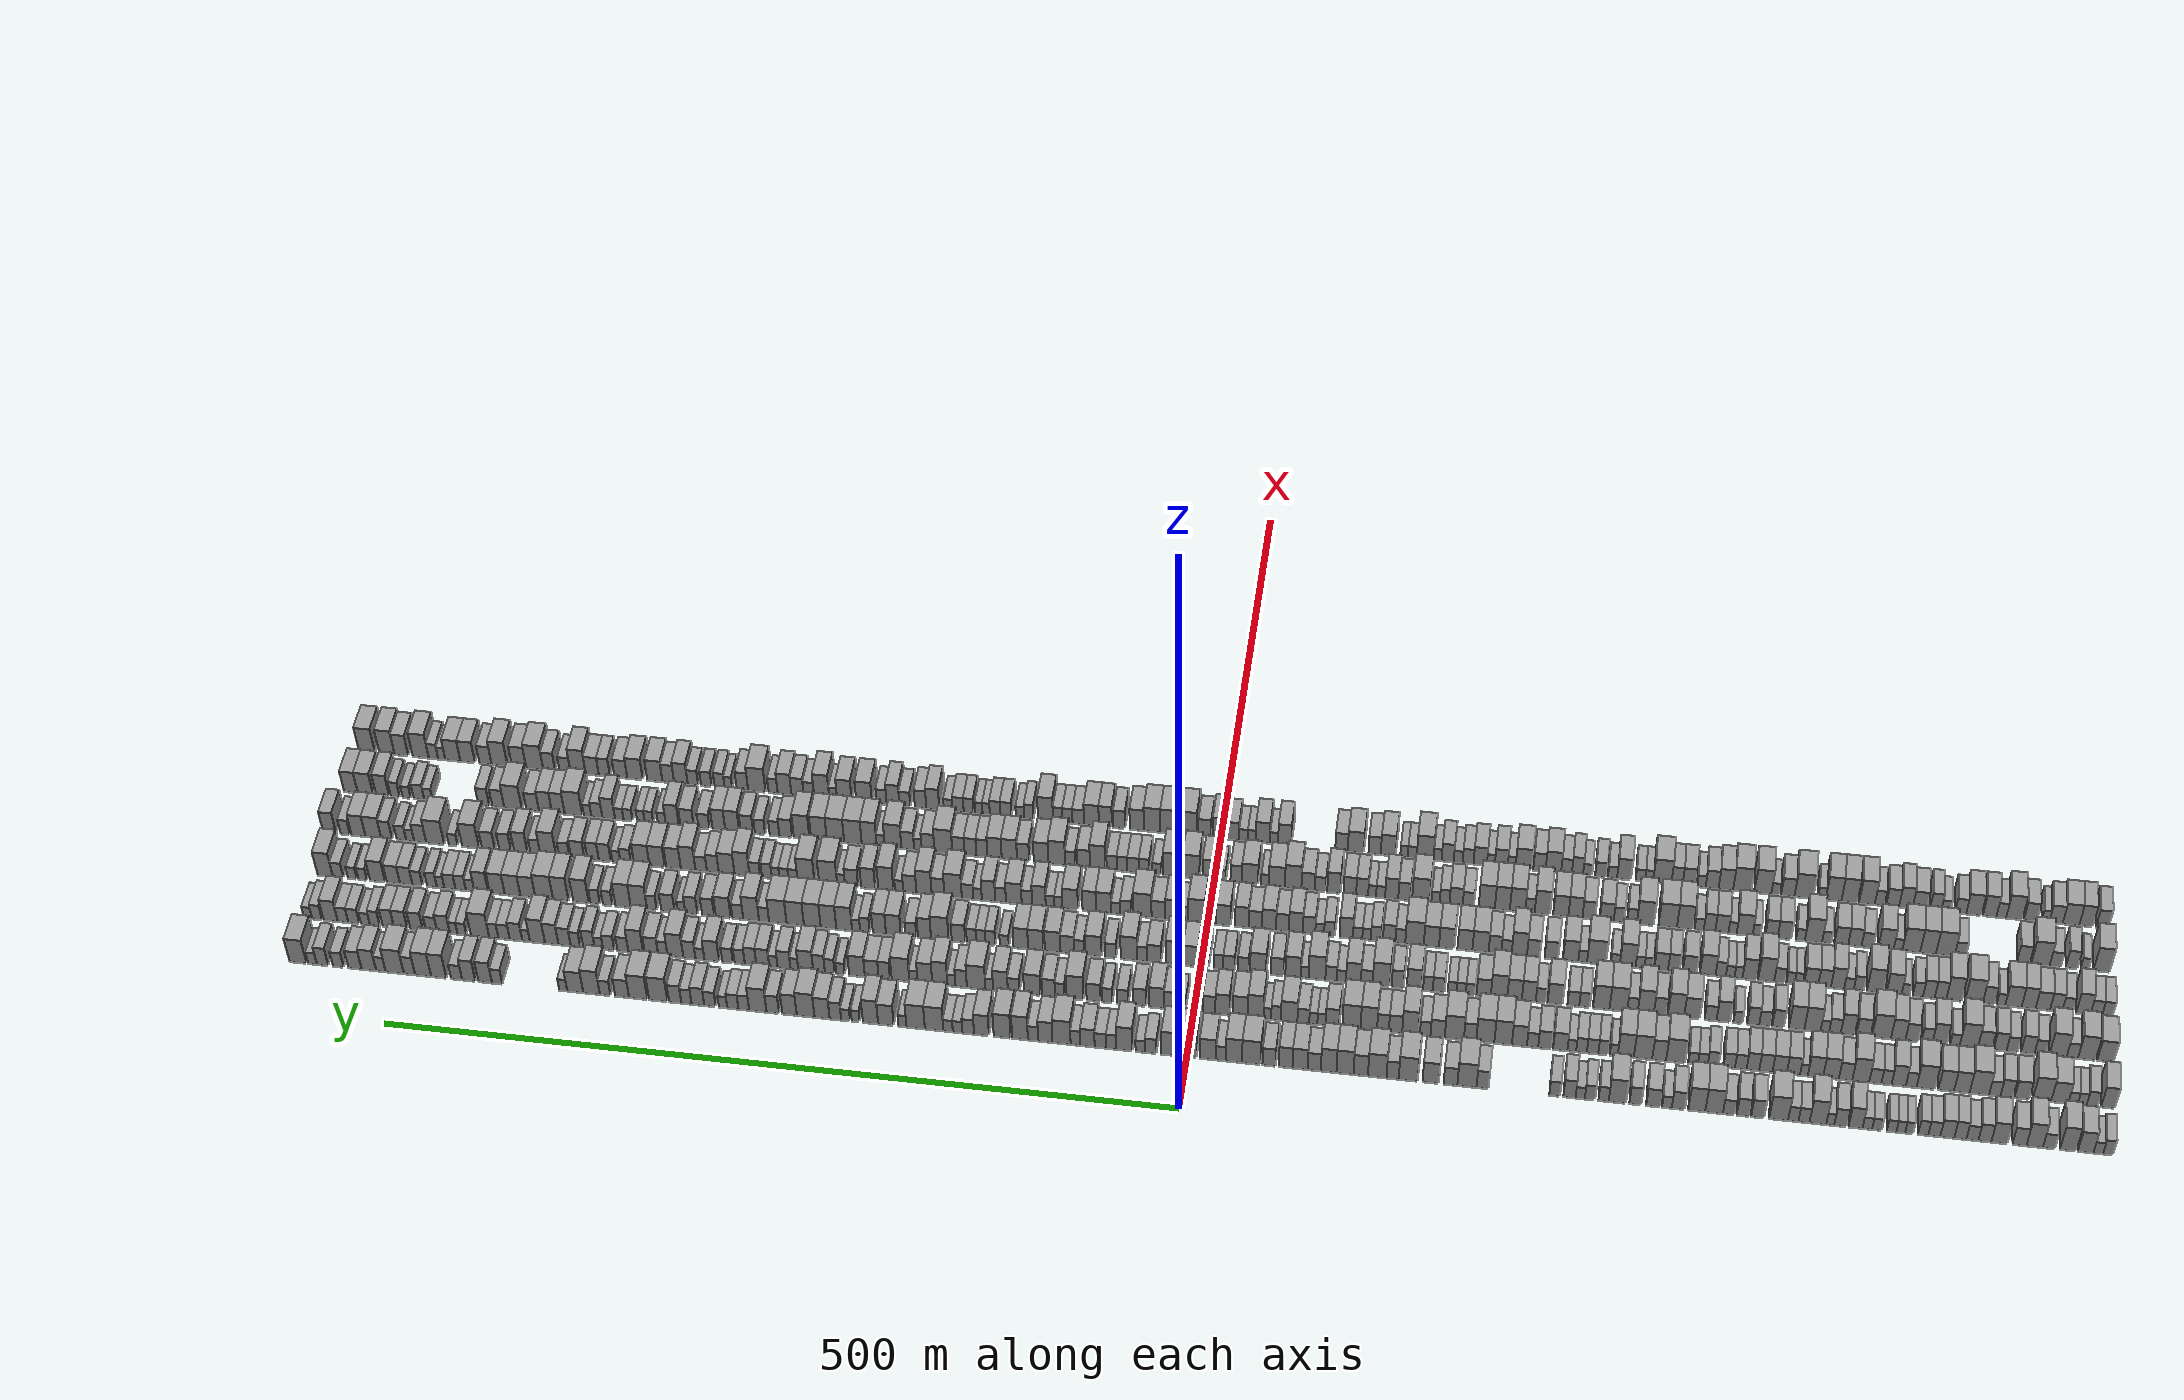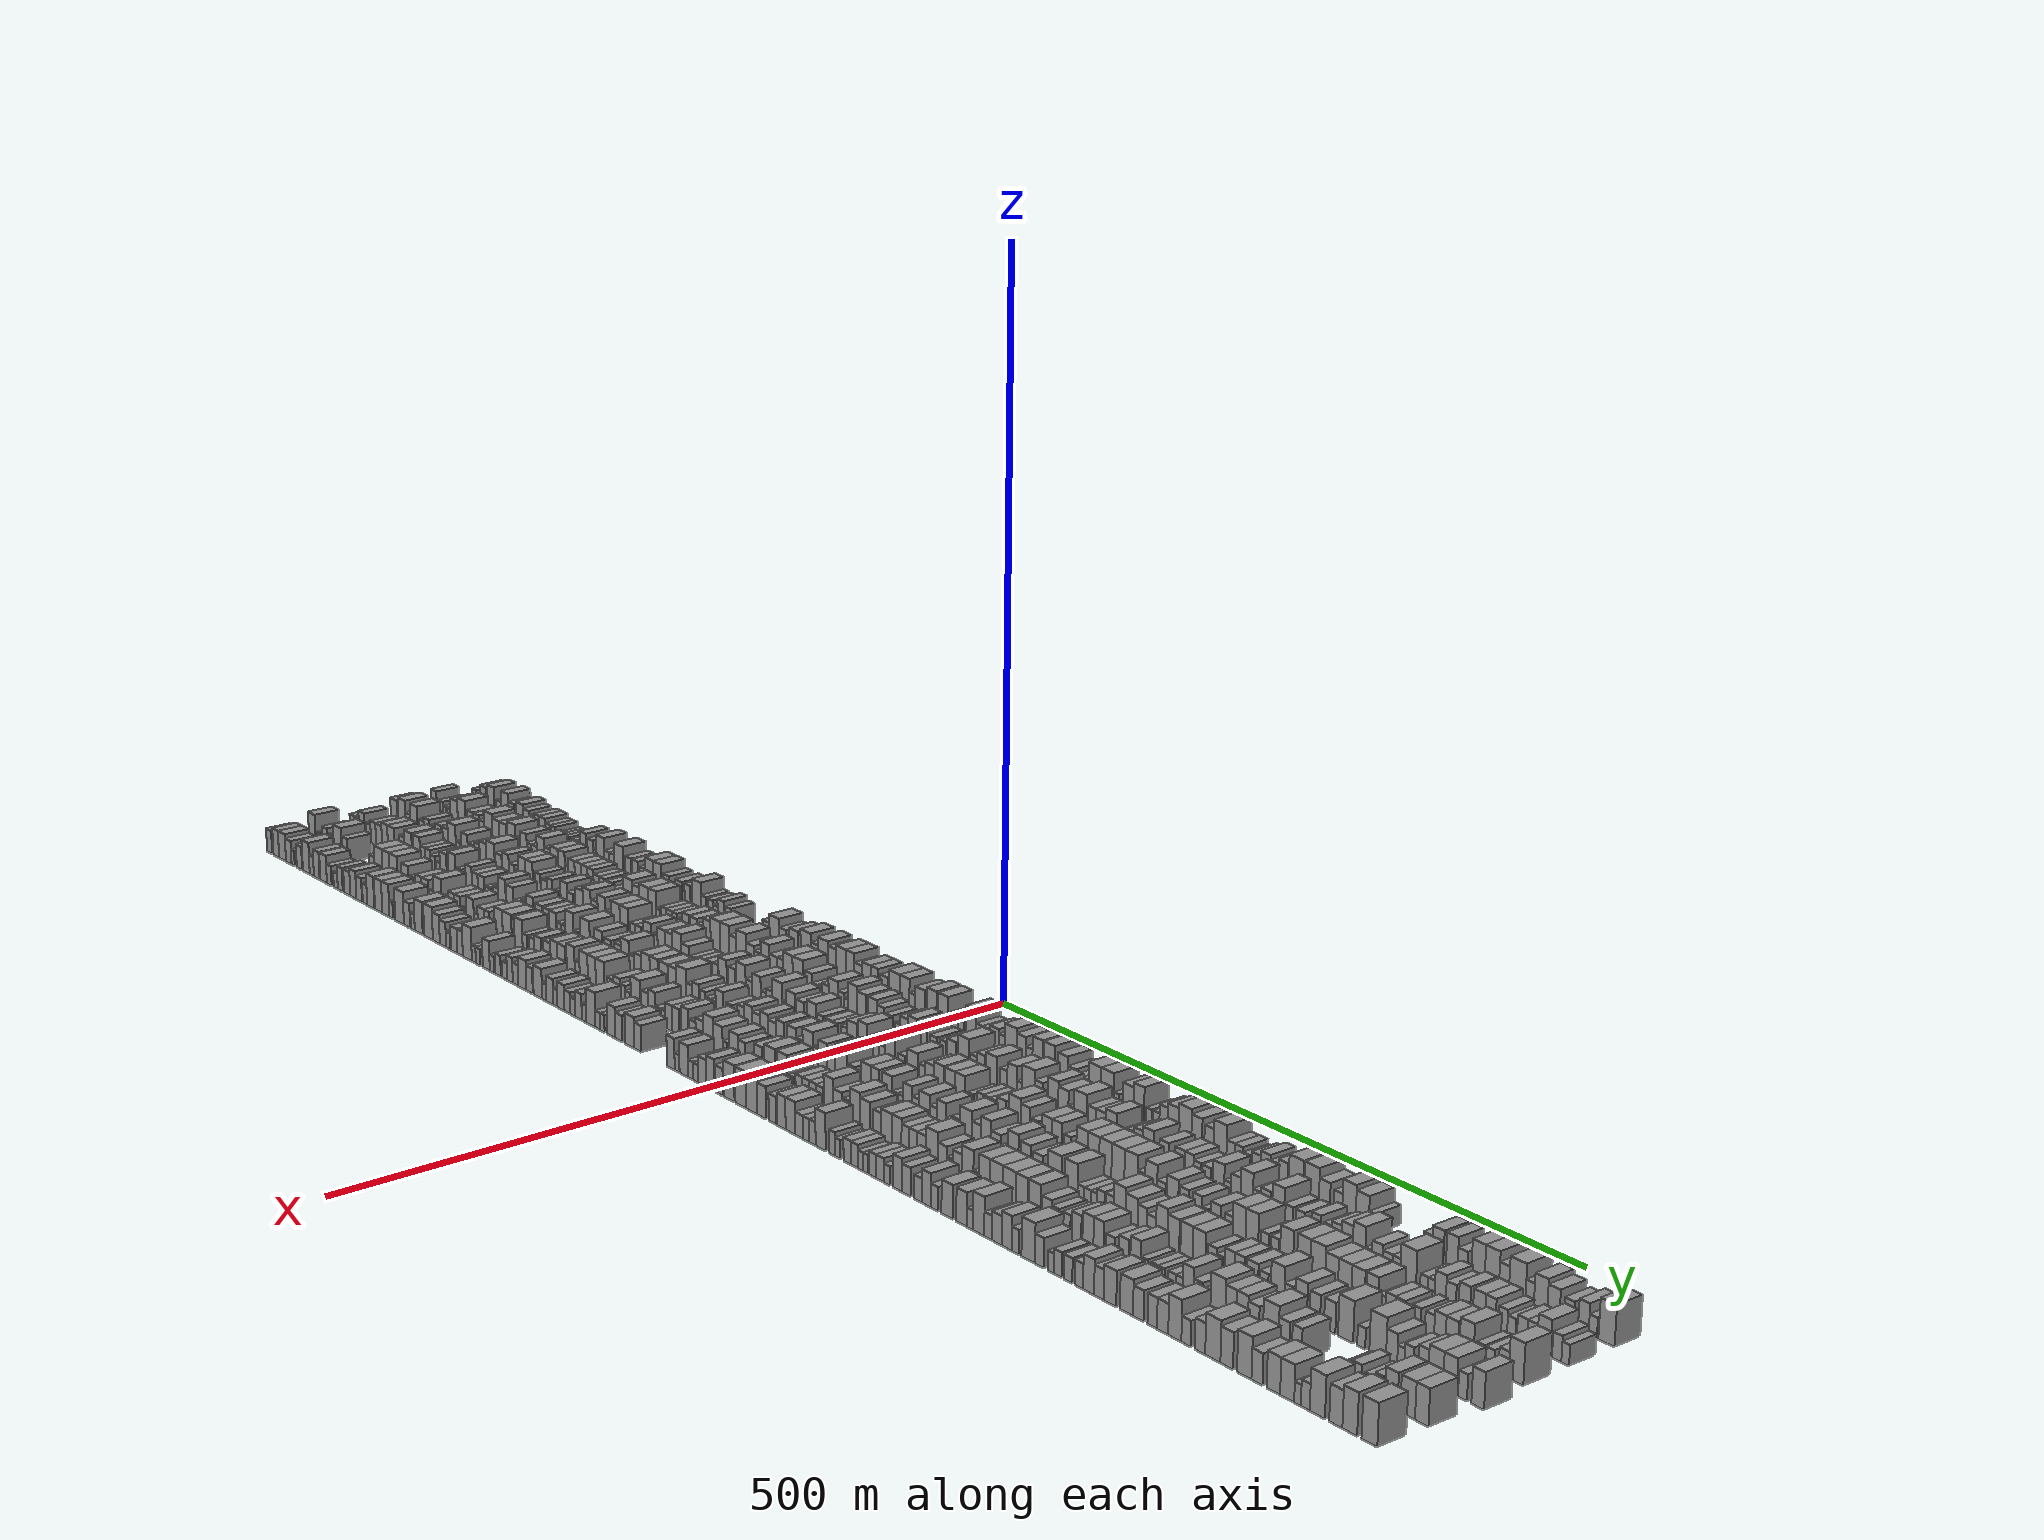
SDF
<sdf version="1.6">
 <world name="default">
  <scene>
   <sky><clouds><speed>12</speed></clouds></sky>
   <ambient>0.4 0.4 0.4 1</ambient>
   <background>0.7 0.7 0.7 1</background>
   <shadows>1</shadows>
  </scene>
  <gravity>0 0 -9.8066</gravity>
  <magnetic_field>6e-06 2.3e-05 -4.2e-05</magnetic_field>
  <physics default="0" name="default_physics" type="ode">
   <ode>
    <solver>
     <type>quick</type>
     <iters>10</iters>
     <sor>1.0</sor>
     <use_dynamic_moi_rescaling>0</use_dynamic_moi_rescaling>
    </solver>
    <constraints>
     <cfm>0</cfm>
     <erp>0.2</erp>
     <contact_max_correcting_vel>100</contact_max_correcting_vel>
     <contact_surface_layer>0.001</contact_surface_layer>
    </constraints>
   </ode>
   <max_step_size>0.004</max_step_size>
   <real_time_factor>1</real_time_factor>
   <real_time_update_rate>250</real_time_update_rate>
  </physics>
  <light name="sun" type="directional">
   <pose>0 0 10 0 0 0</pose>
   <diffuse>0.8 0.8 0.8 1</diffuse>
   <specular>0.2 0.2 0.2 1</specular>
   <attenuation>
    <range>1000</range>
    <constant>0.9</constant>
    <linear>0.01</linear>
    <quadratic>0.001</quadratic>
   </attenuation>
   <direction>-0.5 0.1 -0.9</direction>
  </light>
  <model name="building_1">
   <static>1</static>
   <pose>50.0000 -564.9741 0 0.000000 0.000000 0.000000</pose>
   <link name="link">
    <pose>0 0 7.50 0 0 0</pose>
    <collision name="collision"><geometry><box><size>20.0000 6.0518 15.0000</size></box></geometry></collision>
    <visual name="visual">
     <cast_shadows>0</cast_shadows>
     <geometry><box><size>20.0000 6.0518 15.0000</size></box></geometry>
     <material>
      <script>
       <uri>model://grey_wall/materials/scripts</uri>
       <uri>model://grey_wall/materials/textures</uri>
       <name>vrc/grey_wall</name>
      </script>
     </material>
    </visual>
   </link>
  </model>
  <model name="building_2">
   <static>1</static>
   <pose>50.0000 -559.0703 0 0.000000 0.000000 0.000000</pose>
   <link name="link">
    <pose>0 0 6.00 0 0 0</pose>
    <collision name="collision"><geometry><box><size>20.0000 5.7558 12.0000</size></box></geometry></collision>
    <visual name="visual">
     <cast_shadows>0</cast_shadows>
     <geometry><box><size>20.0000 5.7558 12.0000</size></box></geometry>
     <material>
      <script>
       <uri>model://grey_wall/materials/scripts</uri>
       <uri>model://grey_wall/materials/textures</uri>
       <name>vrc/grey_wall</name>
      </script>
     </material>
    </visual>
   </link>
  </model>
  <model name="building_3">
   <static>1</static>
   <pose>50.0000 -551.4871 0 0.000000 0.000000 0.000000</pose>
   <link name="link">
    <pose>0 0 10.50 0 0 0</pose>
    <collision name="collision"><geometry><box><size>20.0000 9.4108 21.0000</size></box></geometry></collision>
    <visual name="visual">
     <cast_shadows>0</cast_shadows>
     <geometry><box><size>20.0000 9.4108 21.0000</size></box></geometry>
     <material>
      <script>
       <uri>model://grey_wall/materials/scripts</uri>
       <uri>model://grey_wall/materials/textures</uri>
       <name>vrc/grey_wall</name>
      </script>
     </material>
    </visual>
   </link>
  </model>
  <model name="building_4">
   <static>1</static>
   <pose>50.0000 -540.9198 0 0.000000 0.000000 0.000000</pose>
   <link name="link">
    <pose>0 0 12.00 0 0 0</pose>
    <collision name="collision"><geometry><box><size>20.0000 9.7238 24.0000</size></box></geometry></collision>
    <visual name="visual">
     <cast_shadows>0</cast_shadows>
     <geometry><box><size>20.0000 9.7238 24.0000</size></box></geometry>
     <material>
      <script>
       <uri>model://grey_wall/materials/scripts</uri>
       <uri>model://grey_wall/materials/textures</uri>
       <name>vrc/grey_wall</name>
      </script>
     </material>
    </visual>
   </link>
  </model>
  <model name="building_5">
   <static>1</static>
   <pose>50.0000 -529.4019 0 0.000000 0.000000 0.000000</pose>
   <link name="link">
    <pose>0 0 7.50 0 0 0</pose>
    <collision name="collision"><geometry><box><size>20.0000 7.3119 15.0000</size></box></geometry></collision>
    <visual name="visual">
     <cast_shadows>0</cast_shadows>
     <geometry><box><size>20.0000 7.3119 15.0000</size></box></geometry>
     <material>
      <script>
       <uri>model://grey_wall/materials/scripts</uri>
       <uri>model://grey_wall/materials/textures</uri>
       <name>vrc/grey_wall</name>
      </script>
     </material>
    </visual>
   </link>
  </model>
  <model name="building_6">
   <static>1</static>
   <pose>50.0000 -520.7730 0 0.000000 0.000000 0.000000</pose>
   <link name="link">
    <pose>0 0 12.00 0 0 0</pose>
    <collision name="collision"><geometry><box><size>20.0000 9.9459 24.0000</size></box></geometry></collision>
    <visual name="visual">
     <cast_shadows>0</cast_shadows>
     <geometry><box><size>20.0000 9.9459 24.0000</size></box></geometry>
     <material>
      <script>
       <uri>model://grey_wall/materials/scripts</uri>
       <uri>model://grey_wall/materials/textures</uri>
       <name>vrc/grey_wall</name>
      </script>
     </material>
    </visual>
   </link>
  </model>
  <model name="building_7">
   <static>1</static>
   <pose>50.0000 -511.5926 0 0.000000 0.000000 0.000000</pose>
   <link name="link">
    <pose>0 0 9.00 0 0 0</pose>
    <collision name="collision"><geometry><box><size>20.0000 8.4149 18.0000</size></box></geometry></collision>
    <visual name="visual">
     <cast_shadows>0</cast_shadows>
     <geometry><box><size>20.0000 8.4149 18.0000</size></box></geometry>
     <material>
      <script>
       <uri>model://grey_wall/materials/scripts</uri>
       <uri>model://grey_wall/materials/textures</uri>
       <name>vrc/grey_wall</name>
      </script>
     </material>
    </visual>
   </link>
  </model>
  <model name="building_8">
   <static>1</static>
   <pose>50.0000 -499.4567 0 0.000000 0.000000 0.000000</pose>
   <link name="link">
    <pose>0 0 10.50 0 0 0</pose>
    <collision name="collision"><geometry><box><size>20.0000 9.8571 21.0000</size></box></geometry></collision>
    <visual name="visual">
     <cast_shadows>0</cast_shadows>
     <geometry><box><size>20.0000 9.8571 21.0000</size></box></geometry>
     <material>
      <script>
       <uri>model://grey_wall/materials/scripts</uri>
       <uri>model://grey_wall/materials/textures</uri>
       <name>vrc/grey_wall</name>
      </script>
     </material>
    </visual>
   </link>
  </model>
  <model name="building_9">
   <static>1</static>
   <pose>50.0000 -490.6174 0 0.000000 0.000000 0.000000</pose>
   <link name="link">
    <pose>0 0 9.00 0 0 0</pose>
    <collision name="collision"><geometry><box><size>20.0000 7.8215 18.0000</size></box></geometry></collision>
    <visual name="visual">
     <cast_shadows>0</cast_shadows>
     <geometry><box><size>20.0000 7.8215 18.0000</size></box></geometry>
     <material>
      <script>
       <uri>model://grey_wall/materials/scripts</uri>
       <uri>model://grey_wall/materials/textures</uri>
       <name>vrc/grey_wall</name>
      </script>
     </material>
    </visual>
   </link>
  </model>
  <model name="building_10">
   <static>1</static>
   <pose>50.0000 -483.0903 0 0.000000 0.000000 0.000000</pose>
   <link name="link">
    <pose>0 0 7.50 0 0 0</pose>
    <collision name="collision"><geometry><box><size>20.0000 7.2328 15.0000</size></box></geometry></collision>
    <visual name="visual">
     <cast_shadows>0</cast_shadows>
     <geometry><box><size>20.0000 7.2328 15.0000</size></box></geometry>
     <material>
      <script>
       <uri>model://grey_wall/materials/scripts</uri>
       <uri>model://grey_wall/materials/textures</uri>
       <name>vrc/grey_wall</name>
      </script>
     </material>
    </visual>
   </link>
  </model>
  <model name="building_11">
   <static>1</static>
   <pose>50.0000 -475.7913 0 0.000000 0.000000 0.000000</pose>
   <link name="link">
    <pose>0 0 9.00 0 0 0</pose>
    <collision name="collision"><geometry><box><size>20.0000 7.3651 18.0000</size></box></geometry></collision>
    <visual name="visual">
     <cast_shadows>0</cast_shadows>
     <geometry><box><size>20.0000 7.3651 18.0000</size></box></geometry>
     <material>
      <script>
       <uri>model://grey_wall/materials/scripts</uri>
       <uri>model://grey_wall/materials/textures</uri>
       <name>vrc/grey_wall</name>
      </script>
     </material>
    </visual>
   </link>
  </model>
  <model name="building_12">
   <static>1</static>
   <pose>50.0000 -467.8832 0 0.000000 0.000000 0.000000</pose>
   <link name="link">
    <pose>0 0 9.00 0 0 0</pose>
    <collision name="collision"><geometry><box><size>20.0000 8.4512 18.0000</size></box></geometry></collision>
    <visual name="visual">
     <cast_shadows>0</cast_shadows>
     <geometry><box><size>20.0000 8.4512 18.0000</size></box></geometry>
     <material>
      <script>
       <uri>model://grey_wall/materials/scripts</uri>
       <uri>model://grey_wall/materials/textures</uri>
       <name>vrc/grey_wall</name>
      </script>
     </material>
    </visual>
   </link>
  </model>
  <model name="building_13">
   <static>1</static>
   <pose>50.0000 -460.0356 0 0.000000 0.000000 0.000000</pose>
   <link name="link">
    <pose>0 0 7.50 0 0 0</pose>
    <collision name="collision"><geometry><box><size>20.0000 7.2439 15.0000</size></box></geometry></collision>
    <visual name="visual">
     <cast_shadows>0</cast_shadows>
     <geometry><box><size>20.0000 7.2439 15.0000</size></box></geometry>
     <material>
      <script>
       <uri>model://grey_wall/materials/scripts</uri>
       <uri>model://grey_wall/materials/textures</uri>
       <name>vrc/grey_wall</name>
      </script>
     </material>
    </visual>
   </link>
  </model>
  <model name="building_14">
   <static>1</static>
   <pose>50.0000 -453.3229 0 0.000000 0.000000 0.000000</pose>
   <link name="link">
    <pose>0 0 7.50 0 0 0</pose>
    <collision name="collision"><geometry><box><size>20.0000 6.1816 15.0000</size></box></geometry></collision>
    <visual name="visual">
     <cast_shadows>0</cast_shadows>
     <geometry><box><size>20.0000 6.1816 15.0000</size></box></geometry>
     <material>
      <script>
       <uri>model://grey_wall/materials/scripts</uri>
       <uri>model://grey_wall/materials/textures</uri>
       <name>vrc/grey_wall</name>
      </script>
     </material>
    </visual>
   </link>
  </model>
  <model name="building_15">
   <static>1</static>
   <pose>50.0000 -444.8198 0 0.000000 0.000000 0.000000</pose>
   <link name="link">
    <pose>0 0 6.00 0 0 0</pose>
    <collision name="collision"><geometry><box><size>20.0000 4.8246 12.0000</size></box></geometry></collision>
    <visual name="visual">
     <cast_shadows>0</cast_shadows>
     <geometry><box><size>20.0000 4.8246 12.0000</size></box></geometry>
     <material>
      <script>
       <uri>model://grey_wall/materials/scripts</uri>
       <uri>model://grey_wall/materials/textures</uri>
       <name>vrc/grey_wall</name>
      </script>
     </material>
    </visual>
   </link>
  </model>
  <model name="building_16">
   <static>1</static>
   <pose>50.0000 -439.6983 0 0.000000 0.000000 0.000000</pose>
   <link name="link">
    <pose>0 0 6.00 0 0 0</pose>
    <collision name="collision"><geometry><box><size>20.0000 5.4185 12.0000</size></box></geometry></collision>
    <visual name="visual">
     <cast_shadows>0</cast_shadows>
     <geometry><box><size>20.0000 5.4185 12.0000</size></box></geometry>
     <material>
      <script>
       <uri>model://grey_wall/materials/scripts</uri>
       <uri>model://grey_wall/materials/textures</uri>
       <name>vrc/grey_wall</name>
      </script>
     </material>
    </visual>
   </link>
  </model>
  <model name="building_17">
   <static>1</static>
   <pose>50.0000 -434.1179 0 0.000000 0.000000 0.000000</pose>
   <link name="link">
    <pose>0 0 6.00 0 0 0</pose>
    <collision name="collision"><geometry><box><size>20.0000 5.7422 12.0000</size></box></geometry></collision>
    <visual name="visual">
     <cast_shadows>0</cast_shadows>
     <geometry><box><size>20.0000 5.7422 12.0000</size></box></geometry>
     <material>
      <script>
       <uri>model://grey_wall/materials/scripts</uri>
       <uri>model://grey_wall/materials/textures</uri>
       <name>vrc/grey_wall</name>
      </script>
     </material>
    </visual>
   </link>
  </model>
  <model name="building_18">
   <static>1</static>
   <pose>50.0000 -425.2668 0 0.000000 0.000000 0.000000</pose>
   <link name="link">
    <pose>0 0 6.00 0 0 0</pose>
    <collision name="collision"><geometry><box><size>20.0000 5.9600 12.0000</size></box></geometry></collision>
    <visual name="visual">
     <cast_shadows>0</cast_shadows>
     <geometry><box><size>20.0000 5.9600 12.0000</size></box></geometry>
     <material>
      <script>
       <uri>model://grey_wall/materials/scripts</uri>
       <uri>model://grey_wall/materials/textures</uri>
       <name>vrc/grey_wall</name>
      </script>
     </material>
    </visual>
   </link>
  </model>
  <model name="building_19">
   <static>1</static>
   <pose>50.0000 -419.3706 0 0.000000 0.000000 0.000000</pose>
   <link name="link">
    <pose>0 0 6.00 0 0 0</pose>
    <collision name="collision"><geometry><box><size>20.0000 5.8324 12.0000</size></box></geometry></collision>
    <visual name="visual">
     <cast_shadows>0</cast_shadows>
     <geometry><box><size>20.0000 5.8324 12.0000</size></box></geometry>
     <material>
      <script>
       <uri>model://grey_wall/materials/scripts</uri>
       <uri>model://grey_wall/materials/textures</uri>
       <name>vrc/grey_wall</name>
      </script>
     </material>
    </visual>
   </link>
  </model>
  <model name="building_20">
   <static>1</static>
   <pose>50.0000 -412.1958 0 0.000000 0.000000 0.000000</pose>
   <link name="link">
    <pose>0 0 10.50 0 0 0</pose>
    <collision name="collision"><geometry><box><size>20.0000 8.5172 21.0000</size></box></geometry></collision>
    <visual name="visual">
     <cast_shadows>0</cast_shadows>
     <geometry><box><size>20.0000 8.5172 21.0000</size></box></geometry>
     <material>
      <script>
       <uri>model://grey_wall/materials/scripts</uri>
       <uri>model://grey_wall/materials/textures</uri>
       <name>vrc/grey_wall</name>
      </script>
     </material>
    </visual>
   </link>
  </model>
  <model name="building_21">
   <static>1</static>
   <pose>50.0000 -403.0719 0 0.000000 0.000000 0.000000</pose>
   <link name="link">
    <pose>0 0 9.00 0 0 0</pose>
    <collision name="collision"><geometry><box><size>20.0000 7.7307 18.0000</size></box></geometry></collision>
    <visual name="visual">
     <cast_shadows>0</cast_shadows>
     <geometry><box><size>20.0000 7.7307 18.0000</size></box></geometry>
     <material>
      <script>
       <uri>model://grey_wall/materials/scripts</uri>
       <uri>model://grey_wall/materials/textures</uri>
       <name>vrc/grey_wall</name>
      </script>
     </material>
    </visual>
   </link>
  </model>
  <model name="building_22">
   <static>1</static>
   <pose>50.0000 -396.7877 0 0.000000 0.000000 0.000000</pose>
   <link name="link">
    <pose>0 0 6.00 0 0 0</pose>
    <collision name="collision"><geometry><box><size>20.0000 4.8377 12.0000</size></box></geometry></collision>
    <visual name="visual">
     <cast_shadows>0</cast_shadows>
     <geometry><box><size>20.0000 4.8377 12.0000</size></box></geometry>
     <material>
      <script>
       <uri>model://grey_wall/materials/scripts</uri>
       <uri>model://grey_wall/materials/textures</uri>
       <name>vrc/grey_wall</name>
      </script>
     </material>
    </visual>
   </link>
  </model>
  <model name="building_23">
   <static>1</static>
   <pose>50.0000 -389.2605 0 0.000000 0.000000 0.000000</pose>
   <link name="link">
    <pose>0 0 12.00 0 0 0</pose>
    <collision name="collision"><geometry><box><size>20.0000 10.2167 24.0000</size></box></geometry></collision>
    <visual name="visual">
     <cast_shadows>0</cast_shadows>
     <geometry><box><size>20.0000 10.2167 24.0000</size></box></geometry>
     <material>
      <script>
       <uri>model://grey_wall/materials/scripts</uri>
       <uri>model://grey_wall/materials/textures</uri>
       <name>vrc/grey_wall</name>
      </script>
     </material>
    </visual>
   </link>
  </model>
  <model name="building_24">
   <static>1</static>
   <pose>50.0000 -380.7902 0 0.000000 0.000000 0.000000</pose>
   <link name="link">
    <pose>0 0 7.50 0 0 0</pose>
    <collision name="collision"><geometry><box><size>20.0000 6.7239 15.0000</size></box></geometry></collision>
    <visual name="visual">
     <cast_shadows>0</cast_shadows>
     <geometry><box><size>20.0000 6.7239 15.0000</size></box></geometry>
     <material>
      <script>
       <uri>model://grey_wall/materials/scripts</uri>
       <uri>model://grey_wall/materials/textures</uri>
       <name>vrc/grey_wall</name>
      </script>
     </material>
    </visual>
   </link>
  </model>
  <model name="building_25">
   <static>1</static>
   <pose>50.0000 -374.2850 0 0.000000 0.000000 0.000000</pose>
   <link name="link">
    <pose>0 0 7.50 0 0 0</pose>
    <collision name="collision"><geometry><box><size>20.0000 6.2863 15.0000</size></box></geometry></collision>
    <visual name="visual">
     <cast_shadows>0</cast_shadows>
     <geometry><box><size>20.0000 6.2863 15.0000</size></box></geometry>
     <material>
      <script>
       <uri>model://grey_wall/materials/scripts</uri>
       <uri>model://grey_wall/materials/textures</uri>
       <name>vrc/grey_wall</name>
      </script>
     </material>
    </visual>
   </link>
  </model>
  <model name="building_26">
   <static>1</static>
   <pose>50.0000 -365.3331 0 0.000000 0.000000 0.000000</pose>
   <link name="link">
    <pose>0 0 12.00 0 0 0</pose>
    <collision name="collision"><geometry><box><size>20.0000 11.6175 24.0000</size></box></geometry></collision>
    <visual name="visual">
     <cast_shadows>0</cast_shadows>
     <geometry><box><size>20.0000 11.6175 24.0000</size></box></geometry>
     <material>
      <script>
       <uri>model://grey_wall/materials/scripts</uri>
       <uri>model://grey_wall/materials/textures</uri>
       <name>vrc/grey_wall</name>
      </script>
     </material>
    </visual>
   </link>
  </model>
  <model name="building_27">
   <static>1</static>
   <pose>50.0000 -352.5584 0 0.000000 0.000000 0.000000</pose>
   <link name="link">
    <pose>0 0 9.00 0 0 0</pose>
    <collision name="collision"><geometry><box><size>20.0000 7.9319 18.0000</size></box></geometry></collision>
    <visual name="visual">
     <cast_shadows>0</cast_shadows>
     <geometry><box><size>20.0000 7.9319 18.0000</size></box></geometry>
     <material>
      <script>
       <uri>model://grey_wall/materials/scripts</uri>
       <uri>model://grey_wall/materials/textures</uri>
       <name>vrc/grey_wall</name>
      </script>
     </material>
    </visual>
   </link>
  </model>
  <model name="building_28">
   <static>1</static>
   <pose>50.0000 -343.6352 0 0.000000 0.000000 0.000000</pose>
   <link name="link">
    <pose>0 0 9.00 0 0 0</pose>
    <collision name="collision"><geometry><box><size>20.0000 7.9145 18.0000</size></box></geometry></collision>
    <visual name="visual">
     <cast_shadows>0</cast_shadows>
     <geometry><box><size>20.0000 7.9145 18.0000</size></box></geometry>
     <material>
      <script>
       <uri>model://grey_wall/materials/scripts</uri>
       <uri>model://grey_wall/materials/textures</uri>
       <name>vrc/grey_wall</name>
      </script>
     </material>
    </visual>
   </link>
  </model>
  <model name="building_29">
   <static>1</static>
   <pose>50.0000 -334.9840 0 0.000000 0.000000 0.000000</pose>
   <link name="link">
    <pose>0 0 7.50 0 0 0</pose>
    <collision name="collision"><geometry><box><size>20.0000 7.3877 15.0000</size></box></geometry></collision>
    <visual name="visual">
     <cast_shadows>0</cast_shadows>
     <geometry><box><size>20.0000 7.3877 15.0000</size></box></geometry>
     <material>
      <script>
       <uri>model://grey_wall/materials/scripts</uri>
       <uri>model://grey_wall/materials/textures</uri>
       <name>vrc/grey_wall</name>
      </script>
     </material>
    </visual>
   </link>
  </model>
  <model name="building_30">
   <static>1</static>
   <pose>50.0000 -325.8640 0 0.000000 0.000000 0.000000</pose>
   <link name="link">
    <pose>0 0 12.00 0 0 0</pose>
    <collision name="collision"><geometry><box><size>20.0000 10.8523 24.0000</size></box></geometry></collision>
    <visual name="visual">
     <cast_shadows>0</cast_shadows>
     <geometry><box><size>20.0000 10.8523 24.0000</size></box></geometry>
     <material>
      <script>
       <uri>model://grey_wall/materials/scripts</uri>
       <uri>model://grey_wall/materials/textures</uri>
       <name>vrc/grey_wall</name>
      </script>
     </material>
    </visual>
   </link>
  </model>
  <model name="building_31">
   <static>1</static>
   <pose>50.0000 -315.2606 0 0.000000 0.000000 0.000000</pose>
   <link name="link">
    <pose>0 0 12.00 0 0 0</pose>
    <collision name="collision"><geometry><box><size>20.0000 10.3544 24.0000</size></box></geometry></collision>
    <visual name="visual">
     <cast_shadows>0</cast_shadows>
     <geometry><box><size>20.0000 10.3544 24.0000</size></box></geometry>
     <material>
      <script>
       <uri>model://grey_wall/materials/scripts</uri>
       <uri>model://grey_wall/materials/textures</uri>
       <name>vrc/grey_wall</name>
      </script>
     </material>
    </visual>
   </link>
  </model>
  <model name="building_32">
   <static>1</static>
   <pose>50.0000 -304.0334 0 0.000000 0.000000 0.000000</pose>
   <link name="link">
    <pose>0 0 9.00 0 0 0</pose>
    <collision name="collision"><geometry><box><size>20.0000 8.0998 18.0000</size></box></geometry></collision>
    <visual name="visual">
     <cast_shadows>0</cast_shadows>
     <geometry><box><size>20.0000 8.0998 18.0000</size></box></geometry>
     <material>
      <script>
       <uri>model://grey_wall/materials/scripts</uri>
       <uri>model://grey_wall/materials/textures</uri>
       <name>vrc/grey_wall</name>
      </script>
     </material>
    </visual>
   </link>
  </model>
  <model name="building_33">
   <static>1</static>
   <pose>50.0000 -297.0031 0 0.000000 0.000000 0.000000</pose>
   <link name="link">
    <pose>0 0 6.00 0 0 0</pose>
    <collision name="collision"><geometry><box><size>20.0000 5.9609 12.0000</size></box></geometry></collision>
    <visual name="visual">
     <cast_shadows>0</cast_shadows>
     <geometry><box><size>20.0000 5.9609 12.0000</size></box></geometry>
     <material>
      <script>
       <uri>model://grey_wall/materials/scripts</uri>
       <uri>model://grey_wall/materials/textures</uri>
       <name>vrc/grey_wall</name>
      </script>
     </material>
    </visual>
   </link>
  </model>
  <model name="building_34">
   <static>1</static>
   <pose>50.0000 -288.6626 0 0.000000 0.000000 0.000000</pose>
   <link name="link">
    <pose>0 0 9.00 0 0 0</pose>
    <collision name="collision"><geometry><box><size>20.0000 8.7200 18.0000</size></box></geometry></collision>
    <visual name="visual">
     <cast_shadows>0</cast_shadows>
     <geometry><box><size>20.0000 8.7200 18.0000</size></box></geometry>
     <material>
      <script>
       <uri>model://grey_wall/materials/scripts</uri>
       <uri>model://grey_wall/materials/textures</uri>
       <name>vrc/grey_wall</name>
      </script>
     </material>
    </visual>
   </link>
  </model>
  <model name="building_35">
   <static>1</static>
   <pose>50.0000 -277.6412 0 0.000000 0.000000 0.000000</pose>
   <link name="link">
    <pose>0 0 9.00 0 0 0</pose>
    <collision name="collision"><geometry><box><size>20.0000 7.3229 18.0000</size></box></geometry></collision>
    <visual name="visual">
     <cast_shadows>0</cast_shadows>
     <geometry><box><size>20.0000 7.3229 18.0000</size></box></geometry>
     <material>
      <script>
       <uri>model://grey_wall/materials/scripts</uri>
       <uri>model://grey_wall/materials/textures</uri>
       <name>vrc/grey_wall</name>
      </script>
     </material>
    </visual>
   </link>
  </model>
  <model name="building_36">
   <static>1</static>
   <pose>50.0000 -266.6025 0 0.000000 0.000000 0.000000</pose>
   <link name="link">
    <pose>0 0 12.00 0 0 0</pose>
    <collision name="collision"><geometry><box><size>20.0000 10.7545 24.0000</size></box></geometry></collision>
    <visual name="visual">
     <cast_shadows>0</cast_shadows>
     <geometry><box><size>20.0000 10.7545 24.0000</size></box></geometry>
     <material>
      <script>
       <uri>model://grey_wall/materials/scripts</uri>
       <uri>model://grey_wall/materials/textures</uri>
       <name>vrc/grey_wall</name>
      </script>
     </material>
    </visual>
   </link>
  </model>
  <model name="building_37">
   <static>1</static>
   <pose>50.0000 -258.0937 0 0.000000 0.000000 0.000000</pose>
   <link name="link">
    <pose>0 0 7.50 0 0 0</pose>
    <collision name="collision"><geometry><box><size>20.0000 6.2632 15.0000</size></box></geometry></collision>
    <visual name="visual">
     <cast_shadows>0</cast_shadows>
     <geometry><box><size>20.0000 6.2632 15.0000</size></box></geometry>
     <material>
      <script>
       <uri>model://grey_wall/materials/scripts</uri>
       <uri>model://grey_wall/materials/textures</uri>
       <name>vrc/grey_wall</name>
      </script>
     </material>
    </visual>
   </link>
  </model>
  <model name="building_38">
   <static>1</static>
   <pose>50.0000 -249.7709 0 0.000000 0.000000 0.000000</pose>
   <link name="link">
    <pose>0 0 7.50 0 0 0</pose>
    <collision name="collision"><geometry><box><size>20.0000 6.3823 15.0000</size></box></geometry></collision>
    <visual name="visual">
     <cast_shadows>0</cast_shadows>
     <geometry><box><size>20.0000 6.3823 15.0000</size></box></geometry>
     <material>
      <script>
       <uri>model://grey_wall/materials/scripts</uri>
       <uri>model://grey_wall/materials/textures</uri>
       <name>vrc/grey_wall</name>
      </script>
     </material>
    </visual>
   </link>
  </model>
  <model name="building_39">
   <static>1</static>
   <pose>50.0000 -243.7044 0 0.000000 0.000000 0.000000</pose>
   <link name="link">
    <pose>0 0 6.00 0 0 0</pose>
    <collision name="collision"><geometry><box><size>20.0000 5.7508 12.0000</size></box></geometry></collision>
    <visual name="visual">
     <cast_shadows>0</cast_shadows>
     <geometry><box><size>20.0000 5.7508 12.0000</size></box></geometry>
     <material>
      <script>
       <uri>model://grey_wall/materials/scripts</uri>
       <uri>model://grey_wall/materials/textures</uri>
       <name>vrc/grey_wall</name>
      </script>
     </material>
    </visual>
   </link>
  </model>
  <model name="building_40">
   <static>1</static>
   <pose>50.0000 -237.0932 0 0.000000 0.000000 0.000000</pose>
   <link name="link">
    <pose>0 0 9.00 0 0 0</pose>
    <collision name="collision"><geometry><box><size>20.0000 7.4716 18.0000</size></box></geometry></collision>
    <visual name="visual">
     <cast_shadows>0</cast_shadows>
     <geometry><box><size>20.0000 7.4716 18.0000</size></box></geometry>
     <material>
      <script>
       <uri>model://grey_wall/materials/scripts</uri>
       <uri>model://grey_wall/materials/textures</uri>
       <name>vrc/grey_wall</name>
      </script>
     </material>
    </visual>
   </link>
  </model>
  <model name="building_41">
   <static>1</static>
   <pose>50.0000 -228.0385 0 0.000000 0.000000 0.000000</pose>
   <link name="link">
    <pose>0 0 7.50 0 0 0</pose>
    <collision name="collision"><geometry><box><size>20.0000 6.6378 15.0000</size></box></geometry></collision>
    <visual name="visual">
     <cast_shadows>0</cast_shadows>
     <geometry><box><size>20.0000 6.6378 15.0000</size></box></geometry>
     <material>
      <script>
       <uri>model://grey_wall/materials/scripts</uri>
       <uri>model://grey_wall/materials/textures</uri>
       <name>vrc/grey_wall</name>
      </script>
     </material>
    </visual>
   </link>
  </model>
  <model name="building_42">
   <static>1</static>
   <pose>50.0000 -183.5103 0 0.000000 0.000000 0.000000</pose>
   <link name="link">
    <pose>0 0 9.00 0 0 0</pose>
    <collision name="collision"><geometry><box><size>20.0000 7.4729 18.0000</size></box></geometry></collision>
    <visual name="visual">
     <cast_shadows>0</cast_shadows>
     <geometry><box><size>20.0000 7.4729 18.0000</size></box></geometry>
     <material>
      <script>
       <uri>model://grey_wall/materials/scripts</uri>
       <uri>model://grey_wall/materials/textures</uri>
       <name>vrc/grey_wall</name>
      </script>
     </material>
    </visual>
   </link>
  </model>
  <model name="building_43">
   <static>1</static>
   <pose>50.0000 -173.8588 0 0.000000 0.000000 0.000000</pose>
   <link name="link">
    <pose>0 0 12.00 0 0 0</pose>
    <collision name="collision"><geometry><box><size>20.0000 11.8300 24.0000</size></box></geometry></collision>
    <visual name="visual">
     <cast_shadows>0</cast_shadows>
     <geometry><box><size>20.0000 11.8300 24.0000</size></box></geometry>
     <material>
      <script>
       <uri>model://grey_wall/materials/scripts</uri>
       <uri>model://grey_wall/materials/textures</uri>
       <name>vrc/grey_wall</name>
      </script>
     </material>
    </visual>
   </link>
  </model>
  <model name="building_44">
   <static>1</static>
   <pose>50.0000 -163.6865 0 0.000000 0.000000 0.000000</pose>
   <link name="link">
    <pose>0 0 9.00 0 0 0</pose>
    <collision name="collision"><geometry><box><size>20.0000 8.5146 18.0000</size></box></geometry></collision>
    <visual name="visual">
     <cast_shadows>0</cast_shadows>
     <geometry><box><size>20.0000 8.5146 18.0000</size></box></geometry>
     <material>
      <script>
       <uri>model://grey_wall/materials/scripts</uri>
       <uri>model://grey_wall/materials/textures</uri>
       <name>vrc/grey_wall</name>
      </script>
     </material>
    </visual>
   </link>
  </model>
  <model name="building_45">
   <static>1</static>
   <pose>50.0000 -151.4031 0 0.000000 0.000000 0.000000</pose>
   <link name="link">
    <pose>0 0 10.50 0 0 0</pose>
    <collision name="collision"><geometry><box><size>20.0000 10.0521 21.0000</size></box></geometry></collision>
    <visual name="visual">
     <cast_shadows>0</cast_shadows>
     <geometry><box><size>20.0000 10.0521 21.0000</size></box></geometry>
     <material>
      <script>
       <uri>model://grey_wall/materials/scripts</uri>
       <uri>model://grey_wall/materials/textures</uri>
       <name>vrc/grey_wall</name>
      </script>
     </material>
    </visual>
   </link>
  </model>
  <model name="building_46">
   <static>1</static>
   <pose>50.0000 -137.5196 0 0.000000 0.000000 0.000000</pose>
   <link name="link">
    <pose>0 0 12.00 0 0 0</pose>
    <collision name="collision"><geometry><box><size>20.0000 11.7151 24.0000</size></box></geometry></collision>
    <visual name="visual">
     <cast_shadows>0</cast_shadows>
     <geometry><box><size>20.0000 11.7151 24.0000</size></box></geometry>
     <material>
      <script>
       <uri>model://grey_wall/materials/scripts</uri>
       <uri>model://grey_wall/materials/textures</uri>
       <name>vrc/grey_wall</name>
      </script>
     </material>
    </visual>
   </link>
  </model>
  <model name="building_47">
   <static>1</static>
   <pose>50.0000 -127.8627 0 0.000000 0.000000 0.000000</pose>
   <link name="link">
    <pose>0 0 9.00 0 0 0</pose>
    <collision name="collision"><geometry><box><size>20.0000 7.5986 18.0000</size></box></geometry></collision>
    <visual name="visual">
     <cast_shadows>0</cast_shadows>
     <geometry><box><size>20.0000 7.5986 18.0000</size></box></geometry>
     <material>
      <script>
       <uri>model://grey_wall/materials/scripts</uri>
       <uri>model://grey_wall/materials/textures</uri>
       <name>vrc/grey_wall</name>
      </script>
     </material>
    </visual>
   </link>
  </model>
  <model name="building_48">
   <static>1</static>
   <pose>50.0000 -118.3057 0 0.000000 0.000000 0.000000</pose>
   <link name="link">
    <pose>0 0 12.00 0 0 0</pose>
    <collision name="collision"><geometry><box><size>20.0000 11.5153 24.0000</size></box></geometry></collision>
    <visual name="visual">
     <cast_shadows>0</cast_shadows>
     <geometry><box><size>20.0000 11.5153 24.0000</size></box></geometry>
     <material>
      <script>
       <uri>model://grey_wall/materials/scripts</uri>
       <uri>model://grey_wall/materials/textures</uri>
       <name>vrc/grey_wall</name>
      </script>
     </material>
    </visual>
   </link>
  </model>
  <model name="building_49">
   <static>1</static>
   <pose>50.0000 -108.0683 0 0.000000 0.000000 0.000000</pose>
   <link name="link">
    <pose>0 0 10.50 0 0 0</pose>
    <collision name="collision"><geometry><box><size>20.0000 8.9596 21.0000</size></box></geometry></collision>
    <visual name="visual">
     <cast_shadows>0</cast_shadows>
     <geometry><box><size>20.0000 8.9596 21.0000</size></box></geometry>
     <material>
      <script>
       <uri>model://grey_wall/materials/scripts</uri>
       <uri>model://grey_wall/materials/textures</uri>
       <name>vrc/grey_wall</name>
      </script>
     </material>
    </visual>
   </link>
  </model>
  <model name="building_50">
   <static>1</static>
   <pose>50.0000 -98.2909 0 0.000000 0.000000 0.000000</pose>
   <link name="link">
    <pose>0 0 12.00 0 0 0</pose>
    <collision name="collision"><geometry><box><size>20.0000 10.5951 24.0000</size></box></geometry></collision>
    <visual name="visual">
     <cast_shadows>0</cast_shadows>
     <geometry><box><size>20.0000 10.5951 24.0000</size></box></geometry>
     <material>
      <script>
       <uri>model://grey_wall/materials/scripts</uri>
       <uri>model://grey_wall/materials/textures</uri>
       <name>vrc/grey_wall</name>
      </script>
     </material>
    </visual>
   </link>
  </model>
  <model name="building_51">
   <static>1</static>
   <pose>50.0000 -88.1303 0 0.000000 0.000000 0.000000</pose>
   <link name="link">
    <pose>0 0 12.00 0 0 0</pose>
    <collision name="collision"><geometry><box><size>20.0000 9.7262 24.0000</size></box></geometry></collision>
    <visual name="visual">
     <cast_shadows>0</cast_shadows>
     <geometry><box><size>20.0000 9.7262 24.0000</size></box></geometry>
     <material>
      <script>
       <uri>model://grey_wall/materials/scripts</uri>
       <uri>model://grey_wall/materials/textures</uri>
       <name>vrc/grey_wall</name>
      </script>
     </material>
    </visual>
   </link>
  </model>
  <model name="building_52">
   <static>1</static>
   <pose>50.0000 -79.1546 0 0.000000 0.000000 0.000000</pose>
   <link name="link">
    <pose>0 0 9.00 0 0 0</pose>
    <collision name="collision"><geometry><box><size>20.0000 8.2252 18.0000</size></box></geometry></collision>
    <visual name="visual">
     <cast_shadows>0</cast_shadows>
     <geometry><box><size>20.0000 8.2252 18.0000</size></box></geometry>
     <material>
      <script>
       <uri>model://grey_wall/materials/scripts</uri>
       <uri>model://grey_wall/materials/textures</uri>
       <name>vrc/grey_wall</name>
      </script>
     </material>
    </visual>
   </link>
  </model>
  <model name="building_53">
   <static>1</static>
   <pose>50.0000 -70.3270 0 0.000000 0.000000 0.000000</pose>
   <link name="link">
    <pose>0 0 10.50 0 0 0</pose>
    <collision name="collision"><geometry><box><size>20.0000 9.4300 21.0000</size></box></geometry></collision>
    <visual name="visual">
     <cast_shadows>0</cast_shadows>
     <geometry><box><size>20.0000 9.4300 21.0000</size></box></geometry>
     <material>
      <script>
       <uri>model://grey_wall/materials/scripts</uri>
       <uri>model://grey_wall/materials/textures</uri>
       <name>vrc/grey_wall</name>
      </script>
     </material>
    </visual>
   </link>
  </model>
  <model name="building_54">
   <static>1</static>
   <pose>50.0000 -61.3829 0 0.000000 0.000000 0.000000</pose>
   <link name="link">
    <pose>0 0 10.50 0 0 0</pose>
    <collision name="collision"><geometry><box><size>20.0000 8.4582 21.0000</size></box></geometry></collision>
    <visual name="visual">
     <cast_shadows>0</cast_shadows>
     <geometry><box><size>20.0000 8.4582 21.0000</size></box></geometry>
     <material>
      <script>
       <uri>model://grey_wall/materials/scripts</uri>
       <uri>model://grey_wall/materials/textures</uri>
       <name>vrc/grey_wall</name>
      </script>
     </material>
    </visual>
   </link>
  </model>
  <model name="building_55">
   <static>1</static>
   <pose>50.0000 -51.0369 0 0.000000 0.000000 0.000000</pose>
   <link name="link">
    <pose>0 0 9.00 0 0 0</pose>
    <collision name="collision"><geometry><box><size>20.0000 8.2338 18.0000</size></box></geometry></collision>
    <visual name="visual">
     <cast_shadows>0</cast_shadows>
     <geometry><box><size>20.0000 8.2338 18.0000</size></box></geometry>
     <material>
      <script>
       <uri>model://grey_wall/materials/scripts</uri>
       <uri>model://grey_wall/materials/textures</uri>
       <name>vrc/grey_wall</name>
      </script>
     </material>
    </visual>
   </link>
  </model>
  <model name="building_56">
   <static>1</static>
   <pose>50.0000 -40.0730 0 0.000000 0.000000 0.000000</pose>
   <link name="link">
    <pose>0 0 12.00 0 0 0</pose>
    <collision name="collision"><geometry><box><size>20.0000 11.6939 24.0000</size></box></geometry></collision>
    <visual name="visual">
     <cast_shadows>0</cast_shadows>
     <geometry><box><size>20.0000 11.6939 24.0000</size></box></geometry>
     <material>
      <script>
       <uri>model://grey_wall/materials/scripts</uri>
       <uri>model://grey_wall/materials/textures</uri>
       <name>vrc/grey_wall</name>
      </script>
     </material>
    </visual>
   </link>
  </model>
  <model name="building_57">
   <static>1</static>
   <pose>50.0000 -29.1787 0 0.000000 0.000000 0.000000</pose>
   <link name="link">
    <pose>0 0 12.00 0 0 0</pose>
    <collision name="collision"><geometry><box><size>20.0000 10.0948 24.0000</size></box></geometry></collision>
    <visual name="visual">
     <cast_shadows>0</cast_shadows>
     <geometry><box><size>20.0000 10.0948 24.0000</size></box></geometry>
     <material>
      <script>
       <uri>model://grey_wall/materials/scripts</uri>
       <uri>model://grey_wall/materials/textures</uri>
       <name>vrc/grey_wall</name>
      </script>
     </material>
    </visual>
   </link>
  </model>
  <model name="building_58">
   <static>1</static>
   <pose>50.0000 -21.0761 0 0.000000 0.000000 0.000000</pose>
   <link name="link">
    <pose>0 0 7.50 0 0 0</pose>
    <collision name="collision"><geometry><box><size>20.0000 6.1104 15.0000</size></box></geometry></collision>
    <visual name="visual">
     <cast_shadows>0</cast_shadows>
     <geometry><box><size>20.0000 6.1104 15.0000</size></box></geometry>
     <material>
      <script>
       <uri>model://grey_wall/materials/scripts</uri>
       <uri>model://grey_wall/materials/textures</uri>
       <name>vrc/grey_wall</name>
      </script>
     </material>
    </visual>
   </link>
  </model>
  <model name="building_59">
   <static>1</static>
   <pose>50.0000 -12.8789 0 0.000000 0.000000 0.000000</pose>
   <link name="link">
    <pose>0 0 10.50 0 0 0</pose>
    <collision name="collision"><geometry><box><size>20.0000 10.2841 21.0000</size></box></geometry></collision>
    <visual name="visual">
     <cast_shadows>0</cast_shadows>
     <geometry><box><size>20.0000 10.2841 21.0000</size></box></geometry>
     <material>
      <script>
       <uri>model://grey_wall/materials/scripts</uri>
       <uri>model://grey_wall/materials/textures</uri>
       <name>vrc/grey_wall</name>
      </script>
     </material>
    </visual>
   </link>
  </model>
  <model name="building_60">
   <static>1</static>
   <pose>50.0000 -0.8446 0 0.000000 0.000000 0.000000</pose>
   <link name="link">
    <pose>0 0 12.00 0 0 0</pose>
    <collision name="collision"><geometry><box><size>20.0000 9.7845 24.0000</size></box></geometry></collision>
    <visual name="visual">
     <cast_shadows>0</cast_shadows>
     <geometry><box><size>20.0000 9.7845 24.0000</size></box></geometry>
     <material>
      <script>
       <uri>model://grey_wall/materials/scripts</uri>
       <uri>model://grey_wall/materials/textures</uri>
       <name>vrc/grey_wall</name>
      </script>
     </material>
    </visual>
   </link>
  </model>
  <model name="building_61">
   <static>1</static>
   <pose>50.0000 11.1648 0 0.000000 0.000000 0.000000</pose>
   <link name="link">
    <pose>0 0 12.00 0 0 0</pose>
    <collision name="collision"><geometry><box><size>20.0000 10.2342 24.0000</size></box></geometry></collision>
    <visual name="visual">
     <cast_shadows>0</cast_shadows>
     <geometry><box><size>20.0000 10.2342 24.0000</size></box></geometry>
     <material>
      <script>
       <uri>model://grey_wall/materials/scripts</uri>
       <uri>model://grey_wall/materials/textures</uri>
       <name>vrc/grey_wall</name>
      </script>
     </material>
    </visual>
   </link>
  </model>
  <model name="building_62">
   <static>1</static>
   <pose>50.0000 22.9449 0 0.000000 0.000000 0.000000</pose>
   <link name="link">
    <pose>0 0 7.50 0 0 0</pose>
    <collision name="collision"><geometry><box><size>20.0000 7.3262 15.0000</size></box></geometry></collision>
    <visual name="visual">
     <cast_shadows>0</cast_shadows>
     <geometry><box><size>20.0000 7.3262 15.0000</size></box></geometry>
     <material>
      <script>
       <uri>model://grey_wall/materials/scripts</uri>
       <uri>model://grey_wall/materials/textures</uri>
       <name>vrc/grey_wall</name>
      </script>
     </material>
    </visual>
   </link>
  </model>
  <model name="building_63">
   <static>1</static>
   <pose>50.0000 29.5186 0 0.000000 0.000000 0.000000</pose>
   <link name="link">
    <pose>0 0 6.00 0 0 0</pose>
    <collision name="collision"><geometry><box><size>20.0000 5.8213 12.0000</size></box></geometry></collision>
    <visual name="visual">
     <cast_shadows>0</cast_shadows>
     <geometry><box><size>20.0000 5.8213 12.0000</size></box></geometry>
     <material>
      <script>
       <uri>model://grey_wall/materials/scripts</uri>
       <uri>model://grey_wall/materials/textures</uri>
       <name>vrc/grey_wall</name>
      </script>
     </material>
    </visual>
   </link>
  </model>
  <model name="building_64">
   <static>1</static>
   <pose>50.0000 39.4826 0 0.000000 0.000000 0.000000</pose>
   <link name="link">
    <pose>0 0 12.00 0 0 0</pose>
    <collision name="collision"><geometry><box><size>20.0000 10.1067 24.0000</size></box></geometry></collision>
    <visual name="visual">
     <cast_shadows>0</cast_shadows>
     <geometry><box><size>20.0000 10.1067 24.0000</size></box></geometry>
     <material>
      <script>
       <uri>model://grey_wall/materials/scripts</uri>
       <uri>model://grey_wall/materials/textures</uri>
       <name>vrc/grey_wall</name>
      </script>
     </material>
    </visual>
   </link>
  </model>
  <model name="building_65">
   <static>1</static>
   <pose>50.0000 47.6715 0 0.000000 0.000000 0.000000</pose>
   <link name="link">
    <pose>0 0 7.50 0 0 0</pose>
    <collision name="collision"><geometry><box><size>20.0000 6.2711 15.0000</size></box></geometry></collision>
    <visual name="visual">
     <cast_shadows>0</cast_shadows>
     <geometry><box><size>20.0000 6.2711 15.0000</size></box></geometry>
     <material>
      <script>
       <uri>model://grey_wall/materials/scripts</uri>
       <uri>model://grey_wall/materials/textures</uri>
       <name>vrc/grey_wall</name>
      </script>
     </material>
    </visual>
   </link>
  </model>
  <model name="building_66">
   <static>1</static>
   <pose>50.0000 54.4470 0 0.000000 0.000000 0.000000</pose>
   <link name="link">
    <pose>0 0 7.50 0 0 0</pose>
    <collision name="collision"><geometry><box><size>20.0000 7.2798 15.0000</size></box></geometry></collision>
    <visual name="visual">
     <cast_shadows>0</cast_shadows>
     <geometry><box><size>20.0000 7.2798 15.0000</size></box></geometry>
     <material>
      <script>
       <uri>model://grey_wall/materials/scripts</uri>
       <uri>model://grey_wall/materials/textures</uri>
       <name>vrc/grey_wall</name>
      </script>
     </material>
    </visual>
   </link>
  </model>
  <model name="building_67">
   <static>1</static>
   <pose>50.0000 62.5787 0 0.000000 0.000000 0.000000</pose>
   <link name="link">
    <pose>0 0 9.00 0 0 0</pose>
    <collision name="collision"><geometry><box><size>20.0000 8.9835 18.0000</size></box></geometry></collision>
    <visual name="visual">
     <cast_shadows>0</cast_shadows>
     <geometry><box><size>20.0000 8.9835 18.0000</size></box></geometry>
     <material>
      <script>
       <uri>model://grey_wall/materials/scripts</uri>
       <uri>model://grey_wall/materials/textures</uri>
       <name>vrc/grey_wall</name>
      </script>
     </material>
    </visual>
   </link>
  </model>
  <model name="building_68">
   <static>1</static>
   <pose>50.0000 70.1218 0 0.000000 0.000000 0.000000</pose>
   <link name="link">
    <pose>0 0 7.50 0 0 0</pose>
    <collision name="collision"><geometry><box><size>20.0000 6.1028 15.0000</size></box></geometry></collision>
    <visual name="visual">
     <cast_shadows>0</cast_shadows>
     <geometry><box><size>20.0000 6.1028 15.0000</size></box></geometry>
     <material>
      <script>
       <uri>model://grey_wall/materials/scripts</uri>
       <uri>model://grey_wall/materials/textures</uri>
       <name>vrc/grey_wall</name>
      </script>
     </material>
    </visual>
   </link>
  </model>
  <model name="building_69">
   <static>1</static>
   <pose>50.0000 78.8997 0 0.000000 0.000000 0.000000</pose>
   <link name="link">
    <pose>0 0 12.00 0 0 0</pose>
    <collision name="collision"><geometry><box><size>20.0000 11.4530 24.0000</size></box></geometry></collision>
    <visual name="visual">
     <cast_shadows>0</cast_shadows>
     <geometry><box><size>20.0000 11.4530 24.0000</size></box></geometry>
     <material>
      <script>
       <uri>model://grey_wall/materials/scripts</uri>
       <uri>model://grey_wall/materials/textures</uri>
       <name>vrc/grey_wall</name>
      </script>
     </material>
    </visual>
   </link>
  </model>
  <model name="building_70">
   <static>1</static>
   <pose>50.0000 89.1054 0 0.000000 0.000000 0.000000</pose>
   <link name="link">
    <pose>0 0 10.50 0 0 0</pose>
    <collision name="collision"><geometry><box><size>20.0000 8.9584 21.0000</size></box></geometry></collision>
    <visual name="visual">
     <cast_shadows>0</cast_shadows>
     <geometry><box><size>20.0000 8.9584 21.0000</size></box></geometry>
     <material>
      <script>
       <uri>model://grey_wall/materials/scripts</uri>
       <uri>model://grey_wall/materials/textures</uri>
       <name>vrc/grey_wall</name>
      </script>
     </material>
    </visual>
   </link>
  </model>
  <model name="building_71">
   <static>1</static>
   <pose>50.0000 96.8214 0 0.000000 0.000000 0.000000</pose>
   <link name="link">
    <pose>0 0 7.50 0 0 0</pose>
    <collision name="collision"><geometry><box><size>20.0000 6.4737 15.0000</size></box></geometry></collision>
    <visual name="visual">
     <cast_shadows>0</cast_shadows>
     <geometry><box><size>20.0000 6.4737 15.0000</size></box></geometry>
     <material>
      <script>
       <uri>model://grey_wall/materials/scripts</uri>
       <uri>model://grey_wall/materials/textures</uri>
       <name>vrc/grey_wall</name>
      </script>
     </material>
    </visual>
   </link>
  </model>
  <model name="building_72">
   <static>1</static>
   <pose>50.0000 105.0156 0 0.000000 0.000000 0.000000</pose>
   <link name="link">
    <pose>0 0 12.00 0 0 0</pose>
    <collision name="collision"><geometry><box><size>20.0000 9.9146 24.0000</size></box></geometry></collision>
    <visual name="visual">
     <cast_shadows>0</cast_shadows>
     <geometry><box><size>20.0000 9.9146 24.0000</size></box></geometry>
     <material>
      <script>
       <uri>model://grey_wall/materials/scripts</uri>
       <uri>model://grey_wall/materials/textures</uri>
       <name>vrc/grey_wall</name>
      </script>
     </material>
    </visual>
   </link>
  </model>
  <model name="building_73">
   <static>1</static>
   <pose>50.0000 116.2877 0 0.000000 0.000000 0.000000</pose>
   <link name="link">
    <pose>0 0 12.00 0 0 0</pose>
    <collision name="collision"><geometry><box><size>20.0000 10.6297 24.0000</size></box></geometry></collision>
    <visual name="visual">
     <cast_shadows>0</cast_shadows>
     <geometry><box><size>20.0000 10.6297 24.0000</size></box></geometry>
     <material>
      <script>
       <uri>model://grey_wall/materials/scripts</uri>
       <uri>model://grey_wall/materials/textures</uri>
       <name>vrc/grey_wall</name>
      </script>
     </material>
    </visual>
   </link>
  </model>
  <model name="building_74">
   <static>1</static>
   <pose>50.0000 129.2800 0 0.000000 0.000000 0.000000</pose>
   <link name="link">
    <pose>0 0 10.50 0 0 0</pose>
    <collision name="collision"><geometry><box><size>20.0000 9.3547 21.0000</size></box></geometry></collision>
    <visual name="visual">
     <cast_shadows>0</cast_shadows>
     <geometry><box><size>20.0000 9.3547 21.0000</size></box></geometry>
     <material>
      <script>
       <uri>model://grey_wall/materials/scripts</uri>
       <uri>model://grey_wall/materials/textures</uri>
       <name>vrc/grey_wall</name>
      </script>
     </material>
    </visual>
   </link>
  </model>
  <model name="building_75">
   <static>1</static>
   <pose>50.0000 137.6852 0 0.000000 0.000000 0.000000</pose>
   <link name="link">
    <pose>0 0 7.50 0 0 0</pose>
    <collision name="collision"><geometry><box><size>20.0000 7.4558 15.0000</size></box></geometry></collision>
    <visual name="visual">
     <cast_shadows>0</cast_shadows>
     <geometry><box><size>20.0000 7.4558 15.0000</size></box></geometry>
     <material>
      <script>
       <uri>model://grey_wall/materials/scripts</uri>
       <uri>model://grey_wall/materials/textures</uri>
       <name>vrc/grey_wall</name>
      </script>
     </material>
    </visual>
   </link>
  </model>
  <model name="building_76">
   <static>1</static>
   <pose>50.0000 144.4017 0 0.000000 0.000000 0.000000</pose>
   <link name="link">
    <pose>0 0 6.00 0 0 0</pose>
    <collision name="collision"><geometry><box><size>20.0000 5.9772 12.0000</size></box></geometry></collision>
    <visual name="visual">
     <cast_shadows>0</cast_shadows>
     <geometry><box><size>20.0000 5.9772 12.0000</size></box></geometry>
     <material>
      <script>
       <uri>model://grey_wall/materials/scripts</uri>
       <uri>model://grey_wall/materials/textures</uri>
       <name>vrc/grey_wall</name>
      </script>
     </material>
    </visual>
   </link>
  </model>
  <model name="building_77">
   <static>1</static>
   <pose>50.0000 150.3797 0 0.000000 0.000000 0.000000</pose>
   <link name="link">
    <pose>0 0 6.00 0 0 0</pose>
    <collision name="collision"><geometry><box><size>20.0000 5.9789 12.0000</size></box></geometry></collision>
    <visual name="visual">
     <cast_shadows>0</cast_shadows>
     <geometry><box><size>20.0000 5.9789 12.0000</size></box></geometry>
     <material>
      <script>
       <uri>model://grey_wall/materials/scripts</uri>
       <uri>model://grey_wall/materials/textures</uri>
       <name>vrc/grey_wall</name>
      </script>
     </material>
    </visual>
   </link>
  </model>
  <model name="building_78">
   <static>1</static>
   <pose>50.0000 159.2090 0 0.000000 0.000000 0.000000</pose>
   <link name="link">
    <pose>0 0 12.00 0 0 0</pose>
    <collision name="collision"><geometry><box><size>20.0000 11.6799 24.0000</size></box></geometry></collision>
    <visual name="visual">
     <cast_shadows>0</cast_shadows>
     <geometry><box><size>20.0000 11.6799 24.0000</size></box></geometry>
     <material>
      <script>
       <uri>model://grey_wall/materials/scripts</uri>
       <uri>model://grey_wall/materials/textures</uri>
       <name>vrc/grey_wall</name>
      </script>
     </material>
    </visual>
   </link>
  </model>
  <model name="building_79">
   <static>1</static>
   <pose>50.0000 170.8957 0 0.000000 0.000000 0.000000</pose>
   <link name="link">
    <pose>0 0 12.00 0 0 0</pose>
    <collision name="collision"><geometry><box><size>20.0000 11.6935 24.0000</size></box></geometry></collision>
    <visual name="visual">
     <cast_shadows>0</cast_shadows>
     <geometry><box><size>20.0000 11.6935 24.0000</size></box></geometry>
     <material>
      <script>
       <uri>model://grey_wall/materials/scripts</uri>
       <uri>model://grey_wall/materials/textures</uri>
       <name>vrc/grey_wall</name>
      </script>
     </material>
    </visual>
   </link>
  </model>
  <model name="building_80">
   <static>1</static>
   <pose>50.0000 179.2679 0 0.000000 0.000000 0.000000</pose>
   <link name="link">
    <pose>0 0 6.00 0 0 0</pose>
    <collision name="collision"><geometry><box><size>20.0000 5.0509 12.0000</size></box></geometry></collision>
    <visual name="visual">
     <cast_shadows>0</cast_shadows>
     <geometry><box><size>20.0000 5.0509 12.0000</size></box></geometry>
     <material>
      <script>
       <uri>model://grey_wall/materials/scripts</uri>
       <uri>model://grey_wall/materials/textures</uri>
       <name>vrc/grey_wall</name>
      </script>
     </material>
    </visual>
   </link>
  </model>
  <model name="building_81">
   <static>1</static>
   <pose>50.0000 189.7330 0 0.000000 0.000000 0.000000</pose>
   <link name="link">
    <pose>0 0 10.50 0 0 0</pose>
    <collision name="collision"><geometry><box><size>20.0000 9.8793 21.0000</size></box></geometry></collision>
    <visual name="visual">
     <cast_shadows>0</cast_shadows>
     <geometry><box><size>20.0000 9.8793 21.0000</size></box></geometry>
     <material>
      <script>
       <uri>model://grey_wall/materials/scripts</uri>
       <uri>model://grey_wall/materials/textures</uri>
       <name>vrc/grey_wall</name>
      </script>
     </material>
    </visual>
   </link>
  </model>
  <model name="building_82">
   <static>1</static>
   <pose>50.0000 199.5018 0 0.000000 0.000000 0.000000</pose>
   <link name="link">
    <pose>0 0 12.00 0 0 0</pose>
    <collision name="collision"><geometry><box><size>20.0000 9.6583 24.0000</size></box></geometry></collision>
    <visual name="visual">
     <cast_shadows>0</cast_shadows>
     <geometry><box><size>20.0000 9.6583 24.0000</size></box></geometry>
     <material>
      <script>
       <uri>model://grey_wall/materials/scripts</uri>
       <uri>model://grey_wall/materials/textures</uri>
       <name>vrc/grey_wall</name>
      </script>
     </material>
    </visual>
   </link>
  </model>
  <model name="building_83">
   <static>1</static>
   <pose>50.0000 208.8756 0 0.000000 0.000000 0.000000</pose>
   <link name="link">
    <pose>0 0 6.00 0 0 0</pose>
    <collision name="collision"><geometry><box><size>20.0000 5.0894 12.0000</size></box></geometry></collision>
    <visual name="visual">
     <cast_shadows>0</cast_shadows>
     <geometry><box><size>20.0000 5.0894 12.0000</size></box></geometry>
     <material>
      <script>
       <uri>model://grey_wall/materials/scripts</uri>
       <uri>model://grey_wall/materials/textures</uri>
       <name>vrc/grey_wall</name>
      </script>
     </material>
    </visual>
   </link>
  </model>
  <model name="building_84">
   <static>1</static>
   <pose>50.0000 215.2379 0 0.000000 0.000000 0.000000</pose>
   <link name="link">
    <pose>0 0 6.00 0 0 0</pose>
    <collision name="collision"><geometry><box><size>20.0000 5.6352 12.0000</size></box></geometry></collision>
    <visual name="visual">
     <cast_shadows>0</cast_shadows>
     <geometry><box><size>20.0000 5.6352 12.0000</size></box></geometry>
     <material>
      <script>
       <uri>model://grey_wall/materials/scripts</uri>
       <uri>model://grey_wall/materials/textures</uri>
       <name>vrc/grey_wall</name>
      </script>
     </material>
    </visual>
   </link>
  </model>
  <model name="building_85">
   <static>1</static>
   <pose>50.0000 221.7382 0 0.000000 0.000000 0.000000</pose>
   <link name="link">
    <pose>0 0 9.00 0 0 0</pose>
    <collision name="collision"><geometry><box><size>20.0000 7.3653 18.0000</size></box></geometry></collision>
    <visual name="visual">
     <cast_shadows>0</cast_shadows>
     <geometry><box><size>20.0000 7.3653 18.0000</size></box></geometry>
     <material>
      <script>
       <uri>model://grey_wall/materials/scripts</uri>
       <uri>model://grey_wall/materials/textures</uri>
       <name>vrc/grey_wall</name>
      </script>
     </material>
    </visual>
   </link>
  </model>
  <model name="building_86">
   <static>1</static>
   <pose>50.0000 230.2159 0 0.000000 0.000000 0.000000</pose>
   <link name="link">
    <pose>0 0 10.50 0 0 0</pose>
    <collision name="collision"><geometry><box><size>20.0000 9.5903 21.0000</size></box></geometry></collision>
    <visual name="visual">
     <cast_shadows>0</cast_shadows>
     <geometry><box><size>20.0000 9.5903 21.0000</size></box></geometry>
     <material>
      <script>
       <uri>model://grey_wall/materials/scripts</uri>
       <uri>model://grey_wall/materials/textures</uri>
       <name>vrc/grey_wall</name>
      </script>
     </material>
    </visual>
   </link>
  </model>
  <model name="building_87">
   <static>1</static>
   <pose>50.0000 240.6482 0 0.000000 0.000000 0.000000</pose>
   <link name="link">
    <pose>0 0 12.00 0 0 0</pose>
    <collision name="collision"><geometry><box><size>20.0000 11.2742 24.0000</size></box></geometry></collision>
    <visual name="visual">
     <cast_shadows>0</cast_shadows>
     <geometry><box><size>20.0000 11.2742 24.0000</size></box></geometry>
     <material>
      <script>
       <uri>model://grey_wall/materials/scripts</uri>
       <uri>model://grey_wall/materials/textures</uri>
       <name>vrc/grey_wall</name>
      </script>
     </material>
    </visual>
   </link>
  </model>
  <model name="building_88">
   <static>1</static>
   <pose>50.0000 250.9048 0 0.000000 0.000000 0.000000</pose>
   <link name="link">
    <pose>0 0 10.50 0 0 0</pose>
    <collision name="collision"><geometry><box><size>20.0000 9.2390 21.0000</size></box></geometry></collision>
    <visual name="visual">
     <cast_shadows>0</cast_shadows>
     <geometry><box><size>20.0000 9.2390 21.0000</size></box></geometry>
     <material>
      <script>
       <uri>model://grey_wall/materials/scripts</uri>
       <uri>model://grey_wall/materials/textures</uri>
       <name>vrc/grey_wall</name>
      </script>
     </material>
    </visual>
   </link>
  </model>
  <model name="building_89">
   <static>1</static>
   <pose>50.0000 261.5314 0 0.000000 0.000000 0.000000</pose>
   <link name="link">
    <pose>0 0 9.00 0 0 0</pose>
    <collision name="collision"><geometry><box><size>20.0000 8.0141 18.0000</size></box></geometry></collision>
    <visual name="visual">
     <cast_shadows>0</cast_shadows>
     <geometry><box><size>20.0000 8.0141 18.0000</size></box></geometry>
     <material>
      <script>
       <uri>model://grey_wall/materials/scripts</uri>
       <uri>model://grey_wall/materials/textures</uri>
       <name>vrc/grey_wall</name>
      </script>
     </material>
    </visual>
   </link>
  </model>
  <model name="building_90">
   <static>1</static>
   <pose>50.0000 271.0741 0 0.000000 0.000000 0.000000</pose>
   <link name="link">
    <pose>0 0 12.00 0 0 0</pose>
    <collision name="collision"><geometry><box><size>20.0000 11.0714 24.0000</size></box></geometry></collision>
    <visual name="visual">
     <cast_shadows>0</cast_shadows>
     <geometry><box><size>20.0000 11.0714 24.0000</size></box></geometry>
     <material>
      <script>
       <uri>model://grey_wall/materials/scripts</uri>
       <uri>model://grey_wall/materials/textures</uri>
       <name>vrc/grey_wall</name>
      </script>
     </material>
    </visual>
   </link>
  </model>
  <model name="building_91">
   <static>1</static>
   <pose>50.0000 280.0107 0 0.000000 0.000000 0.000000</pose>
   <link name="link">
    <pose>0 0 7.50 0 0 0</pose>
    <collision name="collision"><geometry><box><size>20.0000 6.8019 15.0000</size></box></geometry></collision>
    <visual name="visual">
     <cast_shadows>0</cast_shadows>
     <geometry><box><size>20.0000 6.8019 15.0000</size></box></geometry>
     <material>
      <script>
       <uri>model://grey_wall/materials/scripts</uri>
       <uri>model://grey_wall/materials/textures</uri>
       <name>vrc/grey_wall</name>
      </script>
     </material>
    </visual>
   </link>
  </model>
  <model name="building_92">
   <static>1</static>
   <pose>50.0000 286.9624 0 0.000000 0.000000 0.000000</pose>
   <link name="link">
    <pose>0 0 7.50 0 0 0</pose>
    <collision name="collision"><geometry><box><size>20.0000 7.1014 15.0000</size></box></geometry></collision>
    <visual name="visual">
     <cast_shadows>0</cast_shadows>
     <geometry><box><size>20.0000 7.1014 15.0000</size></box></geometry>
     <material>
      <script>
       <uri>model://grey_wall/materials/scripts</uri>
       <uri>model://grey_wall/materials/textures</uri>
       <name>vrc/grey_wall</name>
      </script>
     </material>
    </visual>
   </link>
  </model>
  <model name="building_93">
   <static>1</static>
   <pose>50.0000 293.2071 0 0.000000 0.000000 0.000000</pose>
   <link name="link">
    <pose>0 0 6.00 0 0 0</pose>
    <collision name="collision"><geometry><box><size>20.0000 5.3881 12.0000</size></box></geometry></collision>
    <visual name="visual">
     <cast_shadows>0</cast_shadows>
     <geometry><box><size>20.0000 5.3881 12.0000</size></box></geometry>
     <material>
      <script>
       <uri>model://grey_wall/materials/scripts</uri>
       <uri>model://grey_wall/materials/textures</uri>
       <name>vrc/grey_wall</name>
      </script>
     </material>
    </visual>
   </link>
  </model>
  <model name="building_94">
   <static>1</static>
   <pose>50.0000 301.5619 0 0.000000 0.000000 0.000000</pose>
   <link name="link">
    <pose>0 0 7.50 0 0 0</pose>
    <collision name="collision"><geometry><box><size>20.0000 7.3214 15.0000</size></box></geometry></collision>
    <visual name="visual">
     <cast_shadows>0</cast_shadows>
     <geometry><box><size>20.0000 7.3214 15.0000</size></box></geometry>
     <material>
      <script>
       <uri>model://grey_wall/materials/scripts</uri>
       <uri>model://grey_wall/materials/textures</uri>
       <name>vrc/grey_wall</name>
      </script>
     </material>
    </visual>
   </link>
  </model>
  <model name="building_95">
   <static>1</static>
   <pose>50.0000 309.2662 0 0.000000 0.000000 0.000000</pose>
   <link name="link">
    <pose>0 0 9.00 0 0 0</pose>
    <collision name="collision"><geometry><box><size>20.0000 8.0872 18.0000</size></box></geometry></collision>
    <visual name="visual">
     <cast_shadows>0</cast_shadows>
     <geometry><box><size>20.0000 8.0872 18.0000</size></box></geometry>
     <material>
      <script>
       <uri>model://grey_wall/materials/scripts</uri>
       <uri>model://grey_wall/materials/textures</uri>
       <name>vrc/grey_wall</name>
      </script>
     </material>
    </visual>
   </link>
  </model>
  <model name="building_96">
   <static>1</static>
   <pose>50.0000 316.5932 0 0.000000 0.000000 0.000000</pose>
   <link name="link">
    <pose>0 0 7.50 0 0 0</pose>
    <collision name="collision"><geometry><box><size>20.0000 6.5667 15.0000</size></box></geometry></collision>
    <visual name="visual">
     <cast_shadows>0</cast_shadows>
     <geometry><box><size>20.0000 6.5667 15.0000</size></box></geometry>
     <material>
      <script>
       <uri>model://grey_wall/materials/scripts</uri>
       <uri>model://grey_wall/materials/textures</uri>
       <name>vrc/grey_wall</name>
      </script>
     </material>
    </visual>
   </link>
  </model>
  <model name="building_97">
   <static>1</static>
   <pose>50.0000 323.7812 0 0.000000 0.000000 0.000000</pose>
   <link name="link">
    <pose>0 0 9.00 0 0 0</pose>
    <collision name="collision"><geometry><box><size>20.0000 7.8093 18.0000</size></box></geometry></collision>
    <visual name="visual">
     <cast_shadows>0</cast_shadows>
     <geometry><box><size>20.0000 7.8093 18.0000</size></box></geometry>
     <material>
      <script>
       <uri>model://grey_wall/materials/scripts</uri>
       <uri>model://grey_wall/materials/textures</uri>
       <name>vrc/grey_wall</name>
      </script>
     </material>
    </visual>
   </link>
  </model>
  <model name="building_98">
   <static>1</static>
   <pose>50.0000 334.6082 0 0.000000 0.000000 0.000000</pose>
   <link name="link">
    <pose>0 0 12.00 0 0 0</pose>
    <collision name="collision"><geometry><box><size>20.0000 11.8448 24.0000</size></box></geometry></collision>
    <visual name="visual">
     <cast_shadows>0</cast_shadows>
     <geometry><box><size>20.0000 11.8448 24.0000</size></box></geometry>
     <material>
      <script>
       <uri>model://grey_wall/materials/scripts</uri>
       <uri>model://grey_wall/materials/textures</uri>
       <name>vrc/grey_wall</name>
      </script>
     </material>
    </visual>
   </link>
  </model>
  <model name="building_99">
   <static>1</static>
   <pose>50.0000 347.4312 0 0.000000 0.000000 0.000000</pose>
   <link name="link">
    <pose>0 0 12.00 0 0 0</pose>
    <collision name="collision"><geometry><box><size>20.0000 11.8011 24.0000</size></box></geometry></collision>
    <visual name="visual">
     <cast_shadows>0</cast_shadows>
     <geometry><box><size>20.0000 11.8011 24.0000</size></box></geometry>
     <material>
      <script>
       <uri>model://grey_wall/materials/scripts</uri>
       <uri>model://grey_wall/materials/textures</uri>
       <name>vrc/grey_wall</name>
      </script>
     </material>
    </visual>
   </link>
  </model>
  <model name="building_100">
   <static>1</static>
   <pose>50.0000 357.7792 0 0.000000 0.000000 0.000000</pose>
   <link name="link">
    <pose>0 0 9.00 0 0 0</pose>
    <collision name="collision"><geometry><box><size>20.0000 8.8949 18.0000</size></box></geometry></collision>
    <visual name="visual">
     <cast_shadows>0</cast_shadows>
     <geometry><box><size>20.0000 8.8949 18.0000</size></box></geometry>
     <material>
      <script>
       <uri>model://grey_wall/materials/scripts</uri>
       <uri>model://grey_wall/materials/textures</uri>
       <name>vrc/grey_wall</name>
      </script>
     </material>
    </visual>
   </link>
  </model>
  <model name="building_101">
   <static>1</static>
   <pose>50.0000 368.6274 0 0.000000 0.000000 0.000000</pose>
   <link name="link">
    <pose>0 0 7.50 0 0 0</pose>
    <collision name="collision"><geometry><box><size>20.0000 6.8015 15.0000</size></box></geometry></collision>
    <visual name="visual">
     <cast_shadows>0</cast_shadows>
     <geometry><box><size>20.0000 6.8015 15.0000</size></box></geometry>
     <material>
      <script>
       <uri>model://grey_wall/materials/scripts</uri>
       <uri>model://grey_wall/materials/textures</uri>
       <name>vrc/grey_wall</name>
      </script>
     </material>
    </visual>
   </link>
  </model>
  <model name="building_102">
   <static>1</static>
   <pose>50.0000 377.3687 0 0.000000 0.000000 0.000000</pose>
   <link name="link">
    <pose>0 0 12.00 0 0 0</pose>
    <collision name="collision"><geometry><box><size>20.0000 10.6811 24.0000</size></box></geometry></collision>
    <visual name="visual">
     <cast_shadows>0</cast_shadows>
     <geometry><box><size>20.0000 10.6811 24.0000</size></box></geometry>
     <material>
      <script>
       <uri>model://grey_wall/materials/scripts</uri>
       <uri>model://grey_wall/materials/textures</uri>
       <name>vrc/grey_wall</name>
      </script>
     </material>
    </visual>
   </link>
  </model>
  <model name="building_103">
   <static>1</static>
   <pose>50.0000 387.8505 0 0.000000 0.000000 0.000000</pose>
   <link name="link">
    <pose>0 0 10.50 0 0 0</pose>
    <collision name="collision"><geometry><box><size>20.0000 10.2825 21.0000</size></box></geometry></collision>
    <visual name="visual">
     <cast_shadows>0</cast_shadows>
     <geometry><box><size>20.0000 10.2825 21.0000</size></box></geometry>
     <material>
      <script>
       <uri>model://grey_wall/materials/scripts</uri>
       <uri>model://grey_wall/materials/textures</uri>
       <name>vrc/grey_wall</name>
      </script>
     </material>
    </visual>
   </link>
  </model>
  <model name="building_104">
   <static>1</static>
   <pose>50.0000 395.5606 0 0.000000 0.000000 0.000000</pose>
   <link name="link">
    <pose>0 0 6.00 0 0 0</pose>
    <collision name="collision"><geometry><box><size>20.0000 5.1377 12.0000</size></box></geometry></collision>
    <visual name="visual">
     <cast_shadows>0</cast_shadows>
     <geometry><box><size>20.0000 5.1377 12.0000</size></box></geometry>
     <material>
      <script>
       <uri>model://grey_wall/materials/scripts</uri>
       <uri>model://grey_wall/materials/textures</uri>
       <name>vrc/grey_wall</name>
      </script>
     </material>
    </visual>
   </link>
  </model>
  <model name="building_105">
   <static>1</static>
   <pose>50.0000 438.0309 0 0.000000 0.000000 0.000000</pose>
   <link name="link">
    <pose>0 0 7.50 0 0 0</pose>
    <collision name="collision"><geometry><box><size>20.0000 6.6009 15.0000</size></box></geometry></collision>
    <visual name="visual">
     <cast_shadows>0</cast_shadows>
     <geometry><box><size>20.0000 6.6009 15.0000</size></box></geometry>
     <material>
      <script>
       <uri>model://grey_wall/materials/scripts</uri>
       <uri>model://grey_wall/materials/textures</uri>
       <name>vrc/grey_wall</name>
      </script>
     </material>
    </visual>
   </link>
  </model>
  <model name="building_106">
   <static>1</static>
   <pose>50.0000 445.7200 0 0.000000 0.000000 0.000000</pose>
   <link name="link">
    <pose>0 0 10.50 0 0 0</pose>
    <collision name="collision"><geometry><box><size>20.0000 8.7773 21.0000</size></box></geometry></collision>
    <visual name="visual">
     <cast_shadows>0</cast_shadows>
     <geometry><box><size>20.0000 8.7773 21.0000</size></box></geometry>
     <material>
      <script>
       <uri>model://grey_wall/materials/scripts</uri>
       <uri>model://grey_wall/materials/textures</uri>
       <name>vrc/grey_wall</name>
      </script>
     </material>
    </visual>
   </link>
  </model>
  <model name="building_107">
   <static>1</static>
   <pose>50.0000 456.3781 0 0.000000 0.000000 0.000000</pose>
   <link name="link">
    <pose>0 0 10.50 0 0 0</pose>
    <collision name="collision"><geometry><box><size>20.0000 8.5390 21.0000</size></box></geometry></collision>
    <visual name="visual">
     <cast_shadows>0</cast_shadows>
     <geometry><box><size>20.0000 8.5390 21.0000</size></box></geometry>
     <material>
      <script>
       <uri>model://grey_wall/materials/scripts</uri>
       <uri>model://grey_wall/materials/textures</uri>
       <name>vrc/grey_wall</name>
      </script>
     </material>
    </visual>
   </link>
  </model>
  <model name="building_108">
   <static>1</static>
   <pose>50.0000 464.2136 0 0.000000 0.000000 0.000000</pose>
   <link name="link">
    <pose>0 0 7.50 0 0 0</pose>
    <collision name="collision"><geometry><box><size>20.0000 7.1320 15.0000</size></box></geometry></collision>
    <visual name="visual">
     <cast_shadows>0</cast_shadows>
     <geometry><box><size>20.0000 7.1320 15.0000</size></box></geometry>
     <material>
      <script>
       <uri>model://grey_wall/materials/scripts</uri>
       <uri>model://grey_wall/materials/textures</uri>
       <name>vrc/grey_wall</name>
      </script>
     </material>
    </visual>
   </link>
  </model>
  <model name="building_109">
   <static>1</static>
   <pose>50.0000 475.6765 0 0.000000 0.000000 0.000000</pose>
   <link name="link">
    <pose>0 0 12.00 0 0 0</pose>
    <collision name="collision"><geometry><box><size>20.0000 9.7938 24.0000</size></box></geometry></collision>
    <visual name="visual">
     <cast_shadows>0</cast_shadows>
     <geometry><box><size>20.0000 9.7938 24.0000</size></box></geometry>
     <material>
      <script>
       <uri>model://grey_wall/materials/scripts</uri>
       <uri>model://grey_wall/materials/textures</uri>
       <name>vrc/grey_wall</name>
      </script>
     </material>
    </visual>
   </link>
  </model>
  <model name="building_110">
   <static>1</static>
   <pose>50.0000 485.7956 0 0.000000 0.000000 0.000000</pose>
   <link name="link">
    <pose>0 0 12.00 0 0 0</pose>
    <collision name="collision"><geometry><box><size>20.0000 10.4443 24.0000</size></box></geometry></collision>
    <visual name="visual">
     <cast_shadows>0</cast_shadows>
     <geometry><box><size>20.0000 10.4443 24.0000</size></box></geometry>
     <material>
      <script>
       <uri>model://grey_wall/materials/scripts</uri>
       <uri>model://grey_wall/materials/textures</uri>
       <name>vrc/grey_wall</name>
      </script>
     </material>
    </visual>
   </link>
  </model>
  <model name="building_111">
   <static>1</static>
   <pose>50.0000 494.6215 0 0.000000 0.000000 0.000000</pose>
   <link name="link">
    <pose>0 0 9.00 0 0 0</pose>
    <collision name="collision"><geometry><box><size>20.0000 7.2075 18.0000</size></box></geometry></collision>
    <visual name="visual">
     <cast_shadows>0</cast_shadows>
     <geometry><box><size>20.0000 7.2075 18.0000</size></box></geometry>
     <material>
      <script>
       <uri>model://grey_wall/materials/scripts</uri>
       <uri>model://grey_wall/materials/textures</uri>
       <name>vrc/grey_wall</name>
      </script>
     </material>
    </visual>
   </link>
  </model>
  <model name="building_112">
   <static>1</static>
   <pose>50.0000 504.1445 0 0.000000 0.000000 0.000000</pose>
   <link name="link">
    <pose>0 0 12.00 0 0 0</pose>
    <collision name="collision"><geometry><box><size>20.0000 11.8384 24.0000</size></box></geometry></collision>
    <visual name="visual">
     <cast_shadows>0</cast_shadows>
     <geometry><box><size>20.0000 11.8384 24.0000</size></box></geometry>
     <material>
      <script>
       <uri>model://grey_wall/materials/scripts</uri>
       <uri>model://grey_wall/materials/textures</uri>
       <name>vrc/grey_wall</name>
      </script>
     </material>
    </visual>
   </link>
  </model>
  <model name="building_113">
   <static>1</static>
   <pose>50.0000 513.0983 0 0.000000 0.000000 0.000000</pose>
   <link name="link">
    <pose>0 0 7.50 0 0 0</pose>
    <collision name="collision"><geometry><box><size>20.0000 6.0691 15.0000</size></box></geometry></collision>
    <visual name="visual">
     <cast_shadows>0</cast_shadows>
     <geometry><box><size>20.0000 6.0691 15.0000</size></box></geometry>
     <material>
      <script>
       <uri>model://grey_wall/materials/scripts</uri>
       <uri>model://grey_wall/materials/textures</uri>
       <name>vrc/grey_wall</name>
      </script>
     </material>
    </visual>
   </link>
  </model>
  <model name="building_114">
   <static>1</static>
   <pose>50.0000 520.8647 0 0.000000 0.000000 0.000000</pose>
   <link name="link">
    <pose>0 0 10.50 0 0 0</pose>
    <collision name="collision"><geometry><box><size>20.0000 9.4637 21.0000</size></box></geometry></collision>
    <visual name="visual">
     <cast_shadows>0</cast_shadows>
     <geometry><box><size>20.0000 9.4637 21.0000</size></box></geometry>
     <material>
      <script>
       <uri>model://grey_wall/materials/scripts</uri>
       <uri>model://grey_wall/materials/textures</uri>
       <name>vrc/grey_wall</name>
      </script>
     </material>
    </visual>
   </link>
  </model>
  <model name="building_115">
   <static>1</static>
   <pose>50.0000 529.9032 0 0.000000 0.000000 0.000000</pose>
   <link name="link">
    <pose>0 0 9.00 0 0 0</pose>
    <collision name="collision"><geometry><box><size>20.0000 8.6132 18.0000</size></box></geometry></collision>
    <visual name="visual">
     <cast_shadows>0</cast_shadows>
     <geometry><box><size>20.0000 8.6132 18.0000</size></box></geometry>
     <material>
      <script>
       <uri>model://grey_wall/materials/scripts</uri>
       <uri>model://grey_wall/materials/textures</uri>
       <name>vrc/grey_wall</name>
      </script>
     </material>
    </visual>
   </link>
  </model>
  <model name="building_116">
   <static>1</static>
   <pose>50.0000 540.7052 0 0.000000 0.000000 0.000000</pose>
   <link name="link">
    <pose>0 0 7.50 0 0 0</pose>
    <collision name="collision"><geometry><box><size>20.0000 6.9908 15.0000</size></box></geometry></collision>
    <visual name="visual">
     <cast_shadows>0</cast_shadows>
     <geometry><box><size>20.0000 6.9908 15.0000</size></box></geometry>
     <material>
      <script>
       <uri>model://grey_wall/materials/scripts</uri>
       <uri>model://grey_wall/materials/textures</uri>
       <name>vrc/grey_wall</name>
      </script>
     </material>
    </visual>
   </link>
  </model>
  <model name="building_117">
   <static>1</static>
   <pose>50.0000 550.8893 0 0.000000 0.000000 0.000000</pose>
   <link name="link">
    <pose>0 0 9.00 0 0 0</pose>
    <collision name="collision"><geometry><box><size>20.0000 7.3773 18.0000</size></box></geometry></collision>
    <visual name="visual">
     <cast_shadows>0</cast_shadows>
     <geometry><box><size>20.0000 7.3773 18.0000</size></box></geometry>
     <material>
      <script>
       <uri>model://grey_wall/materials/scripts</uri>
       <uri>model://grey_wall/materials/textures</uri>
       <name>vrc/grey_wall</name>
      </script>
     </material>
    </visual>
   </link>
  </model>
  <model name="building_118">
   <static>1</static>
   <pose>50.0000 557.4244 0 0.000000 0.000000 0.000000</pose>
   <link name="link">
    <pose>0 0 6.00 0 0 0</pose>
    <collision name="collision"><geometry><box><size>20.0000 5.6929 12.0000</size></box></geometry></collision>
    <visual name="visual">
     <cast_shadows>0</cast_shadows>
     <geometry><box><size>20.0000 5.6929 12.0000</size></box></geometry>
     <material>
      <script>
       <uri>model://grey_wall/materials/scripts</uri>
       <uri>model://grey_wall/materials/textures</uri>
       <name>vrc/grey_wall</name>
      </script>
     </material>
    </visual>
   </link>
  </model>
  <model name="building_119">
   <static>1</static>
   <pose>50.0000 566.7959 0 0.000000 0.000000 0.000000</pose>
   <link name="link">
    <pose>0 0 12.00 0 0 0</pose>
    <collision name="collision"><geometry><box><size>20.0000 11.0499 24.0000</size></box></geometry></collision>
    <visual name="visual">
     <cast_shadows>0</cast_shadows>
     <geometry><box><size>20.0000 11.0499 24.0000</size></box></geometry>
     <material>
      <script>
       <uri>model://grey_wall/materials/scripts</uri>
       <uri>model://grey_wall/materials/textures</uri>
       <name>vrc/grey_wall</name>
      </script>
     </material>
    </visual>
   </link>
  </model>
  <model name="building_120">
   <static>1</static>
   <pose>85.0000 -565.7660 0 0.000000 0.000000 0.000000</pose>
   <link name="link">
    <pose>0 0 10.50 0 0 0</pose>
    <collision name="collision"><geometry><box><size>20.0000 8.4681 21.0000</size></box></geometry></collision>
    <visual name="visual">
     <cast_shadows>0</cast_shadows>
     <geometry><box><size>20.0000 8.4681 21.0000</size></box></geometry>
     <material>
      <script>
       <uri>model://grey_wall/materials/scripts</uri>
       <uri>model://grey_wall/materials/textures</uri>
       <name>vrc/grey_wall</name>
      </script>
     </material>
    </visual>
   </link>
  </model>
  <model name="building_121">
   <static>1</static>
   <pose>85.0000 -556.1398 0 0.000000 0.000000 0.000000</pose>
   <link name="link">
    <pose>0 0 7.50 0 0 0</pose>
    <collision name="collision"><geometry><box><size>20.0000 6.7843 15.0000</size></box></geometry></collision>
    <visual name="visual">
     <cast_shadows>0</cast_shadows>
     <geometry><box><size>20.0000 6.7843 15.0000</size></box></geometry>
     <material>
      <script>
       <uri>model://grey_wall/materials/scripts</uri>
       <uri>model://grey_wall/materials/textures</uri>
       <name>vrc/grey_wall</name>
      </script>
     </material>
    </visual>
   </link>
  </model>
  <model name="building_122">
   <static>1</static>
   <pose>85.0000 -550.0178 0 0.000000 0.000000 0.000000</pose>
   <link name="link">
    <pose>0 0 6.00 0 0 0</pose>
    <collision name="collision"><geometry><box><size>20.0000 5.4595 12.0000</size></box></geometry></collision>
    <visual name="visual">
     <cast_shadows>0</cast_shadows>
     <geometry><box><size>20.0000 5.4595 12.0000</size></box></geometry>
     <material>
      <script>
       <uri>model://grey_wall/materials/scripts</uri>
       <uri>model://grey_wall/materials/textures</uri>
       <name>vrc/grey_wall</name>
      </script>
     </material>
    </visual>
   </link>
  </model>
  <model name="building_123">
   <static>1</static>
   <pose>85.0000 -544.4056 0 0.000000 0.000000 0.000000</pose>
   <link name="link">
    <pose>0 0 6.00 0 0 0</pose>
    <collision name="collision"><geometry><box><size>20.0000 5.7650 12.0000</size></box></geometry></collision>
    <visual name="visual">
     <cast_shadows>0</cast_shadows>
     <geometry><box><size>20.0000 5.7650 12.0000</size></box></geometry>
     <material>
      <script>
       <uri>model://grey_wall/materials/scripts</uri>
       <uri>model://grey_wall/materials/textures</uri>
       <name>vrc/grey_wall</name>
      </script>
     </material>
    </visual>
   </link>
  </model>
  <model name="building_124">
   <static>1</static>
   <pose>85.0000 -536.2802 0 0.000000 0.000000 0.000000</pose>
   <link name="link">
    <pose>0 0 10.50 0 0 0</pose>
    <collision name="collision"><geometry><box><size>20.0000 10.4858 21.0000</size></box></geometry></collision>
    <visual name="visual">
     <cast_shadows>0</cast_shadows>
     <geometry><box><size>20.0000 10.4858 21.0000</size></box></geometry>
     <material>
      <script>
       <uri>model://grey_wall/materials/scripts</uri>
       <uri>model://grey_wall/materials/textures</uri>
       <name>vrc/grey_wall</name>
      </script>
     </material>
    </visual>
   </link>
  </model>
  <model name="building_125">
   <static>1</static>
   <pose>85.0000 -525.4153 0 0.000000 0.000000 0.000000</pose>
   <link name="link">
    <pose>0 0 12.00 0 0 0</pose>
    <collision name="collision"><geometry><box><size>20.0000 11.2440 24.0000</size></box></geometry></collision>
    <visual name="visual">
     <cast_shadows>0</cast_shadows>
     <geometry><box><size>20.0000 11.2440 24.0000</size></box></geometry>
     <material>
      <script>
       <uri>model://grey_wall/materials/scripts</uri>
       <uri>model://grey_wall/materials/textures</uri>
       <name>vrc/grey_wall</name>
      </script>
     </material>
    </visual>
   </link>
  </model>
  <model name="building_126">
   <static>1</static>
   <pose>85.0000 -513.3492 0 0.000000 0.000000 0.000000</pose>
   <link name="link">
    <pose>0 0 9.00 0 0 0</pose>
    <collision name="collision"><geometry><box><size>20.0000 8.8881 18.0000</size></box></geometry></collision>
    <visual name="visual">
     <cast_shadows>0</cast_shadows>
     <geometry><box><size>20.0000 8.8881 18.0000</size></box></geometry>
     <material>
      <script>
       <uri>model://grey_wall/materials/scripts</uri>
       <uri>model://grey_wall/materials/textures</uri>
       <name>vrc/grey_wall</name>
      </script>
     </material>
    </visual>
   </link>
  </model>
  <model name="building_127">
   <static>1</static>
   <pose>85.0000 -504.0356 0 0.000000 0.000000 0.000000</pose>
   <link name="link">
    <pose>0 0 9.00 0 0 0</pose>
    <collision name="collision"><geometry><box><size>20.0000 7.7391 18.0000</size></box></geometry></collision>
    <visual name="visual">
     <cast_shadows>0</cast_shadows>
     <geometry><box><size>20.0000 7.7391 18.0000</size></box></geometry>
     <material>
      <script>
       <uri>model://grey_wall/materials/scripts</uri>
       <uri>model://grey_wall/materials/textures</uri>
       <name>vrc/grey_wall</name>
      </script>
     </material>
    </visual>
   </link>
  </model>
  <model name="building_128">
   <static>1</static>
   <pose>85.0000 -496.6850 0 0.000000 0.000000 0.000000</pose>
   <link name="link">
    <pose>0 0 7.50 0 0 0</pose>
    <collision name="collision"><geometry><box><size>20.0000 6.9622 15.0000</size></box></geometry></collision>
    <visual name="visual">
     <cast_shadows>0</cast_shadows>
     <geometry><box><size>20.0000 6.9622 15.0000</size></box></geometry>
     <material>
      <script>
       <uri>model://grey_wall/materials/scripts</uri>
       <uri>model://grey_wall/materials/textures</uri>
       <name>vrc/grey_wall</name>
      </script>
     </material>
    </visual>
   </link>
  </model>
  <model name="building_129">
   <static>1</static>
   <pose>85.0000 -487.2741 0 0.000000 0.000000 0.000000</pose>
   <link name="link">
    <pose>0 0 12.00 0 0 0</pose>
    <collision name="collision"><geometry><box><size>20.0000 11.8596 24.0000</size></box></geometry></collision>
    <visual name="visual">
     <cast_shadows>0</cast_shadows>
     <geometry><box><size>20.0000 11.8596 24.0000</size></box></geometry>
     <material>
      <script>
       <uri>model://grey_wall/materials/scripts</uri>
       <uri>model://grey_wall/materials/textures</uri>
       <name>vrc/grey_wall</name>
      </script>
     </material>
    </visual>
   </link>
  </model>
  <model name="building_130">
   <static>1</static>
   <pose>85.0000 -476.5541 0 0.000000 0.000000 0.000000</pose>
   <link name="link">
    <pose>0 0 10.50 0 0 0</pose>
    <collision name="collision"><geometry><box><size>20.0000 9.5804 21.0000</size></box></geometry></collision>
    <visual name="visual">
     <cast_shadows>0</cast_shadows>
     <geometry><box><size>20.0000 9.5804 21.0000</size></box></geometry>
     <material>
      <script>
       <uri>model://grey_wall/materials/scripts</uri>
       <uri>model://grey_wall/materials/textures</uri>
       <name>vrc/grey_wall</name>
      </script>
     </material>
    </visual>
   </link>
  </model>
  <model name="building_131">
   <static>1</static>
   <pose>85.0000 -466.9929 0 0.000000 0.000000 0.000000</pose>
   <link name="link">
    <pose>0 0 10.50 0 0 0</pose>
    <collision name="collision"><geometry><box><size>20.0000 9.5418 21.0000</size></box></geometry></collision>
    <visual name="visual">
     <cast_shadows>0</cast_shadows>
     <geometry><box><size>20.0000 9.5418 21.0000</size></box></geometry>
     <material>
      <script>
       <uri>model://grey_wall/materials/scripts</uri>
       <uri>model://grey_wall/materials/textures</uri>
       <name>vrc/grey_wall</name>
      </script>
     </material>
    </visual>
   </link>
  </model>
  <model name="building_132">
   <static>1</static>
   <pose>85.0000 -454.5503 0 0.000000 0.000000 0.000000</pose>
   <link name="link">
    <pose>0 0 12.00 0 0 0</pose>
    <collision name="collision"><geometry><box><size>20.0000 11.3435 24.0000</size></box></geometry></collision>
    <visual name="visual">
     <cast_shadows>0</cast_shadows>
     <geometry><box><size>20.0000 11.3435 24.0000</size></box></geometry>
     <material>
      <script>
       <uri>model://grey_wall/materials/scripts</uri>
       <uri>model://grey_wall/materials/textures</uri>
       <name>vrc/grey_wall</name>
      </script>
     </material>
    </visual>
   </link>
  </model>
  <model name="building_133">
   <static>1</static>
   <pose>85.0000 -445.5842 0 0.000000 0.000000 0.000000</pose>
   <link name="link">
    <pose>0 0 7.50 0 0 0</pose>
    <collision name="collision"><geometry><box><size>20.0000 6.5887 15.0000</size></box></geometry></collision>
    <visual name="visual">
     <cast_shadows>0</cast_shadows>
     <geometry><box><size>20.0000 6.5887 15.0000</size></box></geometry>
     <material>
      <script>
       <uri>model://grey_wall/materials/scripts</uri>
       <uri>model://grey_wall/materials/textures</uri>
       <name>vrc/grey_wall</name>
      </script>
     </material>
    </visual>
   </link>
  </model>
  <model name="building_134">
   <static>1</static>
   <pose>85.0000 -437.9200 0 0.000000 0.000000 0.000000</pose>
   <link name="link">
    <pose>0 0 10.50 0 0 0</pose>
    <collision name="collision"><geometry><box><size>20.0000 8.7396 21.0000</size></box></geometry></collision>
    <visual name="visual">
     <cast_shadows>0</cast_shadows>
     <geometry><box><size>20.0000 8.7396 21.0000</size></box></geometry>
     <material>
      <script>
       <uri>model://grey_wall/materials/scripts</uri>
       <uri>model://grey_wall/materials/textures</uri>
       <name>vrc/grey_wall</name>
      </script>
     </material>
    </visual>
   </link>
  </model>
  <model name="building_135">
   <static>1</static>
   <pose>85.0000 -430.4284 0 0.000000 0.000000 0.000000</pose>
   <link name="link">
    <pose>0 0 7.50 0 0 0</pose>
    <collision name="collision"><geometry><box><size>20.0000 6.2436 15.0000</size></box></geometry></collision>
    <visual name="visual">
     <cast_shadows>0</cast_shadows>
     <geometry><box><size>20.0000 6.2436 15.0000</size></box></geometry>
     <material>
      <script>
       <uri>model://grey_wall/materials/scripts</uri>
       <uri>model://grey_wall/materials/textures</uri>
       <name>vrc/grey_wall</name>
      </script>
     </material>
    </visual>
   </link>
  </model>
  <model name="building_136">
   <static>1</static>
   <pose>85.0000 -423.5765 0 0.000000 0.000000 0.000000</pose>
   <link name="link">
    <pose>0 0 7.50 0 0 0</pose>
    <collision name="collision"><geometry><box><size>20.0000 7.4602 15.0000</size></box></geometry></collision>
    <visual name="visual">
     <cast_shadows>0</cast_shadows>
     <geometry><box><size>20.0000 7.4602 15.0000</size></box></geometry>
     <material>
      <script>
       <uri>model://grey_wall/materials/scripts</uri>
       <uri>model://grey_wall/materials/textures</uri>
       <name>vrc/grey_wall</name>
      </script>
     </material>
    </visual>
   </link>
  </model>
  <model name="building_137">
   <static>1</static>
   <pose>85.0000 -414.6378 0 0.000000 0.000000 0.000000</pose>
   <link name="link">
    <pose>0 0 12.00 0 0 0</pose>
    <collision name="collision"><geometry><box><size>20.0000 10.4172 24.0000</size></box></geometry></collision>
    <visual name="visual">
     <cast_shadows>0</cast_shadows>
     <geometry><box><size>20.0000 10.4172 24.0000</size></box></geometry>
     <material>
      <script>
       <uri>model://grey_wall/materials/scripts</uri>
       <uri>model://grey_wall/materials/textures</uri>
       <name>vrc/grey_wall</name>
      </script>
     </material>
    </visual>
   </link>
  </model>
  <model name="building_138">
   <static>1</static>
   <pose>85.0000 -405.3037 0 0.000000 0.000000 0.000000</pose>
   <link name="link">
    <pose>0 0 9.00 0 0 0</pose>
    <collision name="collision"><geometry><box><size>20.0000 8.2510 18.0000</size></box></geometry></collision>
    <visual name="visual">
     <cast_shadows>0</cast_shadows>
     <geometry><box><size>20.0000 8.2510 18.0000</size></box></geometry>
     <material>
      <script>
       <uri>model://grey_wall/materials/scripts</uri>
       <uri>model://grey_wall/materials/textures</uri>
       <name>vrc/grey_wall</name>
      </script>
     </material>
    </visual>
   </link>
  </model>
  <model name="building_139">
   <static>1</static>
   <pose>85.0000 -396.3277 0 0.000000 0.000000 0.000000</pose>
   <link name="link">
    <pose>0 0 10.50 0 0 0</pose>
    <collision name="collision"><geometry><box><size>20.0000 9.7009 21.0000</size></box></geometry></collision>
    <visual name="visual">
     <cast_shadows>0</cast_shadows>
     <geometry><box><size>20.0000 9.7009 21.0000</size></box></geometry>
     <material>
      <script>
       <uri>model://grey_wall/materials/scripts</uri>
       <uri>model://grey_wall/materials/textures</uri>
       <name>vrc/grey_wall</name>
      </script>
     </material>
    </visual>
   </link>
  </model>
  <model name="building_140">
   <static>1</static>
   <pose>85.0000 -386.8319 0 0.000000 0.000000 0.000000</pose>
   <link name="link">
    <pose>0 0 10.50 0 0 0</pose>
    <collision name="collision"><geometry><box><size>20.0000 9.2907 21.0000</size></box></geometry></collision>
    <visual name="visual">
     <cast_shadows>0</cast_shadows>
     <geometry><box><size>20.0000 9.2907 21.0000</size></box></geometry>
     <material>
      <script>
       <uri>model://grey_wall/materials/scripts</uri>
       <uri>model://grey_wall/materials/textures</uri>
       <name>vrc/grey_wall</name>
      </script>
     </material>
    </visual>
   </link>
  </model>
  <model name="building_141">
   <static>1</static>
   <pose>85.0000 -379.7741 0 0.000000 0.000000 0.000000</pose>
   <link name="link">
    <pose>0 0 6.00 0 0 0</pose>
    <collision name="collision"><geometry><box><size>20.0000 4.8249 12.0000</size></box></geometry></collision>
    <visual name="visual">
     <cast_shadows>0</cast_shadows>
     <geometry><box><size>20.0000 4.8249 12.0000</size></box></geometry>
     <material>
      <script>
       <uri>model://grey_wall/materials/scripts</uri>
       <uri>model://grey_wall/materials/textures</uri>
       <name>vrc/grey_wall</name>
      </script>
     </material>
    </visual>
   </link>
  </model>
  <model name="building_142">
   <static>1</static>
   <pose>85.0000 -373.2698 0 0.000000 0.000000 0.000000</pose>
   <link name="link">
    <pose>0 0 9.00 0 0 0</pose>
    <collision name="collision"><geometry><box><size>20.0000 8.1838 18.0000</size></box></geometry></collision>
    <visual name="visual">
     <cast_shadows>0</cast_shadows>
     <geometry><box><size>20.0000 8.1838 18.0000</size></box></geometry>
     <material>
      <script>
       <uri>model://grey_wall/materials/scripts</uri>
       <uri>model://grey_wall/materials/textures</uri>
       <name>vrc/grey_wall</name>
      </script>
     </material>
    </visual>
   </link>
  </model>
  <model name="building_143">
   <static>1</static>
   <pose>85.0000 -364.7942 0 0.000000 0.000000 0.000000</pose>
   <link name="link">
    <pose>0 0 9.00 0 0 0</pose>
    <collision name="collision"><geometry><box><size>20.0000 8.7674 18.0000</size></box></geometry></collision>
    <visual name="visual">
     <cast_shadows>0</cast_shadows>
     <geometry><box><size>20.0000 8.7674 18.0000</size></box></geometry>
     <material>
      <script>
       <uri>model://grey_wall/materials/scripts</uri>
       <uri>model://grey_wall/materials/textures</uri>
       <name>vrc/grey_wall</name>
      </script>
     </material>
    </visual>
   </link>
  </model>
  <model name="building_144">
   <static>1</static>
   <pose>85.0000 -356.2723 0 0.000000 0.000000 0.000000</pose>
   <link name="link">
    <pose>0 0 9.00 0 0 0</pose>
    <collision name="collision"><geometry><box><size>20.0000 8.2765 18.0000</size></box></geometry></collision>
    <visual name="visual">
     <cast_shadows>0</cast_shadows>
     <geometry><box><size>20.0000 8.2765 18.0000</size></box></geometry>
     <material>
      <script>
       <uri>model://grey_wall/materials/scripts</uri>
       <uri>model://grey_wall/materials/textures</uri>
       <name>vrc/grey_wall</name>
      </script>
     </material>
    </visual>
   </link>
  </model>
  <model name="building_145">
   <static>1</static>
   <pose>85.0000 -348.2738 0 0.000000 0.000000 0.000000</pose>
   <link name="link">
    <pose>0 0 9.00 0 0 0</pose>
    <collision name="collision"><geometry><box><size>20.0000 7.7205 18.0000</size></box></geometry></collision>
    <visual name="visual">
     <cast_shadows>0</cast_shadows>
     <geometry><box><size>20.0000 7.7205 18.0000</size></box></geometry>
     <material>
      <script>
       <uri>model://grey_wall/materials/scripts</uri>
       <uri>model://grey_wall/materials/textures</uri>
       <name>vrc/grey_wall</name>
      </script>
     </material>
    </visual>
   </link>
  </model>
  <model name="building_146">
   <static>1</static>
   <pose>85.0000 -340.8078 0 0.000000 0.000000 0.000000</pose>
   <link name="link">
    <pose>0 0 7.50 0 0 0</pose>
    <collision name="collision"><geometry><box><size>20.0000 7.2116 15.0000</size></box></geometry></collision>
    <visual name="visual">
     <cast_shadows>0</cast_shadows>
     <geometry><box><size>20.0000 7.2116 15.0000</size></box></geometry>
     <material>
      <script>
       <uri>model://grey_wall/materials/scripts</uri>
       <uri>model://grey_wall/materials/textures</uri>
       <name>vrc/grey_wall</name>
      </script>
     </material>
    </visual>
   </link>
  </model>
  <model name="building_147">
   <static>1</static>
   <pose>85.0000 -333.6484 0 0.000000 0.000000 0.000000</pose>
   <link name="link">
    <pose>0 0 7.50 0 0 0</pose>
    <collision name="collision"><geometry><box><size>20.0000 7.1070 15.0000</size></box></geometry></collision>
    <visual name="visual">
     <cast_shadows>0</cast_shadows>
     <geometry><box><size>20.0000 7.1070 15.0000</size></box></geometry>
     <material>
      <script>
       <uri>model://grey_wall/materials/scripts</uri>
       <uri>model://grey_wall/materials/textures</uri>
       <name>vrc/grey_wall</name>
      </script>
     </material>
    </visual>
   </link>
  </model>
  <model name="building_148">
   <static>1</static>
   <pose>85.0000 -323.7363 0 0.000000 0.000000 0.000000</pose>
   <link name="link">
    <pose>0 0 7.50 0 0 0</pose>
    <collision name="collision"><geometry><box><size>20.0000 6.7173 15.0000</size></box></geometry></collision>
    <visual name="visual">
     <cast_shadows>0</cast_shadows>
     <geometry><box><size>20.0000 6.7173 15.0000</size></box></geometry>
     <material>
      <script>
       <uri>model://grey_wall/materials/scripts</uri>
       <uri>model://grey_wall/materials/textures</uri>
       <name>vrc/grey_wall</name>
      </script>
     </material>
    </visual>
   </link>
  </model>
  <model name="building_149">
   <static>1</static>
   <pose>85.0000 -317.3959 0 0.000000 0.000000 0.000000</pose>
   <link name="link">
    <pose>0 0 6.00 0 0 0</pose>
    <collision name="collision"><geometry><box><size>20.0000 5.9635 12.0000</size></box></geometry></collision>
    <visual name="visual">
     <cast_shadows>0</cast_shadows>
     <geometry><box><size>20.0000 5.9635 12.0000</size></box></geometry>
     <material>
      <script>
       <uri>model://grey_wall/materials/scripts</uri>
       <uri>model://grey_wall/materials/textures</uri>
       <name>vrc/grey_wall</name>
      </script>
     </material>
    </visual>
   </link>
  </model>
  <model name="building_150">
   <static>1</static>
   <pose>85.0000 -311.4459 0 0.000000 0.000000 0.000000</pose>
   <link name="link">
    <pose>0 0 6.00 0 0 0</pose>
    <collision name="collision"><geometry><box><size>20.0000 5.9364 12.0000</size></box></geometry></collision>
    <visual name="visual">
     <cast_shadows>0</cast_shadows>
     <geometry><box><size>20.0000 5.9364 12.0000</size></box></geometry>
     <material>
      <script>
       <uri>model://grey_wall/materials/scripts</uri>
       <uri>model://grey_wall/materials/textures</uri>
       <name>vrc/grey_wall</name>
      </script>
     </material>
    </visual>
   </link>
  </model>
  <model name="building_151">
   <static>1</static>
   <pose>85.0000 -300.5734 0 0.000000 0.000000 0.000000</pose>
   <link name="link">
    <pose>0 0 12.00 0 0 0</pose>
    <collision name="collision"><geometry><box><size>20.0000 11.8087 24.0000</size></box></geometry></collision>
    <visual name="visual">
     <cast_shadows>0</cast_shadows>
     <geometry><box><size>20.0000 11.8087 24.0000</size></box></geometry>
     <material>
      <script>
       <uri>model://grey_wall/materials/scripts</uri>
       <uri>model://grey_wall/materials/textures</uri>
       <name>vrc/grey_wall</name>
      </script>
     </material>
    </visual>
   </link>
  </model>
  <model name="building_152">
   <static>1</static>
   <pose>85.0000 -290.3661 0 0.000000 0.000000 0.000000</pose>
   <link name="link">
    <pose>0 0 10.50 0 0 0</pose>
    <collision name="collision"><geometry><box><size>20.0000 8.6059 21.0000</size></box></geometry></collision>
    <visual name="visual">
     <cast_shadows>0</cast_shadows>
     <geometry><box><size>20.0000 8.6059 21.0000</size></box></geometry>
     <material>
      <script>
       <uri>model://grey_wall/materials/scripts</uri>
       <uri>model://grey_wall/materials/textures</uri>
       <name>vrc/grey_wall</name>
      </script>
     </material>
    </visual>
   </link>
  </model>
  <model name="building_153">
   <static>1</static>
   <pose>85.0000 -280.3686 0 0.000000 0.000000 0.000000</pose>
   <link name="link">
    <pose>0 0 12.00 0 0 0</pose>
    <collision name="collision"><geometry><box><size>20.0000 11.3890 24.0000</size></box></geometry></collision>
    <visual name="visual">
     <cast_shadows>0</cast_shadows>
     <geometry><box><size>20.0000 11.3890 24.0000</size></box></geometry>
     <material>
      <script>
       <uri>model://grey_wall/materials/scripts</uri>
       <uri>model://grey_wall/materials/textures</uri>
       <name>vrc/grey_wall</name>
      </script>
     </material>
    </visual>
   </link>
  </model>
  <model name="building_154">
   <static>1</static>
   <pose>85.0000 -269.6975 0 0.000000 0.000000 0.000000</pose>
   <link name="link">
    <pose>0 0 12.00 0 0 0</pose>
    <collision name="collision"><geometry><box><size>20.0000 9.9531 24.0000</size></box></geometry></collision>
    <visual name="visual">
     <cast_shadows>0</cast_shadows>
     <geometry><box><size>20.0000 9.9531 24.0000</size></box></geometry>
     <material>
      <script>
       <uri>model://grey_wall/materials/scripts</uri>
       <uri>model://grey_wall/materials/textures</uri>
       <name>vrc/grey_wall</name>
      </script>
     </material>
    </visual>
   </link>
  </model>
  <model name="building_155">
   <static>1</static>
   <pose>85.0000 -262.2812 0 0.000000 0.000000 0.000000</pose>
   <link name="link">
    <pose>0 0 6.00 0 0 0</pose>
    <collision name="collision"><geometry><box><size>20.0000 4.8796 12.0000</size></box></geometry></collision>
    <visual name="visual">
     <cast_shadows>0</cast_shadows>
     <geometry><box><size>20.0000 4.8796 12.0000</size></box></geometry>
     <material>
      <script>
       <uri>model://grey_wall/materials/scripts</uri>
       <uri>model://grey_wall/materials/textures</uri>
       <name>vrc/grey_wall</name>
      </script>
     </material>
    </visual>
   </link>
  </model>
  <model name="building_156">
   <static>1</static>
   <pose>85.0000 -255.7673 0 0.000000 0.000000 0.000000</pose>
   <link name="link">
    <pose>0 0 7.50 0 0 0</pose>
    <collision name="collision"><geometry><box><size>20.0000 6.1482 15.0000</size></box></geometry></collision>
    <visual name="visual">
     <cast_shadows>0</cast_shadows>
     <geometry><box><size>20.0000 6.1482 15.0000</size></box></geometry>
     <material>
      <script>
       <uri>model://grey_wall/materials/scripts</uri>
       <uri>model://grey_wall/materials/textures</uri>
       <name>vrc/grey_wall</name>
      </script>
     </material>
    </visual>
   </link>
  </model>
  <model name="building_157">
   <static>1</static>
   <pose>85.0000 -249.1552 0 0.000000 0.000000 0.000000</pose>
   <link name="link">
    <pose>0 0 7.50 0 0 0</pose>
    <collision name="collision"><geometry><box><size>20.0000 7.0761 15.0000</size></box></geometry></collision>
    <visual name="visual">
     <cast_shadows>0</cast_shadows>
     <geometry><box><size>20.0000 7.0761 15.0000</size></box></geometry>
     <material>
      <script>
       <uri>model://grey_wall/materials/scripts</uri>
       <uri>model://grey_wall/materials/textures</uri>
       <name>vrc/grey_wall</name>
      </script>
     </material>
    </visual>
   </link>
  </model>
  <model name="building_158">
   <static>1</static>
   <pose>85.0000 -242.2648 0 0.000000 0.000000 0.000000</pose>
   <link name="link">
    <pose>0 0 7.50 0 0 0</pose>
    <collision name="collision"><geometry><box><size>20.0000 6.7046 15.0000</size></box></geometry></collision>
    <visual name="visual">
     <cast_shadows>0</cast_shadows>
     <geometry><box><size>20.0000 6.7046 15.0000</size></box></geometry>
     <material>
      <script>
       <uri>model://grey_wall/materials/scripts</uri>
       <uri>model://grey_wall/materials/textures</uri>
       <name>vrc/grey_wall</name>
      </script>
     </material>
    </visual>
   </link>
  </model>
  <model name="building_159">
   <static>1</static>
   <pose>85.0000 -236.1976 0 0.000000 0.000000 0.000000</pose>
   <link name="link">
    <pose>0 0 6.00 0 0 0</pose>
    <collision name="collision"><geometry><box><size>20.0000 5.4297 12.0000</size></box></geometry></collision>
    <visual name="visual">
     <cast_shadows>0</cast_shadows>
     <geometry><box><size>20.0000 5.4297 12.0000</size></box></geometry>
     <material>
      <script>
       <uri>model://grey_wall/materials/scripts</uri>
       <uri>model://grey_wall/materials/textures</uri>
       <name>vrc/grey_wall</name>
      </script>
     </material>
    </visual>
   </link>
  </model>
  <model name="building_160">
   <static>1</static>
   <pose>85.0000 -229.0585 0 0.000000 0.000000 0.000000</pose>
   <link name="link">
    <pose>0 0 9.00 0 0 0</pose>
    <collision name="collision"><geometry><box><size>20.0000 8.8485 18.0000</size></box></geometry></collision>
    <visual name="visual">
     <cast_shadows>0</cast_shadows>
     <geometry><box><size>20.0000 8.8485 18.0000</size></box></geometry>
     <material>
      <script>
       <uri>model://grey_wall/materials/scripts</uri>
       <uri>model://grey_wall/materials/textures</uri>
       <name>vrc/grey_wall</name>
      </script>
     </material>
    </visual>
   </link>
  </model>
  <model name="building_161">
   <static>1</static>
   <pose>85.0000 -219.4779 0 0.000000 0.000000 0.000000</pose>
   <link name="link">
    <pose>0 0 9.00 0 0 0</pose>
    <collision name="collision"><geometry><box><size>20.0000 8.3127 18.0000</size></box></geometry></collision>
    <visual name="visual">
     <cast_shadows>0</cast_shadows>
     <geometry><box><size>20.0000 8.3127 18.0000</size></box></geometry>
     <material>
      <script>
       <uri>model://grey_wall/materials/scripts</uri>
       <uri>model://grey_wall/materials/textures</uri>
       <name>vrc/grey_wall</name>
      </script>
     </material>
    </visual>
   </link>
  </model>
  <model name="building_162">
   <static>1</static>
   <pose>85.0000 -211.8060 0 0.000000 0.000000 0.000000</pose>
   <link name="link">
    <pose>0 0 7.50 0 0 0</pose>
    <collision name="collision"><geometry><box><size>20.0000 7.0311 15.0000</size></box></geometry></collision>
    <visual name="visual">
     <cast_shadows>0</cast_shadows>
     <geometry><box><size>20.0000 7.0311 15.0000</size></box></geometry>
     <material>
      <script>
       <uri>model://grey_wall/materials/scripts</uri>
       <uri>model://grey_wall/materials/textures</uri>
       <name>vrc/grey_wall</name>
      </script>
     </material>
    </visual>
   </link>
  </model>
  <model name="building_163">
   <static>1</static>
   <pose>85.0000 -203.6371 0 0.000000 0.000000 0.000000</pose>
   <link name="link">
    <pose>0 0 10.50 0 0 0</pose>
    <collision name="collision"><geometry><box><size>20.0000 9.3066 21.0000</size></box></geometry></collision>
    <visual name="visual">
     <cast_shadows>0</cast_shadows>
     <geometry><box><size>20.0000 9.3066 21.0000</size></box></geometry>
     <material>
      <script>
       <uri>model://grey_wall/materials/scripts</uri>
       <uri>model://grey_wall/materials/textures</uri>
       <name>vrc/grey_wall</name>
      </script>
     </material>
    </visual>
   </link>
  </model>
  <model name="building_164">
   <static>1</static>
   <pose>85.0000 -193.5182 0 0.000000 0.000000 0.000000</pose>
   <link name="link">
    <pose>0 0 12.00 0 0 0</pose>
    <collision name="collision"><geometry><box><size>20.0000 10.9312 24.0000</size></box></geometry></collision>
    <visual name="visual">
     <cast_shadows>0</cast_shadows>
     <geometry><box><size>20.0000 10.9312 24.0000</size></box></geometry>
     <material>
      <script>
       <uri>model://grey_wall/materials/scripts</uri>
       <uri>model://grey_wall/materials/textures</uri>
       <name>vrc/grey_wall</name>
      </script>
     </material>
    </visual>
   </link>
  </model>
  <model name="building_165">
   <static>1</static>
   <pose>85.0000 -182.4015 0 0.000000 0.000000 0.000000</pose>
   <link name="link">
    <pose>0 0 12.00 0 0 0</pose>
    <collision name="collision"><geometry><box><size>20.0000 11.3022 24.0000</size></box></geometry></collision>
    <visual name="visual">
     <cast_shadows>0</cast_shadows>
     <geometry><box><size>20.0000 11.3022 24.0000</size></box></geometry>
     <material>
      <script>
       <uri>model://grey_wall/materials/scripts</uri>
       <uri>model://grey_wall/materials/textures</uri>
       <name>vrc/grey_wall</name>
      </script>
     </material>
    </visual>
   </link>
  </model>
  <model name="building_166">
   <static>1</static>
   <pose>85.0000 -172.8926 0 0.000000 0.000000 0.000000</pose>
   <link name="link">
    <pose>0 0 9.00 0 0 0</pose>
    <collision name="collision"><geometry><box><size>20.0000 7.7158 18.0000</size></box></geometry></collision>
    <visual name="visual">
     <cast_shadows>0</cast_shadows>
     <geometry><box><size>20.0000 7.7158 18.0000</size></box></geometry>
     <material>
      <script>
       <uri>model://grey_wall/materials/scripts</uri>
       <uri>model://grey_wall/materials/textures</uri>
       <name>vrc/grey_wall</name>
      </script>
     </material>
    </visual>
   </link>
  </model>
  <model name="building_167">
   <static>1</static>
   <pose>85.0000 -163.0567 0 0.000000 0.000000 0.000000</pose>
   <link name="link">
    <pose>0 0 12.00 0 0 0</pose>
    <collision name="collision"><geometry><box><size>20.0000 11.9559 24.0000</size></box></geometry></collision>
    <visual name="visual">
     <cast_shadows>0</cast_shadows>
     <geometry><box><size>20.0000 11.9559 24.0000</size></box></geometry>
     <material>
      <script>
       <uri>model://grey_wall/materials/scripts</uri>
       <uri>model://grey_wall/materials/textures</uri>
       <name>vrc/grey_wall</name>
      </script>
     </material>
    </visual>
   </link>
  </model>
  <model name="building_168">
   <static>1</static>
   <pose>85.0000 -152.6361 0 0.000000 0.000000 0.000000</pose>
   <link name="link">
    <pose>0 0 9.00 0 0 0</pose>
    <collision name="collision"><geometry><box><size>20.0000 8.8853 18.0000</size></box></geometry></collision>
    <visual name="visual">
     <cast_shadows>0</cast_shadows>
     <geometry><box><size>20.0000 8.8853 18.0000</size></box></geometry>
     <material>
      <script>
       <uri>model://grey_wall/materials/scripts</uri>
       <uri>model://grey_wall/materials/textures</uri>
       <name>vrc/grey_wall</name>
      </script>
     </material>
    </visual>
   </link>
  </model>
  <model name="building_169">
   <static>1</static>
   <pose>85.0000 -144.8774 0 0.000000 0.000000 0.000000</pose>
   <link name="link">
    <pose>0 0 7.50 0 0 0</pose>
    <collision name="collision"><geometry><box><size>20.0000 6.6321 15.0000</size></box></geometry></collision>
    <visual name="visual">
     <cast_shadows>0</cast_shadows>
     <geometry><box><size>20.0000 6.6321 15.0000</size></box></geometry>
     <material>
      <script>
       <uri>model://grey_wall/materials/scripts</uri>
       <uri>model://grey_wall/materials/textures</uri>
       <name>vrc/grey_wall</name>
      </script>
     </material>
    </visual>
   </link>
  </model>
  <model name="building_170">
   <static>1</static>
   <pose>85.0000 -135.5276 0 0.000000 0.000000 0.000000</pose>
   <link name="link">
    <pose>0 0 12.00 0 0 0</pose>
    <collision name="collision"><geometry><box><size>20.0000 10.0675 24.0000</size></box></geometry></collision>
    <visual name="visual">
     <cast_shadows>0</cast_shadows>
     <geometry><box><size>20.0000 10.0675 24.0000</size></box></geometry>
     <material>
      <script>
       <uri>model://grey_wall/materials/scripts</uri>
       <uri>model://grey_wall/materials/textures</uri>
       <name>vrc/grey_wall</name>
      </script>
     </material>
    </visual>
   </link>
  </model>
  <model name="building_171">
   <static>1</static>
   <pose>85.0000 -126.3162 0 0.000000 0.000000 0.000000</pose>
   <link name="link">
    <pose>0 0 9.00 0 0 0</pose>
    <collision name="collision"><geometry><box><size>20.0000 8.3554 18.0000</size></box></geometry></collision>
    <visual name="visual">
     <cast_shadows>0</cast_shadows>
     <geometry><box><size>20.0000 8.3554 18.0000</size></box></geometry>
     <material>
      <script>
       <uri>model://grey_wall/materials/scripts</uri>
       <uri>model://grey_wall/materials/textures</uri>
       <name>vrc/grey_wall</name>
      </script>
     </material>
    </visual>
   </link>
  </model>
  <model name="building_172">
   <static>1</static>
   <pose>85.0000 -118.4381 0 0.000000 0.000000 0.000000</pose>
   <link name="link">
    <pose>0 0 9.00 0 0 0</pose>
    <collision name="collision"><geometry><box><size>20.0000 7.4008 18.0000</size></box></geometry></collision>
    <visual name="visual">
     <cast_shadows>0</cast_shadows>
     <geometry><box><size>20.0000 7.4008 18.0000</size></box></geometry>
     <material>
      <script>
       <uri>model://grey_wall/materials/scripts</uri>
       <uri>model://grey_wall/materials/textures</uri>
       <name>vrc/grey_wall</name>
      </script>
     </material>
    </visual>
   </link>
  </model>
  <model name="building_173">
   <static>1</static>
   <pose>85.0000 -109.5974 0 0.000000 0.000000 0.000000</pose>
   <link name="link">
    <pose>0 0 12.00 0 0 0</pose>
    <collision name="collision"><geometry><box><size>20.0000 10.2807 24.0000</size></box></geometry></collision>
    <visual name="visual">
     <cast_shadows>0</cast_shadows>
     <geometry><box><size>20.0000 10.2807 24.0000</size></box></geometry>
     <material>
      <script>
       <uri>model://grey_wall/materials/scripts</uri>
       <uri>model://grey_wall/materials/textures</uri>
       <name>vrc/grey_wall</name>
      </script>
     </material>
    </visual>
   </link>
  </model>
  <model name="building_174">
   <static>1</static>
   <pose>85.0000 -98.7378 0 0.000000 0.000000 0.000000</pose>
   <link name="link">
    <pose>0 0 12.00 0 0 0</pose>
    <collision name="collision"><geometry><box><size>20.0000 11.4384 24.0000</size></box></geometry></collision>
    <visual name="visual">
     <cast_shadows>0</cast_shadows>
     <geometry><box><size>20.0000 11.4384 24.0000</size></box></geometry>
     <material>
      <script>
       <uri>model://grey_wall/materials/scripts</uri>
       <uri>model://grey_wall/materials/textures</uri>
       <name>vrc/grey_wall</name>
      </script>
     </material>
    </visual>
   </link>
  </model>
  <model name="building_175">
   <static>1</static>
   <pose>85.0000 -86.7963 0 0.000000 0.000000 0.000000</pose>
   <link name="link">
    <pose>0 0 9.00 0 0 0</pose>
    <collision name="collision"><geometry><box><size>20.0000 8.4447 18.0000</size></box></geometry></collision>
    <visual name="visual">
     <cast_shadows>0</cast_shadows>
     <geometry><box><size>20.0000 8.4447 18.0000</size></box></geometry>
     <material>
      <script>
       <uri>model://grey_wall/materials/scripts</uri>
       <uri>model://grey_wall/materials/textures</uri>
       <name>vrc/grey_wall</name>
      </script>
     </material>
    </visual>
   </link>
  </model>
  <model name="building_176">
   <static>1</static>
   <pose>85.0000 -79.9591 0 0.000000 0.000000 0.000000</pose>
   <link name="link">
    <pose>0 0 6.00 0 0 0</pose>
    <collision name="collision"><geometry><box><size>20.0000 5.2295 12.0000</size></box></geometry></collision>
    <visual name="visual">
     <cast_shadows>0</cast_shadows>
     <geometry><box><size>20.0000 5.2295 12.0000</size></box></geometry>
     <material>
      <script>
       <uri>model://grey_wall/materials/scripts</uri>
       <uri>model://grey_wall/materials/textures</uri>
       <name>vrc/grey_wall</name>
      </script>
     </material>
    </visual>
   </link>
  </model>
  <model name="building_177">
   <static>1</static>
   <pose>85.0000 -74.8012 0 0.000000 0.000000 0.000000</pose>
   <link name="link">
    <pose>0 0 6.00 0 0 0</pose>
    <collision name="collision"><geometry><box><size>20.0000 5.0864 12.0000</size></box></geometry></collision>
    <visual name="visual">
     <cast_shadows>0</cast_shadows>
     <geometry><box><size>20.0000 5.0864 12.0000</size></box></geometry>
     <material>
      <script>
       <uri>model://grey_wall/materials/scripts</uri>
       <uri>model://grey_wall/materials/textures</uri>
       <name>vrc/grey_wall</name>
      </script>
     </material>
    </visual>
   </link>
  </model>
  <model name="building_178">
   <static>1</static>
   <pose>85.0000 -68.5260 0 0.000000 0.000000 0.000000</pose>
   <link name="link">
    <pose>0 0 7.50 0 0 0</pose>
    <collision name="collision"><geometry><box><size>20.0000 7.4639 15.0000</size></box></geometry></collision>
    <visual name="visual">
     <cast_shadows>0</cast_shadows>
     <geometry><box><size>20.0000 7.4639 15.0000</size></box></geometry>
     <material>
      <script>
       <uri>model://grey_wall/materials/scripts</uri>
       <uri>model://grey_wall/materials/textures</uri>
       <name>vrc/grey_wall</name>
      </script>
     </material>
    </visual>
   </link>
  </model>
  <model name="building_179">
   <static>1</static>
   <pose>85.0000 -59.6368 0 0.000000 0.000000 0.000000</pose>
   <link name="link">
    <pose>0 0 10.50 0 0 0</pose>
    <collision name="collision"><geometry><box><size>20.0000 10.3146 21.0000</size></box></geometry></collision>
    <visual name="visual">
     <cast_shadows>0</cast_shadows>
     <geometry><box><size>20.0000 10.3146 21.0000</size></box></geometry>
     <material>
      <script>
       <uri>model://grey_wall/materials/scripts</uri>
       <uri>model://grey_wall/materials/textures</uri>
       <name>vrc/grey_wall</name>
      </script>
     </material>
    </visual>
   </link>
  </model>
  <model name="building_180">
   <static>1</static>
   <pose>85.0000 -51.4143 0 0.000000 0.000000 0.000000</pose>
   <link name="link">
    <pose>0 0 7.50 0 0 0</pose>
    <collision name="collision"><geometry><box><size>20.0000 6.1304 15.0000</size></box></geometry></collision>
    <visual name="visual">
     <cast_shadows>0</cast_shadows>
     <geometry><box><size>20.0000 6.1304 15.0000</size></box></geometry>
     <material>
      <script>
       <uri>model://grey_wall/materials/scripts</uri>
       <uri>model://grey_wall/materials/textures</uri>
       <name>vrc/grey_wall</name>
      </script>
     </material>
    </visual>
   </link>
  </model>
  <model name="building_181">
   <static>1</static>
   <pose>85.0000 -45.9198 0 0.000000 0.000000 0.000000</pose>
   <link name="link">
    <pose>0 0 6.00 0 0 0</pose>
    <collision name="collision"><geometry><box><size>20.0000 4.8586 12.0000</size></box></geometry></collision>
    <visual name="visual">
     <cast_shadows>0</cast_shadows>
     <geometry><box><size>20.0000 4.8586 12.0000</size></box></geometry>
     <material>
      <script>
       <uri>model://grey_wall/materials/scripts</uri>
       <uri>model://grey_wall/materials/textures</uri>
       <name>vrc/grey_wall</name>
      </script>
     </material>
    </visual>
   </link>
  </model>
  <model name="building_182">
   <static>1</static>
   <pose>85.0000 -38.6034 0 0.000000 0.000000 0.000000</pose>
   <link name="link">
    <pose>0 0 12.00 0 0 0</pose>
    <collision name="collision"><geometry><box><size>20.0000 9.7742 24.0000</size></box></geometry></collision>
    <visual name="visual">
     <cast_shadows>0</cast_shadows>
     <geometry><box><size>20.0000 9.7742 24.0000</size></box></geometry>
     <material>
      <script>
       <uri>model://grey_wall/materials/scripts</uri>
       <uri>model://grey_wall/materials/textures</uri>
       <name>vrc/grey_wall</name>
      </script>
     </material>
    </visual>
   </link>
  </model>
  <model name="building_183">
   <static>1</static>
   <pose>85.0000 -28.9002 0 0.000000 0.000000 0.000000</pose>
   <link name="link">
    <pose>0 0 10.50 0 0 0</pose>
    <collision name="collision"><geometry><box><size>20.0000 9.6323 21.0000</size></box></geometry></collision>
    <visual name="visual">
     <cast_shadows>0</cast_shadows>
     <geometry><box><size>20.0000 9.6323 21.0000</size></box></geometry>
     <material>
      <script>
       <uri>model://grey_wall/materials/scripts</uri>
       <uri>model://grey_wall/materials/textures</uri>
       <name>vrc/grey_wall</name>
      </script>
     </material>
    </visual>
   </link>
  </model>
  <model name="building_184">
   <static>1</static>
   <pose>85.0000 -17.6263 0 0.000000 0.000000 0.000000</pose>
   <link name="link">
    <pose>0 0 10.50 0 0 0</pose>
    <collision name="collision"><geometry><box><size>20.0000 8.9155 21.0000</size></box></geometry></collision>
    <visual name="visual">
     <cast_shadows>0</cast_shadows>
     <geometry><box><size>20.0000 8.9155 21.0000</size></box></geometry>
     <material>
      <script>
       <uri>model://grey_wall/materials/scripts</uri>
       <uri>model://grey_wall/materials/textures</uri>
       <name>vrc/grey_wall</name>
      </script>
     </material>
    </visual>
   </link>
  </model>
  <model name="building_185">
   <static>1</static>
   <pose>85.0000 -9.1931 0 0.000000 0.000000 0.000000</pose>
   <link name="link">
    <pose>0 0 9.00 0 0 0</pose>
    <collision name="collision"><geometry><box><size>20.0000 7.9510 18.0000</size></box></geometry></collision>
    <visual name="visual">
     <cast_shadows>0</cast_shadows>
     <geometry><box><size>20.0000 7.9510 18.0000</size></box></geometry>
     <material>
      <script>
       <uri>model://grey_wall/materials/scripts</uri>
       <uri>model://grey_wall/materials/textures</uri>
       <name>vrc/grey_wall</name>
      </script>
     </material>
    </visual>
   </link>
  </model>
  <model name="building_186">
   <static>1</static>
   <pose>85.0000 -0.8557 0 0.000000 0.000000 0.000000</pose>
   <link name="link">
    <pose>0 0 7.50 0 0 0</pose>
    <collision name="collision"><geometry><box><size>20.0000 6.7236 15.0000</size></box></geometry></collision>
    <visual name="visual">
     <cast_shadows>0</cast_shadows>
     <geometry><box><size>20.0000 6.7236 15.0000</size></box></geometry>
     <material>
      <script>
       <uri>model://grey_wall/materials/scripts</uri>
       <uri>model://grey_wall/materials/textures</uri>
       <name>vrc/grey_wall</name>
      </script>
     </material>
    </visual>
   </link>
  </model>
  <model name="building_187">
   <static>1</static>
   <pose>85.0000 8.1166 0 0.000000 0.000000 0.000000</pose>
   <link name="link">
    <pose>0 0 6.00 0 0 0</pose>
    <collision name="collision"><geometry><box><size>20.0000 5.2212 12.0000</size></box></geometry></collision>
    <visual name="visual">
     <cast_shadows>0</cast_shadows>
     <geometry><box><size>20.0000 5.2212 12.0000</size></box></geometry>
     <material>
      <script>
       <uri>model://grey_wall/materials/scripts</uri>
       <uri>model://grey_wall/materials/textures</uri>
       <name>vrc/grey_wall</name>
      </script>
     </material>
    </visual>
   </link>
  </model>
  <model name="building_188">
   <static>1</static>
   <pose>85.0000 14.9521 0 0.000000 0.000000 0.000000</pose>
   <link name="link">
    <pose>0 0 9.00 0 0 0</pose>
    <collision name="collision"><geometry><box><size>20.0000 8.4498 18.0000</size></box></geometry></collision>
    <visual name="visual">
     <cast_shadows>0</cast_shadows>
     <geometry><box><size>20.0000 8.4498 18.0000</size></box></geometry>
     <material>
      <script>
       <uri>model://grey_wall/materials/scripts</uri>
       <uri>model://grey_wall/materials/textures</uri>
       <name>vrc/grey_wall</name>
      </script>
     </material>
    </visual>
   </link>
  </model>
  <model name="building_189">
   <static>1</static>
   <pose>85.0000 23.8384 0 0.000000 0.000000 0.000000</pose>
   <link name="link">
    <pose>0 0 10.50 0 0 0</pose>
    <collision name="collision"><geometry><box><size>20.0000 9.3228 21.0000</size></box></geometry></collision>
    <visual name="visual">
     <cast_shadows>0</cast_shadows>
     <geometry><box><size>20.0000 9.3228 21.0000</size></box></geometry>
     <material>
      <script>
       <uri>model://grey_wall/materials/scripts</uri>
       <uri>model://grey_wall/materials/textures</uri>
       <name>vrc/grey_wall</name>
      </script>
     </material>
    </visual>
   </link>
  </model>
  <model name="building_190">
   <static>1</static>
   <pose>85.0000 34.6879 0 0.000000 0.000000 0.000000</pose>
   <link name="link">
    <pose>0 0 9.00 0 0 0</pose>
    <collision name="collision"><geometry><box><size>20.0000 8.3762 18.0000</size></box></geometry></collision>
    <visual name="visual">
     <cast_shadows>0</cast_shadows>
     <geometry><box><size>20.0000 8.3762 18.0000</size></box></geometry>
     <material>
      <script>
       <uri>model://grey_wall/materials/scripts</uri>
       <uri>model://grey_wall/materials/textures</uri>
       <name>vrc/grey_wall</name>
      </script>
     </material>
    </visual>
   </link>
  </model>
  <model name="building_191">
   <static>1</static>
   <pose>85.0000 45.3906 0 0.000000 0.000000 0.000000</pose>
   <link name="link">
    <pose>0 0 7.50 0 0 0</pose>
    <collision name="collision"><geometry><box><size>20.0000 7.0293 15.0000</size></box></geometry></collision>
    <visual name="visual">
     <cast_shadows>0</cast_shadows>
     <geometry><box><size>20.0000 7.0293 15.0000</size></box></geometry>
     <material>
      <script>
       <uri>model://grey_wall/materials/scripts</uri>
       <uri>model://grey_wall/materials/textures</uri>
       <name>vrc/grey_wall</name>
      </script>
     </material>
    </visual>
   </link>
  </model>
  <model name="building_192">
   <static>1</static>
   <pose>85.0000 55.1104 0 0.000000 0.000000 0.000000</pose>
   <link name="link">
    <pose>0 0 7.50 0 0 0</pose>
    <collision name="collision"><geometry><box><size>20.0000 6.4103 15.0000</size></box></geometry></collision>
    <visual name="visual">
     <cast_shadows>0</cast_shadows>
     <geometry><box><size>20.0000 6.4103 15.0000</size></box></geometry>
     <material>
      <script>
       <uri>model://grey_wall/materials/scripts</uri>
       <uri>model://grey_wall/materials/textures</uri>
       <name>vrc/grey_wall</name>
      </script>
     </material>
    </visual>
   </link>
  </model>
  <model name="building_193">
   <static>1</static>
   <pose>85.0000 63.7666 0 0.000000 0.000000 0.000000</pose>
   <link name="link">
    <pose>0 0 9.00 0 0 0</pose>
    <collision name="collision"><geometry><box><size>20.0000 8.9021 18.0000</size></box></geometry></collision>
    <visual name="visual">
     <cast_shadows>0</cast_shadows>
     <geometry><box><size>20.0000 8.9021 18.0000</size></box></geometry>
     <material>
      <script>
       <uri>model://grey_wall/materials/scripts</uri>
       <uri>model://grey_wall/materials/textures</uri>
       <name>vrc/grey_wall</name>
      </script>
     </material>
    </visual>
   </link>
  </model>
  <model name="building_194">
   <static>1</static>
   <pose>85.0000 75.6887 0 0.000000 0.000000 0.000000</pose>
   <link name="link">
    <pose>0 0 12.00 0 0 0</pose>
    <collision name="collision"><geometry><box><size>20.0000 10.9421 24.0000</size></box></geometry></collision>
    <visual name="visual">
     <cast_shadows>0</cast_shadows>
     <geometry><box><size>20.0000 10.9421 24.0000</size></box></geometry>
     <material>
      <script>
       <uri>model://grey_wall/materials/scripts</uri>
       <uri>model://grey_wall/materials/textures</uri>
       <name>vrc/grey_wall</name>
      </script>
     </material>
    </visual>
   </link>
  </model>
  <model name="building_195">
   <static>1</static>
   <pose>85.0000 85.2064 0 0.000000 0.000000 0.000000</pose>
   <link name="link">
    <pose>0 0 7.50 0 0 0</pose>
    <collision name="collision"><geometry><box><size>20.0000 6.0934 15.0000</size></box></geometry></collision>
    <visual name="visual">
     <cast_shadows>0</cast_shadows>
     <geometry><box><size>20.0000 6.0934 15.0000</size></box></geometry>
     <material>
      <script>
       <uri>model://grey_wall/materials/scripts</uri>
       <uri>model://grey_wall/materials/textures</uri>
       <name>vrc/grey_wall</name>
      </script>
     </material>
    </visual>
   </link>
  </model>
  <model name="building_196">
   <static>1</static>
   <pose>85.0000 92.3590 0 0.000000 0.000000 0.000000</pose>
   <link name="link">
    <pose>0 0 9.00 0 0 0</pose>
    <collision name="collision"><geometry><box><size>20.0000 8.2117 18.0000</size></box></geometry></collision>
    <visual name="visual">
     <cast_shadows>0</cast_shadows>
     <geometry><box><size>20.0000 8.2117 18.0000</size></box></geometry>
     <material>
      <script>
       <uri>model://grey_wall/materials/scripts</uri>
       <uri>model://grey_wall/materials/textures</uri>
       <name>vrc/grey_wall</name>
      </script>
     </material>
    </visual>
   </link>
  </model>
  <model name="building_197">
   <static>1</static>
   <pose>85.0000 102.6943 0 0.000000 0.000000 0.000000</pose>
   <link name="link">
    <pose>0 0 10.50 0 0 0</pose>
    <collision name="collision"><geometry><box><size>20.0000 10.4591 21.0000</size></box></geometry></collision>
    <visual name="visual">
     <cast_shadows>0</cast_shadows>
     <geometry><box><size>20.0000 10.4591 21.0000</size></box></geometry>
     <material>
      <script>
       <uri>model://grey_wall/materials/scripts</uri>
       <uri>model://grey_wall/materials/textures</uri>
       <name>vrc/grey_wall</name>
      </script>
     </material>
    </visual>
   </link>
  </model>
  <model name="building_198">
   <static>1</static>
   <pose>85.0000 114.5652 0 0.000000 0.000000 0.000000</pose>
   <link name="link">
    <pose>0 0 7.50 0 0 0</pose>
    <collision name="collision"><geometry><box><size>20.0000 7.2826 15.0000</size></box></geometry></collision>
    <visual name="visual">
     <cast_shadows>0</cast_shadows>
     <geometry><box><size>20.0000 7.2826 15.0000</size></box></geometry>
     <material>
      <script>
       <uri>model://grey_wall/materials/scripts</uri>
       <uri>model://grey_wall/materials/textures</uri>
       <name>vrc/grey_wall</name>
      </script>
     </material>
    </visual>
   </link>
  </model>
  <model name="building_199">
   <static>1</static>
   <pose>85.0000 122.9009 0 0.000000 0.000000 0.000000</pose>
   <link name="link">
    <pose>0 0 10.50 0 0 0</pose>
    <collision name="collision"><geometry><box><size>20.0000 9.3888 21.0000</size></box></geometry></collision>
    <visual name="visual">
     <cast_shadows>0</cast_shadows>
     <geometry><box><size>20.0000 9.3888 21.0000</size></box></geometry>
     <material>
      <script>
       <uri>model://grey_wall/materials/scripts</uri>
       <uri>model://grey_wall/materials/textures</uri>
       <name>vrc/grey_wall</name>
      </script>
     </material>
    </visual>
   </link>
  </model>
  <model name="building_200">
   <static>1</static>
   <pose>85.0000 130.0143 0 0.000000 0.000000 0.000000</pose>
   <link name="link">
    <pose>0 0 6.00 0 0 0</pose>
    <collision name="collision"><geometry><box><size>20.0000 4.8380 12.0000</size></box></geometry></collision>
    <visual name="visual">
     <cast_shadows>0</cast_shadows>
     <geometry><box><size>20.0000 4.8380 12.0000</size></box></geometry>
     <material>
      <script>
       <uri>model://grey_wall/materials/scripts</uri>
       <uri>model://grey_wall/materials/textures</uri>
       <name>vrc/grey_wall</name>
      </script>
     </material>
    </visual>
   </link>
  </model>
  <model name="building_201">
   <static>1</static>
   <pose>85.0000 138.3556 0 0.000000 0.000000 0.000000</pose>
   <link name="link">
    <pose>0 0 12.00 0 0 0</pose>
    <collision name="collision"><geometry><box><size>20.0000 11.8447 24.0000</size></box></geometry></collision>
    <visual name="visual">
     <cast_shadows>0</cast_shadows>
     <geometry><box><size>20.0000 11.8447 24.0000</size></box></geometry>
     <material>
      <script>
       <uri>model://grey_wall/materials/scripts</uri>
       <uri>model://grey_wall/materials/textures</uri>
       <name>vrc/grey_wall</name>
      </script>
     </material>
    </visual>
   </link>
  </model>
  <model name="building_202">
   <static>1</static>
   <pose>85.0000 147.9140 0 0.000000 0.000000 0.000000</pose>
   <link name="link">
    <pose>0 0 9.00 0 0 0</pose>
    <collision name="collision"><geometry><box><size>20.0000 7.2719 18.0000</size></box></geometry></collision>
    <visual name="visual">
     <cast_shadows>0</cast_shadows>
     <geometry><box><size>20.0000 7.2719 18.0000</size></box></geometry>
     <material>
      <script>
       <uri>model://grey_wall/materials/scripts</uri>
       <uri>model://grey_wall/materials/textures</uri>
       <name>vrc/grey_wall</name>
      </script>
     </material>
    </visual>
   </link>
  </model>
  <model name="building_203">
   <static>1</static>
   <pose>85.0000 154.0907 0 0.000000 0.000000 0.000000</pose>
   <link name="link">
    <pose>0 0 6.00 0 0 0</pose>
    <collision name="collision"><geometry><box><size>20.0000 5.0816 12.0000</size></box></geometry></collision>
    <visual name="visual">
     <cast_shadows>0</cast_shadows>
     <geometry><box><size>20.0000 5.0816 12.0000</size></box></geometry>
     <material>
      <script>
       <uri>model://grey_wall/materials/scripts</uri>
       <uri>model://grey_wall/materials/textures</uri>
       <name>vrc/grey_wall</name>
      </script>
     </material>
    </visual>
   </link>
  </model>
  <model name="building_204">
   <static>1</static>
   <pose>85.0000 161.4712 0 0.000000 0.000000 0.000000</pose>
   <link name="link">
    <pose>0 0 12.00 0 0 0</pose>
    <collision name="collision"><geometry><box><size>20.0000 9.6793 24.0000</size></box></geometry></collision>
    <visual name="visual">
     <cast_shadows>0</cast_shadows>
     <geometry><box><size>20.0000 9.6793 24.0000</size></box></geometry>
     <material>
      <script>
       <uri>model://grey_wall/materials/scripts</uri>
       <uri>model://grey_wall/materials/textures</uri>
       <name>vrc/grey_wall</name>
      </script>
     </material>
    </visual>
   </link>
  </model>
  <model name="building_205">
   <static>1</static>
   <pose>85.0000 170.9865 0 0.000000 0.000000 0.000000</pose>
   <link name="link">
    <pose>0 0 10.50 0 0 0</pose>
    <collision name="collision"><geometry><box><size>20.0000 9.3513 21.0000</size></box></geometry></collision>
    <visual name="visual">
     <cast_shadows>0</cast_shadows>
     <geometry><box><size>20.0000 9.3513 21.0000</size></box></geometry>
     <material>
      <script>
       <uri>model://grey_wall/materials/scripts</uri>
       <uri>model://grey_wall/materials/textures</uri>
       <name>vrc/grey_wall</name>
      </script>
     </material>
    </visual>
   </link>
  </model>
  <model name="building_206">
   <static>1</static>
   <pose>85.0000 178.2855 0 0.000000 0.000000 0.000000</pose>
   <link name="link">
    <pose>0 0 6.00 0 0 0</pose>
    <collision name="collision"><geometry><box><size>20.0000 5.2468 12.0000</size></box></geometry></collision>
    <visual name="visual">
     <cast_shadows>0</cast_shadows>
     <geometry><box><size>20.0000 5.2468 12.0000</size></box></geometry>
     <material>
      <script>
       <uri>model://grey_wall/materials/scripts</uri>
       <uri>model://grey_wall/materials/textures</uri>
       <name>vrc/grey_wall</name>
      </script>
     </material>
    </visual>
   </link>
  </model>
  <model name="building_207">
   <static>1</static>
   <pose>85.0000 186.6110 0 0.000000 0.000000 0.000000</pose>
   <link name="link">
    <pose>0 0 12.00 0 0 0</pose>
    <collision name="collision"><geometry><box><size>20.0000 11.4042 24.0000</size></box></geometry></collision>
    <visual name="visual">
     <cast_shadows>0</cast_shadows>
     <geometry><box><size>20.0000 11.4042 24.0000</size></box></geometry>
     <material>
      <script>
       <uri>model://grey_wall/materials/scripts</uri>
       <uri>model://grey_wall/materials/textures</uri>
       <name>vrc/grey_wall</name>
      </script>
     </material>
    </visual>
   </link>
  </model>
  <model name="building_208">
   <static>1</static>
   <pose>85.0000 196.9494 0 0.000000 0.000000 0.000000</pose>
   <link name="link">
    <pose>0 0 9.00 0 0 0</pose>
    <collision name="collision"><geometry><box><size>20.0000 7.2724 18.0000</size></box></geometry></collision>
    <visual name="visual">
     <cast_shadows>0</cast_shadows>
     <geometry><box><size>20.0000 7.2724 18.0000</size></box></geometry>
     <material>
      <script>
       <uri>model://grey_wall/materials/scripts</uri>
       <uri>model://grey_wall/materials/textures</uri>
       <name>vrc/grey_wall</name>
      </script>
     </material>
    </visual>
   </link>
  </model>
  <model name="building_209">
   <static>1</static>
   <pose>85.0000 204.9795 0 0.000000 0.000000 0.000000</pose>
   <link name="link">
    <pose>0 0 9.00 0 0 0</pose>
    <collision name="collision"><geometry><box><size>20.0000 8.7878 18.0000</size></box></geometry></collision>
    <visual name="visual">
     <cast_shadows>0</cast_shadows>
     <geometry><box><size>20.0000 8.7878 18.0000</size></box></geometry>
     <material>
      <script>
       <uri>model://grey_wall/materials/scripts</uri>
       <uri>model://grey_wall/materials/textures</uri>
       <name>vrc/grey_wall</name>
      </script>
     </material>
    </visual>
   </link>
  </model>
  <model name="building_210">
   <static>1</static>
   <pose>85.0000 214.4012 0 0.000000 0.000000 0.000000</pose>
   <link name="link">
    <pose>0 0 10.50 0 0 0</pose>
    <collision name="collision"><geometry><box><size>20.0000 10.0556 21.0000</size></box></geometry></collision>
    <visual name="visual">
     <cast_shadows>0</cast_shadows>
     <geometry><box><size>20.0000 10.0556 21.0000</size></box></geometry>
     <material>
      <script>
       <uri>model://grey_wall/materials/scripts</uri>
       <uri>model://grey_wall/materials/textures</uri>
       <name>vrc/grey_wall</name>
      </script>
     </material>
    </visual>
   </link>
  </model>
  <model name="building_211">
   <static>1</static>
   <pose>85.0000 225.0736 0 0.000000 0.000000 0.000000</pose>
   <link name="link">
    <pose>0 0 6.00 0 0 0</pose>
    <collision name="collision"><geometry><box><size>20.0000 5.2892 12.0000</size></box></geometry></collision>
    <visual name="visual">
     <cast_shadows>0</cast_shadows>
     <geometry><box><size>20.0000 5.2892 12.0000</size></box></geometry>
     <material>
      <script>
       <uri>model://grey_wall/materials/scripts</uri>
       <uri>model://grey_wall/materials/textures</uri>
       <name>vrc/grey_wall</name>
      </script>
     </material>
    </visual>
   </link>
  </model>
  <model name="building_212">
   <static>1</static>
   <pose>85.0000 231.8441 0 0.000000 0.000000 0.000000</pose>
   <link name="link">
    <pose>0 0 7.50 0 0 0</pose>
    <collision name="collision"><geometry><box><size>20.0000 6.2518 15.0000</size></box></geometry></collision>
    <visual name="visual">
     <cast_shadows>0</cast_shadows>
     <geometry><box><size>20.0000 6.2518 15.0000</size></box></geometry>
     <material>
      <script>
       <uri>model://grey_wall/materials/scripts</uri>
       <uri>model://grey_wall/materials/textures</uri>
       <name>vrc/grey_wall</name>
      </script>
     </material>
    </visual>
   </link>
  </model>
  <model name="building_213">
   <static>1</static>
   <pose>85.0000 238.7311 0 0.000000 0.000000 0.000000</pose>
   <link name="link">
    <pose>0 0 9.00 0 0 0</pose>
    <collision name="collision"><geometry><box><size>20.0000 7.5223 18.0000</size></box></geometry></collision>
    <visual name="visual">
     <cast_shadows>0</cast_shadows>
     <geometry><box><size>20.0000 7.5223 18.0000</size></box></geometry>
     <material>
      <script>
       <uri>model://grey_wall/materials/scripts</uri>
       <uri>model://grey_wall/materials/textures</uri>
       <name>vrc/grey_wall</name>
      </script>
     </material>
    </visual>
   </link>
  </model>
  <model name="building_214">
   <static>1</static>
   <pose>85.0000 247.3022 0 0.000000 0.000000 0.000000</pose>
   <link name="link">
    <pose>0 0 10.50 0 0 0</pose>
    <collision name="collision"><geometry><box><size>20.0000 9.6198 21.0000</size></box></geometry></collision>
    <visual name="visual">
     <cast_shadows>0</cast_shadows>
     <geometry><box><size>20.0000 9.6198 21.0000</size></box></geometry>
     <material>
      <script>
       <uri>model://grey_wall/materials/scripts</uri>
       <uri>model://grey_wall/materials/textures</uri>
       <name>vrc/grey_wall</name>
      </script>
     </material>
    </visual>
   </link>
  </model>
  <model name="building_215">
   <static>1</static>
   <pose>85.0000 254.6012 0 0.000000 0.000000 0.000000</pose>
   <link name="link">
    <pose>0 0 6.00 0 0 0</pose>
    <collision name="collision"><geometry><box><size>20.0000 4.9783 12.0000</size></box></geometry></collision>
    <visual name="visual">
     <cast_shadows>0</cast_shadows>
     <geometry><box><size>20.0000 4.9783 12.0000</size></box></geometry>
     <material>
      <script>
       <uri>model://grey_wall/materials/scripts</uri>
       <uri>model://grey_wall/materials/textures</uri>
       <name>vrc/grey_wall</name>
      </script>
     </material>
    </visual>
   </link>
  </model>
  <model name="building_216">
   <static>1</static>
   <pose>85.0000 261.2198 0 0.000000 0.000000 0.000000</pose>
   <link name="link">
    <pose>0 0 9.00 0 0 0</pose>
    <collision name="collision"><geometry><box><size>20.0000 8.2589 18.0000</size></box></geometry></collision>
    <visual name="visual">
     <cast_shadows>0</cast_shadows>
     <geometry><box><size>20.0000 8.2589 18.0000</size></box></geometry>
     <material>
      <script>
       <uri>model://grey_wall/materials/scripts</uri>
       <uri>model://grey_wall/materials/textures</uri>
       <name>vrc/grey_wall</name>
      </script>
     </material>
    </visual>
   </link>
  </model>
  <model name="building_217">
   <static>1</static>
   <pose>85.0000 268.0439 0 0.000000 0.000000 0.000000</pose>
   <link name="link">
    <pose>0 0 6.00 0 0 0</pose>
    <collision name="collision"><geometry><box><size>20.0000 5.3894 12.0000</size></box></geometry></collision>
    <visual name="visual">
     <cast_shadows>0</cast_shadows>
     <geometry><box><size>20.0000 5.3894 12.0000</size></box></geometry>
     <material>
      <script>
       <uri>model://grey_wall/materials/scripts</uri>
       <uri>model://grey_wall/materials/textures</uri>
       <name>vrc/grey_wall</name>
      </script>
     </material>
    </visual>
   </link>
  </model>
  <model name="building_218">
   <static>1</static>
   <pose>85.0000 274.8579 0 0.000000 0.000000 0.000000</pose>
   <link name="link">
    <pose>0 0 9.00 0 0 0</pose>
    <collision name="collision"><geometry><box><size>20.0000 8.2386 18.0000</size></box></geometry></collision>
    <visual name="visual">
     <cast_shadows>0</cast_shadows>
     <geometry><box><size>20.0000 8.2386 18.0000</size></box></geometry>
     <material>
      <script>
       <uri>model://grey_wall/materials/scripts</uri>
       <uri>model://grey_wall/materials/textures</uri>
       <name>vrc/grey_wall</name>
      </script>
     </material>
    </visual>
   </link>
  </model>
  <model name="building_219">
   <static>1</static>
   <pose>85.0000 282.7073 0 0.000000 0.000000 0.000000</pose>
   <link name="link">
    <pose>0 0 9.00 0 0 0</pose>
    <collision name="collision"><geometry><box><size>20.0000 7.4603 18.0000</size></box></geometry></collision>
    <visual name="visual">
     <cast_shadows>0</cast_shadows>
     <geometry><box><size>20.0000 7.4603 18.0000</size></box></geometry>
     <material>
      <script>
       <uri>model://grey_wall/materials/scripts</uri>
       <uri>model://grey_wall/materials/textures</uri>
       <name>vrc/grey_wall</name>
      </script>
     </material>
    </visual>
   </link>
  </model>
  <model name="building_220">
   <static>1</static>
   <pose>85.0000 289.7360 0 0.000000 0.000000 0.000000</pose>
   <link name="link">
    <pose>0 0 7.50 0 0 0</pose>
    <collision name="collision"><geometry><box><size>20.0000 6.5971 15.0000</size></box></geometry></collision>
    <visual name="visual">
     <cast_shadows>0</cast_shadows>
     <geometry><box><size>20.0000 6.5971 15.0000</size></box></geometry>
     <material>
      <script>
       <uri>model://grey_wall/materials/scripts</uri>
       <uri>model://grey_wall/materials/textures</uri>
       <name>vrc/grey_wall</name>
      </script>
     </material>
    </visual>
   </link>
  </model>
  <model name="building_221">
   <static>1</static>
   <pose>85.0000 297.4981 0 0.000000 0.000000 0.000000</pose>
   <link name="link">
    <pose>0 0 7.50 0 0 0</pose>
    <collision name="collision"><geometry><box><size>20.0000 6.9273 15.0000</size></box></geometry></collision>
    <visual name="visual">
     <cast_shadows>0</cast_shadows>
     <geometry><box><size>20.0000 6.9273 15.0000</size></box></geometry>
     <material>
      <script>
       <uri>model://grey_wall/materials/scripts</uri>
       <uri>model://grey_wall/materials/textures</uri>
       <name>vrc/grey_wall</name>
      </script>
     </material>
    </visual>
   </link>
  </model>
  <model name="building_222">
   <static>1</static>
   <pose>85.0000 307.7016 0 0.000000 0.000000 0.000000</pose>
   <link name="link">
    <pose>0 0 10.50 0 0 0</pose>
    <collision name="collision"><geometry><box><size>20.0000 9.4795 21.0000</size></box></geometry></collision>
    <visual name="visual">
     <cast_shadows>0</cast_shadows>
     <geometry><box><size>20.0000 9.4795 21.0000</size></box></geometry>
     <material>
      <script>
       <uri>model://grey_wall/materials/scripts</uri>
       <uri>model://grey_wall/materials/textures</uri>
       <name>vrc/grey_wall</name>
      </script>
     </material>
    </visual>
   </link>
  </model>
  <model name="building_223">
   <static>1</static>
   <pose>85.0000 315.3012 0 0.000000 0.000000 0.000000</pose>
   <link name="link">
    <pose>0 0 6.00 0 0 0</pose>
    <collision name="collision"><geometry><box><size>20.0000 5.7197 12.0000</size></box></geometry></collision>
    <visual name="visual">
     <cast_shadows>0</cast_shadows>
     <geometry><box><size>20.0000 5.7197 12.0000</size></box></geometry>
     <material>
      <script>
       <uri>model://grey_wall/materials/scripts</uri>
       <uri>model://grey_wall/materials/textures</uri>
       <name>vrc/grey_wall</name>
      </script>
     </material>
    </visual>
   </link>
  </model>
  <model name="building_224">
   <static>1</static>
   <pose>85.0000 322.0758 0 0.000000 0.000000 0.000000</pose>
   <link name="link">
    <pose>0 0 9.00 0 0 0</pose>
    <collision name="collision"><geometry><box><size>20.0000 7.8295 18.0000</size></box></geometry></collision>
    <visual name="visual">
     <cast_shadows>0</cast_shadows>
     <geometry><box><size>20.0000 7.8295 18.0000</size></box></geometry>
     <material>
      <script>
       <uri>model://grey_wall/materials/scripts</uri>
       <uri>model://grey_wall/materials/textures</uri>
       <name>vrc/grey_wall</name>
      </script>
     </material>
    </visual>
   </link>
  </model>
  <model name="building_225">
   <static>1</static>
   <pose>85.0000 331.0811 0 0.000000 0.000000 0.000000</pose>
   <link name="link">
    <pose>0 0 12.00 0 0 0</pose>
    <collision name="collision"><geometry><box><size>20.0000 10.1811 24.0000</size></box></geometry></collision>
    <visual name="visual">
     <cast_shadows>0</cast_shadows>
     <geometry><box><size>20.0000 10.1811 24.0000</size></box></geometry>
     <material>
      <script>
       <uri>model://grey_wall/materials/scripts</uri>
       <uri>model://grey_wall/materials/textures</uri>
       <name>vrc/grey_wall</name>
      </script>
     </material>
    </visual>
   </link>
  </model>
  <model name="building_226">
   <static>1</static>
   <pose>85.0000 339.2125 0 0.000000 0.000000 0.000000</pose>
   <link name="link">
    <pose>0 0 7.50 0 0 0</pose>
    <collision name="collision"><geometry><box><size>20.0000 6.0816 15.0000</size></box></geometry></collision>
    <visual name="visual">
     <cast_shadows>0</cast_shadows>
     <geometry><box><size>20.0000 6.0816 15.0000</size></box></geometry>
     <material>
      <script>
       <uri>model://grey_wall/materials/scripts</uri>
       <uri>model://grey_wall/materials/textures</uri>
       <name>vrc/grey_wall</name>
      </script>
     </material>
    </visual>
   </link>
  </model>
  <model name="building_227">
   <static>1</static>
   <pose>85.0000 346.5526 0 0.000000 0.000000 0.000000</pose>
   <link name="link">
    <pose>0 0 9.00 0 0 0</pose>
    <collision name="collision"><geometry><box><size>20.0000 8.5988 18.0000</size></box></geometry></collision>
    <visual name="visual">
     <cast_shadows>0</cast_shadows>
     <geometry><box><size>20.0000 8.5988 18.0000</size></box></geometry>
     <material>
      <script>
       <uri>model://grey_wall/materials/scripts</uri>
       <uri>model://grey_wall/materials/textures</uri>
       <name>vrc/grey_wall</name>
      </script>
     </material>
    </visual>
   </link>
  </model>
  <model name="building_228">
   <static>1</static>
   <pose>85.0000 356.6743 0 0.000000 0.000000 0.000000</pose>
   <link name="link">
    <pose>0 0 12.00 0 0 0</pose>
    <collision name="collision"><geometry><box><size>20.0000 9.6445 24.0000</size></box></geometry></collision>
    <visual name="visual">
     <cast_shadows>0</cast_shadows>
     <geometry><box><size>20.0000 9.6445 24.0000</size></box></geometry>
     <material>
      <script>
       <uri>model://grey_wall/materials/scripts</uri>
       <uri>model://grey_wall/materials/textures</uri>
       <name>vrc/grey_wall</name>
      </script>
     </material>
    </visual>
   </link>
  </model>
  <model name="building_229">
   <static>1</static>
   <pose>85.0000 365.0656 0 0.000000 0.000000 0.000000</pose>
   <link name="link">
    <pose>0 0 7.50 0 0 0</pose>
    <collision name="collision"><geometry><box><size>20.0000 7.1381 15.0000</size></box></geometry></collision>
    <visual name="visual">
     <cast_shadows>0</cast_shadows>
     <geometry><box><size>20.0000 7.1381 15.0000</size></box></geometry>
     <material>
      <script>
       <uri>model://grey_wall/materials/scripts</uri>
       <uri>model://grey_wall/materials/textures</uri>
       <name>vrc/grey_wall</name>
      </script>
     </material>
    </visual>
   </link>
  </model>
  <model name="building_230">
   <static>1</static>
   <pose>85.0000 374.2749 0 0.000000 0.000000 0.000000</pose>
   <link name="link">
    <pose>0 0 7.50 0 0 0</pose>
    <collision name="collision"><geometry><box><size>20.0000 7.2805 15.0000</size></box></geometry></collision>
    <visual name="visual">
     <cast_shadows>0</cast_shadows>
     <geometry><box><size>20.0000 7.2805 15.0000</size></box></geometry>
     <material>
      <script>
       <uri>model://grey_wall/materials/scripts</uri>
       <uri>model://grey_wall/materials/textures</uri>
       <name>vrc/grey_wall</name>
      </script>
     </material>
    </visual>
   </link>
  </model>
  <model name="building_231">
   <static>1</static>
   <pose>85.0000 380.6085 0 0.000000 0.000000 0.000000</pose>
   <link name="link">
    <pose>0 0 6.00 0 0 0</pose>
    <collision name="collision"><geometry><box><size>20.0000 5.3868 12.0000</size></box></geometry></collision>
    <visual name="visual">
     <cast_shadows>0</cast_shadows>
     <geometry><box><size>20.0000 5.3868 12.0000</size></box></geometry>
     <material>
      <script>
       <uri>model://grey_wall/materials/scripts</uri>
       <uri>model://grey_wall/materials/textures</uri>
       <name>vrc/grey_wall</name>
      </script>
     </material>
    </visual>
   </link>
  </model>
  <model name="building_232">
   <static>1</static>
   <pose>85.0000 387.0206 0 0.000000 0.000000 0.000000</pose>
   <link name="link">
    <pose>0 0 9.00 0 0 0</pose>
    <collision name="collision"><geometry><box><size>20.0000 7.4374 18.0000</size></box></geometry></collision>
    <visual name="visual">
     <cast_shadows>0</cast_shadows>
     <geometry><box><size>20.0000 7.4374 18.0000</size></box></geometry>
     <material>
      <script>
       <uri>model://grey_wall/materials/scripts</uri>
       <uri>model://grey_wall/materials/textures</uri>
       <name>vrc/grey_wall</name>
      </script>
     </material>
    </visual>
   </link>
  </model>
  <model name="building_233">
   <static>1</static>
   <pose>85.0000 395.7662 0 0.000000 0.000000 0.000000</pose>
   <link name="link">
    <pose>0 0 7.50 0 0 0</pose>
    <collision name="collision"><geometry><box><size>20.0000 6.0538 15.0000</size></box></geometry></collision>
    <visual name="visual">
     <cast_shadows>0</cast_shadows>
     <geometry><box><size>20.0000 6.0538 15.0000</size></box></geometry>
     <material>
      <script>
       <uri>model://grey_wall/materials/scripts</uri>
       <uri>model://grey_wall/materials/textures</uri>
       <name>vrc/grey_wall</name>
      </script>
     </material>
    </visual>
   </link>
  </model>
  <model name="building_234">
   <static>1</static>
   <pose>85.0000 402.8019 0 0.000000 0.000000 0.000000</pose>
   <link name="link">
    <pose>0 0 9.00 0 0 0</pose>
    <collision name="collision"><geometry><box><size>20.0000 8.0177 18.0000</size></box></geometry></collision>
    <visual name="visual">
     <cast_shadows>0</cast_shadows>
     <geometry><box><size>20.0000 8.0177 18.0000</size></box></geometry>
     <material>
      <script>
       <uri>model://grey_wall/materials/scripts</uri>
       <uri>model://grey_wall/materials/textures</uri>
       <name>vrc/grey_wall</name>
      </script>
     </material>
    </visual>
   </link>
  </model>
  <model name="building_235">
   <static>1</static>
   <pose>85.0000 411.1784 0 0.000000 0.000000 0.000000</pose>
   <link name="link">
    <pose>0 0 10.50 0 0 0</pose>
    <collision name="collision"><geometry><box><size>20.0000 8.7353 21.0000</size></box></geometry></collision>
    <visual name="visual">
     <cast_shadows>0</cast_shadows>
     <geometry><box><size>20.0000 8.7353 21.0000</size></box></geometry>
     <material>
      <script>
       <uri>model://grey_wall/materials/scripts</uri>
       <uri>model://grey_wall/materials/textures</uri>
       <name>vrc/grey_wall</name>
      </script>
     </material>
    </visual>
   </link>
  </model>
  <model name="building_236">
   <static>1</static>
   <pose>85.0000 420.4131 0 0.000000 0.000000 0.000000</pose>
   <link name="link">
    <pose>0 0 12.00 0 0 0</pose>
    <collision name="collision"><geometry><box><size>20.0000 9.7342 24.0000</size></box></geometry></collision>
    <visual name="visual">
     <cast_shadows>0</cast_shadows>
     <geometry><box><size>20.0000 9.7342 24.0000</size></box></geometry>
     <material>
      <script>
       <uri>model://grey_wall/materials/scripts</uri>
       <uri>model://grey_wall/materials/textures</uri>
       <name>vrc/grey_wall</name>
      </script>
     </material>
    </visual>
   </link>
  </model>
  <model name="building_237">
   <static>1</static>
   <pose>85.0000 427.7643 0 0.000000 0.000000 0.000000</pose>
   <link name="link">
    <pose>0 0 6.00 0 0 0</pose>
    <collision name="collision"><geometry><box><size>20.0000 4.9681 12.0000</size></box></geometry></collision>
    <visual name="visual">
     <cast_shadows>0</cast_shadows>
     <geometry><box><size>20.0000 4.9681 12.0000</size></box></geometry>
     <material>
      <script>
       <uri>model://grey_wall/materials/scripts</uri>
       <uri>model://grey_wall/materials/textures</uri>
       <name>vrc/grey_wall</name>
      </script>
     </material>
    </visual>
   </link>
  </model>
  <model name="building_238">
   <static>1</static>
   <pose>85.0000 434.3103 0 0.000000 0.000000 0.000000</pose>
   <link name="link">
    <pose>0 0 9.00 0 0 0</pose>
    <collision name="collision"><geometry><box><size>20.0000 8.1241 18.0000</size></box></geometry></collision>
    <visual name="visual">
     <cast_shadows>0</cast_shadows>
     <geometry><box><size>20.0000 8.1241 18.0000</size></box></geometry>
     <material>
      <script>
       <uri>model://grey_wall/materials/scripts</uri>
       <uri>model://grey_wall/materials/textures</uri>
       <name>vrc/grey_wall</name>
      </script>
     </material>
    </visual>
   </link>
  </model>
  <model name="building_239">
   <static>1</static>
   <pose>85.0000 442.0460 0 0.000000 0.000000 0.000000</pose>
   <link name="link">
    <pose>0 0 7.50 0 0 0</pose>
    <collision name="collision"><geometry><box><size>20.0000 7.3473 15.0000</size></box></geometry></collision>
    <visual name="visual">
     <cast_shadows>0</cast_shadows>
     <geometry><box><size>20.0000 7.3473 15.0000</size></box></geometry>
     <material>
      <script>
       <uri>model://grey_wall/materials/scripts</uri>
       <uri>model://grey_wall/materials/textures</uri>
       <name>vrc/grey_wall</name>
      </script>
     </material>
    </visual>
   </link>
  </model>
  <model name="building_240">
   <static>1</static>
   <pose>85.0000 448.7471 0 0.000000 0.000000 0.000000</pose>
   <link name="link">
    <pose>0 0 7.50 0 0 0</pose>
    <collision name="collision"><geometry><box><size>20.0000 6.0549 15.0000</size></box></geometry></collision>
    <visual name="visual">
     <cast_shadows>0</cast_shadows>
     <geometry><box><size>20.0000 6.0549 15.0000</size></box></geometry>
     <material>
      <script>
       <uri>model://grey_wall/materials/scripts</uri>
       <uri>model://grey_wall/materials/textures</uri>
       <name>vrc/grey_wall</name>
      </script>
     </material>
    </visual>
   </link>
  </model>
  <model name="building_241">
   <static>1</static>
   <pose>85.0000 457.7166 0 0.000000 0.000000 0.000000</pose>
   <link name="link">
    <pose>0 0 12.00 0 0 0</pose>
    <collision name="collision"><geometry><box><size>20.0000 11.8840 24.0000</size></box></geometry></collision>
    <visual name="visual">
     <cast_shadows>0</cast_shadows>
     <geometry><box><size>20.0000 11.8840 24.0000</size></box></geometry>
     <material>
      <script>
       <uri>model://grey_wall/materials/scripts</uri>
       <uri>model://grey_wall/materials/textures</uri>
       <name>vrc/grey_wall</name>
      </script>
     </material>
    </visual>
   </link>
  </model>
  <model name="building_242">
   <static>1</static>
   <pose>85.0000 469.5449 0 0.000000 0.000000 0.000000</pose>
   <link name="link">
    <pose>0 0 6.00 0 0 0</pose>
    <collision name="collision"><geometry><box><size>20.0000 5.7727 12.0000</size></box></geometry></collision>
    <visual name="visual">
     <cast_shadows>0</cast_shadows>
     <geometry><box><size>20.0000 5.7727 12.0000</size></box></geometry>
     <material>
      <script>
       <uri>model://grey_wall/materials/scripts</uri>
       <uri>model://grey_wall/materials/textures</uri>
       <name>vrc/grey_wall</name>
      </script>
     </material>
    </visual>
   </link>
  </model>
  <model name="building_243">
   <static>1</static>
   <pose>85.0000 474.9047 0 0.000000 0.000000 0.000000</pose>
   <link name="link">
    <pose>0 0 6.00 0 0 0</pose>
    <collision name="collision"><geometry><box><size>20.0000 4.9469 12.0000</size></box></geometry></collision>
    <visual name="visual">
     <cast_shadows>0</cast_shadows>
     <geometry><box><size>20.0000 4.9469 12.0000</size></box></geometry>
     <material>
      <script>
       <uri>model://grey_wall/materials/scripts</uri>
       <uri>model://grey_wall/materials/textures</uri>
       <name>vrc/grey_wall</name>
      </script>
     </material>
    </visual>
   </link>
  </model>
  <model name="building_244">
   <static>1</static>
   <pose>85.0000 481.4790 0 0.000000 0.000000 0.000000</pose>
   <link name="link">
    <pose>0 0 9.00 0 0 0</pose>
    <collision name="collision"><geometry><box><size>20.0000 8.2018 18.0000</size></box></geometry></collision>
    <visual name="visual">
     <cast_shadows>0</cast_shadows>
     <geometry><box><size>20.0000 8.2018 18.0000</size></box></geometry>
     <material>
      <script>
       <uri>model://grey_wall/materials/scripts</uri>
       <uri>model://grey_wall/materials/textures</uri>
       <name>vrc/grey_wall</name>
      </script>
     </material>
    </visual>
   </link>
  </model>
  <model name="building_245">
   <static>1</static>
   <pose>85.0000 489.2373 0 0.000000 0.000000 0.000000</pose>
   <link name="link">
    <pose>0 0 7.50 0 0 0</pose>
    <collision name="collision"><geometry><box><size>20.0000 7.3146 15.0000</size></box></geometry></collision>
    <visual name="visual">
     <cast_shadows>0</cast_shadows>
     <geometry><box><size>20.0000 7.3146 15.0000</size></box></geometry>
     <material>
      <script>
       <uri>model://grey_wall/materials/scripts</uri>
       <uri>model://grey_wall/materials/textures</uri>
       <name>vrc/grey_wall</name>
      </script>
     </material>
    </visual>
   </link>
  </model>
  <model name="building_246">
   <static>1</static>
   <pose>85.0000 499.0141 0 0.000000 0.000000 0.000000</pose>
   <link name="link">
    <pose>0 0 9.00 0 0 0</pose>
    <collision name="collision"><geometry><box><size>20.0000 8.2391 18.0000</size></box></geometry></collision>
    <visual name="visual">
     <cast_shadows>0</cast_shadows>
     <geometry><box><size>20.0000 8.2391 18.0000</size></box></geometry>
     <material>
      <script>
       <uri>model://grey_wall/materials/scripts</uri>
       <uri>model://grey_wall/materials/textures</uri>
       <name>vrc/grey_wall</name>
      </script>
     </material>
    </visual>
   </link>
  </model>
  <model name="building_247">
   <static>1</static>
   <pose>85.0000 509.4492 0 0.000000 0.000000 0.000000</pose>
   <link name="link">
    <pose>0 0 9.00 0 0 0</pose>
    <collision name="collision"><geometry><box><size>20.0000 8.6312 18.0000</size></box></geometry></collision>
    <visual name="visual">
     <cast_shadows>0</cast_shadows>
     <geometry><box><size>20.0000 8.6312 18.0000</size></box></geometry>
     <material>
      <script>
       <uri>model://grey_wall/materials/scripts</uri>
       <uri>model://grey_wall/materials/textures</uri>
       <name>vrc/grey_wall</name>
      </script>
     </material>
    </visual>
   </link>
  </model>
  <model name="building_248">
   <static>1</static>
   <pose>85.0000 517.5105 0 0.000000 0.000000 0.000000</pose>
   <link name="link">
    <pose>0 0 9.00 0 0 0</pose>
    <collision name="collision"><geometry><box><size>20.0000 7.4914 18.0000</size></box></geometry></collision>
    <visual name="visual">
     <cast_shadows>0</cast_shadows>
     <geometry><box><size>20.0000 7.4914 18.0000</size></box></geometry>
     <material>
      <script>
       <uri>model://grey_wall/materials/scripts</uri>
       <uri>model://grey_wall/materials/textures</uri>
       <name>vrc/grey_wall</name>
      </script>
     </material>
    </visual>
   </link>
  </model>
  <model name="building_249">
   <static>1</static>
   <pose>85.0000 526.4280 0 0.000000 0.000000 0.000000</pose>
   <link name="link">
    <pose>0 0 7.50 0 0 0</pose>
    <collision name="collision"><geometry><box><size>20.0000 6.3435 15.0000</size></box></geometry></collision>
    <visual name="visual">
     <cast_shadows>0</cast_shadows>
     <geometry><box><size>20.0000 6.3435 15.0000</size></box></geometry>
     <material>
      <script>
       <uri>model://grey_wall/materials/scripts</uri>
       <uri>model://grey_wall/materials/textures</uri>
       <name>vrc/grey_wall</name>
      </script>
     </material>
    </visual>
   </link>
  </model>
  <model name="building_250">
   <static>1</static>
   <pose>85.0000 532.5392 0 0.000000 0.000000 0.000000</pose>
   <link name="link">
    <pose>0 0 6.00 0 0 0</pose>
    <collision name="collision"><geometry><box><size>20.0000 5.8789 12.0000</size></box></geometry></collision>
    <visual name="visual">
     <cast_shadows>0</cast_shadows>
     <geometry><box><size>20.0000 5.8789 12.0000</size></box></geometry>
     <material>
      <script>
       <uri>model://grey_wall/materials/scripts</uri>
       <uri>model://grey_wall/materials/textures</uri>
       <name>vrc/grey_wall</name>
      </script>
     </material>
    </visual>
   </link>
  </model>
  <model name="building_251">
   <static>1</static>
   <pose>85.0000 540.0758 0 0.000000 0.000000 0.000000</pose>
   <link name="link">
    <pose>0 0 7.50 0 0 0</pose>
    <collision name="collision"><geometry><box><size>20.0000 7.1943 15.0000</size></box></geometry></collision>
    <visual name="visual">
     <cast_shadows>0</cast_shadows>
     <geometry><box><size>20.0000 7.1943 15.0000</size></box></geometry>
     <material>
      <script>
       <uri>model://grey_wall/materials/scripts</uri>
       <uri>model://grey_wall/materials/textures</uri>
       <name>vrc/grey_wall</name>
      </script>
     </material>
    </visual>
   </link>
  </model>
  <model name="building_252">
   <static>1</static>
   <pose>85.0000 547.1020 0 0.000000 0.000000 0.000000</pose>
   <link name="link">
    <pose>0 0 7.50 0 0 0</pose>
    <collision name="collision"><geometry><box><size>20.0000 6.8582 15.0000</size></box></geometry></collision>
    <visual name="visual">
     <cast_shadows>0</cast_shadows>
     <geometry><box><size>20.0000 6.8582 15.0000</size></box></geometry>
     <material>
      <script>
       <uri>model://grey_wall/materials/scripts</uri>
       <uri>model://grey_wall/materials/textures</uri>
       <name>vrc/grey_wall</name>
      </script>
     </material>
    </visual>
   </link>
  </model>
  <model name="building_253">
   <static>1</static>
   <pose>85.0000 555.2245 0 0.000000 0.000000 0.000000</pose>
   <link name="link">
    <pose>0 0 10.50 0 0 0</pose>
    <collision name="collision"><geometry><box><size>20.0000 9.3867 21.0000</size></box></geometry></collision>
    <visual name="visual">
     <cast_shadows>0</cast_shadows>
     <geometry><box><size>20.0000 9.3867 21.0000</size></box></geometry>
     <material>
      <script>
       <uri>model://grey_wall/materials/scripts</uri>
       <uri>model://grey_wall/materials/textures</uri>
       <name>vrc/grey_wall</name>
      </script>
     </material>
    </visual>
   </link>
  </model>
  <model name="building_254">
   <static>1</static>
   <pose>85.0000 564.1269 0 0.000000 0.000000 0.000000</pose>
   <link name="link">
    <pose>0 0 7.50 0 0 0</pose>
    <collision name="collision"><geometry><box><size>20.0000 6.4183 15.0000</size></box></geometry></collision>
    <visual name="visual">
     <cast_shadows>0</cast_shadows>
     <geometry><box><size>20.0000 6.4183 15.0000</size></box></geometry>
     <material>
      <script>
       <uri>model://grey_wall/materials/scripts</uri>
       <uri>model://grey_wall/materials/textures</uri>
       <name>vrc/grey_wall</name>
      </script>
     </material>
    </visual>
   </link>
  </model>
  <model name="building_255">
   <static>1</static>
   <pose>85.0000 569.9701 0 0.000000 0.000000 0.000000</pose>
   <link name="link">
    <pose>0 0 6.00 0 0 0</pose>
    <collision name="collision"><geometry><box><size>20.0000 5.2680 12.0000</size></box></geometry></collision>
    <visual name="visual">
     <cast_shadows>0</cast_shadows>
     <geometry><box><size>20.0000 5.2680 12.0000</size></box></geometry>
     <material>
      <script>
       <uri>model://grey_wall/materials/scripts</uri>
       <uri>model://grey_wall/materials/textures</uri>
       <name>vrc/grey_wall</name>
      </script>
     </material>
    </visual>
   </link>
  </model>
  <model name="building_256">
   <static>1</static>
   <pose>120.0000 -564.9015 0 0.000000 0.000000 0.000000</pose>
   <link name="link">
    <pose>0 0 10.50 0 0 0</pose>
    <collision name="collision"><geometry><box><size>20.0000 10.1969 21.0000</size></box></geometry></collision>
    <visual name="visual">
     <cast_shadows>0</cast_shadows>
     <geometry><box><size>20.0000 10.1969 21.0000</size></box></geometry>
     <material>
      <script>
       <uri>model://grey_wall/materials/scripts</uri>
       <uri>model://grey_wall/materials/textures</uri>
       <name>vrc/grey_wall</name>
      </script>
     </material>
    </visual>
   </link>
  </model>
  <model name="building_257">
   <static>1</static>
   <pose>120.0000 -553.4024 0 0.000000 0.000000 0.000000</pose>
   <link name="link">
    <pose>0 0 12.00 0 0 0</pose>
    <collision name="collision"><geometry><box><size>20.0000 10.8014 24.0000</size></box></geometry></collision>
    <visual name="visual">
     <cast_shadows>0</cast_shadows>
     <geometry><box><size>20.0000 10.8014 24.0000</size></box></geometry>
     <material>
      <script>
       <uri>model://grey_wall/materials/scripts</uri>
       <uri>model://grey_wall/materials/textures</uri>
       <name>vrc/grey_wall</name>
      </script>
     </material>
    </visual>
   </link>
  </model>
  <model name="building_258">
   <static>1</static>
   <pose>120.0000 -544.5300 0 0.000000 0.000000 0.000000</pose>
   <link name="link">
    <pose>0 0 7.50 0 0 0</pose>
    <collision name="collision"><geometry><box><size>20.0000 6.9434 15.0000</size></box></geometry></collision>
    <visual name="visual">
     <cast_shadows>0</cast_shadows>
     <geometry><box><size>20.0000 6.9434 15.0000</size></box></geometry>
     <material>
      <script>
       <uri>model://grey_wall/materials/scripts</uri>
       <uri>model://grey_wall/materials/textures</uri>
       <name>vrc/grey_wall</name>
      </script>
     </material>
    </visual>
   </link>
  </model>
  <model name="building_259">
   <static>1</static>
   <pose>120.0000 -535.6911 0 0.000000 0.000000 0.000000</pose>
   <link name="link">
    <pose>0 0 12.00 0 0 0</pose>
    <collision name="collision"><geometry><box><size>20.0000 10.7343 24.0000</size></box></geometry></collision>
    <visual name="visual">
     <cast_shadows>0</cast_shadows>
     <geometry><box><size>20.0000 10.7343 24.0000</size></box></geometry>
     <material>
      <script>
       <uri>model://grey_wall/materials/scripts</uri>
       <uri>model://grey_wall/materials/textures</uri>
       <name>vrc/grey_wall</name>
      </script>
     </material>
    </visual>
   </link>
  </model>
  <model name="building_260">
   <static>1</static>
   <pose>120.0000 -524.7993 0 0.000000 0.000000 0.000000</pose>
   <link name="link">
    <pose>0 0 7.50 0 0 0</pose>
    <collision name="collision"><geometry><box><size>20.0000 7.0494 15.0000</size></box></geometry></collision>
    <visual name="visual">
     <cast_shadows>0</cast_shadows>
     <geometry><box><size>20.0000 7.0494 15.0000</size></box></geometry>
     <material>
      <script>
       <uri>model://grey_wall/materials/scripts</uri>
       <uri>model://grey_wall/materials/textures</uri>
       <name>vrc/grey_wall</name>
      </script>
     </material>
    </visual>
   </link>
  </model>
  <model name="building_261">
   <static>1</static>
   <pose>120.0000 -517.1263 0 0.000000 0.000000 0.000000</pose>
   <link name="link">
    <pose>0 0 9.00 0 0 0</pose>
    <collision name="collision"><geometry><box><size>20.0000 8.2966 18.0000</size></box></geometry></collision>
    <visual name="visual">
     <cast_shadows>0</cast_shadows>
     <geometry><box><size>20.0000 8.2966 18.0000</size></box></geometry>
     <material>
      <script>
       <uri>model://grey_wall/materials/scripts</uri>
       <uri>model://grey_wall/materials/textures</uri>
       <name>vrc/grey_wall</name>
      </script>
     </material>
    </visual>
   </link>
  </model>
  <model name="building_262">
   <static>1</static>
   <pose>120.0000 -507.5064 0 0.000000 0.000000 0.000000</pose>
   <link name="link">
    <pose>0 0 7.50 0 0 0</pose>
    <collision name="collision"><geometry><box><size>20.0000 6.9430 15.0000</size></box></geometry></collision>
    <visual name="visual">
     <cast_shadows>0</cast_shadows>
     <geometry><box><size>20.0000 6.9430 15.0000</size></box></geometry>
     <material>
      <script>
       <uri>model://grey_wall/materials/scripts</uri>
       <uri>model://grey_wall/materials/textures</uri>
       <name>vrc/grey_wall</name>
      </script>
     </material>
    </visual>
   </link>
  </model>
  <model name="building_263">
   <static>1</static>
   <pose>120.0000 -500.0608 0 0.000000 0.000000 0.000000</pose>
   <link name="link">
    <pose>0 0 9.00 0 0 0</pose>
    <collision name="collision"><geometry><box><size>20.0000 7.9483 18.0000</size></box></geometry></collision>
    <visual name="visual">
     <cast_shadows>0</cast_shadows>
     <geometry><box><size>20.0000 7.9483 18.0000</size></box></geometry>
     <material>
      <script>
       <uri>model://grey_wall/materials/scripts</uri>
       <uri>model://grey_wall/materials/textures</uri>
       <name>vrc/grey_wall</name>
      </script>
     </material>
    </visual>
   </link>
  </model>
  <model name="building_264">
   <static>1</static>
   <pose>120.0000 -490.7387 0 0.000000 0.000000 0.000000</pose>
   <link name="link">
    <pose>0 0 9.00 0 0 0</pose>
    <collision name="collision"><geometry><box><size>20.0000 8.6958 18.0000</size></box></geometry></collision>
    <visual name="visual">
     <cast_shadows>0</cast_shadows>
     <geometry><box><size>20.0000 8.6958 18.0000</size></box></geometry>
     <material>
      <script>
       <uri>model://grey_wall/materials/scripts</uri>
       <uri>model://grey_wall/materials/textures</uri>
       <name>vrc/grey_wall</name>
      </script>
     </material>
    </visual>
   </link>
  </model>
  <model name="building_265">
   <static>1</static>
   <pose>120.0000 -480.7982 0 0.000000 0.000000 0.000000</pose>
   <link name="link">
    <pose>0 0 12.00 0 0 0</pose>
    <collision name="collision"><geometry><box><size>20.0000 11.1853 24.0000</size></box></geometry></collision>
    <visual name="visual">
     <cast_shadows>0</cast_shadows>
     <geometry><box><size>20.0000 11.1853 24.0000</size></box></geometry>
     <material>
      <script>
       <uri>model://grey_wall/materials/scripts</uri>
       <uri>model://grey_wall/materials/textures</uri>
       <name>vrc/grey_wall</name>
      </script>
     </material>
    </visual>
   </link>
  </model>
  <model name="building_266">
   <static>1</static>
   <pose>120.0000 -472.2410 0 0.000000 0.000000 0.000000</pose>
   <link name="link">
    <pose>0 0 6.00 0 0 0</pose>
    <collision name="collision"><geometry><box><size>20.0000 5.9292 12.0000</size></box></geometry></collision>
    <visual name="visual">
     <cast_shadows>0</cast_shadows>
     <geometry><box><size>20.0000 5.9292 12.0000</size></box></geometry>
     <material>
      <script>
       <uri>model://grey_wall/materials/scripts</uri>
       <uri>model://grey_wall/materials/textures</uri>
       <name>vrc/grey_wall</name>
      </script>
     </material>
    </visual>
   </link>
  </model>
  <model name="building_267">
   <static>1</static>
   <pose>120.0000 -462.8033 0 0.000000 0.000000 0.000000</pose>
   <link name="link">
    <pose>0 0 10.50 0 0 0</pose>
    <collision name="collision"><geometry><box><size>20.0000 8.9462 21.0000</size></box></geometry></collision>
    <visual name="visual">
     <cast_shadows>0</cast_shadows>
     <geometry><box><size>20.0000 8.9462 21.0000</size></box></geometry>
     <material>
      <script>
       <uri>model://grey_wall/materials/scripts</uri>
       <uri>model://grey_wall/materials/textures</uri>
       <name>vrc/grey_wall</name>
      </script>
     </material>
    </visual>
   </link>
  </model>
  <model name="building_268">
   <static>1</static>
   <pose>120.0000 -454.9686 0 0.000000 0.000000 0.000000</pose>
   <link name="link">
    <pose>0 0 7.50 0 0 0</pose>
    <collision name="collision"><geometry><box><size>20.0000 6.7234 15.0000</size></box></geometry></collision>
    <visual name="visual">
     <cast_shadows>0</cast_shadows>
     <geometry><box><size>20.0000 6.7234 15.0000</size></box></geometry>
     <material>
      <script>
       <uri>model://grey_wall/materials/scripts</uri>
       <uri>model://grey_wall/materials/textures</uri>
       <name>vrc/grey_wall</name>
      </script>
     </material>
    </visual>
   </link>
  </model>
  <model name="building_269">
   <static>1</static>
   <pose>120.0000 -445.6017 0 0.000000 0.000000 0.000000</pose>
   <link name="link">
    <pose>0 0 9.00 0 0 0</pose>
    <collision name="collision"><geometry><box><size>20.0000 8.0104 18.0000</size></box></geometry></collision>
    <visual name="visual">
     <cast_shadows>0</cast_shadows>
     <geometry><box><size>20.0000 8.0104 18.0000</size></box></geometry>
     <material>
      <script>
       <uri>model://grey_wall/materials/scripts</uri>
       <uri>model://grey_wall/materials/textures</uri>
       <name>vrc/grey_wall</name>
      </script>
     </material>
    </visual>
   </link>
  </model>
  <model name="building_270">
   <static>1</static>
   <pose>120.0000 -437.1428 0 0.000000 0.000000 0.000000</pose>
   <link name="link">
    <pose>0 0 10.50 0 0 0</pose>
    <collision name="collision"><geometry><box><size>20.0000 8.9074 21.0000</size></box></geometry></collision>
    <visual name="visual">
     <cast_shadows>0</cast_shadows>
     <geometry><box><size>20.0000 8.9074 21.0000</size></box></geometry>
     <material>
      <script>
       <uri>model://grey_wall/materials/scripts</uri>
       <uri>model://grey_wall/materials/textures</uri>
       <name>vrc/grey_wall</name>
      </script>
     </material>
    </visual>
   </link>
  </model>
  <model name="building_271">
   <static>1</static>
   <pose>120.0000 -426.8157 0 0.000000 0.000000 0.000000</pose>
   <link name="link">
    <pose>0 0 12.00 0 0 0</pose>
    <collision name="collision"><geometry><box><size>20.0000 11.7467 24.0000</size></box></geometry></collision>
    <visual name="visual">
     <cast_shadows>0</cast_shadows>
     <geometry><box><size>20.0000 11.7467 24.0000</size></box></geometry>
     <material>
      <script>
       <uri>model://grey_wall/materials/scripts</uri>
       <uri>model://grey_wall/materials/textures</uri>
       <name>vrc/grey_wall</name>
      </script>
     </material>
    </visual>
   </link>
  </model>
  <model name="building_272">
   <static>1</static>
   <pose>120.0000 -415.6219 0 0.000000 0.000000 0.000000</pose>
   <link name="link">
    <pose>0 0 9.00 0 0 0</pose>
    <collision name="collision"><geometry><box><size>20.0000 8.6409 18.0000</size></box></geometry></collision>
    <visual name="visual">
     <cast_shadows>0</cast_shadows>
     <geometry><box><size>20.0000 8.6409 18.0000</size></box></geometry>
     <material>
      <script>
       <uri>model://grey_wall/materials/scripts</uri>
       <uri>model://grey_wall/materials/textures</uri>
       <name>vrc/grey_wall</name>
      </script>
     </material>
    </visual>
   </link>
  </model>
  <model name="building_273">
   <static>1</static>
   <pose>120.0000 -405.9584 0 0.000000 0.000000 0.000000</pose>
   <link name="link">
    <pose>0 0 10.50 0 0 0</pose>
    <collision name="collision"><geometry><box><size>20.0000 8.6862 21.0000</size></box></geometry></collision>
    <visual name="visual">
     <cast_shadows>0</cast_shadows>
     <geometry><box><size>20.0000 8.6862 21.0000</size></box></geometry>
     <material>
      <script>
       <uri>model://grey_wall/materials/scripts</uri>
       <uri>model://grey_wall/materials/textures</uri>
       <name>vrc/grey_wall</name>
      </script>
     </material>
    </visual>
   </link>
  </model>
  <model name="building_274">
   <static>1</static>
   <pose>120.0000 -398.0252 0 0.000000 0.000000 0.000000</pose>
   <link name="link">
    <pose>0 0 7.50 0 0 0</pose>
    <collision name="collision"><geometry><box><size>20.0000 7.1802 15.0000</size></box></geometry></collision>
    <visual name="visual">
     <cast_shadows>0</cast_shadows>
     <geometry><box><size>20.0000 7.1802 15.0000</size></box></geometry>
     <material>
      <script>
       <uri>model://grey_wall/materials/scripts</uri>
       <uri>model://grey_wall/materials/textures</uri>
       <name>vrc/grey_wall</name>
      </script>
     </material>
    </visual>
   </link>
  </model>
  <model name="building_275">
   <static>1</static>
   <pose>120.0000 -391.7804 0 0.000000 0.000000 0.000000</pose>
   <link name="link">
    <pose>0 0 6.00 0 0 0</pose>
    <collision name="collision"><geometry><box><size>20.0000 5.3094 12.0000</size></box></geometry></collision>
    <visual name="visual">
     <cast_shadows>0</cast_shadows>
     <geometry><box><size>20.0000 5.3094 12.0000</size></box></geometry>
     <material>
      <script>
       <uri>model://grey_wall/materials/scripts</uri>
       <uri>model://grey_wall/materials/textures</uri>
       <name>vrc/grey_wall</name>
      </script>
     </material>
    </visual>
   </link>
  </model>
  <model name="building_276">
   <static>1</static>
   <pose>120.0000 -384.0562 0 0.000000 0.000000 0.000000</pose>
   <link name="link">
    <pose>0 0 12.00 0 0 0</pose>
    <collision name="collision"><geometry><box><size>20.0000 10.1391 24.0000</size></box></geometry></collision>
    <visual name="visual">
     <cast_shadows>0</cast_shadows>
     <geometry><box><size>20.0000 10.1391 24.0000</size></box></geometry>
     <material>
      <script>
       <uri>model://grey_wall/materials/scripts</uri>
       <uri>model://grey_wall/materials/textures</uri>
       <name>vrc/grey_wall</name>
      </script>
     </material>
    </visual>
   </link>
  </model>
  <model name="building_277">
   <static>1</static>
   <pose>120.0000 -374.1799 0 0.000000 0.000000 0.000000</pose>
   <link name="link">
    <pose>0 0 12.00 0 0 0</pose>
    <collision name="collision"><geometry><box><size>20.0000 9.6134 24.0000</size></box></geometry></collision>
    <visual name="visual">
     <cast_shadows>0</cast_shadows>
     <geometry><box><size>20.0000 9.6134 24.0000</size></box></geometry>
     <material>
      <script>
       <uri>model://grey_wall/materials/scripts</uri>
       <uri>model://grey_wall/materials/textures</uri>
       <name>vrc/grey_wall</name>
      </script>
     </material>
    </visual>
   </link>
  </model>
  <model name="building_278">
   <static>1</static>
   <pose>120.0000 -362.7461 0 0.000000 0.000000 0.000000</pose>
   <link name="link">
    <pose>0 0 9.00 0 0 0</pose>
    <collision name="collision"><geometry><box><size>20.0000 7.2542 18.0000</size></box></geometry></collision>
    <visual name="visual">
     <cast_shadows>0</cast_shadows>
     <geometry><box><size>20.0000 7.2542 18.0000</size></box></geometry>
     <material>
      <script>
       <uri>model://grey_wall/materials/scripts</uri>
       <uri>model://grey_wall/materials/textures</uri>
       <name>vrc/grey_wall</name>
      </script>
     </material>
    </visual>
   </link>
  </model>
  <model name="building_279">
   <static>1</static>
   <pose>120.0000 -354.5400 0 0.000000 0.000000 0.000000</pose>
   <link name="link">
    <pose>0 0 7.50 0 0 0</pose>
    <collision name="collision"><geometry><box><size>20.0000 7.1580 15.0000</size></box></geometry></collision>
    <visual name="visual">
     <cast_shadows>0</cast_shadows>
     <geometry><box><size>20.0000 7.1580 15.0000</size></box></geometry>
     <material>
      <script>
       <uri>model://grey_wall/materials/scripts</uri>
       <uri>model://grey_wall/materials/textures</uri>
       <name>vrc/grey_wall</name>
      </script>
     </material>
    </visual>
   </link>
  </model>
  <model name="building_280">
   <static>1</static>
   <pose>120.0000 -347.2467 0 0.000000 0.000000 0.000000</pose>
   <link name="link">
    <pose>0 0 9.00 0 0 0</pose>
    <collision name="collision"><geometry><box><size>20.0000 7.4285 18.0000</size></box></geometry></collision>
    <visual name="visual">
     <cast_shadows>0</cast_shadows>
     <geometry><box><size>20.0000 7.4285 18.0000</size></box></geometry>
     <material>
      <script>
       <uri>model://grey_wall/materials/scripts</uri>
       <uri>model://grey_wall/materials/textures</uri>
       <name>vrc/grey_wall</name>
      </script>
     </material>
    </visual>
   </link>
  </model>
  <model name="building_281">
   <static>1</static>
   <pose>120.0000 -337.7471 0 0.000000 0.000000 0.000000</pose>
   <link name="link">
    <pose>0 0 6.00 0 0 0</pose>
    <collision name="collision"><geometry><box><size>20.0000 5.5707 12.0000</size></box></geometry></collision>
    <visual name="visual">
     <cast_shadows>0</cast_shadows>
     <geometry><box><size>20.0000 5.5707 12.0000</size></box></geometry>
     <material>
      <script>
       <uri>model://grey_wall/materials/scripts</uri>
       <uri>model://grey_wall/materials/textures</uri>
       <name>vrc/grey_wall</name>
      </script>
     </material>
    </visual>
   </link>
  </model>
  <model name="building_282">
   <static>1</static>
   <pose>120.0000 -328.6851 0 0.000000 0.000000 0.000000</pose>
   <link name="link">
    <pose>0 0 10.50 0 0 0</pose>
    <collision name="collision"><geometry><box><size>20.0000 8.5533 21.0000</size></box></geometry></collision>
    <visual name="visual">
     <cast_shadows>0</cast_shadows>
     <geometry><box><size>20.0000 8.5533 21.0000</size></box></geometry>
     <material>
      <script>
       <uri>model://grey_wall/materials/scripts</uri>
       <uri>model://grey_wall/materials/textures</uri>
       <name>vrc/grey_wall</name>
      </script>
     </material>
    </visual>
   </link>
  </model>
  <model name="building_283">
   <static>1</static>
   <pose>120.0000 -320.6999 0 0.000000 0.000000 0.000000</pose>
   <link name="link">
    <pose>0 0 7.50 0 0 0</pose>
    <collision name="collision"><geometry><box><size>20.0000 7.4172 15.0000</size></box></geometry></collision>
    <visual name="visual">
     <cast_shadows>0</cast_shadows>
     <geometry><box><size>20.0000 7.4172 15.0000</size></box></geometry>
     <material>
      <script>
       <uri>model://grey_wall/materials/scripts</uri>
       <uri>model://grey_wall/materials/textures</uri>
       <name>vrc/grey_wall</name>
      </script>
     </material>
    </visual>
   </link>
  </model>
  <model name="building_284">
   <static>1</static>
   <pose>120.0000 -309.0473 0 0.000000 0.000000 0.000000</pose>
   <link name="link">
    <pose>0 0 10.50 0 0 0</pose>
    <collision name="collision"><geometry><box><size>20.0000 9.8880 21.0000</size></box></geometry></collision>
    <visual name="visual">
     <cast_shadows>0</cast_shadows>
     <geometry><box><size>20.0000 9.8880 21.0000</size></box></geometry>
     <material>
      <script>
       <uri>model://grey_wall/materials/scripts</uri>
       <uri>model://grey_wall/materials/textures</uri>
       <name>vrc/grey_wall</name>
      </script>
     </material>
    </visual>
   </link>
  </model>
  <model name="building_285">
   <static>1</static>
   <pose>120.0000 -299.0463 0 0.000000 0.000000 0.000000</pose>
   <link name="link">
    <pose>0 0 12.00 0 0 0</pose>
    <collision name="collision"><geometry><box><size>20.0000 10.1140 24.0000</size></box></geometry></collision>
    <visual name="visual">
     <cast_shadows>0</cast_shadows>
     <geometry><box><size>20.0000 10.1140 24.0000</size></box></geometry>
     <material>
      <script>
       <uri>model://grey_wall/materials/scripts</uri>
       <uri>model://grey_wall/materials/textures</uri>
       <name>vrc/grey_wall</name>
      </script>
     </material>
    </visual>
   </link>
  </model>
  <model name="building_286">
   <static>1</static>
   <pose>120.0000 -289.1010 0 0.000000 0.000000 0.000000</pose>
   <link name="link">
    <pose>0 0 9.00 0 0 0</pose>
    <collision name="collision"><geometry><box><size>20.0000 7.7766 18.0000</size></box></geometry></collision>
    <visual name="visual">
     <cast_shadows>0</cast_shadows>
     <geometry><box><size>20.0000 7.7766 18.0000</size></box></geometry>
     <material>
      <script>
       <uri>model://grey_wall/materials/scripts</uri>
       <uri>model://grey_wall/materials/textures</uri>
       <name>vrc/grey_wall</name>
      </script>
     </material>
    </visual>
   </link>
  </model>
  <model name="building_287">
   <static>1</static>
   <pose>120.0000 -280.1980 0 0.000000 0.000000 0.000000</pose>
   <link name="link">
    <pose>0 0 12.00 0 0 0</pose>
    <collision name="collision"><geometry><box><size>20.0000 10.0293 24.0000</size></box></geometry></collision>
    <visual name="visual">
     <cast_shadows>0</cast_shadows>
     <geometry><box><size>20.0000 10.0293 24.0000</size></box></geometry>
     <material>
      <script>
       <uri>model://grey_wall/materials/scripts</uri>
       <uri>model://grey_wall/materials/textures</uri>
       <name>vrc/grey_wall</name>
      </script>
     </material>
    </visual>
   </link>
  </model>
  <model name="building_288">
   <static>1</static>
   <pose>120.0000 -271.8969 0 0.000000 0.000000 0.000000</pose>
   <link name="link">
    <pose>0 0 7.50 0 0 0</pose>
    <collision name="collision"><geometry><box><size>20.0000 6.5730 15.0000</size></box></geometry></collision>
    <visual name="visual">
     <cast_shadows>0</cast_shadows>
     <geometry><box><size>20.0000 6.5730 15.0000</size></box></geometry>
     <material>
      <script>
       <uri>model://grey_wall/materials/scripts</uri>
       <uri>model://grey_wall/materials/textures</uri>
       <name>vrc/grey_wall</name>
      </script>
     </material>
    </visual>
   </link>
  </model>
  <model name="building_289">
   <static>1</static>
   <pose>120.0000 -263.0574 0 0.000000 0.000000 0.000000</pose>
   <link name="link">
    <pose>0 0 12.00 0 0 0</pose>
    <collision name="collision"><geometry><box><size>20.0000 11.1058 24.0000</size></box></geometry></collision>
    <visual name="visual">
     <cast_shadows>0</cast_shadows>
     <geometry><box><size>20.0000 11.1058 24.0000</size></box></geometry>
     <material>
      <script>
       <uri>model://grey_wall/materials/scripts</uri>
       <uri>model://grey_wall/materials/textures</uri>
       <name>vrc/grey_wall</name>
      </script>
     </material>
    </visual>
   </link>
  </model>
  <model name="building_290">
   <static>1</static>
   <pose>120.0000 -252.3766 0 0.000000 0.000000 0.000000</pose>
   <link name="link">
    <pose>0 0 12.00 0 0 0</pose>
    <collision name="collision"><geometry><box><size>20.0000 10.2558 24.0000</size></box></geometry></collision>
    <visual name="visual">
     <cast_shadows>0</cast_shadows>
     <geometry><box><size>20.0000 10.2558 24.0000</size></box></geometry>
     <material>
      <script>
       <uri>model://grey_wall/materials/scripts</uri>
       <uri>model://grey_wall/materials/textures</uri>
       <name>vrc/grey_wall</name>
      </script>
     </material>
    </visual>
   </link>
  </model>
  <model name="building_291">
   <static>1</static>
   <pose>120.0000 -241.9222 0 0.000000 0.000000 0.000000</pose>
   <link name="link">
    <pose>0 0 7.50 0 0 0</pose>
    <collision name="collision"><geometry><box><size>20.0000 6.6531 15.0000</size></box></geometry></collision>
    <visual name="visual">
     <cast_shadows>0</cast_shadows>
     <geometry><box><size>20.0000 6.6531 15.0000</size></box></geometry>
     <material>
      <script>
       <uri>model://grey_wall/materials/scripts</uri>
       <uri>model://grey_wall/materials/textures</uri>
       <name>vrc/grey_wall</name>
      </script>
     </material>
    </visual>
   </link>
  </model>
  <model name="building_292">
   <static>1</static>
   <pose>120.0000 -234.9176 0 0.000000 0.000000 0.000000</pose>
   <link name="link">
    <pose>0 0 7.50 0 0 0</pose>
    <collision name="collision"><geometry><box><size>20.0000 7.3561 15.0000</size></box></geometry></collision>
    <visual name="visual">
     <cast_shadows>0</cast_shadows>
     <geometry><box><size>20.0000 7.3561 15.0000</size></box></geometry>
     <material>
      <script>
       <uri>model://grey_wall/materials/scripts</uri>
       <uri>model://grey_wall/materials/textures</uri>
       <name>vrc/grey_wall</name>
      </script>
     </material>
    </visual>
   </link>
  </model>
  <model name="building_293">
   <static>1</static>
   <pose>120.0000 -223.4938 0 0.000000 0.000000 0.000000</pose>
   <link name="link">
    <pose>0 0 10.50 0 0 0</pose>
    <collision name="collision"><geometry><box><size>20.0000 9.4916 21.0000</size></box></geometry></collision>
    <visual name="visual">
     <cast_shadows>0</cast_shadows>
     <geometry><box><size>20.0000 9.4916 21.0000</size></box></geometry>
     <material>
      <script>
       <uri>model://grey_wall/materials/scripts</uri>
       <uri>model://grey_wall/materials/textures</uri>
       <name>vrc/grey_wall</name>
      </script>
     </material>
    </visual>
   </link>
  </model>
  <model name="building_294">
   <static>1</static>
   <pose>120.0000 -214.5290 0 0.000000 0.000000 0.000000</pose>
   <link name="link">
    <pose>0 0 7.50 0 0 0</pose>
    <collision name="collision"><geometry><box><size>20.0000 6.4379 15.0000</size></box></geometry></collision>
    <visual name="visual">
     <cast_shadows>0</cast_shadows>
     <geometry><box><size>20.0000 6.4379 15.0000</size></box></geometry>
     <material>
      <script>
       <uri>model://grey_wall/materials/scripts</uri>
       <uri>model://grey_wall/materials/textures</uri>
       <name>vrc/grey_wall</name>
      </script>
     </material>
    </visual>
   </link>
  </model>
  <model name="building_295">
   <static>1</static>
   <pose>120.0000 -206.9218 0 0.000000 0.000000 0.000000</pose>
   <link name="link">
    <pose>0 0 10.50 0 0 0</pose>
    <collision name="collision"><geometry><box><size>20.0000 8.7766 21.0000</size></box></geometry></collision>
    <visual name="visual">
     <cast_shadows>0</cast_shadows>
     <geometry><box><size>20.0000 8.7766 21.0000</size></box></geometry>
     <material>
      <script>
       <uri>model://grey_wall/materials/scripts</uri>
       <uri>model://grey_wall/materials/textures</uri>
       <name>vrc/grey_wall</name>
      </script>
     </material>
    </visual>
   </link>
  </model>
  <model name="building_296">
   <static>1</static>
   <pose>120.0000 -197.9404 0 0.000000 0.000000 0.000000</pose>
   <link name="link">
    <pose>0 0 10.50 0 0 0</pose>
    <collision name="collision"><geometry><box><size>20.0000 9.1861 21.0000</size></box></geometry></collision>
    <visual name="visual">
     <cast_shadows>0</cast_shadows>
     <geometry><box><size>20.0000 9.1861 21.0000</size></box></geometry>
     <material>
      <script>
       <uri>model://grey_wall/materials/scripts</uri>
       <uri>model://grey_wall/materials/textures</uri>
       <name>vrc/grey_wall</name>
      </script>
     </material>
    </visual>
   </link>
  </model>
  <model name="building_297">
   <static>1</static>
   <pose>120.0000 -188.1647 0 0.000000 0.000000 0.000000</pose>
   <link name="link">
    <pose>0 0 12.00 0 0 0</pose>
    <collision name="collision"><geometry><box><size>20.0000 10.3653 24.0000</size></box></geometry></collision>
    <visual name="visual">
     <cast_shadows>0</cast_shadows>
     <geometry><box><size>20.0000 10.3653 24.0000</size></box></geometry>
     <material>
      <script>
       <uri>model://grey_wall/materials/scripts</uri>
       <uri>model://grey_wall/materials/textures</uri>
       <name>vrc/grey_wall</name>
      </script>
     </material>
    </visual>
   </link>
  </model>
  <model name="building_298">
   <static>1</static>
   <pose>120.0000 -178.5149 0 0.000000 0.000000 0.000000</pose>
   <link name="link">
    <pose>0 0 9.00 0 0 0</pose>
    <collision name="collision"><geometry><box><size>20.0000 8.9342 18.0000</size></box></geometry></collision>
    <visual name="visual">
     <cast_shadows>0</cast_shadows>
     <geometry><box><size>20.0000 8.9342 18.0000</size></box></geometry>
     <material>
      <script>
       <uri>model://grey_wall/materials/scripts</uri>
       <uri>model://grey_wall/materials/textures</uri>
       <name>vrc/grey_wall</name>
      </script>
     </material>
    </visual>
   </link>
  </model>
  <model name="building_299">
   <static>1</static>
   <pose>120.0000 -170.1992 0 0.000000 0.000000 0.000000</pose>
   <link name="link">
    <pose>0 0 6.00 0 0 0</pose>
    <collision name="collision"><geometry><box><size>20.0000 5.6974 12.0000</size></box></geometry></collision>
    <visual name="visual">
     <cast_shadows>0</cast_shadows>
     <geometry><box><size>20.0000 5.6974 12.0000</size></box></geometry>
     <material>
      <script>
       <uri>model://grey_wall/materials/scripts</uri>
       <uri>model://grey_wall/materials/textures</uri>
       <name>vrc/grey_wall</name>
      </script>
     </material>
    </visual>
   </link>
  </model>
  <model name="building_300">
   <static>1</static>
   <pose>120.0000 -164.3979 0 0.000000 0.000000 0.000000</pose>
   <link name="link">
    <pose>0 0 6.00 0 0 0</pose>
    <collision name="collision"><geometry><box><size>20.0000 5.9051 12.0000</size></box></geometry></collision>
    <visual name="visual">
     <cast_shadows>0</cast_shadows>
     <geometry><box><size>20.0000 5.9051 12.0000</size></box></geometry>
     <material>
      <script>
       <uri>model://grey_wall/materials/scripts</uri>
       <uri>model://grey_wall/materials/textures</uri>
       <name>vrc/grey_wall</name>
      </script>
     </material>
    </visual>
   </link>
  </model>
  <model name="building_301">
   <static>1</static>
   <pose>120.0000 -158.7068 0 0.000000 0.000000 0.000000</pose>
   <link name="link">
    <pose>0 0 6.00 0 0 0</pose>
    <collision name="collision"><geometry><box><size>20.0000 5.4771 12.0000</size></box></geometry></collision>
    <visual name="visual">
     <cast_shadows>0</cast_shadows>
     <geometry><box><size>20.0000 5.4771 12.0000</size></box></geometry>
     <material>
      <script>
       <uri>model://grey_wall/materials/scripts</uri>
       <uri>model://grey_wall/materials/textures</uri>
       <name>vrc/grey_wall</name>
      </script>
     </material>
    </visual>
   </link>
  </model>
  <model name="building_302">
   <static>1</static>
   <pose>120.0000 -150.2510 0 0.000000 0.000000 0.000000</pose>
   <link name="link">
    <pose>0 0 7.50 0 0 0</pose>
    <collision name="collision"><geometry><box><size>20.0000 7.4345 15.0000</size></box></geometry></collision>
    <visual name="visual">
     <cast_shadows>0</cast_shadows>
     <geometry><box><size>20.0000 7.4345 15.0000</size></box></geometry>
     <material>
      <script>
       <uri>model://grey_wall/materials/scripts</uri>
       <uri>model://grey_wall/materials/textures</uri>
       <name>vrc/grey_wall</name>
      </script>
     </material>
    </visual>
   </link>
  </model>
  <model name="building_303">
   <static>1</static>
   <pose>120.0000 -143.4883 0 0.000000 0.000000 0.000000</pose>
   <link name="link">
    <pose>0 0 7.50 0 0 0</pose>
    <collision name="collision"><geometry><box><size>20.0000 6.0909 15.0000</size></box></geometry></collision>
    <visual name="visual">
     <cast_shadows>0</cast_shadows>
     <geometry><box><size>20.0000 6.0909 15.0000</size></box></geometry>
     <material>
      <script>
       <uri>model://grey_wall/materials/scripts</uri>
       <uri>model://grey_wall/materials/textures</uri>
       <name>vrc/grey_wall</name>
      </script>
     </material>
    </visual>
   </link>
  </model>
  <model name="building_304">
   <static>1</static>
   <pose>120.0000 -134.7921 0 0.000000 0.000000 0.000000</pose>
   <link name="link">
    <pose>0 0 10.50 0 0 0</pose>
    <collision name="collision"><geometry><box><size>20.0000 9.3015 21.0000</size></box></geometry></collision>
    <visual name="visual">
     <cast_shadows>0</cast_shadows>
     <geometry><box><size>20.0000 9.3015 21.0000</size></box></geometry>
     <material>
      <script>
       <uri>model://grey_wall/materials/scripts</uri>
       <uri>model://grey_wall/materials/textures</uri>
       <name>vrc/grey_wall</name>
      </script>
     </material>
    </visual>
   </link>
  </model>
  <model name="building_305">
   <static>1</static>
   <pose>120.0000 -124.3513 0 0.000000 0.000000 0.000000</pose>
   <link name="link">
    <pose>0 0 9.00 0 0 0</pose>
    <collision name="collision"><geometry><box><size>20.0000 7.5800 18.0000</size></box></geometry></collision>
    <visual name="visual">
     <cast_shadows>0</cast_shadows>
     <geometry><box><size>20.0000 7.5800 18.0000</size></box></geometry>
     <material>
      <script>
       <uri>model://grey_wall/materials/scripts</uri>
       <uri>model://grey_wall/materials/textures</uri>
       <name>vrc/grey_wall</name>
      </script>
     </material>
    </visual>
   </link>
  </model>
  <model name="building_306">
   <static>1</static>
   <pose>120.0000 -114.0616 0 0.000000 0.000000 0.000000</pose>
   <link name="link">
    <pose>0 0 12.00 0 0 0</pose>
    <collision name="collision"><geometry><box><size>20.0000 10.9993 24.0000</size></box></geometry></collision>
    <visual name="visual">
     <cast_shadows>0</cast_shadows>
     <geometry><box><size>20.0000 10.9993 24.0000</size></box></geometry>
     <material>
      <script>
       <uri>model://grey_wall/materials/scripts</uri>
       <uri>model://grey_wall/materials/textures</uri>
       <name>vrc/grey_wall</name>
      </script>
     </material>
    </visual>
   </link>
  </model>
  <model name="building_307">
   <static>1</static>
   <pose>120.0000 -104.8306 0 0.000000 0.000000 0.000000</pose>
   <link name="link">
    <pose>0 0 7.50 0 0 0</pose>
    <collision name="collision"><geometry><box><size>20.0000 7.4629 15.0000</size></box></geometry></collision>
    <visual name="visual">
     <cast_shadows>0</cast_shadows>
     <geometry><box><size>20.0000 7.4629 15.0000</size></box></geometry>
     <material>
      <script>
       <uri>model://grey_wall/materials/scripts</uri>
       <uri>model://grey_wall/materials/textures</uri>
       <name>vrc/grey_wall</name>
      </script>
     </material>
    </visual>
   </link>
  </model>
  <model name="building_308">
   <static>1</static>
   <pose>120.0000 -96.4020 0 0.000000 0.000000 0.000000</pose>
   <link name="link">
    <pose>0 0 10.50 0 0 0</pose>
    <collision name="collision"><geometry><box><size>20.0000 9.3943 21.0000</size></box></geometry></collision>
    <visual name="visual">
     <cast_shadows>0</cast_shadows>
     <geometry><box><size>20.0000 9.3943 21.0000</size></box></geometry>
     <material>
      <script>
       <uri>model://grey_wall/materials/scripts</uri>
       <uri>model://grey_wall/materials/textures</uri>
       <name>vrc/grey_wall</name>
      </script>
     </material>
    </visual>
   </link>
  </model>
  <model name="building_309">
   <static>1</static>
   <pose>120.0000 -88.8101 0 0.000000 0.000000 0.000000</pose>
   <link name="link">
    <pose>0 0 6.00 0 0 0</pose>
    <collision name="collision"><geometry><box><size>20.0000 5.7895 12.0000</size></box></geometry></collision>
    <visual name="visual">
     <cast_shadows>0</cast_shadows>
     <geometry><box><size>20.0000 5.7895 12.0000</size></box></geometry>
     <material>
      <script>
       <uri>model://grey_wall/materials/scripts</uri>
       <uri>model://grey_wall/materials/textures</uri>
       <name>vrc/grey_wall</name>
      </script>
     </material>
    </visual>
   </link>
  </model>
  <model name="building_310">
   <static>1</static>
   <pose>120.0000 -82.2947 0 0.000000 0.000000 0.000000</pose>
   <link name="link">
    <pose>0 0 7.50 0 0 0</pose>
    <collision name="collision"><geometry><box><size>20.0000 7.2413 15.0000</size></box></geometry></collision>
    <visual name="visual">
     <cast_shadows>0</cast_shadows>
     <geometry><box><size>20.0000 7.2413 15.0000</size></box></geometry>
     <material>
      <script>
       <uri>model://grey_wall/materials/scripts</uri>
       <uri>model://grey_wall/materials/textures</uri>
       <name>vrc/grey_wall</name>
      </script>
     </material>
    </visual>
   </link>
  </model>
  <model name="building_311">
   <static>1</static>
   <pose>120.0000 -73.3368 0 0.000000 0.000000 0.000000</pose>
   <link name="link">
    <pose>0 0 12.00 0 0 0</pose>
    <collision name="collision"><geometry><box><size>20.0000 10.6745 24.0000</size></box></geometry></collision>
    <visual name="visual">
     <cast_shadows>0</cast_shadows>
     <geometry><box><size>20.0000 10.6745 24.0000</size></box></geometry>
     <material>
      <script>
       <uri>model://grey_wall/materials/scripts</uri>
       <uri>model://grey_wall/materials/textures</uri>
       <name>vrc/grey_wall</name>
      </script>
     </material>
    </visual>
   </link>
  </model>
  <model name="building_312">
   <static>1</static>
   <pose>120.0000 -65.5621 0 0.000000 0.000000 0.000000</pose>
   <link name="link">
    <pose>0 0 6.00 0 0 0</pose>
    <collision name="collision"><geometry><box><size>20.0000 4.8749 12.0000</size></box></geometry></collision>
    <visual name="visual">
     <cast_shadows>0</cast_shadows>
     <geometry><box><size>20.0000 4.8749 12.0000</size></box></geometry>
     <material>
      <script>
       <uri>model://grey_wall/materials/scripts</uri>
       <uri>model://grey_wall/materials/textures</uri>
       <name>vrc/grey_wall</name>
      </script>
     </material>
    </visual>
   </link>
  </model>
  <model name="building_313">
   <static>1</static>
   <pose>120.0000 -58.2092 0 0.000000 0.000000 0.000000</pose>
   <link name="link">
    <pose>0 0 10.50 0 0 0</pose>
    <collision name="collision"><geometry><box><size>20.0000 9.8310 21.0000</size></box></geometry></collision>
    <visual name="visual">
     <cast_shadows>0</cast_shadows>
     <geometry><box><size>20.0000 9.8310 21.0000</size></box></geometry>
     <material>
      <script>
       <uri>model://grey_wall/materials/scripts</uri>
       <uri>model://grey_wall/materials/textures</uri>
       <name>vrc/grey_wall</name>
      </script>
     </material>
    </visual>
   </link>
  </model>
  <model name="building_314">
   <static>1</static>
   <pose>120.0000 -48.2060 0 0.000000 0.000000 0.000000</pose>
   <link name="link">
    <pose>0 0 9.00 0 0 0</pose>
    <collision name="collision"><geometry><box><size>20.0000 8.1753 18.0000</size></box></geometry></collision>
    <visual name="visual">
     <cast_shadows>0</cast_shadows>
     <geometry><box><size>20.0000 8.1753 18.0000</size></box></geometry>
     <material>
      <script>
       <uri>model://grey_wall/materials/scripts</uri>
       <uri>model://grey_wall/materials/textures</uri>
       <name>vrc/grey_wall</name>
      </script>
     </material>
    </visual>
   </link>
  </model>
  <model name="building_315">
   <static>1</static>
   <pose>120.0000 -36.0359 0 0.000000 0.000000 0.000000</pose>
   <link name="link">
    <pose>0 0 10.50 0 0 0</pose>
    <collision name="collision"><geometry><box><size>20.0000 10.1650 21.0000</size></box></geometry></collision>
    <visual name="visual">
     <cast_shadows>0</cast_shadows>
     <geometry><box><size>20.0000 10.1650 21.0000</size></box></geometry>
     <material>
      <script>
       <uri>model://grey_wall/materials/scripts</uri>
       <uri>model://grey_wall/materials/textures</uri>
       <name>vrc/grey_wall</name>
      </script>
     </material>
    </visual>
   </link>
  </model>
  <model name="building_316">
   <static>1</static>
   <pose>120.0000 -26.5698 0 0.000000 0.000000 0.000000</pose>
   <link name="link">
    <pose>0 0 7.50 0 0 0</pose>
    <collision name="collision"><geometry><box><size>20.0000 6.7672 15.0000</size></box></geometry></collision>
    <visual name="visual">
     <cast_shadows>0</cast_shadows>
     <geometry><box><size>20.0000 6.7672 15.0000</size></box></geometry>
     <material>
      <script>
       <uri>model://grey_wall/materials/scripts</uri>
       <uri>model://grey_wall/materials/textures</uri>
       <name>vrc/grey_wall</name>
      </script>
     </material>
    </visual>
   </link>
  </model>
  <model name="building_317">
   <static>1</static>
   <pose>120.0000 -17.5385 0 0.000000 0.000000 0.000000</pose>
   <link name="link">
    <pose>0 0 7.50 0 0 0</pose>
    <collision name="collision"><geometry><box><size>20.0000 7.2954 15.0000</size></box></geometry></collision>
    <visual name="visual">
     <cast_shadows>0</cast_shadows>
     <geometry><box><size>20.0000 7.2954 15.0000</size></box></geometry>
     <material>
      <script>
       <uri>model://grey_wall/materials/scripts</uri>
       <uri>model://grey_wall/materials/textures</uri>
       <name>vrc/grey_wall</name>
      </script>
     </material>
    </visual>
   </link>
  </model>
  <model name="building_318">
   <static>1</static>
   <pose>120.0000 -10.7752 0 0.000000 0.000000 0.000000</pose>
   <link name="link">
    <pose>0 0 7.50 0 0 0</pose>
    <collision name="collision"><geometry><box><size>20.0000 6.2312 15.0000</size></box></geometry></collision>
    <visual name="visual">
     <cast_shadows>0</cast_shadows>
     <geometry><box><size>20.0000 6.2312 15.0000</size></box></geometry>
     <material>
      <script>
       <uri>model://grey_wall/materials/scripts</uri>
       <uri>model://grey_wall/materials/textures</uri>
       <name>vrc/grey_wall</name>
      </script>
     </material>
    </visual>
   </link>
  </model>
  <model name="building_319">
   <static>1</static>
   <pose>120.0000 -1.2238 0 0.000000 0.000000 0.000000</pose>
   <link name="link">
    <pose>0 0 7.50 0 0 0</pose>
    <collision name="collision"><geometry><box><size>20.0000 6.8716 15.0000</size></box></geometry></collision>
    <visual name="visual">
     <cast_shadows>0</cast_shadows>
     <geometry><box><size>20.0000 6.8716 15.0000</size></box></geometry>
     <material>
      <script>
       <uri>model://grey_wall/materials/scripts</uri>
       <uri>model://grey_wall/materials/textures</uri>
       <name>vrc/grey_wall</name>
      </script>
     </material>
    </visual>
   </link>
  </model>
  <model name="building_320">
   <static>1</static>
   <pose>120.0000 7.0176 0 0.000000 0.000000 0.000000</pose>
   <link name="link">
    <pose>0 0 10.50 0 0 0</pose>
    <collision name="collision"><geometry><box><size>20.0000 9.6111 21.0000</size></box></geometry></collision>
    <visual name="visual">
     <cast_shadows>0</cast_shadows>
     <geometry><box><size>20.0000 9.6111 21.0000</size></box></geometry>
     <material>
      <script>
       <uri>model://grey_wall/materials/scripts</uri>
       <uri>model://grey_wall/materials/textures</uri>
       <name>vrc/grey_wall</name>
      </script>
     </material>
    </visual>
   </link>
  </model>
  <model name="building_321">
   <static>1</static>
   <pose>120.0000 17.8323 0 0.000000 0.000000 0.000000</pose>
   <link name="link">
    <pose>0 0 12.00 0 0 0</pose>
    <collision name="collision"><geometry><box><size>20.0000 10.0183 24.0000</size></box></geometry></collision>
    <visual name="visual">
     <cast_shadows>0</cast_shadows>
     <geometry><box><size>20.0000 10.0183 24.0000</size></box></geometry>
     <material>
      <script>
       <uri>model://grey_wall/materials/scripts</uri>
       <uri>model://grey_wall/materials/textures</uri>
       <name>vrc/grey_wall</name>
      </script>
     </material>
    </visual>
   </link>
  </model>
  <model name="building_322">
   <static>1</static>
   <pose>120.0000 30.2092 0 0.000000 0.000000 0.000000</pose>
   <link name="link">
    <pose>0 0 9.00 0 0 0</pose>
    <collision name="collision"><geometry><box><size>20.0000 8.7357 18.0000</size></box></geometry></collision>
    <visual name="visual">
     <cast_shadows>0</cast_shadows>
     <geometry><box><size>20.0000 8.7357 18.0000</size></box></geometry>
     <material>
      <script>
       <uri>model://grey_wall/materials/scripts</uri>
       <uri>model://grey_wall/materials/textures</uri>
       <name>vrc/grey_wall</name>
      </script>
     </material>
    </visual>
   </link>
  </model>
  <model name="building_323">
   <static>1</static>
   <pose>120.0000 37.8010 0 0.000000 0.000000 0.000000</pose>
   <link name="link">
    <pose>0 0 7.50 0 0 0</pose>
    <collision name="collision"><geometry><box><size>20.0000 6.4478 15.0000</size></box></geometry></collision>
    <visual name="visual">
     <cast_shadows>0</cast_shadows>
     <geometry><box><size>20.0000 6.4478 15.0000</size></box></geometry>
     <material>
      <script>
       <uri>model://grey_wall/materials/scripts</uri>
       <uri>model://grey_wall/materials/textures</uri>
       <name>vrc/grey_wall</name>
      </script>
     </material>
    </visual>
   </link>
  </model>
  <model name="building_324">
   <static>1</static>
   <pose>120.0000 46.2724 0 0.000000 0.000000 0.000000</pose>
   <link name="link">
    <pose>0 0 12.00 0 0 0</pose>
    <collision name="collision"><geometry><box><size>20.0000 10.4950 24.0000</size></box></geometry></collision>
    <visual name="visual">
     <cast_shadows>0</cast_shadows>
     <geometry><box><size>20.0000 10.4950 24.0000</size></box></geometry>
     <material>
      <script>
       <uri>model://grey_wall/materials/scripts</uri>
       <uri>model://grey_wall/materials/textures</uri>
       <name>vrc/grey_wall</name>
      </script>
     </material>
    </visual>
   </link>
  </model>
  <model name="building_325">
   <static>1</static>
   <pose>120.0000 58.0963 0 0.000000 0.000000 0.000000</pose>
   <link name="link">
    <pose>0 0 7.50 0 0 0</pose>
    <collision name="collision"><geometry><box><size>20.0000 7.1529 15.0000</size></box></geometry></collision>
    <visual name="visual">
     <cast_shadows>0</cast_shadows>
     <geometry><box><size>20.0000 7.1529 15.0000</size></box></geometry>
     <material>
      <script>
       <uri>model://grey_wall/materials/scripts</uri>
       <uri>model://grey_wall/materials/textures</uri>
       <name>vrc/grey_wall</name>
      </script>
     </material>
    </visual>
   </link>
  </model>
  <model name="building_326">
   <static>1</static>
   <pose>120.0000 68.8147 0 0.000000 0.000000 0.000000</pose>
   <link name="link">
    <pose>0 0 10.50 0 0 0</pose>
    <collision name="collision"><geometry><box><size>20.0000 10.2838 21.0000</size></box></geometry></collision>
    <visual name="visual">
     <cast_shadows>0</cast_shadows>
     <geometry><box><size>20.0000 10.2838 21.0000</size></box></geometry>
     <material>
      <script>
       <uri>model://grey_wall/materials/scripts</uri>
       <uri>model://grey_wall/materials/textures</uri>
       <name>vrc/grey_wall</name>
      </script>
     </material>
    </visual>
   </link>
  </model>
  <model name="building_327">
   <static>1</static>
   <pose>120.0000 78.1294 0 0.000000 0.000000 0.000000</pose>
   <link name="link">
    <pose>0 0 7.50 0 0 0</pose>
    <collision name="collision"><geometry><box><size>20.0000 6.3455 15.0000</size></box></geometry></collision>
    <visual name="visual">
     <cast_shadows>0</cast_shadows>
     <geometry><box><size>20.0000 6.3455 15.0000</size></box></geometry>
     <material>
      <script>
       <uri>model://grey_wall/materials/scripts</uri>
       <uri>model://grey_wall/materials/textures</uri>
       <name>vrc/grey_wall</name>
      </script>
     </material>
    </visual>
   </link>
  </model>
  <model name="building_328">
   <static>1</static>
   <pose>120.0000 85.6486 0 0.000000 0.000000 0.000000</pose>
   <link name="link">
    <pose>0 0 9.00 0 0 0</pose>
    <collision name="collision"><geometry><box><size>20.0000 8.6930 18.0000</size></box></geometry></collision>
    <visual name="visual">
     <cast_shadows>0</cast_shadows>
     <geometry><box><size>20.0000 8.6930 18.0000</size></box></geometry>
     <material>
      <script>
       <uri>model://grey_wall/materials/scripts</uri>
       <uri>model://grey_wall/materials/textures</uri>
       <name>vrc/grey_wall</name>
      </script>
     </material>
    </visual>
   </link>
  </model>
  <model name="building_329">
   <static>1</static>
   <pose>120.0000 95.0165 0 0.000000 0.000000 0.000000</pose>
   <link name="link">
    <pose>0 0 10.50 0 0 0</pose>
    <collision name="collision"><geometry><box><size>20.0000 10.0428 21.0000</size></box></geometry></collision>
    <visual name="visual">
     <cast_shadows>0</cast_shadows>
     <geometry><box><size>20.0000 10.0428 21.0000</size></box></geometry>
     <material>
      <script>
       <uri>model://grey_wall/materials/scripts</uri>
       <uri>model://grey_wall/materials/textures</uri>
       <name>vrc/grey_wall</name>
      </script>
     </material>
    </visual>
   </link>
  </model>
  <model name="building_330">
   <static>1</static>
   <pose>120.0000 105.9020 0 0.000000 0.000000 0.000000</pose>
   <link name="link">
    <pose>0 0 10.50 0 0 0</pose>
    <collision name="collision"><geometry><box><size>20.0000 9.7281 21.0000</size></box></geometry></collision>
    <visual name="visual">
     <cast_shadows>0</cast_shadows>
     <geometry><box><size>20.0000 9.7281 21.0000</size></box></geometry>
     <material>
      <script>
       <uri>model://grey_wall/materials/scripts</uri>
       <uri>model://grey_wall/materials/textures</uri>
       <name>vrc/grey_wall</name>
      </script>
     </material>
    </visual>
   </link>
  </model>
  <model name="building_331">
   <static>1</static>
   <pose>120.0000 115.4498 0 0.000000 0.000000 0.000000</pose>
   <link name="link">
    <pose>0 0 10.50 0 0 0</pose>
    <collision name="collision"><geometry><box><size>20.0000 9.3677 21.0000</size></box></geometry></collision>
    <visual name="visual">
     <cast_shadows>0</cast_shadows>
     <geometry><box><size>20.0000 9.3677 21.0000</size></box></geometry>
     <material>
      <script>
       <uri>model://grey_wall/materials/scripts</uri>
       <uri>model://grey_wall/materials/textures</uri>
       <name>vrc/grey_wall</name>
      </script>
     </material>
    </visual>
   </link>
  </model>
  <model name="building_332">
   <static>1</static>
   <pose>120.0000 126.0148 0 0.000000 0.000000 0.000000</pose>
   <link name="link">
    <pose>0 0 6.00 0 0 0</pose>
    <collision name="collision"><geometry><box><size>20.0000 5.7623 12.0000</size></box></geometry></collision>
    <visual name="visual">
     <cast_shadows>0</cast_shadows>
     <geometry><box><size>20.0000 5.7623 12.0000</size></box></geometry>
     <material>
      <script>
       <uri>model://grey_wall/materials/scripts</uri>
       <uri>model://grey_wall/materials/textures</uri>
       <name>vrc/grey_wall</name>
      </script>
     </material>
    </visual>
   </link>
  </model>
  <model name="building_333">
   <static>1</static>
   <pose>120.0000 134.9486 0 0.000000 0.000000 0.000000</pose>
   <link name="link">
    <pose>0 0 7.50 0 0 0</pose>
    <collision name="collision"><geometry><box><size>20.0000 6.1052 15.0000</size></box></geometry></collision>
    <visual name="visual">
     <cast_shadows>0</cast_shadows>
     <geometry><box><size>20.0000 6.1052 15.0000</size></box></geometry>
     <material>
      <script>
       <uri>model://grey_wall/materials/scripts</uri>
       <uri>model://grey_wall/materials/textures</uri>
       <name>vrc/grey_wall</name>
      </script>
     </material>
    </visual>
   </link>
  </model>
  <model name="building_334">
   <static>1</static>
   <pose>120.0000 141.0323 0 0.000000 0.000000 0.000000</pose>
   <link name="link">
    <pose>0 0 7.50 0 0 0</pose>
    <collision name="collision"><geometry><box><size>20.0000 6.0623 15.0000</size></box></geometry></collision>
    <visual name="visual">
     <cast_shadows>0</cast_shadows>
     <geometry><box><size>20.0000 6.0623 15.0000</size></box></geometry>
     <material>
      <script>
       <uri>model://grey_wall/materials/scripts</uri>
       <uri>model://grey_wall/materials/textures</uri>
       <name>vrc/grey_wall</name>
      </script>
     </material>
    </visual>
   </link>
  </model>
  <model name="building_335">
   <static>1</static>
   <pose>120.0000 147.0883 0 0.000000 0.000000 0.000000</pose>
   <link name="link">
    <pose>0 0 7.50 0 0 0</pose>
    <collision name="collision"><geometry><box><size>20.0000 6.0497 15.0000</size></box></geometry></collision>
    <visual name="visual">
     <cast_shadows>0</cast_shadows>
     <geometry><box><size>20.0000 6.0497 15.0000</size></box></geometry>
     <material>
      <script>
       <uri>model://grey_wall/materials/scripts</uri>
       <uri>model://grey_wall/materials/textures</uri>
       <name>vrc/grey_wall</name>
      </script>
     </material>
    </visual>
   </link>
  </model>
  <model name="building_336">
   <static>1</static>
   <pose>120.0000 155.4612 0 0.000000 0.000000 0.000000</pose>
   <link name="link">
    <pose>0 0 9.00 0 0 0</pose>
    <collision name="collision"><geometry><box><size>20.0000 8.6960 18.0000</size></box></geometry></collision>
    <visual name="visual">
     <cast_shadows>0</cast_shadows>
     <geometry><box><size>20.0000 8.6960 18.0000</size></box></geometry>
     <material>
      <script>
       <uri>model://grey_wall/materials/scripts</uri>
       <uri>model://grey_wall/materials/textures</uri>
       <name>vrc/grey_wall</name>
      </script>
     </material>
    </visual>
   </link>
  </model>
  <model name="building_337">
   <static>1</static>
   <pose>120.0000 167.4629 0 0.000000 0.000000 0.000000</pose>
   <link name="link">
    <pose>0 0 12.00 0 0 0</pose>
    <collision name="collision"><geometry><box><size>20.0000 11.3075 24.0000</size></box></geometry></collision>
    <visual name="visual">
     <cast_shadows>0</cast_shadows>
     <geometry><box><size>20.0000 11.3075 24.0000</size></box></geometry>
     <material>
      <script>
       <uri>model://grey_wall/materials/scripts</uri>
       <uri>model://grey_wall/materials/textures</uri>
       <name>vrc/grey_wall</name>
      </script>
     </material>
    </visual>
   </link>
  </model>
  <model name="building_338">
   <static>1</static>
   <pose>120.0000 177.3368 0 0.000000 0.000000 0.000000</pose>
   <link name="link">
    <pose>0 0 10.50 0 0 0</pose>
    <collision name="collision"><geometry><box><size>20.0000 8.4403 21.0000</size></box></geometry></collision>
    <visual name="visual">
     <cast_shadows>0</cast_shadows>
     <geometry><box><size>20.0000 8.4403 21.0000</size></box></geometry>
     <material>
      <script>
       <uri>model://grey_wall/materials/scripts</uri>
       <uri>model://grey_wall/materials/textures</uri>
       <name>vrc/grey_wall</name>
      </script>
     </material>
    </visual>
   </link>
  </model>
  <model name="building_339">
   <static>1</static>
   <pose>120.0000 186.0639 0 0.000000 0.000000 0.000000</pose>
   <link name="link">
    <pose>0 0 7.50 0 0 0</pose>
    <collision name="collision"><geometry><box><size>20.0000 7.0139 15.0000</size></box></geometry></collision>
    <visual name="visual">
     <cast_shadows>0</cast_shadows>
     <geometry><box><size>20.0000 7.0139 15.0000</size></box></geometry>
     <material>
      <script>
       <uri>model://grey_wall/materials/scripts</uri>
       <uri>model://grey_wall/materials/textures</uri>
       <name>vrc/grey_wall</name>
      </script>
     </material>
    </visual>
   </link>
  </model>
  <model name="building_340">
   <static>1</static>
   <pose>120.0000 197.3647 0 0.000000 0.000000 0.000000</pose>
   <link name="link">
    <pose>0 0 10.50 0 0 0</pose>
    <collision name="collision"><geometry><box><size>20.0000 9.5877 21.0000</size></box></geometry></collision>
    <visual name="visual">
     <cast_shadows>0</cast_shadows>
     <geometry><box><size>20.0000 9.5877 21.0000</size></box></geometry>
     <material>
      <script>
       <uri>model://grey_wall/materials/scripts</uri>
       <uri>model://grey_wall/materials/textures</uri>
       <name>vrc/grey_wall</name>
      </script>
     </material>
    </visual>
   </link>
  </model>
  <model name="building_341">
   <static>1</static>
   <pose>120.0000 206.4398 0 0.000000 0.000000 0.000000</pose>
   <link name="link">
    <pose>0 0 10.50 0 0 0</pose>
    <collision name="collision"><geometry><box><size>20.0000 8.5627 21.0000</size></box></geometry></collision>
    <visual name="visual">
     <cast_shadows>0</cast_shadows>
     <geometry><box><size>20.0000 8.5627 21.0000</size></box></geometry>
     <material>
      <script>
       <uri>model://grey_wall/materials/scripts</uri>
       <uri>model://grey_wall/materials/textures</uri>
       <name>vrc/grey_wall</name>
      </script>
     </material>
    </visual>
   </link>
  </model>
  <model name="building_342">
   <static>1</static>
   <pose>120.0000 215.7708 0 0.000000 0.000000 0.000000</pose>
   <link name="link">
    <pose>0 0 7.50 0 0 0</pose>
    <collision name="collision"><geometry><box><size>20.0000 6.0992 15.0000</size></box></geometry></collision>
    <visual name="visual">
     <cast_shadows>0</cast_shadows>
     <geometry><box><size>20.0000 6.0992 15.0000</size></box></geometry>
     <material>
      <script>
       <uri>model://grey_wall/materials/scripts</uri>
       <uri>model://grey_wall/materials/textures</uri>
       <name>vrc/grey_wall</name>
      </script>
     </material>
    </visual>
   </link>
  </model>
  <model name="building_343">
   <static>1</static>
   <pose>120.0000 221.4237 0 0.000000 0.000000 0.000000</pose>
   <link name="link">
    <pose>0 0 6.00 0 0 0</pose>
    <collision name="collision"><geometry><box><size>20.0000 5.2066 12.0000</size></box></geometry></collision>
    <visual name="visual">
     <cast_shadows>0</cast_shadows>
     <geometry><box><size>20.0000 5.2066 12.0000</size></box></geometry>
     <material>
      <script>
       <uri>model://grey_wall/materials/scripts</uri>
       <uri>model://grey_wall/materials/textures</uri>
       <name>vrc/grey_wall</name>
      </script>
     </material>
    </visual>
   </link>
  </model>
  <model name="building_344">
   <static>1</static>
   <pose>120.0000 229.1089 0 0.000000 0.000000 0.000000</pose>
   <link name="link">
    <pose>0 0 12.00 0 0 0</pose>
    <collision name="collision"><geometry><box><size>20.0000 10.1638 24.0000</size></box></geometry></collision>
    <visual name="visual">
     <cast_shadows>0</cast_shadows>
     <geometry><box><size>20.0000 10.1638 24.0000</size></box></geometry>
     <material>
      <script>
       <uri>model://grey_wall/materials/scripts</uri>
       <uri>model://grey_wall/materials/textures</uri>
       <name>vrc/grey_wall</name>
      </script>
     </material>
    </visual>
   </link>
  </model>
  <model name="building_345">
   <static>1</static>
   <pose>120.0000 239.2730 0 0.000000 0.000000 0.000000</pose>
   <link name="link">
    <pose>0 0 12.00 0 0 0</pose>
    <collision name="collision"><geometry><box><size>20.0000 10.1644 24.0000</size></box></geometry></collision>
    <visual name="visual">
     <cast_shadows>0</cast_shadows>
     <geometry><box><size>20.0000 10.1644 24.0000</size></box></geometry>
     <material>
      <script>
       <uri>model://grey_wall/materials/scripts</uri>
       <uri>model://grey_wall/materials/textures</uri>
       <name>vrc/grey_wall</name>
      </script>
     </material>
    </visual>
   </link>
  </model>
  <model name="building_346">
   <static>1</static>
   <pose>120.0000 249.7687 0 0.000000 0.000000 0.000000</pose>
   <link name="link">
    <pose>0 0 12.00 0 0 0</pose>
    <collision name="collision"><geometry><box><size>20.0000 10.8271 24.0000</size></box></geometry></collision>
    <visual name="visual">
     <cast_shadows>0</cast_shadows>
     <geometry><box><size>20.0000 10.8271 24.0000</size></box></geometry>
     <material>
      <script>
       <uri>model://grey_wall/materials/scripts</uri>
       <uri>model://grey_wall/materials/textures</uri>
       <name>vrc/grey_wall</name>
      </script>
     </material>
    </visual>
   </link>
  </model>
  <model name="building_347">
   <static>1</static>
   <pose>120.0000 260.8102 0 0.000000 0.000000 0.000000</pose>
   <link name="link">
    <pose>0 0 12.00 0 0 0</pose>
    <collision name="collision"><geometry><box><size>20.0000 11.2559 24.0000</size></box></geometry></collision>
    <visual name="visual">
     <cast_shadows>0</cast_shadows>
     <geometry><box><size>20.0000 11.2559 24.0000</size></box></geometry>
     <material>
      <script>
       <uri>model://grey_wall/materials/scripts</uri>
       <uri>model://grey_wall/materials/textures</uri>
       <name>vrc/grey_wall</name>
      </script>
     </material>
    </visual>
   </link>
  </model>
  <model name="building_348">
   <static>1</static>
   <pose>120.0000 272.1087 0 0.000000 0.000000 0.000000</pose>
   <link name="link">
    <pose>0 0 12.00 0 0 0</pose>
    <collision name="collision"><geometry><box><size>20.0000 11.3410 24.0000</size></box></geometry></collision>
    <visual name="visual">
     <cast_shadows>0</cast_shadows>
     <geometry><box><size>20.0000 11.3410 24.0000</size></box></geometry>
     <material>
      <script>
       <uri>model://grey_wall/materials/scripts</uri>
       <uri>model://grey_wall/materials/textures</uri>
       <name>vrc/grey_wall</name>
      </script>
     </material>
    </visual>
   </link>
  </model>
  <model name="building_349">
   <static>1</static>
   <pose>120.0000 281.0226 0 0.000000 0.000000 0.000000</pose>
   <link name="link">
    <pose>0 0 7.50 0 0 0</pose>
    <collision name="collision"><geometry><box><size>20.0000 6.4868 15.0000</size></box></geometry></collision>
    <visual name="visual">
     <cast_shadows>0</cast_shadows>
     <geometry><box><size>20.0000 6.4868 15.0000</size></box></geometry>
     <material>
      <script>
       <uri>model://grey_wall/materials/scripts</uri>
       <uri>model://grey_wall/materials/textures</uri>
       <name>vrc/grey_wall</name>
      </script>
     </material>
    </visual>
   </link>
  </model>
  <model name="building_350">
   <static>1</static>
   <pose>120.0000 289.3847 0 0.000000 0.000000 0.000000</pose>
   <link name="link">
    <pose>0 0 12.00 0 0 0</pose>
    <collision name="collision"><geometry><box><size>20.0000 10.2375 24.0000</size></box></geometry></collision>
    <visual name="visual">
     <cast_shadows>0</cast_shadows>
     <geometry><box><size>20.0000 10.2375 24.0000</size></box></geometry>
     <material>
      <script>
       <uri>model://grey_wall/materials/scripts</uri>
       <uri>model://grey_wall/materials/textures</uri>
       <name>vrc/grey_wall</name>
      </script>
     </material>
    </visual>
   </link>
  </model>
  <model name="building_351">
   <static>1</static>
   <pose>120.0000 298.0388 0 0.000000 0.000000 0.000000</pose>
   <link name="link">
    <pose>0 0 7.50 0 0 0</pose>
    <collision name="collision"><geometry><box><size>20.0000 7.0707 15.0000</size></box></geometry></collision>
    <visual name="visual">
     <cast_shadows>0</cast_shadows>
     <geometry><box><size>20.0000 7.0707 15.0000</size></box></geometry>
     <material>
      <script>
       <uri>model://grey_wall/materials/scripts</uri>
       <uri>model://grey_wall/materials/textures</uri>
       <name>vrc/grey_wall</name>
      </script>
     </material>
    </visual>
   </link>
  </model>
  <model name="building_352">
   <static>1</static>
   <pose>120.0000 307.4713 0 0.000000 0.000000 0.000000</pose>
   <link name="link">
    <pose>0 0 10.50 0 0 0</pose>
    <collision name="collision"><geometry><box><size>20.0000 9.7944 21.0000</size></box></geometry></collision>
    <visual name="visual">
     <cast_shadows>0</cast_shadows>
     <geometry><box><size>20.0000 9.7944 21.0000</size></box></geometry>
     <material>
      <script>
       <uri>model://grey_wall/materials/scripts</uri>
       <uri>model://grey_wall/materials/textures</uri>
       <name>vrc/grey_wall</name>
      </script>
     </material>
    </visual>
   </link>
  </model>
  <model name="building_353">
   <static>1</static>
   <pose>120.0000 317.3173 0 0.000000 0.000000 0.000000</pose>
   <link name="link">
    <pose>0 0 9.00 0 0 0</pose>
    <collision name="collision"><geometry><box><size>20.0000 7.8975 18.0000</size></box></geometry></collision>
    <visual name="visual">
     <cast_shadows>0</cast_shadows>
     <geometry><box><size>20.0000 7.8975 18.0000</size></box></geometry>
     <material>
      <script>
       <uri>model://grey_wall/materials/scripts</uri>
       <uri>model://grey_wall/materials/textures</uri>
       <name>vrc/grey_wall</name>
      </script>
     </material>
    </visual>
   </link>
  </model>
  <model name="building_354">
   <static>1</static>
   <pose>120.0000 328.2179 0 0.000000 0.000000 0.000000</pose>
   <link name="link">
    <pose>0 0 9.00 0 0 0</pose>
    <collision name="collision"><geometry><box><size>20.0000 7.9038 18.0000</size></box></geometry></collision>
    <visual name="visual">
     <cast_shadows>0</cast_shadows>
     <geometry><box><size>20.0000 7.9038 18.0000</size></box></geometry>
     <material>
      <script>
       <uri>model://grey_wall/materials/scripts</uri>
       <uri>model://grey_wall/materials/textures</uri>
       <name>vrc/grey_wall</name>
      </script>
     </material>
    </visual>
   </link>
  </model>
  <model name="building_355">
   <static>1</static>
   <pose>120.0000 334.6608 0 0.000000 0.000000 0.000000</pose>
   <link name="link">
    <pose>0 0 6.00 0 0 0</pose>
    <collision name="collision"><geometry><box><size>20.0000 4.9818 12.0000</size></box></geometry></collision>
    <visual name="visual">
     <cast_shadows>0</cast_shadows>
     <geometry><box><size>20.0000 4.9818 12.0000</size></box></geometry>
     <material>
      <script>
       <uri>model://grey_wall/materials/scripts</uri>
       <uri>model://grey_wall/materials/textures</uri>
       <name>vrc/grey_wall</name>
      </script>
     </material>
    </visual>
   </link>
  </model>
  <model name="building_356">
   <static>1</static>
   <pose>120.0000 343.4624 0 0.000000 0.000000 0.000000</pose>
   <link name="link">
    <pose>0 0 9.00 0 0 0</pose>
    <collision name="collision"><geometry><box><size>20.0000 8.6214 18.0000</size></box></geometry></collision>
    <visual name="visual">
     <cast_shadows>0</cast_shadows>
     <geometry><box><size>20.0000 8.6214 18.0000</size></box></geometry>
     <material>
      <script>
       <uri>model://grey_wall/materials/scripts</uri>
       <uri>model://grey_wall/materials/textures</uri>
       <name>vrc/grey_wall</name>
      </script>
     </material>
    </visual>
   </link>
  </model>
  <model name="building_357">
   <static>1</static>
   <pose>120.0000 353.9014 0 0.000000 0.000000 0.000000</pose>
   <link name="link">
    <pose>0 0 7.50 0 0 0</pose>
    <collision name="collision"><geometry><box><size>20.0000 6.2566 15.0000</size></box></geometry></collision>
    <visual name="visual">
     <cast_shadows>0</cast_shadows>
     <geometry><box><size>20.0000 6.2566 15.0000</size></box></geometry>
     <material>
      <script>
       <uri>model://grey_wall/materials/scripts</uri>
       <uri>model://grey_wall/materials/textures</uri>
       <name>vrc/grey_wall</name>
      </script>
     </material>
    </visual>
   </link>
  </model>
  <model name="building_358">
   <static>1</static>
   <pose>120.0000 362.3428 0 0.000000 0.000000 0.000000</pose>
   <link name="link">
    <pose>0 0 12.00 0 0 0</pose>
    <collision name="collision"><geometry><box><size>20.0000 10.6263 24.0000</size></box></geometry></collision>
    <visual name="visual">
     <cast_shadows>0</cast_shadows>
     <geometry><box><size>20.0000 10.6263 24.0000</size></box></geometry>
     <material>
      <script>
       <uri>model://grey_wall/materials/scripts</uri>
       <uri>model://grey_wall/materials/textures</uri>
       <name>vrc/grey_wall</name>
      </script>
     </material>
    </visual>
   </link>
  </model>
  <model name="building_359">
   <static>1</static>
   <pose>120.0000 372.7094 0 0.000000 0.000000 0.000000</pose>
   <link name="link">
    <pose>0 0 12.00 0 0 0</pose>
    <collision name="collision"><geometry><box><size>20.0000 10.1069 24.0000</size></box></geometry></collision>
    <visual name="visual">
     <cast_shadows>0</cast_shadows>
     <geometry><box><size>20.0000 10.1069 24.0000</size></box></geometry>
     <material>
      <script>
       <uri>model://grey_wall/materials/scripts</uri>
       <uri>model://grey_wall/materials/textures</uri>
       <name>vrc/grey_wall</name>
      </script>
     </material>
    </visual>
   </link>
  </model>
  <model name="building_360">
   <static>1</static>
   <pose>120.0000 382.8427 0 0.000000 0.000000 0.000000</pose>
   <link name="link">
    <pose>0 0 7.50 0 0 0</pose>
    <collision name="collision"><geometry><box><size>20.0000 6.1597 15.0000</size></box></geometry></collision>
    <visual name="visual">
     <cast_shadows>0</cast_shadows>
     <geometry><box><size>20.0000 6.1597 15.0000</size></box></geometry>
     <material>
      <script>
       <uri>model://grey_wall/materials/scripts</uri>
       <uri>model://grey_wall/materials/textures</uri>
       <name>vrc/grey_wall</name>
      </script>
     </material>
    </visual>
   </link>
  </model>
  <model name="building_361">
   <static>1</static>
   <pose>120.0000 390.9871 0 0.000000 0.000000 0.000000</pose>
   <link name="link">
    <pose>0 0 7.50 0 0 0</pose>
    <collision name="collision"><geometry><box><size>20.0000 6.1290 15.0000</size></box></geometry></collision>
    <visual name="visual">
     <cast_shadows>0</cast_shadows>
     <geometry><box><size>20.0000 6.1290 15.0000</size></box></geometry>
     <material>
      <script>
       <uri>model://grey_wall/materials/scripts</uri>
       <uri>model://grey_wall/materials/textures</uri>
       <name>vrc/grey_wall</name>
      </script>
     </material>
    </visual>
   </link>
  </model>
  <model name="building_362">
   <static>1</static>
   <pose>120.0000 400.2053 0 0.000000 0.000000 0.000000</pose>
   <link name="link">
    <pose>0 0 12.00 0 0 0</pose>
    <collision name="collision"><geometry><box><size>20.0000 10.3074 24.0000</size></box></geometry></collision>
    <visual name="visual">
     <cast_shadows>0</cast_shadows>
     <geometry><box><size>20.0000 10.3074 24.0000</size></box></geometry>
     <material>
      <script>
       <uri>model://grey_wall/materials/scripts</uri>
       <uri>model://grey_wall/materials/textures</uri>
       <name>vrc/grey_wall</name>
      </script>
     </material>
    </visual>
   </link>
  </model>
  <model name="building_363">
   <static>1</static>
   <pose>120.0000 413.4178 0 0.000000 0.000000 0.000000</pose>
   <link name="link">
    <pose>0 0 12.00 0 0 0</pose>
    <collision name="collision"><geometry><box><size>20.0000 10.1176 24.0000</size></box></geometry></collision>
    <visual name="visual">
     <cast_shadows>0</cast_shadows>
     <geometry><box><size>20.0000 10.1176 24.0000</size></box></geometry>
     <material>
      <script>
       <uri>model://grey_wall/materials/scripts</uri>
       <uri>model://grey_wall/materials/textures</uri>
       <name>vrc/grey_wall</name>
      </script>
     </material>
    </visual>
   </link>
  </model>
  <model name="building_364">
   <static>1</static>
   <pose>120.0000 424.2976 0 0.000000 0.000000 0.000000</pose>
   <link name="link">
    <pose>0 0 12.00 0 0 0</pose>
    <collision name="collision"><geometry><box><size>20.0000 11.6418 24.0000</size></box></geometry></collision>
    <visual name="visual">
     <cast_shadows>0</cast_shadows>
     <geometry><box><size>20.0000 11.6418 24.0000</size></box></geometry>
     <material>
      <script>
       <uri>model://grey_wall/materials/scripts</uri>
       <uri>model://grey_wall/materials/textures</uri>
       <name>vrc/grey_wall</name>
      </script>
     </material>
    </visual>
   </link>
  </model>
  <model name="building_365">
   <static>1</static>
   <pose>120.0000 435.0111 0 0.000000 0.000000 0.000000</pose>
   <link name="link">
    <pose>0 0 10.50 0 0 0</pose>
    <collision name="collision"><geometry><box><size>20.0000 9.7853 21.0000</size></box></geometry></collision>
    <visual name="visual">
     <cast_shadows>0</cast_shadows>
     <geometry><box><size>20.0000 9.7853 21.0000</size></box></geometry>
     <material>
      <script>
       <uri>model://grey_wall/materials/scripts</uri>
       <uri>model://grey_wall/materials/textures</uri>
       <name>vrc/grey_wall</name>
      </script>
     </material>
    </visual>
   </link>
  </model>
  <model name="building_366">
   <static>1</static>
   <pose>120.0000 445.0326 0 0.000000 0.000000 0.000000</pose>
   <link name="link">
    <pose>0 0 10.50 0 0 0</pose>
    <collision name="collision"><geometry><box><size>20.0000 10.2578 21.0000</size></box></geometry></collision>
    <visual name="visual">
     <cast_shadows>0</cast_shadows>
     <geometry><box><size>20.0000 10.2578 21.0000</size></box></geometry>
     <material>
      <script>
       <uri>model://grey_wall/materials/scripts</uri>
       <uri>model://grey_wall/materials/textures</uri>
       <name>vrc/grey_wall</name>
      </script>
     </material>
    </visual>
   </link>
  </model>
  <model name="building_367">
   <static>1</static>
   <pose>120.0000 455.0796 0 0.000000 0.000000 0.000000</pose>
   <link name="link">
    <pose>0 0 10.50 0 0 0</pose>
    <collision name="collision"><geometry><box><size>20.0000 9.8362 21.0000</size></box></geometry></collision>
    <visual name="visual">
     <cast_shadows>0</cast_shadows>
     <geometry><box><size>20.0000 9.8362 21.0000</size></box></geometry>
     <material>
      <script>
       <uri>model://grey_wall/materials/scripts</uri>
       <uri>model://grey_wall/materials/textures</uri>
       <name>vrc/grey_wall</name>
      </script>
     </material>
    </visual>
   </link>
  </model>
  <model name="building_368">
   <static>1</static>
   <pose>120.0000 465.5518 0 0.000000 0.000000 0.000000</pose>
   <link name="link">
    <pose>0 0 10.50 0 0 0</pose>
    <collision name="collision"><geometry><box><size>20.0000 9.1082 21.0000</size></box></geometry></collision>
    <visual name="visual">
     <cast_shadows>0</cast_shadows>
     <geometry><box><size>20.0000 9.1082 21.0000</size></box></geometry>
     <material>
      <script>
       <uri>model://grey_wall/materials/scripts</uri>
       <uri>model://grey_wall/materials/textures</uri>
       <name>vrc/grey_wall</name>
      </script>
     </material>
    </visual>
   </link>
  </model>
  <model name="building_369">
   <static>1</static>
   <pose>120.0000 472.8798 0 0.000000 0.000000 0.000000</pose>
   <link name="link">
    <pose>0 0 6.00 0 0 0</pose>
    <collision name="collision"><geometry><box><size>20.0000 5.5478 12.0000</size></box></geometry></collision>
    <visual name="visual">
     <cast_shadows>0</cast_shadows>
     <geometry><box><size>20.0000 5.5478 12.0000</size></box></geometry>
     <material>
      <script>
       <uri>model://grey_wall/materials/scripts</uri>
       <uri>model://grey_wall/materials/textures</uri>
       <name>vrc/grey_wall</name>
      </script>
     </material>
    </visual>
   </link>
  </model>
  <model name="building_370">
   <static>1</static>
   <pose>120.0000 479.0655 0 0.000000 0.000000 0.000000</pose>
   <link name="link">
    <pose>0 0 7.50 0 0 0</pose>
    <collision name="collision"><geometry><box><size>20.0000 6.8237 15.0000</size></box></geometry></collision>
    <visual name="visual">
     <cast_shadows>0</cast_shadows>
     <geometry><box><size>20.0000 6.8237 15.0000</size></box></geometry>
     <material>
      <script>
       <uri>model://grey_wall/materials/scripts</uri>
       <uri>model://grey_wall/materials/textures</uri>
       <name>vrc/grey_wall</name>
      </script>
     </material>
    </visual>
   </link>
  </model>
  <model name="building_371">
   <static>1</static>
   <pose>120.0000 486.1355 0 0.000000 0.000000 0.000000</pose>
   <link name="link">
    <pose>0 0 7.50 0 0 0</pose>
    <collision name="collision"><geometry><box><size>20.0000 7.3163 15.0000</size></box></geometry></collision>
    <visual name="visual">
     <cast_shadows>0</cast_shadows>
     <geometry><box><size>20.0000 7.3163 15.0000</size></box></geometry>
     <material>
      <script>
       <uri>model://grey_wall/materials/scripts</uri>
       <uri>model://grey_wall/materials/textures</uri>
       <name>vrc/grey_wall</name>
      </script>
     </material>
    </visual>
   </link>
  </model>
  <model name="building_372">
   <static>1</static>
   <pose>120.0000 492.2712 0 0.000000 0.000000 0.000000</pose>
   <link name="link">
    <pose>0 0 6.00 0 0 0</pose>
    <collision name="collision"><geometry><box><size>20.0000 4.9551 12.0000</size></box></geometry></collision>
    <visual name="visual">
     <cast_shadows>0</cast_shadows>
     <geometry><box><size>20.0000 4.9551 12.0000</size></box></geometry>
     <material>
      <script>
       <uri>model://grey_wall/materials/scripts</uri>
       <uri>model://grey_wall/materials/textures</uri>
       <name>vrc/grey_wall</name>
      </script>
     </material>
    </visual>
   </link>
  </model>
  <model name="building_373">
   <static>1</static>
   <pose>120.0000 497.9798 0 0.000000 0.000000 0.000000</pose>
   <link name="link">
    <pose>0 0 7.50 0 0 0</pose>
    <collision name="collision"><geometry><box><size>20.0000 6.4620 15.0000</size></box></geometry></collision>
    <visual name="visual">
     <cast_shadows>0</cast_shadows>
     <geometry><box><size>20.0000 6.4620 15.0000</size></box></geometry>
     <material>
      <script>
       <uri>model://grey_wall/materials/scripts</uri>
       <uri>model://grey_wall/materials/textures</uri>
       <name>vrc/grey_wall</name>
      </script>
     </material>
    </visual>
   </link>
  </model>
  <model name="building_374">
   <static>1</static>
   <pose>120.0000 507.5246 0 0.000000 0.000000 0.000000</pose>
   <link name="link">
    <pose>0 0 7.50 0 0 0</pose>
    <collision name="collision"><geometry><box><size>20.0000 6.6276 15.0000</size></box></geometry></collision>
    <visual name="visual">
     <cast_shadows>0</cast_shadows>
     <geometry><box><size>20.0000 6.6276 15.0000</size></box></geometry>
     <material>
      <script>
       <uri>model://grey_wall/materials/scripts</uri>
       <uri>model://grey_wall/materials/textures</uri>
       <name>vrc/grey_wall</name>
      </script>
     </material>
    </visual>
   </link>
  </model>
  <model name="building_375">
   <static>1</static>
   <pose>120.0000 514.9357 0 0.000000 0.000000 0.000000</pose>
   <link name="link">
    <pose>0 0 9.00 0 0 0</pose>
    <collision name="collision"><geometry><box><size>20.0000 8.1946 18.0000</size></box></geometry></collision>
    <visual name="visual">
     <cast_shadows>0</cast_shadows>
     <geometry><box><size>20.0000 8.1946 18.0000</size></box></geometry>
     <material>
      <script>
       <uri>model://grey_wall/materials/scripts</uri>
       <uri>model://grey_wall/materials/textures</uri>
       <name>vrc/grey_wall</name>
      </script>
     </material>
    </visual>
   </link>
  </model>
  <model name="building_376">
   <static>1</static>
   <pose>120.0000 523.4618 0 0.000000 0.000000 0.000000</pose>
   <link name="link">
    <pose>0 0 9.00 0 0 0</pose>
    <collision name="collision"><geometry><box><size>20.0000 8.8576 18.0000</size></box></geometry></collision>
    <visual name="visual">
     <cast_shadows>0</cast_shadows>
     <geometry><box><size>20.0000 8.8576 18.0000</size></box></geometry>
     <material>
      <script>
       <uri>model://grey_wall/materials/scripts</uri>
       <uri>model://grey_wall/materials/textures</uri>
       <name>vrc/grey_wall</name>
      </script>
     </material>
    </visual>
   </link>
  </model>
  <model name="building_377">
   <static>1</static>
   <pose>120.0000 533.8659 0 0.000000 0.000000 0.000000</pose>
   <link name="link">
    <pose>0 0 10.50 0 0 0</pose>
    <collision name="collision"><geometry><box><size>20.0000 9.9507 21.0000</size></box></geometry></collision>
    <visual name="visual">
     <cast_shadows>0</cast_shadows>
     <geometry><box><size>20.0000 9.9507 21.0000</size></box></geometry>
     <material>
      <script>
       <uri>model://grey_wall/materials/scripts</uri>
       <uri>model://grey_wall/materials/textures</uri>
       <name>vrc/grey_wall</name>
      </script>
     </material>
    </visual>
   </link>
  </model>
  <model name="building_378">
   <static>1</static>
   <pose>120.0000 543.6728 0 0.000000 0.000000 0.000000</pose>
   <link name="link">
    <pose>0 0 6.00 0 0 0</pose>
    <collision name="collision"><geometry><box><size>20.0000 5.6633 12.0000</size></box></geometry></collision>
    <visual name="visual">
     <cast_shadows>0</cast_shadows>
     <geometry><box><size>20.0000 5.6633 12.0000</size></box></geometry>
     <material>
      <script>
       <uri>model://grey_wall/materials/scripts</uri>
       <uri>model://grey_wall/materials/textures</uri>
       <name>vrc/grey_wall</name>
      </script>
     </material>
    </visual>
   </link>
  </model>
  <model name="building_379">
   <static>1</static>
   <pose>120.0000 550.3977 0 0.000000 0.000000 0.000000</pose>
   <link name="link">
    <pose>0 0 6.00 0 0 0</pose>
    <collision name="collision"><geometry><box><size>20.0000 5.7863 12.0000</size></box></geometry></collision>
    <visual name="visual">
     <cast_shadows>0</cast_shadows>
     <geometry><box><size>20.0000 5.7863 12.0000</size></box></geometry>
     <material>
      <script>
       <uri>model://grey_wall/materials/scripts</uri>
       <uri>model://grey_wall/materials/textures</uri>
       <name>vrc/grey_wall</name>
      </script>
     </material>
    </visual>
   </link>
  </model>
  <model name="building_380">
   <static>1</static>
   <pose>120.0000 559.7766 0 0.000000 0.000000 0.000000</pose>
   <link name="link">
    <pose>0 0 7.50 0 0 0</pose>
    <collision name="collision"><geometry><box><size>20.0000 6.9716 15.0000</size></box></geometry></collision>
    <visual name="visual">
     <cast_shadows>0</cast_shadows>
     <geometry><box><size>20.0000 6.9716 15.0000</size></box></geometry>
     <material>
      <script>
       <uri>model://grey_wall/materials/scripts</uri>
       <uri>model://grey_wall/materials/textures</uri>
       <name>vrc/grey_wall</name>
      </script>
     </material>
    </visual>
   </link>
  </model>
  <model name="building_381">
   <static>1</static>
   <pose>120.0000 568.3370 0 0.000000 0.000000 0.000000</pose>
   <link name="link">
    <pose>0 0 12.00 0 0 0</pose>
    <collision name="collision"><geometry><box><size>20.0000 10.1492 24.0000</size></box></geometry></collision>
    <visual name="visual">
     <cast_shadows>0</cast_shadows>
     <geometry><box><size>20.0000 10.1492 24.0000</size></box></geometry>
     <material>
      <script>
       <uri>model://grey_wall/materials/scripts</uri>
       <uri>model://grey_wall/materials/textures</uri>
       <name>vrc/grey_wall</name>
      </script>
     </material>
    </visual>
   </link>
  </model>
  <model name="building_382">
   <static>1</static>
   <pose>155.0000 -566.7504 0 0.000000 0.000000 0.000000</pose>
   <link name="link">
    <pose>0 0 7.50 0 0 0</pose>
    <collision name="collision"><geometry><box><size>20.0000 6.4992 15.0000</size></box></geometry></collision>
    <visual name="visual">
     <cast_shadows>0</cast_shadows>
     <geometry><box><size>20.0000 6.4992 15.0000</size></box></geometry>
     <material>
      <script>
       <uri>model://grey_wall/materials/scripts</uri>
       <uri>model://grey_wall/materials/textures</uri>
       <name>vrc/grey_wall</name>
      </script>
     </material>
    </visual>
   </link>
  </model>
  <model name="building_383">
   <static>1</static>
   <pose>155.0000 -559.8747 0 0.000000 0.000000 0.000000</pose>
   <link name="link">
    <pose>0 0 7.50 0 0 0</pose>
    <collision name="collision"><geometry><box><size>20.0000 7.2522 15.0000</size></box></geometry></collision>
    <visual name="visual">
     <cast_shadows>0</cast_shadows>
     <geometry><box><size>20.0000 7.2522 15.0000</size></box></geometry>
     <material>
      <script>
       <uri>model://grey_wall/materials/scripts</uri>
       <uri>model://grey_wall/materials/textures</uri>
       <name>vrc/grey_wall</name>
      </script>
     </material>
    </visual>
   </link>
  </model>
  <model name="building_384">
   <static>1</static>
   <pose>155.0000 -551.8441 0 0.000000 0.000000 0.000000</pose>
   <link name="link">
    <pose>0 0 10.50 0 0 0</pose>
    <collision name="collision"><geometry><box><size>20.0000 8.8089 21.0000</size></box></geometry></collision>
    <visual name="visual">
     <cast_shadows>0</cast_shadows>
     <geometry><box><size>20.0000 8.8089 21.0000</size></box></geometry>
     <material>
      <script>
       <uri>model://grey_wall/materials/scripts</uri>
       <uri>model://grey_wall/materials/textures</uri>
       <name>vrc/grey_wall</name>
      </script>
     </material>
    </visual>
   </link>
  </model>
  <model name="building_385">
   <static>1</static>
   <pose>155.0000 -542.1084 0 0.000000 0.000000 0.000000</pose>
   <link name="link">
    <pose>0 0 7.50 0 0 0</pose>
    <collision name="collision"><geometry><box><size>20.0000 6.6627 15.0000</size></box></geometry></collision>
    <visual name="visual">
     <cast_shadows>0</cast_shadows>
     <geometry><box><size>20.0000 6.6627 15.0000</size></box></geometry>
     <material>
      <script>
       <uri>model://grey_wall/materials/scripts</uri>
       <uri>model://grey_wall/materials/textures</uri>
       <name>vrc/grey_wall</name>
      </script>
     </material>
    </visual>
   </link>
  </model>
  <model name="building_386">
   <static>1</static>
   <pose>155.0000 -534.9783 0 0.000000 0.000000 0.000000</pose>
   <link name="link">
    <pose>0 0 9.00 0 0 0</pose>
    <collision name="collision"><geometry><box><size>20.0000 7.5975 18.0000</size></box></geometry></collision>
    <visual name="visual">
     <cast_shadows>0</cast_shadows>
     <geometry><box><size>20.0000 7.5975 18.0000</size></box></geometry>
     <material>
      <script>
       <uri>model://grey_wall/materials/scripts</uri>
       <uri>model://grey_wall/materials/textures</uri>
       <name>vrc/grey_wall</name>
      </script>
     </material>
    </visual>
   </link>
  </model>
  <model name="building_387">
   <static>1</static>
   <pose>155.0000 -526.6995 0 0.000000 0.000000 0.000000</pose>
   <link name="link">
    <pose>0 0 9.00 0 0 0</pose>
    <collision name="collision"><geometry><box><size>20.0000 8.9601 18.0000</size></box></geometry></collision>
    <visual name="visual">
     <cast_shadows>0</cast_shadows>
     <geometry><box><size>20.0000 8.9601 18.0000</size></box></geometry>
     <material>
      <script>
       <uri>model://grey_wall/materials/scripts</uri>
       <uri>model://grey_wall/materials/textures</uri>
       <name>vrc/grey_wall</name>
      </script>
     </material>
    </visual>
   </link>
  </model>
  <model name="building_388">
   <static>1</static>
   <pose>155.0000 -517.8881 0 0.000000 0.000000 0.000000</pose>
   <link name="link">
    <pose>0 0 10.50 0 0 0</pose>
    <collision name="collision"><geometry><box><size>20.0000 8.6628 21.0000</size></box></geometry></collision>
    <visual name="visual">
     <cast_shadows>0</cast_shadows>
     <geometry><box><size>20.0000 8.6628 21.0000</size></box></geometry>
     <material>
      <script>
       <uri>model://grey_wall/materials/scripts</uri>
       <uri>model://grey_wall/materials/textures</uri>
       <name>vrc/grey_wall</name>
      </script>
     </material>
    </visual>
   </link>
  </model>
  <model name="building_389">
   <static>1</static>
   <pose>155.0000 -508.4815 0 0.000000 0.000000 0.000000</pose>
   <link name="link">
    <pose>0 0 10.50 0 0 0</pose>
    <collision name="collision"><geometry><box><size>20.0000 10.1504 21.0000</size></box></geometry></collision>
    <visual name="visual">
     <cast_shadows>0</cast_shadows>
     <geometry><box><size>20.0000 10.1504 21.0000</size></box></geometry>
     <material>
      <script>
       <uri>model://grey_wall/materials/scripts</uri>
       <uri>model://grey_wall/materials/textures</uri>
       <name>vrc/grey_wall</name>
      </script>
     </material>
    </visual>
   </link>
  </model>
  <model name="building_390">
   <static>1</static>
   <pose>155.0000 -500.7237 0 0.000000 0.000000 0.000000</pose>
   <link name="link">
    <pose>0 0 6.00 0 0 0</pose>
    <collision name="collision"><geometry><box><size>20.0000 5.3651 12.0000</size></box></geometry></collision>
    <visual name="visual">
     <cast_shadows>0</cast_shadows>
     <geometry><box><size>20.0000 5.3651 12.0000</size></box></geometry>
     <material>
      <script>
       <uri>model://grey_wall/materials/scripts</uri>
       <uri>model://grey_wall/materials/textures</uri>
       <name>vrc/grey_wall</name>
      </script>
     </material>
    </visual>
   </link>
  </model>
  <model name="building_391">
   <static>1</static>
   <pose>155.0000 -493.2195 0 0.000000 0.000000 0.000000</pose>
   <link name="link">
    <pose>0 0 9.00 0 0 0</pose>
    <collision name="collision"><geometry><box><size>20.0000 7.6432 18.0000</size></box></geometry></collision>
    <visual name="visual">
     <cast_shadows>0</cast_shadows>
     <geometry><box><size>20.0000 7.6432 18.0000</size></box></geometry>
     <material>
      <script>
       <uri>model://grey_wall/materials/scripts</uri>
       <uri>model://grey_wall/materials/textures</uri>
       <name>vrc/grey_wall</name>
      </script>
     </material>
    </visual>
   </link>
  </model>
  <model name="building_392">
   <static>1</static>
   <pose>155.0000 -483.8917 0 0.000000 0.000000 0.000000</pose>
   <link name="link">
    <pose>0 0 12.00 0 0 0</pose>
    <collision name="collision"><geometry><box><size>20.0000 11.0124 24.0000</size></box></geometry></collision>
    <visual name="visual">
     <cast_shadows>0</cast_shadows>
     <geometry><box><size>20.0000 11.0124 24.0000</size></box></geometry>
     <material>
      <script>
       <uri>model://grey_wall/materials/scripts</uri>
       <uri>model://grey_wall/materials/textures</uri>
       <name>vrc/grey_wall</name>
      </script>
     </material>
    </visual>
   </link>
  </model>
  <model name="building_393">
   <static>1</static>
   <pose>155.0000 -471.5803 0 0.000000 0.000000 0.000000</pose>
   <link name="link">
    <pose>0 0 12.00 0 0 0</pose>
    <collision name="collision"><geometry><box><size>20.0000 9.6104 24.0000</size></box></geometry></collision>
    <visual name="visual">
     <cast_shadows>0</cast_shadows>
     <geometry><box><size>20.0000 9.6104 24.0000</size></box></geometry>
     <material>
      <script>
       <uri>model://grey_wall/materials/scripts</uri>
       <uri>model://grey_wall/materials/textures</uri>
       <name>vrc/grey_wall</name>
      </script>
     </material>
    </visual>
   </link>
  </model>
  <model name="building_394">
   <static>1</static>
   <pose>155.0000 -463.1319 0 0.000000 0.000000 0.000000</pose>
   <link name="link">
    <pose>0 0 9.00 0 0 0</pose>
    <collision name="collision"><geometry><box><size>20.0000 7.2863 18.0000</size></box></geometry></collision>
    <visual name="visual">
     <cast_shadows>0</cast_shadows>
     <geometry><box><size>20.0000 7.2863 18.0000</size></box></geometry>
     <material>
      <script>
       <uri>model://grey_wall/materials/scripts</uri>
       <uri>model://grey_wall/materials/textures</uri>
       <name>vrc/grey_wall</name>
      </script>
     </material>
    </visual>
   </link>
  </model>
  <model name="building_395">
   <static>1</static>
   <pose>155.0000 -455.8413 0 0.000000 0.000000 0.000000</pose>
   <link name="link">
    <pose>0 0 9.00 0 0 0</pose>
    <collision name="collision"><geometry><box><size>20.0000 7.2951 18.0000</size></box></geometry></collision>
    <visual name="visual">
     <cast_shadows>0</cast_shadows>
     <geometry><box><size>20.0000 7.2951 18.0000</size></box></geometry>
     <material>
      <script>
       <uri>model://grey_wall/materials/scripts</uri>
       <uri>model://grey_wall/materials/textures</uri>
       <name>vrc/grey_wall</name>
      </script>
     </material>
    </visual>
   </link>
  </model>
  <model name="building_396">
   <static>1</static>
   <pose>155.0000 -449.0101 0 0.000000 0.000000 0.000000</pose>
   <link name="link">
    <pose>0 0 7.50 0 0 0</pose>
    <collision name="collision"><geometry><box><size>20.0000 6.3673 15.0000</size></box></geometry></collision>
    <visual name="visual">
     <cast_shadows>0</cast_shadows>
     <geometry><box><size>20.0000 6.3673 15.0000</size></box></geometry>
     <material>
      <script>
       <uri>model://grey_wall/materials/scripts</uri>
       <uri>model://grey_wall/materials/textures</uri>
       <name>vrc/grey_wall</name>
      </script>
     </material>
    </visual>
   </link>
  </model>
  <model name="building_397">
   <static>1</static>
   <pose>155.0000 -441.3222 0 0.000000 0.000000 0.000000</pose>
   <link name="link">
    <pose>0 0 6.00 0 0 0</pose>
    <collision name="collision"><geometry><box><size>20.0000 5.0085 12.0000</size></box></geometry></collision>
    <visual name="visual">
     <cast_shadows>0</cast_shadows>
     <geometry><box><size>20.0000 5.0085 12.0000</size></box></geometry>
     <material>
      <script>
       <uri>model://grey_wall/materials/scripts</uri>
       <uri>model://grey_wall/materials/textures</uri>
       <name>vrc/grey_wall</name>
      </script>
     </material>
    </visual>
   </link>
  </model>
  <model name="building_398">
   <static>1</static>
   <pose>155.0000 -434.1032 0 0.000000 0.000000 0.000000</pose>
   <link name="link">
    <pose>0 0 10.50 0 0 0</pose>
    <collision name="collision"><geometry><box><size>20.0000 9.4295 21.0000</size></box></geometry></collision>
    <visual name="visual">
     <cast_shadows>0</cast_shadows>
     <geometry><box><size>20.0000 9.4295 21.0000</size></box></geometry>
     <material>
      <script>
       <uri>model://grey_wall/materials/scripts</uri>
       <uri>model://grey_wall/materials/textures</uri>
       <name>vrc/grey_wall</name>
      </script>
     </material>
    </visual>
   </link>
  </model>
  <model name="building_399">
   <static>1</static>
   <pose>155.0000 -422.2895 0 0.000000 0.000000 0.000000</pose>
   <link name="link">
    <pose>0 0 12.00 0 0 0</pose>
    <collision name="collision"><geometry><box><size>20.0000 10.1981 24.0000</size></box></geometry></collision>
    <visual name="visual">
     <cast_shadows>0</cast_shadows>
     <geometry><box><size>20.0000 10.1981 24.0000</size></box></geometry>
     <material>
      <script>
       <uri>model://grey_wall/materials/scripts</uri>
       <uri>model://grey_wall/materials/textures</uri>
       <name>vrc/grey_wall</name>
      </script>
     </material>
    </visual>
   </link>
  </model>
  <model name="building_400">
   <static>1</static>
   <pose>155.0000 -412.1031 0 0.000000 0.000000 0.000000</pose>
   <link name="link">
    <pose>0 0 7.50 0 0 0</pose>
    <collision name="collision"><geometry><box><size>20.0000 6.1747 15.0000</size></box></geometry></collision>
    <visual name="visual">
     <cast_shadows>0</cast_shadows>
     <geometry><box><size>20.0000 6.1747 15.0000</size></box></geometry>
     <material>
      <script>
       <uri>model://grey_wall/materials/scripts</uri>
       <uri>model://grey_wall/materials/textures</uri>
       <name>vrc/grey_wall</name>
      </script>
     </material>
    </visual>
   </link>
  </model>
  <model name="building_401">
   <static>1</static>
   <pose>155.0000 -406.0299 0 0.000000 0.000000 0.000000</pose>
   <link name="link">
    <pose>0 0 6.00 0 0 0</pose>
    <collision name="collision"><geometry><box><size>20.0000 5.9715 12.0000</size></box></geometry></collision>
    <visual name="visual">
     <cast_shadows>0</cast_shadows>
     <geometry><box><size>20.0000 5.9715 12.0000</size></box></geometry>
     <material>
      <script>
       <uri>model://grey_wall/materials/scripts</uri>
       <uri>model://grey_wall/materials/textures</uri>
       <name>vrc/grey_wall</name>
      </script>
     </material>
    </visual>
   </link>
  </model>
  <model name="building_402">
   <static>1</static>
   <pose>155.0000 -398.8384 0 0.000000 0.000000 0.000000</pose>
   <link name="link">
    <pose>0 0 10.50 0 0 0</pose>
    <collision name="collision"><geometry><box><size>20.0000 8.4115 21.0000</size></box></geometry></collision>
    <visual name="visual">
     <cast_shadows>0</cast_shadows>
     <geometry><box><size>20.0000 8.4115 21.0000</size></box></geometry>
     <material>
      <script>
       <uri>model://grey_wall/materials/scripts</uri>
       <uri>model://grey_wall/materials/textures</uri>
       <name>vrc/grey_wall</name>
      </script>
     </material>
    </visual>
   </link>
  </model>
  <model name="building_403">
   <static>1</static>
   <pose>155.0000 -390.6266 0 0.000000 0.000000 0.000000</pose>
   <link name="link">
    <pose>0 0 9.00 0 0 0</pose>
    <collision name="collision"><geometry><box><size>20.0000 8.0121 18.0000</size></box></geometry></collision>
    <visual name="visual">
     <cast_shadows>0</cast_shadows>
     <geometry><box><size>20.0000 8.0121 18.0000</size></box></geometry>
     <material>
      <script>
       <uri>model://grey_wall/materials/scripts</uri>
       <uri>model://grey_wall/materials/textures</uri>
       <name>vrc/grey_wall</name>
      </script>
     </material>
    </visual>
   </link>
  </model>
  <model name="building_404">
   <static>1</static>
   <pose>155.0000 -382.2199 0 0.000000 0.000000 0.000000</pose>
   <link name="link">
    <pose>0 0 9.00 0 0 0</pose>
    <collision name="collision"><geometry><box><size>20.0000 8.8012 18.0000</size></box></geometry></collision>
    <visual name="visual">
     <cast_shadows>0</cast_shadows>
     <geometry><box><size>20.0000 8.8012 18.0000</size></box></geometry>
     <material>
      <script>
       <uri>model://grey_wall/materials/scripts</uri>
       <uri>model://grey_wall/materials/textures</uri>
       <name>vrc/grey_wall</name>
      </script>
     </material>
    </visual>
   </link>
  </model>
  <model name="building_405">
   <static>1</static>
   <pose>155.0000 -374.3476 0 0.000000 0.000000 0.000000</pose>
   <link name="link">
    <pose>0 0 6.00 0 0 0</pose>
    <collision name="collision"><geometry><box><size>20.0000 4.9435 12.0000</size></box></geometry></collision>
    <visual name="visual">
     <cast_shadows>0</cast_shadows>
     <geometry><box><size>20.0000 4.9435 12.0000</size></box></geometry>
     <material>
      <script>
       <uri>model://grey_wall/materials/scripts</uri>
       <uri>model://grey_wall/materials/textures</uri>
       <name>vrc/grey_wall</name>
      </script>
     </material>
    </visual>
   </link>
  </model>
  <model name="building_406">
   <static>1</static>
   <pose>155.0000 -369.3794 0 0.000000 0.000000 0.000000</pose>
   <link name="link">
    <pose>0 0 6.00 0 0 0</pose>
    <collision name="collision"><geometry><box><size>20.0000 4.9929 12.0000</size></box></geometry></collision>
    <visual name="visual">
     <cast_shadows>0</cast_shadows>
     <geometry><box><size>20.0000 4.9929 12.0000</size></box></geometry>
     <material>
      <script>
       <uri>model://grey_wall/materials/scripts</uri>
       <uri>model://grey_wall/materials/textures</uri>
       <name>vrc/grey_wall</name>
      </script>
     </material>
    </visual>
   </link>
  </model>
  <model name="building_407">
   <static>1</static>
   <pose>155.0000 -362.4932 0 0.000000 0.000000 0.000000</pose>
   <link name="link">
    <pose>0 0 7.50 0 0 0</pose>
    <collision name="collision"><geometry><box><size>20.0000 6.7795 15.0000</size></box></geometry></collision>
    <visual name="visual">
     <cast_shadows>0</cast_shadows>
     <geometry><box><size>20.0000 6.7795 15.0000</size></box></geometry>
     <material>
      <script>
       <uri>model://grey_wall/materials/scripts</uri>
       <uri>model://grey_wall/materials/textures</uri>
       <name>vrc/grey_wall</name>
      </script>
     </material>
    </visual>
   </link>
  </model>
  <model name="building_408">
   <static>1</static>
   <pose>155.0000 -354.0987 0 0.000000 0.000000 0.000000</pose>
   <link name="link">
    <pose>0 0 12.00 0 0 0</pose>
    <collision name="collision"><geometry><box><size>20.0000 10.0094 24.0000</size></box></geometry></collision>
    <visual name="visual">
     <cast_shadows>0</cast_shadows>
     <geometry><box><size>20.0000 10.0094 24.0000</size></box></geometry>
     <material>
      <script>
       <uri>model://grey_wall/materials/scripts</uri>
       <uri>model://grey_wall/materials/textures</uri>
       <name>vrc/grey_wall</name>
      </script>
     </material>
    </visual>
   </link>
  </model>
  <model name="building_409">
   <static>1</static>
   <pose>155.0000 -343.6483 0 0.000000 0.000000 0.000000</pose>
   <link name="link">
    <pose>0 0 10.50 0 0 0</pose>
    <collision name="collision"><geometry><box><size>20.0000 8.8915 21.0000</size></box></geometry></collision>
    <visual name="visual">
     <cast_shadows>0</cast_shadows>
     <geometry><box><size>20.0000 8.8915 21.0000</size></box></geometry>
     <material>
      <script>
       <uri>model://grey_wall/materials/scripts</uri>
       <uri>model://grey_wall/materials/textures</uri>
       <name>vrc/grey_wall</name>
      </script>
     </material>
    </visual>
   </link>
  </model>
  <model name="building_410">
   <static>1</static>
   <pose>155.0000 -336.6921 0 0.000000 0.000000 0.000000</pose>
   <link name="link">
    <pose>0 0 6.00 0 0 0</pose>
    <collision name="collision"><geometry><box><size>20.0000 5.0209 12.0000</size></box></geometry></collision>
    <visual name="visual">
     <cast_shadows>0</cast_shadows>
     <geometry><box><size>20.0000 5.0209 12.0000</size></box></geometry>
     <material>
      <script>
       <uri>model://grey_wall/materials/scripts</uri>
       <uri>model://grey_wall/materials/textures</uri>
       <name>vrc/grey_wall</name>
      </script>
     </material>
    </visual>
   </link>
  </model>
  <model name="building_411">
   <static>1</static>
   <pose>155.0000 -331.4851 0 0.000000 0.000000 0.000000</pose>
   <link name="link">
    <pose>0 0 6.00 0 0 0</pose>
    <collision name="collision"><geometry><box><size>20.0000 5.3929 12.0000</size></box></geometry></collision>
    <visual name="visual">
     <cast_shadows>0</cast_shadows>
     <geometry><box><size>20.0000 5.3929 12.0000</size></box></geometry>
     <material>
      <script>
       <uri>model://grey_wall/materials/scripts</uri>
       <uri>model://grey_wall/materials/textures</uri>
       <name>vrc/grey_wall</name>
      </script>
     </material>
    </visual>
   </link>
  </model>
  <model name="building_412">
   <static>1</static>
   <pose>155.0000 -325.5354 0 0.000000 0.000000 0.000000</pose>
   <link name="link">
    <pose>0 0 7.50 0 0 0</pose>
    <collision name="collision"><geometry><box><size>20.0000 6.5066 15.0000</size></box></geometry></collision>
    <visual name="visual">
     <cast_shadows>0</cast_shadows>
     <geometry><box><size>20.0000 6.5066 15.0000</size></box></geometry>
     <material>
      <script>
       <uri>model://grey_wall/materials/scripts</uri>
       <uri>model://grey_wall/materials/textures</uri>
       <name>vrc/grey_wall</name>
      </script>
     </material>
    </visual>
   </link>
  </model>
  <model name="building_413">
   <static>1</static>
   <pose>155.0000 -317.3658 0 0.000000 0.000000 0.000000</pose>
   <link name="link">
    <pose>0 0 10.50 0 0 0</pose>
    <collision name="collision"><geometry><box><size>20.0000 9.8326 21.0000</size></box></geometry></collision>
    <visual name="visual">
     <cast_shadows>0</cast_shadows>
     <geometry><box><size>20.0000 9.8326 21.0000</size></box></geometry>
     <material>
      <script>
       <uri>model://grey_wall/materials/scripts</uri>
       <uri>model://grey_wall/materials/textures</uri>
       <name>vrc/grey_wall</name>
      </script>
     </material>
    </visual>
   </link>
  </model>
  <model name="building_414">
   <static>1</static>
   <pose>155.0000 -306.0286 0 0.000000 0.000000 0.000000</pose>
   <link name="link">
    <pose>0 0 9.00 0 0 0</pose>
    <collision name="collision"><geometry><box><size>20.0000 8.8418 18.0000</size></box></geometry></collision>
    <visual name="visual">
     <cast_shadows>0</cast_shadows>
     <geometry><box><size>20.0000 8.8418 18.0000</size></box></geometry>
     <material>
      <script>
       <uri>model://grey_wall/materials/scripts</uri>
       <uri>model://grey_wall/materials/textures</uri>
       <name>vrc/grey_wall</name>
      </script>
     </material>
    </visual>
   </link>
  </model>
  <model name="building_415">
   <static>1</static>
   <pose>155.0000 -295.9625 0 0.000000 0.000000 0.000000</pose>
   <link name="link">
    <pose>0 0 9.00 0 0 0</pose>
    <collision name="collision"><geometry><box><size>20.0000 7.2903 18.0000</size></box></geometry></collision>
    <visual name="visual">
     <cast_shadows>0</cast_shadows>
     <geometry><box><size>20.0000 7.2903 18.0000</size></box></geometry>
     <material>
      <script>
       <uri>model://grey_wall/materials/scripts</uri>
       <uri>model://grey_wall/materials/textures</uri>
       <name>vrc/grey_wall</name>
      </script>
     </material>
    </visual>
   </link>
  </model>
  <model name="building_416">
   <static>1</static>
   <pose>155.0000 -288.0004 0 0.000000 0.000000 0.000000</pose>
   <link name="link">
    <pose>0 0 9.00 0 0 0</pose>
    <collision name="collision"><geometry><box><size>20.0000 8.6339 18.0000</size></box></geometry></collision>
    <visual name="visual">
     <cast_shadows>0</cast_shadows>
     <geometry><box><size>20.0000 8.6339 18.0000</size></box></geometry>
     <material>
      <script>
       <uri>model://grey_wall/materials/scripts</uri>
       <uri>model://grey_wall/materials/textures</uri>
       <name>vrc/grey_wall</name>
      </script>
     </material>
    </visual>
   </link>
  </model>
  <model name="building_417">
   <static>1</static>
   <pose>155.0000 -280.0767 0 0.000000 0.000000 0.000000</pose>
   <link name="link">
    <pose>0 0 6.00 0 0 0</pose>
    <collision name="collision"><geometry><box><size>20.0000 5.2135 12.0000</size></box></geometry></collision>
    <visual name="visual">
     <cast_shadows>0</cast_shadows>
     <geometry><box><size>20.0000 5.2135 12.0000</size></box></geometry>
     <material>
      <script>
       <uri>model://grey_wall/materials/scripts</uri>
       <uri>model://grey_wall/materials/textures</uri>
       <name>vrc/grey_wall</name>
      </script>
     </material>
    </visual>
   </link>
  </model>
  <model name="building_418">
   <static>1</static>
   <pose>155.0000 -274.7063 0 0.000000 0.000000 0.000000</pose>
   <link name="link">
    <pose>0 0 6.00 0 0 0</pose>
    <collision name="collision"><geometry><box><size>20.0000 5.5273 12.0000</size></box></geometry></collision>
    <visual name="visual">
     <cast_shadows>0</cast_shadows>
     <geometry><box><size>20.0000 5.5273 12.0000</size></box></geometry>
     <material>
      <script>
       <uri>model://grey_wall/materials/scripts</uri>
       <uri>model://grey_wall/materials/textures</uri>
       <name>vrc/grey_wall</name>
      </script>
     </material>
    </visual>
   </link>
  </model>
  <model name="building_419">
   <static>1</static>
   <pose>155.0000 -266.9055 0 0.000000 0.000000 0.000000</pose>
   <link name="link">
    <pose>0 0 12.00 0 0 0</pose>
    <collision name="collision"><geometry><box><size>20.0000 10.0743 24.0000</size></box></geometry></collision>
    <visual name="visual">
     <cast_shadows>0</cast_shadows>
     <geometry><box><size>20.0000 10.0743 24.0000</size></box></geometry>
     <material>
      <script>
       <uri>model://grey_wall/materials/scripts</uri>
       <uri>model://grey_wall/materials/textures</uri>
       <name>vrc/grey_wall</name>
      </script>
     </material>
    </visual>
   </link>
  </model>
  <model name="building_420">
   <static>1</static>
   <pose>155.0000 -259.0500 0 0.000000 0.000000 0.000000</pose>
   <link name="link">
    <pose>0 0 6.00 0 0 0</pose>
    <collision name="collision"><geometry><box><size>20.0000 5.6367 12.0000</size></box></geometry></collision>
    <visual name="visual">
     <cast_shadows>0</cast_shadows>
     <geometry><box><size>20.0000 5.6367 12.0000</size></box></geometry>
     <material>
      <script>
       <uri>model://grey_wall/materials/scripts</uri>
       <uri>model://grey_wall/materials/textures</uri>
       <name>vrc/grey_wall</name>
      </script>
     </material>
    </visual>
   </link>
  </model>
  <model name="building_421">
   <static>1</static>
   <pose>155.0000 -247.2632 0 0.000000 0.000000 0.000000</pose>
   <link name="link">
    <pose>0 0 12.00 0 0 0</pose>
    <collision name="collision"><geometry><box><size>20.0000 11.9369 24.0000</size></box></geometry></collision>
    <visual name="visual">
     <cast_shadows>0</cast_shadows>
     <geometry><box><size>20.0000 11.9369 24.0000</size></box></geometry>
     <material>
      <script>
       <uri>model://grey_wall/materials/scripts</uri>
       <uri>model://grey_wall/materials/textures</uri>
       <name>vrc/grey_wall</name>
      </script>
     </material>
    </visual>
   </link>
  </model>
  <model name="building_422">
   <static>1</static>
   <pose>155.0000 -238.5297 0 0.000000 0.000000 0.000000</pose>
   <link name="link">
    <pose>0 0 6.00 0 0 0</pose>
    <collision name="collision"><geometry><box><size>20.0000 5.5303 12.0000</size></box></geometry></collision>
    <visual name="visual">
     <cast_shadows>0</cast_shadows>
     <geometry><box><size>20.0000 5.5303 12.0000</size></box></geometry>
     <material>
      <script>
       <uri>model://grey_wall/materials/scripts</uri>
       <uri>model://grey_wall/materials/textures</uri>
       <name>vrc/grey_wall</name>
      </script>
     </material>
    </visual>
   </link>
  </model>
  <model name="building_423">
   <static>1</static>
   <pose>155.0000 -230.8770 0 0.000000 0.000000 0.000000</pose>
   <link name="link">
    <pose>0 0 10.50 0 0 0</pose>
    <collision name="collision"><geometry><box><size>20.0000 9.7752 21.0000</size></box></geometry></collision>
    <visual name="visual">
     <cast_shadows>0</cast_shadows>
     <geometry><box><size>20.0000 9.7752 21.0000</size></box></geometry>
     <material>
      <script>
       <uri>model://grey_wall/materials/scripts</uri>
       <uri>model://grey_wall/materials/textures</uri>
       <name>vrc/grey_wall</name>
      </script>
     </material>
    </visual>
   </link>
  </model>
  <model name="building_424">
   <static>1</static>
   <pose>155.0000 -218.7185 0 0.000000 0.000000 0.000000</pose>
   <link name="link">
    <pose>0 0 9.00 0 0 0</pose>
    <collision name="collision"><geometry><box><size>20.0000 8.5418 18.0000</size></box></geometry></collision>
    <visual name="visual">
     <cast_shadows>0</cast_shadows>
     <geometry><box><size>20.0000 8.5418 18.0000</size></box></geometry>
     <material>
      <script>
       <uri>model://grey_wall/materials/scripts</uri>
       <uri>model://grey_wall/materials/textures</uri>
       <name>vrc/grey_wall</name>
      </script>
     </material>
    </visual>
   </link>
  </model>
  <model name="building_425">
   <static>1</static>
   <pose>155.0000 -207.3311 0 0.000000 0.000000 0.000000</pose>
   <link name="link">
    <pose>0 0 9.00 0 0 0</pose>
    <collision name="collision"><geometry><box><size>20.0000 8.2330 18.0000</size></box></geometry></collision>
    <visual name="visual">
     <cast_shadows>0</cast_shadows>
     <geometry><box><size>20.0000 8.2330 18.0000</size></box></geometry>
     <material>
      <script>
       <uri>model://grey_wall/materials/scripts</uri>
       <uri>model://grey_wall/materials/textures</uri>
       <name>vrc/grey_wall</name>
      </script>
     </material>
    </visual>
   </link>
  </model>
  <model name="building_426">
   <static>1</static>
   <pose>155.0000 -198.3569 0 0.000000 0.000000 0.000000</pose>
   <link name="link">
    <pose>0 0 12.00 0 0 0</pose>
    <collision name="collision"><geometry><box><size>20.0000 9.7154 24.0000</size></box></geometry></collision>
    <visual name="visual">
     <cast_shadows>0</cast_shadows>
     <geometry><box><size>20.0000 9.7154 24.0000</size></box></geometry>
     <material>
      <script>
       <uri>model://grey_wall/materials/scripts</uri>
       <uri>model://grey_wall/materials/textures</uri>
       <name>vrc/grey_wall</name>
      </script>
     </material>
    </visual>
   </link>
  </model>
  <model name="building_427">
   <static>1</static>
   <pose>155.0000 -190.2030 0 0.000000 0.000000 0.000000</pose>
   <link name="link">
    <pose>0 0 7.50 0 0 0</pose>
    <collision name="collision"><geometry><box><size>20.0000 6.5924 15.0000</size></box></geometry></collision>
    <visual name="visual">
     <cast_shadows>0</cast_shadows>
     <geometry><box><size>20.0000 6.5924 15.0000</size></box></geometry>
     <material>
      <script>
       <uri>model://grey_wall/materials/scripts</uri>
       <uri>model://grey_wall/materials/textures</uri>
       <name>vrc/grey_wall</name>
      </script>
     </material>
    </visual>
   </link>
  </model>
  <model name="building_428">
   <static>1</static>
   <pose>155.0000 -182.9062 0 0.000000 0.000000 0.000000</pose>
   <link name="link">
    <pose>0 0 9.00 0 0 0</pose>
    <collision name="collision"><geometry><box><size>20.0000 8.0010 18.0000</size></box></geometry></collision>
    <visual name="visual">
     <cast_shadows>0</cast_shadows>
     <geometry><box><size>20.0000 8.0010 18.0000</size></box></geometry>
     <material>
      <script>
       <uri>model://grey_wall/materials/scripts</uri>
       <uri>model://grey_wall/materials/textures</uri>
       <name>vrc/grey_wall</name>
      </script>
     </material>
    </visual>
   </link>
  </model>
  <model name="building_429">
   <static>1</static>
   <pose>155.0000 -173.7708 0 0.000000 0.000000 0.000000</pose>
   <link name="link">
    <pose>0 0 10.50 0 0 0</pose>
    <collision name="collision"><geometry><box><size>20.0000 10.2698 21.0000</size></box></geometry></collision>
    <visual name="visual">
     <cast_shadows>0</cast_shadows>
     <geometry><box><size>20.0000 10.2698 21.0000</size></box></geometry>
     <material>
      <script>
       <uri>model://grey_wall/materials/scripts</uri>
       <uri>model://grey_wall/materials/textures</uri>
       <name>vrc/grey_wall</name>
      </script>
     </material>
    </visual>
   </link>
  </model>
  <model name="building_430">
   <static>1</static>
   <pose>155.0000 -163.8896 0 0.000000 0.000000 0.000000</pose>
   <link name="link">
    <pose>0 0 10.50 0 0 0</pose>
    <collision name="collision"><geometry><box><size>20.0000 9.4926 21.0000</size></box></geometry></collision>
    <visual name="visual">
     <cast_shadows>0</cast_shadows>
     <geometry><box><size>20.0000 9.4926 21.0000</size></box></geometry>
     <material>
      <script>
       <uri>model://grey_wall/materials/scripts</uri>
       <uri>model://grey_wall/materials/textures</uri>
       <name>vrc/grey_wall</name>
      </script>
     </material>
    </visual>
   </link>
  </model>
  <model name="building_431">
   <static>1</static>
   <pose>155.0000 -152.2879 0 0.000000 0.000000 0.000000</pose>
   <link name="link">
    <pose>0 0 10.50 0 0 0</pose>
    <collision name="collision"><geometry><box><size>20.0000 9.7107 21.0000</size></box></geometry></collision>
    <visual name="visual">
     <cast_shadows>0</cast_shadows>
     <geometry><box><size>20.0000 9.7107 21.0000</size></box></geometry>
     <material>
      <script>
       <uri>model://grey_wall/materials/scripts</uri>
       <uri>model://grey_wall/materials/textures</uri>
       <name>vrc/grey_wall</name>
      </script>
     </material>
    </visual>
   </link>
  </model>
  <model name="building_432">
   <static>1</static>
   <pose>155.0000 -142.5782 0 0.000000 0.000000 0.000000</pose>
   <link name="link">
    <pose>0 0 10.50 0 0 0</pose>
    <collision name="collision"><geometry><box><size>20.0000 9.7086 21.0000</size></box></geometry></collision>
    <visual name="visual">
     <cast_shadows>0</cast_shadows>
     <geometry><box><size>20.0000 9.7086 21.0000</size></box></geometry>
     <material>
      <script>
       <uri>model://grey_wall/materials/scripts</uri>
       <uri>model://grey_wall/materials/textures</uri>
       <name>vrc/grey_wall</name>
      </script>
     </material>
    </visual>
   </link>
  </model>
  <model name="building_433">
   <static>1</static>
   <pose>155.0000 -131.8184 0 0.000000 0.000000 0.000000</pose>
   <link name="link">
    <pose>0 0 12.00 0 0 0</pose>
    <collision name="collision"><geometry><box><size>20.0000 11.8111 24.0000</size></box></geometry></collision>
    <visual name="visual">
     <cast_shadows>0</cast_shadows>
     <geometry><box><size>20.0000 11.8111 24.0000</size></box></geometry>
     <material>
      <script>
       <uri>model://grey_wall/materials/scripts</uri>
       <uri>model://grey_wall/materials/textures</uri>
       <name>vrc/grey_wall</name>
      </script>
     </material>
    </visual>
   </link>
  </model>
  <model name="building_434">
   <static>1</static>
   <pose>155.0000 -122.7919 0 0.000000 0.000000 0.000000</pose>
   <link name="link">
    <pose>0 0 7.50 0 0 0</pose>
    <collision name="collision"><geometry><box><size>20.0000 6.2419 15.0000</size></box></geometry></collision>
    <visual name="visual">
     <cast_shadows>0</cast_shadows>
     <geometry><box><size>20.0000 6.2419 15.0000</size></box></geometry>
     <material>
      <script>
       <uri>model://grey_wall/materials/scripts</uri>
       <uri>model://grey_wall/materials/textures</uri>
       <name>vrc/grey_wall</name>
      </script>
     </material>
    </visual>
   </link>
  </model>
  <model name="building_435">
   <static>1</static>
   <pose>155.0000 -115.6725 0 0.000000 0.000000 0.000000</pose>
   <link name="link">
    <pose>0 0 9.00 0 0 0</pose>
    <collision name="collision"><geometry><box><size>20.0000 7.9969 18.0000</size></box></geometry></collision>
    <visual name="visual">
     <cast_shadows>0</cast_shadows>
     <geometry><box><size>20.0000 7.9969 18.0000</size></box></geometry>
     <material>
      <script>
       <uri>model://grey_wall/materials/scripts</uri>
       <uri>model://grey_wall/materials/textures</uri>
       <name>vrc/grey_wall</name>
      </script>
     </material>
    </visual>
   </link>
  </model>
  <model name="building_436">
   <static>1</static>
   <pose>155.0000 -107.3233 0 0.000000 0.000000 0.000000</pose>
   <link name="link">
    <pose>0 0 7.50 0 0 0</pose>
    <collision name="collision"><geometry><box><size>20.0000 6.7014 15.0000</size></box></geometry></collision>
    <visual name="visual">
     <cast_shadows>0</cast_shadows>
     <geometry><box><size>20.0000 6.7014 15.0000</size></box></geometry>
     <material>
      <script>
       <uri>model://grey_wall/materials/scripts</uri>
       <uri>model://grey_wall/materials/textures</uri>
       <name>vrc/grey_wall</name>
      </script>
     </material>
    </visual>
   </link>
  </model>
  <model name="building_437">
   <static>1</static>
   <pose>155.0000 -101.2683 0 0.000000 0.000000 0.000000</pose>
   <link name="link">
    <pose>0 0 6.00 0 0 0</pose>
    <collision name="collision"><geometry><box><size>20.0000 5.4087 12.0000</size></box></geometry></collision>
    <visual name="visual">
     <cast_shadows>0</cast_shadows>
     <geometry><box><size>20.0000 5.4087 12.0000</size></box></geometry>
     <material>
      <script>
       <uri>model://grey_wall/materials/scripts</uri>
       <uri>model://grey_wall/materials/textures</uri>
       <name>vrc/grey_wall</name>
      </script>
     </material>
    </visual>
   </link>
  </model>
  <model name="building_438">
   <static>1</static>
   <pose>155.0000 -95.5734 0 0.000000 0.000000 0.000000</pose>
   <link name="link">
    <pose>0 0 6.00 0 0 0</pose>
    <collision name="collision"><geometry><box><size>20.0000 5.9810 12.0000</size></box></geometry></collision>
    <visual name="visual">
     <cast_shadows>0</cast_shadows>
     <geometry><box><size>20.0000 5.9810 12.0000</size></box></geometry>
     <material>
      <script>
       <uri>model://grey_wall/materials/scripts</uri>
       <uri>model://grey_wall/materials/textures</uri>
       <name>vrc/grey_wall</name>
      </script>
     </material>
    </visual>
   </link>
  </model>
  <model name="building_439">
   <static>1</static>
   <pose>155.0000 -88.2928 0 0.000000 0.000000 0.000000</pose>
   <link name="link">
    <pose>0 0 10.50 0 0 0</pose>
    <collision name="collision"><geometry><box><size>20.0000 8.5802 21.0000</size></box></geometry></collision>
    <visual name="visual">
     <cast_shadows>0</cast_shadows>
     <geometry><box><size>20.0000 8.5802 21.0000</size></box></geometry>
     <material>
      <script>
       <uri>model://grey_wall/materials/scripts</uri>
       <uri>model://grey_wall/materials/textures</uri>
       <name>vrc/grey_wall</name>
      </script>
     </material>
    </visual>
   </link>
  </model>
  <model name="building_440">
   <static>1</static>
   <pose>155.0000 -77.5939 0 0.000000 0.000000 0.000000</pose>
   <link name="link">
    <pose>0 0 7.50 0 0 0</pose>
    <collision name="collision"><geometry><box><size>20.0000 6.8176 15.0000</size></box></geometry></collision>
    <visual name="visual">
     <cast_shadows>0</cast_shadows>
     <geometry><box><size>20.0000 6.8176 15.0000</size></box></geometry>
     <material>
      <script>
       <uri>model://grey_wall/materials/scripts</uri>
       <uri>model://grey_wall/materials/textures</uri>
       <name>vrc/grey_wall</name>
      </script>
     </material>
    </visual>
   </link>
  </model>
  <model name="building_441">
   <static>1</static>
   <pose>155.0000 -71.3544 0 0.000000 0.000000 0.000000</pose>
   <link name="link">
    <pose>0 0 6.00 0 0 0</pose>
    <collision name="collision"><geometry><box><size>20.0000 5.6614 12.0000</size></box></geometry></collision>
    <visual name="visual">
     <cast_shadows>0</cast_shadows>
     <geometry><box><size>20.0000 5.6614 12.0000</size></box></geometry>
     <material>
      <script>
       <uri>model://grey_wall/materials/scripts</uri>
       <uri>model://grey_wall/materials/textures</uri>
       <name>vrc/grey_wall</name>
      </script>
     </material>
    </visual>
   </link>
  </model>
  <model name="building_442">
   <static>1</static>
   <pose>155.0000 -64.5673 0 0.000000 0.000000 0.000000</pose>
   <link name="link">
    <pose>0 0 9.00 0 0 0</pose>
    <collision name="collision"><geometry><box><size>20.0000 7.9129 18.0000</size></box></geometry></collision>
    <visual name="visual">
     <cast_shadows>0</cast_shadows>
     <geometry><box><size>20.0000 7.9129 18.0000</size></box></geometry>
     <material>
      <script>
       <uri>model://grey_wall/materials/scripts</uri>
       <uri>model://grey_wall/materials/textures</uri>
       <name>vrc/grey_wall</name>
      </script>
     </material>
    </visual>
   </link>
  </model>
  <model name="building_443">
   <static>1</static>
   <pose>155.0000 -56.1445 0 0.000000 0.000000 0.000000</pose>
   <link name="link">
    <pose>0 0 10.50 0 0 0</pose>
    <collision name="collision"><geometry><box><size>20.0000 8.9327 21.0000</size></box></geometry></collision>
    <visual name="visual">
     <cast_shadows>0</cast_shadows>
     <geometry><box><size>20.0000 8.9327 21.0000</size></box></geometry>
     <material>
      <script>
       <uri>model://grey_wall/materials/scripts</uri>
       <uri>model://grey_wall/materials/textures</uri>
       <name>vrc/grey_wall</name>
      </script>
     </material>
    </visual>
   </link>
  </model>
  <model name="building_444">
   <static>1</static>
   <pose>155.0000 -47.5724 0 0.000000 0.000000 0.000000</pose>
   <link name="link">
    <pose>0 0 9.00 0 0 0</pose>
    <collision name="collision"><geometry><box><size>20.0000 8.2114 18.0000</size></box></geometry></collision>
    <visual name="visual">
     <cast_shadows>0</cast_shadows>
     <geometry><box><size>20.0000 8.2114 18.0000</size></box></geometry>
     <material>
      <script>
       <uri>model://grey_wall/materials/scripts</uri>
       <uri>model://grey_wall/materials/textures</uri>
       <name>vrc/grey_wall</name>
      </script>
     </material>
    </visual>
   </link>
  </model>
  <model name="building_445">
   <static>1</static>
   <pose>155.0000 -38.9659 0 0.000000 0.000000 0.000000</pose>
   <link name="link">
    <pose>0 0 10.50 0 0 0</pose>
    <collision name="collision"><geometry><box><size>20.0000 9.0017 21.0000</size></box></geometry></collision>
    <visual name="visual">
     <cast_shadows>0</cast_shadows>
     <geometry><box><size>20.0000 9.0017 21.0000</size></box></geometry>
     <material>
      <script>
       <uri>model://grey_wall/materials/scripts</uri>
       <uri>model://grey_wall/materials/textures</uri>
       <name>vrc/grey_wall</name>
      </script>
     </material>
    </visual>
   </link>
  </model>
  <model name="building_446">
   <static>1</static>
   <pose>155.0000 -30.1668 0 0.000000 0.000000 0.000000</pose>
   <link name="link">
    <pose>0 0 9.00 0 0 0</pose>
    <collision name="collision"><geometry><box><size>20.0000 8.5966 18.0000</size></box></geometry></collision>
    <visual name="visual">
     <cast_shadows>0</cast_shadows>
     <geometry><box><size>20.0000 8.5966 18.0000</size></box></geometry>
     <material>
      <script>
       <uri>model://grey_wall/materials/scripts</uri>
       <uri>model://grey_wall/materials/textures</uri>
       <name>vrc/grey_wall</name>
      </script>
     </material>
    </visual>
   </link>
  </model>
  <model name="building_447">
   <static>1</static>
   <pose>155.0000 -21.5479 0 0.000000 0.000000 0.000000</pose>
   <link name="link">
    <pose>0 0 10.50 0 0 0</pose>
    <collision name="collision"><geometry><box><size>20.0000 8.6412 21.0000</size></box></geometry></collision>
    <visual name="visual">
     <cast_shadows>0</cast_shadows>
     <geometry><box><size>20.0000 8.6412 21.0000</size></box></geometry>
     <material>
      <script>
       <uri>model://grey_wall/materials/scripts</uri>
       <uri>model://grey_wall/materials/textures</uri>
       <name>vrc/grey_wall</name>
      </script>
     </material>
    </visual>
   </link>
  </model>
  <model name="building_448">
   <static>1</static>
   <pose>155.0000 -9.6588 0 0.000000 0.000000 0.000000</pose>
   <link name="link">
    <pose>0 0 10.50 0 0 0</pose>
    <collision name="collision"><geometry><box><size>20.0000 9.1368 21.0000</size></box></geometry></collision>
    <visual name="visual">
     <cast_shadows>0</cast_shadows>
     <geometry><box><size>20.0000 9.1368 21.0000</size></box></geometry>
     <material>
      <script>
       <uri>model://grey_wall/materials/scripts</uri>
       <uri>model://grey_wall/materials/textures</uri>
       <name>vrc/grey_wall</name>
      </script>
     </material>
    </visual>
   </link>
  </model>
  <model name="building_449">
   <static>1</static>
   <pose>155.0000 -1.4371 0 0.000000 0.000000 0.000000</pose>
   <link name="link">
    <pose>0 0 7.50 0 0 0</pose>
    <collision name="collision"><geometry><box><size>20.0000 7.3067 15.0000</size></box></geometry></collision>
    <visual name="visual">
     <cast_shadows>0</cast_shadows>
     <geometry><box><size>20.0000 7.3067 15.0000</size></box></geometry>
     <material>
      <script>
       <uri>model://grey_wall/materials/scripts</uri>
       <uri>model://grey_wall/materials/textures</uri>
       <name>vrc/grey_wall</name>
      </script>
     </material>
    </visual>
   </link>
  </model>
  <model name="building_450">
   <static>1</static>
   <pose>155.0000 7.5286 0 0.000000 0.000000 0.000000</pose>
   <link name="link">
    <pose>0 0 12.00 0 0 0</pose>
    <collision name="collision"><geometry><box><size>20.0000 10.6248 24.0000</size></box></geometry></collision>
    <visual name="visual">
     <cast_shadows>0</cast_shadows>
     <geometry><box><size>20.0000 10.6248 24.0000</size></box></geometry>
     <material>
      <script>
       <uri>model://grey_wall/materials/scripts</uri>
       <uri>model://grey_wall/materials/textures</uri>
       <name>vrc/grey_wall</name>
      </script>
     </material>
    </visual>
   </link>
  </model>
  <model name="building_451">
   <static>1</static>
   <pose>155.0000 15.8532 0 0.000000 0.000000 0.000000</pose>
   <link name="link">
    <pose>0 0 7.50 0 0 0</pose>
    <collision name="collision"><geometry><box><size>20.0000 6.0244 15.0000</size></box></geometry></collision>
    <visual name="visual">
     <cast_shadows>0</cast_shadows>
     <geometry><box><size>20.0000 6.0244 15.0000</size></box></geometry>
     <material>
      <script>
       <uri>model://grey_wall/materials/scripts</uri>
       <uri>model://grey_wall/materials/textures</uri>
       <name>vrc/grey_wall</name>
      </script>
     </material>
    </visual>
   </link>
  </model>
  <model name="building_452">
   <static>1</static>
   <pose>155.0000 23.2506 0 0.000000 0.000000 0.000000</pose>
   <link name="link">
    <pose>0 0 10.50 0 0 0</pose>
    <collision name="collision"><geometry><box><size>20.0000 8.7705 21.0000</size></box></geometry></collision>
    <visual name="visual">
     <cast_shadows>0</cast_shadows>
     <geometry><box><size>20.0000 8.7705 21.0000</size></box></geometry>
     <material>
      <script>
       <uri>model://grey_wall/materials/scripts</uri>
       <uri>model://grey_wall/materials/textures</uri>
       <name>vrc/grey_wall</name>
      </script>
     </material>
    </visual>
   </link>
  </model>
  <model name="building_453">
   <static>1</static>
   <pose>155.0000 32.0824 0 0.000000 0.000000 0.000000</pose>
   <link name="link">
    <pose>0 0 9.00 0 0 0</pose>
    <collision name="collision"><geometry><box><size>20.0000 8.8931 18.0000</size></box></geometry></collision>
    <visual name="visual">
     <cast_shadows>0</cast_shadows>
     <geometry><box><size>20.0000 8.8931 18.0000</size></box></geometry>
     <material>
      <script>
       <uri>model://grey_wall/materials/scripts</uri>
       <uri>model://grey_wall/materials/textures</uri>
       <name>vrc/grey_wall</name>
      </script>
     </material>
    </visual>
   </link>
  </model>
  <model name="building_454">
   <static>1</static>
   <pose>155.0000 42.4954 0 0.000000 0.000000 0.000000</pose>
   <link name="link">
    <pose>0 0 12.00 0 0 0</pose>
    <collision name="collision"><geometry><box><size>20.0000 11.9328 24.0000</size></box></geometry></collision>
    <visual name="visual">
     <cast_shadows>0</cast_shadows>
     <geometry><box><size>20.0000 11.9328 24.0000</size></box></geometry>
     <material>
      <script>
       <uri>model://grey_wall/materials/scripts</uri>
       <uri>model://grey_wall/materials/textures</uri>
       <name>vrc/grey_wall</name>
      </script>
     </material>
    </visual>
   </link>
  </model>
  <model name="building_455">
   <static>1</static>
   <pose>155.0000 53.0091 0 0.000000 0.000000 0.000000</pose>
   <link name="link">
    <pose>0 0 7.50 0 0 0</pose>
    <collision name="collision"><geometry><box><size>20.0000 7.0947 15.0000</size></box></geometry></collision>
    <visual name="visual">
     <cast_shadows>0</cast_shadows>
     <geometry><box><size>20.0000 7.0947 15.0000</size></box></geometry>
     <material>
      <script>
       <uri>model://grey_wall/materials/scripts</uri>
       <uri>model://grey_wall/materials/textures</uri>
       <name>vrc/grey_wall</name>
      </script>
     </material>
    </visual>
   </link>
  </model>
  <model name="building_456">
   <static>1</static>
   <pose>155.0000 59.4836 0 0.000000 0.000000 0.000000</pose>
   <link name="link">
    <pose>0 0 6.00 0 0 0</pose>
    <collision name="collision"><geometry><box><size>20.0000 5.8543 12.0000</size></box></geometry></collision>
    <visual name="visual">
     <cast_shadows>0</cast_shadows>
     <geometry><box><size>20.0000 5.8543 12.0000</size></box></geometry>
     <material>
      <script>
       <uri>model://grey_wall/materials/scripts</uri>
       <uri>model://grey_wall/materials/textures</uri>
       <name>vrc/grey_wall</name>
      </script>
     </material>
    </visual>
   </link>
  </model>
  <model name="building_457">
   <static>1</static>
   <pose>155.0000 67.3814 0 0.000000 0.000000 0.000000</pose>
   <link name="link">
    <pose>0 0 10.50 0 0 0</pose>
    <collision name="collision"><geometry><box><size>20.0000 9.9413 21.0000</size></box></geometry></collision>
    <visual name="visual">
     <cast_shadows>0</cast_shadows>
     <geometry><box><size>20.0000 9.9413 21.0000</size></box></geometry>
     <material>
      <script>
       <uri>model://grey_wall/materials/scripts</uri>
       <uri>model://grey_wall/materials/textures</uri>
       <name>vrc/grey_wall</name>
      </script>
     </material>
    </visual>
   </link>
  </model>
  <model name="building_458">
   <static>1</static>
   <pose>155.0000 76.6775 0 0.000000 0.000000 0.000000</pose>
   <link name="link">
    <pose>0 0 10.50 0 0 0</pose>
    <collision name="collision"><geometry><box><size>20.0000 8.6508 21.0000</size></box></geometry></collision>
    <visual name="visual">
     <cast_shadows>0</cast_shadows>
     <geometry><box><size>20.0000 8.6508 21.0000</size></box></geometry>
     <material>
      <script>
       <uri>model://grey_wall/materials/scripts</uri>
       <uri>model://grey_wall/materials/textures</uri>
       <name>vrc/grey_wall</name>
      </script>
     </material>
    </visual>
   </link>
  </model>
  <model name="building_459">
   <static>1</static>
   <pose>155.0000 88.9965 0 0.000000 0.000000 0.000000</pose>
   <link name="link">
    <pose>0 0 10.50 0 0 0</pose>
    <collision name="collision"><geometry><box><size>20.0000 9.9871 21.0000</size></box></geometry></collision>
    <visual name="visual">
     <cast_shadows>0</cast_shadows>
     <geometry><box><size>20.0000 9.9871 21.0000</size></box></geometry>
     <material>
      <script>
       <uri>model://grey_wall/materials/scripts</uri>
       <uri>model://grey_wall/materials/textures</uri>
       <name>vrc/grey_wall</name>
      </script>
     </material>
    </visual>
   </link>
  </model>
  <model name="building_460">
   <static>1</static>
   <pose>155.0000 96.5494 0 0.000000 0.000000 0.000000</pose>
   <link name="link">
    <pose>0 0 6.00 0 0 0</pose>
    <collision name="collision"><geometry><box><size>20.0000 5.1188 12.0000</size></box></geometry></collision>
    <visual name="visual">
     <cast_shadows>0</cast_shadows>
     <geometry><box><size>20.0000 5.1188 12.0000</size></box></geometry>
     <material>
      <script>
       <uri>model://grey_wall/materials/scripts</uri>
       <uri>model://grey_wall/materials/textures</uri>
       <name>vrc/grey_wall</name>
      </script>
     </material>
    </visual>
   </link>
  </model>
  <model name="building_461">
   <static>1</static>
   <pose>155.0000 101.9488 0 0.000000 0.000000 0.000000</pose>
   <link name="link">
    <pose>0 0 6.00 0 0 0</pose>
    <collision name="collision"><geometry><box><size>20.0000 5.6800 12.0000</size></box></geometry></collision>
    <visual name="visual">
     <cast_shadows>0</cast_shadows>
     <geometry><box><size>20.0000 5.6800 12.0000</size></box></geometry>
     <material>
      <script>
       <uri>model://grey_wall/materials/scripts</uri>
       <uri>model://grey_wall/materials/textures</uri>
       <name>vrc/grey_wall</name>
      </script>
     </material>
    </visual>
   </link>
  </model>
  <model name="building_462">
   <static>1</static>
   <pose>155.0000 109.1701 0 0.000000 0.000000 0.000000</pose>
   <link name="link">
    <pose>0 0 10.50 0 0 0</pose>
    <collision name="collision"><geometry><box><size>20.0000 8.7626 21.0000</size></box></geometry></collision>
    <visual name="visual">
     <cast_shadows>0</cast_shadows>
     <geometry><box><size>20.0000 8.7626 21.0000</size></box></geometry>
     <material>
      <script>
       <uri>model://grey_wall/materials/scripts</uri>
       <uri>model://grey_wall/materials/textures</uri>
       <name>vrc/grey_wall</name>
      </script>
     </material>
    </visual>
   </link>
  </model>
  <model name="building_463">
   <static>1</static>
   <pose>155.0000 116.9474 0 0.000000 0.000000 0.000000</pose>
   <link name="link">
    <pose>0 0 7.50 0 0 0</pose>
    <collision name="collision"><geometry><box><size>20.0000 6.7921 15.0000</size></box></geometry></collision>
    <visual name="visual">
     <cast_shadows>0</cast_shadows>
     <geometry><box><size>20.0000 6.7921 15.0000</size></box></geometry>
     <material>
      <script>
       <uri>model://grey_wall/materials/scripts</uri>
       <uri>model://grey_wall/materials/textures</uri>
       <name>vrc/grey_wall</name>
      </script>
     </material>
    </visual>
   </link>
  </model>
  <model name="building_464">
   <static>1</static>
   <pose>155.0000 125.4302 0 0.000000 0.000000 0.000000</pose>
   <link name="link">
    <pose>0 0 10.50 0 0 0</pose>
    <collision name="collision"><geometry><box><size>20.0000 10.1734 21.0000</size></box></geometry></collision>
    <visual name="visual">
     <cast_shadows>0</cast_shadows>
     <geometry><box><size>20.0000 10.1734 21.0000</size></box></geometry>
     <material>
      <script>
       <uri>model://grey_wall/materials/scripts</uri>
       <uri>model://grey_wall/materials/textures</uri>
       <name>vrc/grey_wall</name>
      </script>
     </material>
    </visual>
   </link>
  </model>
  <model name="building_465">
   <static>1</static>
   <pose>155.0000 133.9795 0 0.000000 0.000000 0.000000</pose>
   <link name="link">
    <pose>0 0 7.50 0 0 0</pose>
    <collision name="collision"><geometry><box><size>20.0000 6.9253 15.0000</size></box></geometry></collision>
    <visual name="visual">
     <cast_shadows>0</cast_shadows>
     <geometry><box><size>20.0000 6.9253 15.0000</size></box></geometry>
     <material>
      <script>
       <uri>model://grey_wall/materials/scripts</uri>
       <uri>model://grey_wall/materials/textures</uri>
       <name>vrc/grey_wall</name>
      </script>
     </material>
    </visual>
   </link>
  </model>
  <model name="building_466">
   <static>1</static>
   <pose>155.0000 141.7993 0 0.000000 0.000000 0.000000</pose>
   <link name="link">
    <pose>0 0 10.50 0 0 0</pose>
    <collision name="collision"><geometry><box><size>20.0000 8.7143 21.0000</size></box></geometry></collision>
    <visual name="visual">
     <cast_shadows>0</cast_shadows>
     <geometry><box><size>20.0000 8.7143 21.0000</size></box></geometry>
     <material>
      <script>
       <uri>model://grey_wall/materials/scripts</uri>
       <uri>model://grey_wall/materials/textures</uri>
       <name>vrc/grey_wall</name>
      </script>
     </material>
    </visual>
   </link>
  </model>
  <model name="building_467">
   <static>1</static>
   <pose>155.0000 148.9132 0 0.000000 0.000000 0.000000</pose>
   <link name="link">
    <pose>0 0 6.00 0 0 0</pose>
    <collision name="collision"><geometry><box><size>20.0000 5.5136 12.0000</size></box></geometry></collision>
    <visual name="visual">
     <cast_shadows>0</cast_shadows>
     <geometry><box><size>20.0000 5.5136 12.0000</size></box></geometry>
     <material>
      <script>
       <uri>model://grey_wall/materials/scripts</uri>
       <uri>model://grey_wall/materials/textures</uri>
       <name>vrc/grey_wall</name>
      </script>
     </material>
    </visual>
   </link>
  </model>
  <model name="building_468">
   <static>1</static>
   <pose>155.0000 155.4062 0 0.000000 0.000000 0.000000</pose>
   <link name="link">
    <pose>0 0 7.50 0 0 0</pose>
    <collision name="collision"><geometry><box><size>20.0000 7.4724 15.0000</size></box></geometry></collision>
    <visual name="visual">
     <cast_shadows>0</cast_shadows>
     <geometry><box><size>20.0000 7.4724 15.0000</size></box></geometry>
     <material>
      <script>
       <uri>model://grey_wall/materials/scripts</uri>
       <uri>model://grey_wall/materials/textures</uri>
       <name>vrc/grey_wall</name>
      </script>
     </material>
    </visual>
   </link>
  </model>
  <model name="building_469">
   <static>1</static>
   <pose>155.0000 164.7751 0 0.000000 0.000000 0.000000</pose>
   <link name="link">
    <pose>0 0 12.00 0 0 0</pose>
    <collision name="collision"><geometry><box><size>20.0000 11.2653 24.0000</size></box></geometry></collision>
    <visual name="visual">
     <cast_shadows>0</cast_shadows>
     <geometry><box><size>20.0000 11.2653 24.0000</size></box></geometry>
     <material>
      <script>
       <uri>model://grey_wall/materials/scripts</uri>
       <uri>model://grey_wall/materials/textures</uri>
       <name>vrc/grey_wall</name>
      </script>
     </material>
    </visual>
   </link>
  </model>
  <model name="building_470">
   <static>1</static>
   <pose>155.0000 174.5382 0 0.000000 0.000000 0.000000</pose>
   <link name="link">
    <pose>0 0 9.00 0 0 0</pose>
    <collision name="collision"><geometry><box><size>20.0000 8.2609 18.0000</size></box></geometry></collision>
    <visual name="visual">
     <cast_shadows>0</cast_shadows>
     <geometry><box><size>20.0000 8.2609 18.0000</size></box></geometry>
     <material>
      <script>
       <uri>model://grey_wall/materials/scripts</uri>
       <uri>model://grey_wall/materials/textures</uri>
       <name>vrc/grey_wall</name>
      </script>
     </material>
    </visual>
   </link>
  </model>
  <model name="building_471">
   <static>1</static>
   <pose>155.0000 183.6025 0 0.000000 0.000000 0.000000</pose>
   <link name="link">
    <pose>0 0 12.00 0 0 0</pose>
    <collision name="collision"><geometry><box><size>20.0000 9.8678 24.0000</size></box></geometry></collision>
    <visual name="visual">
     <cast_shadows>0</cast_shadows>
     <geometry><box><size>20.0000 9.8678 24.0000</size></box></geometry>
     <material>
      <script>
       <uri>model://grey_wall/materials/scripts</uri>
       <uri>model://grey_wall/materials/textures</uri>
       <name>vrc/grey_wall</name>
      </script>
     </material>
    </visual>
   </link>
  </model>
  <model name="building_472">
   <static>1</static>
   <pose>155.0000 192.8467 0 0.000000 0.000000 0.000000</pose>
   <link name="link">
    <pose>0 0 9.00 0 0 0</pose>
    <collision name="collision"><geometry><box><size>20.0000 8.6207 18.0000</size></box></geometry></collision>
    <visual name="visual">
     <cast_shadows>0</cast_shadows>
     <geometry><box><size>20.0000 8.6207 18.0000</size></box></geometry>
     <material>
      <script>
       <uri>model://grey_wall/materials/scripts</uri>
       <uri>model://grey_wall/materials/textures</uri>
       <name>vrc/grey_wall</name>
      </script>
     </material>
    </visual>
   </link>
  </model>
  <model name="building_473">
   <static>1</static>
   <pose>155.0000 199.8433 0 0.000000 0.000000 0.000000</pose>
   <link name="link">
    <pose>0 0 6.00 0 0 0</pose>
    <collision name="collision"><geometry><box><size>20.0000 5.3726 12.0000</size></box></geometry></collision>
    <visual name="visual">
     <cast_shadows>0</cast_shadows>
     <geometry><box><size>20.0000 5.3726 12.0000</size></box></geometry>
     <material>
      <script>
       <uri>model://grey_wall/materials/scripts</uri>
       <uri>model://grey_wall/materials/textures</uri>
       <name>vrc/grey_wall</name>
      </script>
     </material>
    </visual>
   </link>
  </model>
  <model name="building_474">
   <static>1</static>
   <pose>155.0000 208.4955 0 0.000000 0.000000 0.000000</pose>
   <link name="link">
    <pose>0 0 12.00 0 0 0</pose>
    <collision name="collision"><geometry><box><size>20.0000 9.9317 24.0000</size></box></geometry></collision>
    <visual name="visual">
     <cast_shadows>0</cast_shadows>
     <geometry><box><size>20.0000 9.9317 24.0000</size></box></geometry>
     <material>
      <script>
       <uri>model://grey_wall/materials/scripts</uri>
       <uri>model://grey_wall/materials/textures</uri>
       <name>vrc/grey_wall</name>
      </script>
     </material>
    </visual>
   </link>
  </model>
  <model name="building_475">
   <static>1</static>
   <pose>155.0000 220.0168 0 0.000000 0.000000 0.000000</pose>
   <link name="link">
    <pose>0 0 10.50 0 0 0</pose>
    <collision name="collision"><geometry><box><size>20.0000 9.1111 21.0000</size></box></geometry></collision>
    <visual name="visual">
     <cast_shadows>0</cast_shadows>
     <geometry><box><size>20.0000 9.1111 21.0000</size></box></geometry>
     <material>
      <script>
       <uri>model://grey_wall/materials/scripts</uri>
       <uri>model://grey_wall/materials/textures</uri>
       <name>vrc/grey_wall</name>
      </script>
     </material>
    </visual>
   </link>
  </model>
  <model name="building_476">
   <static>1</static>
   <pose>155.0000 230.8321 0 0.000000 0.000000 0.000000</pose>
   <link name="link">
    <pose>0 0 9.00 0 0 0</pose>
    <collision name="collision"><geometry><box><size>20.0000 8.5194 18.0000</size></box></geometry></collision>
    <visual name="visual">
     <cast_shadows>0</cast_shadows>
     <geometry><box><size>20.0000 8.5194 18.0000</size></box></geometry>
     <material>
      <script>
       <uri>model://grey_wall/materials/scripts</uri>
       <uri>model://grey_wall/materials/textures</uri>
       <name>vrc/grey_wall</name>
      </script>
     </material>
    </visual>
   </link>
  </model>
  <model name="building_477">
   <static>1</static>
   <pose>155.0000 237.6237 0 0.000000 0.000000 0.000000</pose>
   <link name="link">
    <pose>0 0 6.00 0 0 0</pose>
    <collision name="collision"><geometry><box><size>20.0000 5.0640 12.0000</size></box></geometry></collision>
    <visual name="visual">
     <cast_shadows>0</cast_shadows>
     <geometry><box><size>20.0000 5.0640 12.0000</size></box></geometry>
     <material>
      <script>
       <uri>model://grey_wall/materials/scripts</uri>
       <uri>model://grey_wall/materials/textures</uri>
       <name>vrc/grey_wall</name>
      </script>
     </material>
    </visual>
   </link>
  </model>
  <model name="building_478">
   <static>1</static>
   <pose>155.0000 246.0914 0 0.000000 0.000000 0.000000</pose>
   <link name="link">
    <pose>0 0 12.00 0 0 0</pose>
    <collision name="collision"><geometry><box><size>20.0000 11.8714 24.0000</size></box></geometry></collision>
    <visual name="visual">
     <cast_shadows>0</cast_shadows>
     <geometry><box><size>20.0000 11.8714 24.0000</size></box></geometry>
     <material>
      <script>
       <uri>model://grey_wall/materials/scripts</uri>
       <uri>model://grey_wall/materials/textures</uri>
       <name>vrc/grey_wall</name>
      </script>
     </material>
    </visual>
   </link>
  </model>
  <model name="building_479">
   <static>1</static>
   <pose>155.0000 260.5624 0 0.000000 0.000000 0.000000</pose>
   <link name="link">
    <pose>0 0 12.00 0 0 0</pose>
    <collision name="collision"><geometry><box><size>20.0000 11.0706 24.0000</size></box></geometry></collision>
    <visual name="visual">
     <cast_shadows>0</cast_shadows>
     <geometry><box><size>20.0000 11.0706 24.0000</size></box></geometry>
     <material>
      <script>
       <uri>model://grey_wall/materials/scripts</uri>
       <uri>model://grey_wall/materials/textures</uri>
       <name>vrc/grey_wall</name>
      </script>
     </material>
    </visual>
   </link>
  </model>
  <model name="building_480">
   <static>1</static>
   <pose>155.0000 269.0767 0 0.000000 0.000000 0.000000</pose>
   <link name="link">
    <pose>0 0 6.00 0 0 0</pose>
    <collision name="collision"><geometry><box><size>20.0000 5.9579 12.0000</size></box></geometry></collision>
    <visual name="visual">
     <cast_shadows>0</cast_shadows>
     <geometry><box><size>20.0000 5.9579 12.0000</size></box></geometry>
     <material>
      <script>
       <uri>model://grey_wall/materials/scripts</uri>
       <uri>model://grey_wall/materials/textures</uri>
       <name>vrc/grey_wall</name>
      </script>
     </material>
    </visual>
   </link>
  </model>
  <model name="building_481">
   <static>1</static>
   <pose>155.0000 274.9768 0 0.000000 0.000000 0.000000</pose>
   <link name="link">
    <pose>0 0 6.00 0 0 0</pose>
    <collision name="collision"><geometry><box><size>20.0000 5.8423 12.0000</size></box></geometry></collision>
    <visual name="visual">
     <cast_shadows>0</cast_shadows>
     <geometry><box><size>20.0000 5.8423 12.0000</size></box></geometry>
     <material>
      <script>
       <uri>model://grey_wall/materials/scripts</uri>
       <uri>model://grey_wall/materials/textures</uri>
       <name>vrc/grey_wall</name>
      </script>
     </material>
    </visual>
   </link>
  </model>
  <model name="building_482">
   <static>1</static>
   <pose>155.0000 280.3876 0 0.000000 0.000000 0.000000</pose>
   <link name="link">
    <pose>0 0 6.00 0 0 0</pose>
    <collision name="collision"><geometry><box><size>20.0000 4.9793 12.0000</size></box></geometry></collision>
    <visual name="visual">
     <cast_shadows>0</cast_shadows>
     <geometry><box><size>20.0000 4.9793 12.0000</size></box></geometry>
     <material>
      <script>
       <uri>model://grey_wall/materials/scripts</uri>
       <uri>model://grey_wall/materials/textures</uri>
       <name>vrc/grey_wall</name>
      </script>
     </material>
    </visual>
   </link>
  </model>
  <model name="building_483">
   <static>1</static>
   <pose>155.0000 286.1504 0 0.000000 0.000000 0.000000</pose>
   <link name="link">
    <pose>0 0 7.50 0 0 0</pose>
    <collision name="collision"><geometry><box><size>20.0000 6.5463 15.0000</size></box></geometry></collision>
    <visual name="visual">
     <cast_shadows>0</cast_shadows>
     <geometry><box><size>20.0000 6.5463 15.0000</size></box></geometry>
     <material>
      <script>
       <uri>model://grey_wall/materials/scripts</uri>
       <uri>model://grey_wall/materials/textures</uri>
       <name>vrc/grey_wall</name>
      </script>
     </material>
    </visual>
   </link>
  </model>
  <model name="building_484">
   <static>1</static>
   <pose>155.0000 293.9375 0 0.000000 0.000000 0.000000</pose>
   <link name="link">
    <pose>0 0 7.50 0 0 0</pose>
    <collision name="collision"><geometry><box><size>20.0000 7.0280 15.0000</size></box></geometry></collision>
    <visual name="visual">
     <cast_shadows>0</cast_shadows>
     <geometry><box><size>20.0000 7.0280 15.0000</size></box></geometry>
     <material>
      <script>
       <uri>model://grey_wall/materials/scripts</uri>
       <uri>model://grey_wall/materials/textures</uri>
       <name>vrc/grey_wall</name>
      </script>
     </material>
    </visual>
   </link>
  </model>
  <model name="building_485">
   <static>1</static>
   <pose>155.0000 302.3719 0 0.000000 0.000000 0.000000</pose>
   <link name="link">
    <pose>0 0 12.00 0 0 0</pose>
    <collision name="collision"><geometry><box><size>20.0000 9.8407 24.0000</size></box></geometry></collision>
    <visual name="visual">
     <cast_shadows>0</cast_shadows>
     <geometry><box><size>20.0000 9.8407 24.0000</size></box></geometry>
     <material>
      <script>
       <uri>model://grey_wall/materials/scripts</uri>
       <uri>model://grey_wall/materials/textures</uri>
       <name>vrc/grey_wall</name>
      </script>
     </material>
    </visual>
   </link>
  </model>
  <model name="building_486">
   <static>1</static>
   <pose>155.0000 312.4813 0 0.000000 0.000000 0.000000</pose>
   <link name="link">
    <pose>0 0 10.50 0 0 0</pose>
    <collision name="collision"><geometry><box><size>20.0000 10.3783 21.0000</size></box></geometry></collision>
    <visual name="visual">
     <cast_shadows>0</cast_shadows>
     <geometry><box><size>20.0000 10.3783 21.0000</size></box></geometry>
     <material>
      <script>
       <uri>model://grey_wall/materials/scripts</uri>
       <uri>model://grey_wall/materials/textures</uri>
       <name>vrc/grey_wall</name>
      </script>
     </material>
    </visual>
   </link>
  </model>
  <model name="building_487">
   <static>1</static>
   <pose>155.0000 321.5575 0 0.000000 0.000000 0.000000</pose>
   <link name="link">
    <pose>0 0 9.00 0 0 0</pose>
    <collision name="collision"><geometry><box><size>20.0000 7.7742 18.0000</size></box></geometry></collision>
    <visual name="visual">
     <cast_shadows>0</cast_shadows>
     <geometry><box><size>20.0000 7.7742 18.0000</size></box></geometry>
     <material>
      <script>
       <uri>model://grey_wall/materials/scripts</uri>
       <uri>model://grey_wall/materials/textures</uri>
       <name>vrc/grey_wall</name>
      </script>
     </material>
    </visual>
   </link>
  </model>
  <model name="building_488">
   <static>1</static>
   <pose>155.0000 329.1755 0 0.000000 0.000000 0.000000</pose>
   <link name="link">
    <pose>0 0 7.50 0 0 0</pose>
    <collision name="collision"><geometry><box><size>20.0000 7.4618 15.0000</size></box></geometry></collision>
    <visual name="visual">
     <cast_shadows>0</cast_shadows>
     <geometry><box><size>20.0000 7.4618 15.0000</size></box></geometry>
     <material>
      <script>
       <uri>model://grey_wall/materials/scripts</uri>
       <uri>model://grey_wall/materials/textures</uri>
       <name>vrc/grey_wall</name>
      </script>
     </material>
    </visual>
   </link>
  </model>
  <model name="building_489">
   <static>1</static>
   <pose>155.0000 337.7281 0 0.000000 0.000000 0.000000</pose>
   <link name="link">
    <pose>0 0 12.00 0 0 0</pose>
    <collision name="collision"><geometry><box><size>20.0000 9.6433 24.0000</size></box></geometry></collision>
    <visual name="visual">
     <cast_shadows>0</cast_shadows>
     <geometry><box><size>20.0000 9.6433 24.0000</size></box></geometry>
     <material>
      <script>
       <uri>model://grey_wall/materials/scripts</uri>
       <uri>model://grey_wall/materials/textures</uri>
       <name>vrc/grey_wall</name>
      </script>
     </material>
    </visual>
   </link>
  </model>
  <model name="building_490">
   <static>1</static>
   <pose>155.0000 347.3320 0 0.000000 0.000000 0.000000</pose>
   <link name="link">
    <pose>0 0 10.50 0 0 0</pose>
    <collision name="collision"><geometry><box><size>20.0000 9.5646 21.0000</size></box></geometry></collision>
    <visual name="visual">
     <cast_shadows>0</cast_shadows>
     <geometry><box><size>20.0000 9.5646 21.0000</size></box></geometry>
     <material>
      <script>
       <uri>model://grey_wall/materials/scripts</uri>
       <uri>model://grey_wall/materials/textures</uri>
       <name>vrc/grey_wall</name>
      </script>
     </material>
    </visual>
   </link>
  </model>
  <model name="building_491">
   <static>1</static>
   <pose>155.0000 358.1417 0 0.000000 0.000000 0.000000</pose>
   <link name="link">
    <pose>0 0 10.50 0 0 0</pose>
    <collision name="collision"><geometry><box><size>20.0000 10.0548 21.0000</size></box></geometry></collision>
    <visual name="visual">
     <cast_shadows>0</cast_shadows>
     <geometry><box><size>20.0000 10.0548 21.0000</size></box></geometry>
     <material>
      <script>
       <uri>model://grey_wall/materials/scripts</uri>
       <uri>model://grey_wall/materials/textures</uri>
       <name>vrc/grey_wall</name>
      </script>
     </material>
    </visual>
   </link>
  </model>
  <model name="building_492">
   <static>1</static>
   <pose>155.0000 368.2498 0 0.000000 0.000000 0.000000</pose>
   <link name="link">
    <pose>0 0 10.50 0 0 0</pose>
    <collision name="collision"><geometry><box><size>20.0000 10.1615 21.0000</size></box></geometry></collision>
    <visual name="visual">
     <cast_shadows>0</cast_shadows>
     <geometry><box><size>20.0000 10.1615 21.0000</size></box></geometry>
     <material>
      <script>
       <uri>model://grey_wall/materials/scripts</uri>
       <uri>model://grey_wall/materials/textures</uri>
       <name>vrc/grey_wall</name>
      </script>
     </material>
    </visual>
   </link>
  </model>
  <model name="building_493">
   <static>1</static>
   <pose>155.0000 378.7563 0 0.000000 0.000000 0.000000</pose>
   <link name="link">
    <pose>0 0 7.50 0 0 0</pose>
    <collision name="collision"><geometry><box><size>20.0000 6.8514 15.0000</size></box></geometry></collision>
    <visual name="visual">
     <cast_shadows>0</cast_shadows>
     <geometry><box><size>20.0000 6.8514 15.0000</size></box></geometry>
     <material>
      <script>
       <uri>model://grey_wall/materials/scripts</uri>
       <uri>model://grey_wall/materials/textures</uri>
       <name>vrc/grey_wall</name>
      </script>
     </material>
    </visual>
   </link>
  </model>
  <model name="building_494">
   <static>1</static>
   <pose>155.0000 384.8646 0 0.000000 0.000000 0.000000</pose>
   <link name="link">
    <pose>0 0 6.00 0 0 0</pose>
    <collision name="collision"><geometry><box><size>20.0000 5.3651 12.0000</size></box></geometry></collision>
    <visual name="visual">
     <cast_shadows>0</cast_shadows>
     <geometry><box><size>20.0000 5.3651 12.0000</size></box></geometry>
     <material>
      <script>
       <uri>model://grey_wall/materials/scripts</uri>
       <uri>model://grey_wall/materials/textures</uri>
       <name>vrc/grey_wall</name>
      </script>
     </material>
    </visual>
   </link>
  </model>
  <model name="building_495">
   <static>1</static>
   <pose>155.0000 392.5406 0 0.000000 0.000000 0.000000</pose>
   <link name="link">
    <pose>0 0 9.00 0 0 0</pose>
    <collision name="collision"><geometry><box><size>20.0000 7.9870 18.0000</size></box></geometry></collision>
    <visual name="visual">
     <cast_shadows>0</cast_shadows>
     <geometry><box><size>20.0000 7.9870 18.0000</size></box></geometry>
     <material>
      <script>
       <uri>model://grey_wall/materials/scripts</uri>
       <uri>model://grey_wall/materials/textures</uri>
       <name>vrc/grey_wall</name>
      </script>
     </material>
    </visual>
   </link>
  </model>
  <model name="building_496">
   <static>1</static>
   <pose>155.0000 400.3089 0 0.000000 0.000000 0.000000</pose>
   <link name="link">
    <pose>0 0 9.00 0 0 0</pose>
    <collision name="collision"><geometry><box><size>20.0000 7.5497 18.0000</size></box></geometry></collision>
    <visual name="visual">
     <cast_shadows>0</cast_shadows>
     <geometry><box><size>20.0000 7.5497 18.0000</size></box></geometry>
     <material>
      <script>
       <uri>model://grey_wall/materials/scripts</uri>
       <uri>model://grey_wall/materials/textures</uri>
       <name>vrc/grey_wall</name>
      </script>
     </material>
    </visual>
   </link>
  </model>
  <model name="building_497">
   <static>1</static>
   <pose>155.0000 410.4728 0 0.000000 0.000000 0.000000</pose>
   <link name="link">
    <pose>0 0 9.00 0 0 0</pose>
    <collision name="collision"><geometry><box><size>20.0000 8.7781 18.0000</size></box></geometry></collision>
    <visual name="visual">
     <cast_shadows>0</cast_shadows>
     <geometry><box><size>20.0000 8.7781 18.0000</size></box></geometry>
     <material>
      <script>
       <uri>model://grey_wall/materials/scripts</uri>
       <uri>model://grey_wall/materials/textures</uri>
       <name>vrc/grey_wall</name>
      </script>
     </material>
    </visual>
   </link>
  </model>
  <model name="building_498">
   <static>1</static>
   <pose>155.0000 419.2668 0 0.000000 0.000000 0.000000</pose>
   <link name="link">
    <pose>0 0 7.50 0 0 0</pose>
    <collision name="collision"><geometry><box><size>20.0000 6.8099 15.0000</size></box></geometry></collision>
    <visual name="visual">
     <cast_shadows>0</cast_shadows>
     <geometry><box><size>20.0000 6.8099 15.0000</size></box></geometry>
     <material>
      <script>
       <uri>model://grey_wall/materials/scripts</uri>
       <uri>model://grey_wall/materials/textures</uri>
       <name>vrc/grey_wall</name>
      </script>
     </material>
    </visual>
   </link>
  </model>
  <model name="building_499">
   <static>1</static>
   <pose>155.0000 429.9181 0 0.000000 0.000000 0.000000</pose>
   <link name="link">
    <pose>0 0 12.00 0 0 0</pose>
    <collision name="collision"><geometry><box><size>20.0000 10.4926 24.0000</size></box></geometry></collision>
    <visual name="visual">
     <cast_shadows>0</cast_shadows>
     <geometry><box><size>20.0000 10.4926 24.0000</size></box></geometry>
     <material>
      <script>
       <uri>model://grey_wall/materials/scripts</uri>
       <uri>model://grey_wall/materials/textures</uri>
       <name>vrc/grey_wall</name>
      </script>
     </material>
    </visual>
   </link>
  </model>
  <model name="building_500">
   <static>1</static>
   <pose>155.0000 438.3946 0 0.000000 0.000000 0.000000</pose>
   <link name="link">
    <pose>0 0 7.50 0 0 0</pose>
    <collision name="collision"><geometry><box><size>20.0000 6.4604 15.0000</size></box></geometry></collision>
    <visual name="visual">
     <cast_shadows>0</cast_shadows>
     <geometry><box><size>20.0000 6.4604 15.0000</size></box></geometry>
     <material>
      <script>
       <uri>model://grey_wall/materials/scripts</uri>
       <uri>model://grey_wall/materials/textures</uri>
       <name>vrc/grey_wall</name>
      </script>
     </material>
    </visual>
   </link>
  </model>
  <model name="building_501">
   <static>1</static>
   <pose>155.0000 448.0644 0 0.000000 0.000000 0.000000</pose>
   <link name="link">
    <pose>0 0 10.50 0 0 0</pose>
    <collision name="collision"><geometry><box><size>20.0000 8.8793 21.0000</size></box></geometry></collision>
    <visual name="visual">
     <cast_shadows>0</cast_shadows>
     <geometry><box><size>20.0000 8.8793 21.0000</size></box></geometry>
     <material>
      <script>
       <uri>model://grey_wall/materials/scripts</uri>
       <uri>model://grey_wall/materials/textures</uri>
       <name>vrc/grey_wall</name>
      </script>
     </material>
    </visual>
   </link>
  </model>
  <model name="building_502">
   <static>1</static>
   <pose>155.0000 458.3922 0 0.000000 0.000000 0.000000</pose>
   <link name="link">
    <pose>0 0 9.00 0 0 0</pose>
    <collision name="collision"><geometry><box><size>20.0000 7.7763 18.0000</size></box></geometry></collision>
    <visual name="visual">
     <cast_shadows>0</cast_shadows>
     <geometry><box><size>20.0000 7.7763 18.0000</size></box></geometry>
     <material>
      <script>
       <uri>model://grey_wall/materials/scripts</uri>
       <uri>model://grey_wall/materials/textures</uri>
       <name>vrc/grey_wall</name>
      </script>
     </material>
    </visual>
   </link>
  </model>
  <model name="building_503">
   <static>1</static>
   <pose>155.0000 469.5367 0 0.000000 0.000000 0.000000</pose>
   <link name="link">
    <pose>0 0 9.00 0 0 0</pose>
    <collision name="collision"><geometry><box><size>20.0000 8.5126 18.0000</size></box></geometry></collision>
    <visual name="visual">
     <cast_shadows>0</cast_shadows>
     <geometry><box><size>20.0000 8.5126 18.0000</size></box></geometry>
     <material>
      <script>
       <uri>model://grey_wall/materials/scripts</uri>
       <uri>model://grey_wall/materials/textures</uri>
       <name>vrc/grey_wall</name>
      </script>
     </material>
    </visual>
   </link>
  </model>
  <model name="building_504">
   <static>1</static>
   <pose>155.0000 481.3526 0 0.000000 0.000000 0.000000</pose>
   <link name="link">
    <pose>0 0 12.00 0 0 0</pose>
    <collision name="collision"><geometry><box><size>20.0000 11.1191 24.0000</size></box></geometry></collision>
    <visual name="visual">
     <cast_shadows>0</cast_shadows>
     <geometry><box><size>20.0000 11.1191 24.0000</size></box></geometry>
     <material>
      <script>
       <uri>model://grey_wall/materials/scripts</uri>
       <uri>model://grey_wall/materials/textures</uri>
       <name>vrc/grey_wall</name>
      </script>
     </material>
    </visual>
   </link>
  </model>
  <model name="building_505">
   <static>1</static>
   <pose>155.0000 492.8375 0 0.000000 0.000000 0.000000</pose>
   <link name="link">
    <pose>0 0 6.00 0 0 0</pose>
    <collision name="collision"><geometry><box><size>20.0000 5.8509 12.0000</size></box></geometry></collision>
    <visual name="visual">
     <cast_shadows>0</cast_shadows>
     <geometry><box><size>20.0000 5.8509 12.0000</size></box></geometry>
     <material>
      <script>
       <uri>model://grey_wall/materials/scripts</uri>
       <uri>model://grey_wall/materials/textures</uri>
       <name>vrc/grey_wall</name>
      </script>
     </material>
    </visual>
   </link>
  </model>
  <model name="building_506">
   <static>1</static>
   <pose>155.0000 504.7531 0 0.000000 0.000000 0.000000</pose>
   <link name="link">
    <pose>0 0 12.00 0 0 0</pose>
    <collision name="collision"><geometry><box><size>20.0000 11.9803 24.0000</size></box></geometry></collision>
    <visual name="visual">
     <cast_shadows>0</cast_shadows>
     <geometry><box><size>20.0000 11.9803 24.0000</size></box></geometry>
     <material>
      <script>
       <uri>model://grey_wall/materials/scripts</uri>
       <uri>model://grey_wall/materials/textures</uri>
       <name>vrc/grey_wall</name>
      </script>
     </material>
    </visual>
   </link>
  </model>
  <model name="building_507">
   <static>1</static>
   <pose>155.0000 514.7688 0 0.000000 0.000000 0.000000</pose>
   <link name="link">
    <pose>0 0 9.00 0 0 0</pose>
    <collision name="collision"><geometry><box><size>20.0000 8.0512 18.0000</size></box></geometry></collision>
    <visual name="visual">
     <cast_shadows>0</cast_shadows>
     <geometry><box><size>20.0000 8.0512 18.0000</size></box></geometry>
     <material>
      <script>
       <uri>model://grey_wall/materials/scripts</uri>
       <uri>model://grey_wall/materials/textures</uri>
       <name>vrc/grey_wall</name>
      </script>
     </material>
    </visual>
   </link>
  </model>
  <model name="building_508">
   <static>1</static>
   <pose>155.0000 521.3901 0 0.000000 0.000000 0.000000</pose>
   <link name="link">
    <pose>0 0 6.00 0 0 0</pose>
    <collision name="collision"><geometry><box><size>20.0000 5.1913 12.0000</size></box></geometry></collision>
    <visual name="visual">
     <cast_shadows>0</cast_shadows>
     <geometry><box><size>20.0000 5.1913 12.0000</size></box></geometry>
     <material>
      <script>
       <uri>model://grey_wall/materials/scripts</uri>
       <uri>model://grey_wall/materials/textures</uri>
       <name>vrc/grey_wall</name>
      </script>
     </material>
    </visual>
   </link>
  </model>
  <model name="building_509">
   <static>1</static>
   <pose>155.0000 527.1887 0 0.000000 0.000000 0.000000</pose>
   <link name="link">
    <pose>0 0 7.50 0 0 0</pose>
    <collision name="collision"><geometry><box><size>20.0000 6.4058 15.0000</size></box></geometry></collision>
    <visual name="visual">
     <cast_shadows>0</cast_shadows>
     <geometry><box><size>20.0000 6.4058 15.0000</size></box></geometry>
     <material>
      <script>
       <uri>model://grey_wall/materials/scripts</uri>
       <uri>model://grey_wall/materials/textures</uri>
       <name>vrc/grey_wall</name>
      </script>
     </material>
    </visual>
   </link>
  </model>
  <model name="building_510">
   <static>1</static>
   <pose>155.0000 537.0555 0 0.000000 0.000000 0.000000</pose>
   <link name="link">
    <pose>0 0 9.00 0 0 0</pose>
    <collision name="collision"><geometry><box><size>20.0000 7.3277 18.0000</size></box></geometry></collision>
    <visual name="visual">
     <cast_shadows>0</cast_shadows>
     <geometry><box><size>20.0000 7.3277 18.0000</size></box></geometry>
     <material>
      <script>
       <uri>model://grey_wall/materials/scripts</uri>
       <uri>model://grey_wall/materials/textures</uri>
       <name>vrc/grey_wall</name>
      </script>
     </material>
    </visual>
   </link>
  </model>
  <model name="building_511">
   <static>1</static>
   <pose>155.0000 545.9219 0 0.000000 0.000000 0.000000</pose>
   <link name="link">
    <pose>0 0 10.50 0 0 0</pose>
    <collision name="collision"><geometry><box><size>20.0000 10.4052 21.0000</size></box></geometry></collision>
    <visual name="visual">
     <cast_shadows>0</cast_shadows>
     <geometry><box><size>20.0000 10.4052 21.0000</size></box></geometry>
     <material>
      <script>
       <uri>model://grey_wall/materials/scripts</uri>
       <uri>model://grey_wall/materials/textures</uri>
       <name>vrc/grey_wall</name>
      </script>
     </material>
    </visual>
   </link>
  </model>
  <model name="building_512">
   <static>1</static>
   <pose>155.0000 555.8138 0 0.000000 0.000000 0.000000</pose>
   <link name="link">
    <pose>0 0 10.50 0 0 0</pose>
    <collision name="collision"><geometry><box><size>20.0000 9.3787 21.0000</size></box></geometry></collision>
    <visual name="visual">
     <cast_shadows>0</cast_shadows>
     <geometry><box><size>20.0000 9.3787 21.0000</size></box></geometry>
     <material>
      <script>
       <uri>model://grey_wall/materials/scripts</uri>
       <uri>model://grey_wall/materials/textures</uri>
       <name>vrc/grey_wall</name>
      </script>
     </material>
    </visual>
   </link>
  </model>
  <model name="building_513">
   <static>1</static>
   <pose>155.0000 564.6012 0 0.000000 0.000000 0.000000</pose>
   <link name="link">
    <pose>0 0 7.50 0 0 0</pose>
    <collision name="collision"><geometry><box><size>20.0000 6.1959 15.0000</size></box></geometry></collision>
    <visual name="visual">
     <cast_shadows>0</cast_shadows>
     <geometry><box><size>20.0000 6.1959 15.0000</size></box></geometry>
     <material>
      <script>
       <uri>model://grey_wall/materials/scripts</uri>
       <uri>model://grey_wall/materials/textures</uri>
       <name>vrc/grey_wall</name>
      </script>
     </material>
    </visual>
   </link>
  </model>
  <model name="building_514">
   <static>1</static>
   <pose>155.0000 575.0355 0 0.000000 0.000000 0.000000</pose>
   <link name="link">
    <pose>0 0 10.50 0 0 0</pose>
    <collision name="collision"><geometry><box><size>20.0000 8.6728 21.0000</size></box></geometry></collision>
    <visual name="visual">
     <cast_shadows>0</cast_shadows>
     <geometry><box><size>20.0000 8.6728 21.0000</size></box></geometry>
     <material>
      <script>
       <uri>model://grey_wall/materials/scripts</uri>
       <uri>model://grey_wall/materials/textures</uri>
       <name>vrc/grey_wall</name>
      </script>
     </material>
    </visual>
   </link>
  </model>
  <model name="building_515">
   <static>1</static>
   <pose>190.0000 -563.9112 0 0.000000 0.000000 0.000000</pose>
   <link name="link">
    <pose>0 0 12.00 0 0 0</pose>
    <collision name="collision"><geometry><box><size>20.0000 10.1776 24.0000</size></box></geometry></collision>
    <visual name="visual">
     <cast_shadows>0</cast_shadows>
     <geometry><box><size>20.0000 10.1776 24.0000</size></box></geometry>
     <material>
      <script>
       <uri>model://grey_wall/materials/scripts</uri>
       <uri>model://grey_wall/materials/textures</uri>
       <name>vrc/grey_wall</name>
      </script>
     </material>
    </visual>
   </link>
  </model>
  <model name="building_516">
   <static>1</static>
   <pose>190.0000 -553.3271 0 0.000000 0.000000 0.000000</pose>
   <link name="link">
    <pose>0 0 6.00 0 0 0</pose>
    <collision name="collision"><geometry><box><size>20.0000 4.9906 12.0000</size></box></geometry></collision>
    <visual name="visual">
     <cast_shadows>0</cast_shadows>
     <geometry><box><size>20.0000 4.9906 12.0000</size></box></geometry>
     <material>
      <script>
       <uri>model://grey_wall/materials/scripts</uri>
       <uri>model://grey_wall/materials/textures</uri>
       <name>vrc/grey_wall</name>
      </script>
     </material>
    </visual>
   </link>
  </model>
  <model name="building_517">
   <static>1</static>
   <pose>190.0000 -545.1506 0 0.000000 0.000000 0.000000</pose>
   <link name="link">
    <pose>0 0 9.00 0 0 0</pose>
    <collision name="collision"><geometry><box><size>20.0000 7.3623 18.0000</size></box></geometry></collision>
    <visual name="visual">
     <cast_shadows>0</cast_shadows>
     <geometry><box><size>20.0000 7.3623 18.0000</size></box></geometry>
     <material>
      <script>
       <uri>model://grey_wall/materials/scripts</uri>
       <uri>model://grey_wall/materials/textures</uri>
       <name>vrc/grey_wall</name>
      </script>
     </material>
    </visual>
   </link>
  </model>
  <model name="building_518">
   <static>1</static>
   <pose>190.0000 -534.9436 0 0.000000 0.000000 0.000000</pose>
   <link name="link">
    <pose>0 0 7.50 0 0 0</pose>
    <collision name="collision"><geometry><box><size>20.0000 7.0516 15.0000</size></box></geometry></collision>
    <visual name="visual">
     <cast_shadows>0</cast_shadows>
     <geometry><box><size>20.0000 7.0516 15.0000</size></box></geometry>
     <material>
      <script>
       <uri>model://grey_wall/materials/scripts</uri>
       <uri>model://grey_wall/materials/textures</uri>
       <name>vrc/grey_wall</name>
      </script>
     </material>
    </visual>
   </link>
  </model>
  <model name="building_519">
   <static>1</static>
   <pose>190.0000 -525.6472 0 0.000000 0.000000 0.000000</pose>
   <link name="link">
    <pose>0 0 12.00 0 0 0</pose>
    <collision name="collision"><geometry><box><size>20.0000 11.5412 24.0000</size></box></geometry></collision>
    <visual name="visual">
     <cast_shadows>0</cast_shadows>
     <geometry><box><size>20.0000 11.5412 24.0000</size></box></geometry>
     <material>
      <script>
       <uri>model://grey_wall/materials/scripts</uri>
       <uri>model://grey_wall/materials/textures</uri>
       <name>vrc/grey_wall</name>
      </script>
     </material>
    </visual>
   </link>
  </model>
  <model name="building_520">
   <static>1</static>
   <pose>190.0000 -514.8941 0 0.000000 0.000000 0.000000</pose>
   <link name="link">
    <pose>0 0 9.00 0 0 0</pose>
    <collision name="collision"><geometry><box><size>20.0000 7.9650 18.0000</size></box></geometry></collision>
    <visual name="visual">
     <cast_shadows>0</cast_shadows>
     <geometry><box><size>20.0000 7.9650 18.0000</size></box></geometry>
     <material>
      <script>
       <uri>model://grey_wall/materials/scripts</uri>
       <uri>model://grey_wall/materials/textures</uri>
       <name>vrc/grey_wall</name>
      </script>
     </material>
    </visual>
   </link>
  </model>
  <model name="building_521">
   <static>1</static>
   <pose>190.0000 -475.3537 0 0.000000 0.000000 0.000000</pose>
   <link name="link">
    <pose>0 0 7.50 0 0 0</pose>
    <collision name="collision"><geometry><box><size>20.0000 7.0386 15.0000</size></box></geometry></collision>
    <visual name="visual">
     <cast_shadows>0</cast_shadows>
     <geometry><box><size>20.0000 7.0386 15.0000</size></box></geometry>
     <material>
      <script>
       <uri>model://grey_wall/materials/scripts</uri>
       <uri>model://grey_wall/materials/textures</uri>
       <name>vrc/grey_wall</name>
      </script>
     </material>
    </visual>
   </link>
  </model>
  <model name="building_522">
   <static>1</static>
   <pose>190.0000 -465.9612 0 0.000000 0.000000 0.000000</pose>
   <link name="link">
    <pose>0 0 12.00 0 0 0</pose>
    <collision name="collision"><geometry><box><size>20.0000 11.7465 24.0000</size></box></geometry></collision>
    <visual name="visual">
     <cast_shadows>0</cast_shadows>
     <geometry><box><size>20.0000 11.7465 24.0000</size></box></geometry>
     <material>
      <script>
       <uri>model://grey_wall/materials/scripts</uri>
       <uri>model://grey_wall/materials/textures</uri>
       <name>vrc/grey_wall</name>
      </script>
     </material>
    </visual>
   </link>
  </model>
  <model name="building_523">
   <static>1</static>
   <pose>190.0000 -455.1067 0 0.000000 0.000000 0.000000</pose>
   <link name="link">
    <pose>0 0 12.00 0 0 0</pose>
    <collision name="collision"><geometry><box><size>20.0000 9.9626 24.0000</size></box></geometry></collision>
    <visual name="visual">
     <cast_shadows>0</cast_shadows>
     <geometry><box><size>20.0000 9.9626 24.0000</size></box></geometry>
     <material>
      <script>
       <uri>model://grey_wall/materials/scripts</uri>
       <uri>model://grey_wall/materials/textures</uri>
       <name>vrc/grey_wall</name>
      </script>
     </material>
    </visual>
   </link>
  </model>
  <model name="building_524">
   <static>1</static>
   <pose>190.0000 -444.5082 0 0.000000 0.000000 0.000000</pose>
   <link name="link">
    <pose>0 0 12.00 0 0 0</pose>
    <collision name="collision"><geometry><box><size>20.0000 11.2344 24.0000</size></box></geometry></collision>
    <visual name="visual">
     <cast_shadows>0</cast_shadows>
     <geometry><box><size>20.0000 11.2344 24.0000</size></box></geometry>
     <material>
      <script>
       <uri>model://grey_wall/materials/scripts</uri>
       <uri>model://grey_wall/materials/textures</uri>
       <name>vrc/grey_wall</name>
      </script>
     </material>
    </visual>
   </link>
  </model>
  <model name="building_525">
   <static>1</static>
   <pose>190.0000 -436.1556 0 0.000000 0.000000 0.000000</pose>
   <link name="link">
    <pose>0 0 6.00 0 0 0</pose>
    <collision name="collision"><geometry><box><size>20.0000 5.4707 12.0000</size></box></geometry></collision>
    <visual name="visual">
     <cast_shadows>0</cast_shadows>
     <geometry><box><size>20.0000 5.4707 12.0000</size></box></geometry>
     <material>
      <script>
       <uri>model://grey_wall/materials/scripts</uri>
       <uri>model://grey_wall/materials/textures</uri>
       <name>vrc/grey_wall</name>
      </script>
     </material>
    </visual>
   </link>
  </model>
  <model name="building_526">
   <static>1</static>
   <pose>190.0000 -428.5125 0 0.000000 0.000000 0.000000</pose>
   <link name="link">
    <pose>0 0 10.50 0 0 0</pose>
    <collision name="collision"><geometry><box><size>20.0000 9.8155 21.0000</size></box></geometry></collision>
    <visual name="visual">
     <cast_shadows>0</cast_shadows>
     <geometry><box><size>20.0000 9.8155 21.0000</size></box></geometry>
     <material>
      <script>
       <uri>model://grey_wall/materials/scripts</uri>
       <uri>model://grey_wall/materials/textures</uri>
       <name>vrc/grey_wall</name>
      </script>
     </material>
    </visual>
   </link>
  </model>
  <model name="building_527">
   <static>1</static>
   <pose>190.0000 -416.8904 0 0.000000 0.000000 0.000000</pose>
   <link name="link">
    <pose>0 0 7.50 0 0 0</pose>
    <collision name="collision"><geometry><box><size>20.0000 7.4289 15.0000</size></box></geometry></collision>
    <visual name="visual">
     <cast_shadows>0</cast_shadows>
     <geometry><box><size>20.0000 7.4289 15.0000</size></box></geometry>
     <material>
      <script>
       <uri>model://grey_wall/materials/scripts</uri>
       <uri>model://grey_wall/materials/textures</uri>
       <name>vrc/grey_wall</name>
      </script>
     </material>
    </visual>
   </link>
  </model>
  <model name="building_528">
   <static>1</static>
   <pose>190.0000 -408.9555 0 0.000000 0.000000 0.000000</pose>
   <link name="link">
    <pose>0 0 9.00 0 0 0</pose>
    <collision name="collision"><geometry><box><size>20.0000 8.4409 18.0000</size></box></geometry></collision>
    <visual name="visual">
     <cast_shadows>0</cast_shadows>
     <geometry><box><size>20.0000 8.4409 18.0000</size></box></geometry>
     <material>
      <script>
       <uri>model://grey_wall/materials/scripts</uri>
       <uri>model://grey_wall/materials/textures</uri>
       <name>vrc/grey_wall</name>
      </script>
     </material>
    </visual>
   </link>
  </model>
  <model name="building_529">
   <static>1</static>
   <pose>190.0000 -400.4259 0 0.000000 0.000000 0.000000</pose>
   <link name="link">
    <pose>0 0 9.00 0 0 0</pose>
    <collision name="collision"><geometry><box><size>20.0000 8.6181 18.0000</size></box></geometry></collision>
    <visual name="visual">
     <cast_shadows>0</cast_shadows>
     <geometry><box><size>20.0000 8.6181 18.0000</size></box></geometry>
     <material>
      <script>
       <uri>model://grey_wall/materials/scripts</uri>
       <uri>model://grey_wall/materials/textures</uri>
       <name>vrc/grey_wall</name>
      </script>
     </material>
    </visual>
   </link>
  </model>
  <model name="building_530">
   <static>1</static>
   <pose>190.0000 -391.2185 0 0.000000 0.000000 0.000000</pose>
   <link name="link">
    <pose>0 0 6.00 0 0 0</pose>
    <collision name="collision"><geometry><box><size>20.0000 5.7968 12.0000</size></box></geometry></collision>
    <visual name="visual">
     <cast_shadows>0</cast_shadows>
     <geometry><box><size>20.0000 5.7968 12.0000</size></box></geometry>
     <material>
      <script>
       <uri>model://grey_wall/materials/scripts</uri>
       <uri>model://grey_wall/materials/textures</uri>
       <name>vrc/grey_wall</name>
      </script>
     </material>
    </visual>
   </link>
  </model>
  <model name="building_531">
   <static>1</static>
   <pose>190.0000 -382.8961 0 0.000000 0.000000 0.000000</pose>
   <link name="link">
    <pose>0 0 12.00 0 0 0</pose>
    <collision name="collision"><geometry><box><size>20.0000 10.8479 24.0000</size></box></geometry></collision>
    <visual name="visual">
     <cast_shadows>0</cast_shadows>
     <geometry><box><size>20.0000 10.8479 24.0000</size></box></geometry>
     <material>
      <script>
       <uri>model://grey_wall/materials/scripts</uri>
       <uri>model://grey_wall/materials/textures</uri>
       <name>vrc/grey_wall</name>
      </script>
     </material>
    </visual>
   </link>
  </model>
  <model name="building_532">
   <static>1</static>
   <pose>190.0000 -374.6468 0 0.000000 0.000000 0.000000</pose>
   <link name="link">
    <pose>0 0 6.00 0 0 0</pose>
    <collision name="collision"><geometry><box><size>20.0000 5.6508 12.0000</size></box></geometry></collision>
    <visual name="visual">
     <cast_shadows>0</cast_shadows>
     <geometry><box><size>20.0000 5.6508 12.0000</size></box></geometry>
     <material>
      <script>
       <uri>model://grey_wall/materials/scripts</uri>
       <uri>model://grey_wall/materials/textures</uri>
       <name>vrc/grey_wall</name>
      </script>
     </material>
    </visual>
   </link>
  </model>
  <model name="building_533">
   <static>1</static>
   <pose>190.0000 -364.4861 0 0.000000 0.000000 0.000000</pose>
   <link name="link">
    <pose>0 0 9.00 0 0 0</pose>
    <collision name="collision"><geometry><box><size>20.0000 8.6706 18.0000</size></box></geometry></collision>
    <visual name="visual">
     <cast_shadows>0</cast_shadows>
     <geometry><box><size>20.0000 8.6706 18.0000</size></box></geometry>
     <material>
      <script>
       <uri>model://grey_wall/materials/scripts</uri>
       <uri>model://grey_wall/materials/textures</uri>
       <name>vrc/grey_wall</name>
      </script>
     </material>
    </visual>
   </link>
  </model>
  <model name="building_534">
   <static>1</static>
   <pose>190.0000 -356.2161 0 0.000000 0.000000 0.000000</pose>
   <link name="link">
    <pose>0 0 9.00 0 0 0</pose>
    <collision name="collision"><geometry><box><size>20.0000 7.8694 18.0000</size></box></geometry></collision>
    <visual name="visual">
     <cast_shadows>0</cast_shadows>
     <geometry><box><size>20.0000 7.8694 18.0000</size></box></geometry>
     <material>
      <script>
       <uri>model://grey_wall/materials/scripts</uri>
       <uri>model://grey_wall/materials/textures</uri>
       <name>vrc/grey_wall</name>
      </script>
     </material>
    </visual>
   </link>
  </model>
  <model name="building_535">
   <static>1</static>
   <pose>190.0000 -346.8158 0 0.000000 0.000000 0.000000</pose>
   <link name="link">
    <pose>0 0 6.00 0 0 0</pose>
    <collision name="collision"><geometry><box><size>20.0000 4.9311 12.0000</size></box></geometry></collision>
    <visual name="visual">
     <cast_shadows>0</cast_shadows>
     <geometry><box><size>20.0000 4.9311 12.0000</size></box></geometry>
     <material>
      <script>
       <uri>model://grey_wall/materials/scripts</uri>
       <uri>model://grey_wall/materials/textures</uri>
       <name>vrc/grey_wall</name>
      </script>
     </material>
    </visual>
   </link>
  </model>
  <model name="building_536">
   <static>1</static>
   <pose>190.0000 -339.2591 0 0.000000 0.000000 0.000000</pose>
   <link name="link">
    <pose>0 0 10.50 0 0 0</pose>
    <collision name="collision"><geometry><box><size>20.0000 10.1823 21.0000</size></box></geometry></collision>
    <visual name="visual">
     <cast_shadows>0</cast_shadows>
     <geometry><box><size>20.0000 10.1823 21.0000</size></box></geometry>
     <material>
      <script>
       <uri>model://grey_wall/materials/scripts</uri>
       <uri>model://grey_wall/materials/textures</uri>
       <name>vrc/grey_wall</name>
      </script>
     </material>
    </visual>
   </link>
  </model>
  <model name="building_537">
   <static>1</static>
   <pose>190.0000 -331.6128 0 0.000000 0.000000 0.000000</pose>
   <link name="link">
    <pose>0 0 6.00 0 0 0</pose>
    <collision name="collision"><geometry><box><size>20.0000 5.1104 12.0000</size></box></geometry></collision>
    <visual name="visual">
     <cast_shadows>0</cast_shadows>
     <geometry><box><size>20.0000 5.1104 12.0000</size></box></geometry>
     <material>
      <script>
       <uri>model://grey_wall/materials/scripts</uri>
       <uri>model://grey_wall/materials/textures</uri>
       <name>vrc/grey_wall</name>
      </script>
     </material>
    </visual>
   </link>
  </model>
  <model name="building_538">
   <static>1</static>
   <pose>190.0000 -324.8269 0 0.000000 0.000000 0.000000</pose>
   <link name="link">
    <pose>0 0 9.00 0 0 0</pose>
    <collision name="collision"><geometry><box><size>20.0000 8.4614 18.0000</size></box></geometry></collision>
    <visual name="visual">
     <cast_shadows>0</cast_shadows>
     <geometry><box><size>20.0000 8.4614 18.0000</size></box></geometry>
     <material>
      <script>
       <uri>model://grey_wall/materials/scripts</uri>
       <uri>model://grey_wall/materials/textures</uri>
       <name>vrc/grey_wall</name>
      </script>
     </material>
    </visual>
   </link>
  </model>
  <model name="building_539">
   <static>1</static>
   <pose>190.0000 -316.9925 0 0.000000 0.000000 0.000000</pose>
   <link name="link">
    <pose>0 0 9.00 0 0 0</pose>
    <collision name="collision"><geometry><box><size>20.0000 7.2073 18.0000</size></box></geometry></collision>
    <visual name="visual">
     <cast_shadows>0</cast_shadows>
     <geometry><box><size>20.0000 7.2073 18.0000</size></box></geometry>
     <material>
      <script>
       <uri>model://grey_wall/materials/scripts</uri>
       <uri>model://grey_wall/materials/textures</uri>
       <name>vrc/grey_wall</name>
      </script>
     </material>
    </visual>
   </link>
  </model>
  <model name="building_540">
   <static>1</static>
   <pose>190.0000 -310.4767 0 0.000000 0.000000 0.000000</pose>
   <link name="link">
    <pose>0 0 6.00 0 0 0</pose>
    <collision name="collision"><geometry><box><size>20.0000 5.8243 12.0000</size></box></geometry></collision>
    <visual name="visual">
     <cast_shadows>0</cast_shadows>
     <geometry><box><size>20.0000 5.8243 12.0000</size></box></geometry>
     <material>
      <script>
       <uri>model://grey_wall/materials/scripts</uri>
       <uri>model://grey_wall/materials/textures</uri>
       <name>vrc/grey_wall</name>
      </script>
     </material>
    </visual>
   </link>
  </model>
  <model name="building_541">
   <static>1</static>
   <pose>190.0000 -301.4223 0 0.000000 0.000000 0.000000</pose>
   <link name="link">
    <pose>0 0 12.00 0 0 0</pose>
    <collision name="collision"><geometry><box><size>20.0000 10.2846 24.0000</size></box></geometry></collision>
    <visual name="visual">
     <cast_shadows>0</cast_shadows>
     <geometry><box><size>20.0000 10.2846 24.0000</size></box></geometry>
     <material>
      <script>
       <uri>model://grey_wall/materials/scripts</uri>
       <uri>model://grey_wall/materials/textures</uri>
       <name>vrc/grey_wall</name>
      </script>
     </material>
    </visual>
   </link>
  </model>
  <model name="building_542">
   <static>1</static>
   <pose>190.0000 -290.4349 0 0.000000 0.000000 0.000000</pose>
   <link name="link">
    <pose>0 0 12.00 0 0 0</pose>
    <collision name="collision"><geometry><box><size>20.0000 11.6901 24.0000</size></box></geometry></collision>
    <visual name="visual">
     <cast_shadows>0</cast_shadows>
     <geometry><box><size>20.0000 11.6901 24.0000</size></box></geometry>
     <material>
      <script>
       <uri>model://grey_wall/materials/scripts</uri>
       <uri>model://grey_wall/materials/textures</uri>
       <name>vrc/grey_wall</name>
      </script>
     </material>
    </visual>
   </link>
  </model>
  <model name="building_543">
   <static>1</static>
   <pose>190.0000 -276.2061 0 0.000000 0.000000 0.000000</pose>
   <link name="link">
    <pose>0 0 12.00 0 0 0</pose>
    <collision name="collision"><geometry><box><size>20.0000 10.7675 24.0000</size></box></geometry></collision>
    <visual name="visual">
     <cast_shadows>0</cast_shadows>
     <geometry><box><size>20.0000 10.7675 24.0000</size></box></geometry>
     <material>
      <script>
       <uri>model://grey_wall/materials/scripts</uri>
       <uri>model://grey_wall/materials/textures</uri>
       <name>vrc/grey_wall</name>
      </script>
     </material>
    </visual>
   </link>
  </model>
  <model name="building_544">
   <static>1</static>
   <pose>190.0000 -267.7437 0 0.000000 0.000000 0.000000</pose>
   <link name="link">
    <pose>0 0 7.50 0 0 0</pose>
    <collision name="collision"><geometry><box><size>20.0000 6.1573 15.0000</size></box></geometry></collision>
    <visual name="visual">
     <cast_shadows>0</cast_shadows>
     <geometry><box><size>20.0000 6.1573 15.0000</size></box></geometry>
     <material>
      <script>
       <uri>model://grey_wall/materials/scripts</uri>
       <uri>model://grey_wall/materials/textures</uri>
       <name>vrc/grey_wall</name>
      </script>
     </material>
    </visual>
   </link>
  </model>
  <model name="building_545">
   <static>1</static>
   <pose>190.0000 -259.3703 0 0.000000 0.000000 0.000000</pose>
   <link name="link">
    <pose>0 0 7.50 0 0 0</pose>
    <collision name="collision"><geometry><box><size>20.0000 6.5895 15.0000</size></box></geometry></collision>
    <visual name="visual">
     <cast_shadows>0</cast_shadows>
     <geometry><box><size>20.0000 6.5895 15.0000</size></box></geometry>
     <material>
      <script>
       <uri>model://grey_wall/materials/scripts</uri>
       <uri>model://grey_wall/materials/textures</uri>
       <name>vrc/grey_wall</name>
      </script>
     </material>
    </visual>
   </link>
  </model>
  <model name="building_546">
   <static>1</static>
   <pose>190.0000 -251.6336 0 0.000000 0.000000 0.000000</pose>
   <link name="link">
    <pose>0 0 9.00 0 0 0</pose>
    <collision name="collision"><geometry><box><size>20.0000 8.8839 18.0000</size></box></geometry></collision>
    <visual name="visual">
     <cast_shadows>0</cast_shadows>
     <geometry><box><size>20.0000 8.8839 18.0000</size></box></geometry>
     <material>
      <script>
       <uri>model://grey_wall/materials/scripts</uri>
       <uri>model://grey_wall/materials/textures</uri>
       <name>vrc/grey_wall</name>
      </script>
     </material>
    </visual>
   </link>
  </model>
  <model name="building_547">
   <static>1</static>
   <pose>190.0000 -240.1503 0 0.000000 0.000000 0.000000</pose>
   <link name="link">
    <pose>0 0 9.00 0 0 0</pose>
    <collision name="collision"><geometry><box><size>20.0000 8.0826 18.0000</size></box></geometry></collision>
    <visual name="visual">
     <cast_shadows>0</cast_shadows>
     <geometry><box><size>20.0000 8.0826 18.0000</size></box></geometry>
     <material>
      <script>
       <uri>model://grey_wall/materials/scripts</uri>
       <uri>model://grey_wall/materials/textures</uri>
       <name>vrc/grey_wall</name>
      </script>
     </material>
    </visual>
   </link>
  </model>
  <model name="building_548">
   <static>1</static>
   <pose>190.0000 -231.6288 0 0.000000 0.000000 0.000000</pose>
   <link name="link">
    <pose>0 0 10.50 0 0 0</pose>
    <collision name="collision"><geometry><box><size>20.0000 8.9604 21.0000</size></box></geometry></collision>
    <visual name="visual">
     <cast_shadows>0</cast_shadows>
     <geometry><box><size>20.0000 8.9604 21.0000</size></box></geometry>
     <material>
      <script>
       <uri>model://grey_wall/materials/scripts</uri>
       <uri>model://grey_wall/materials/textures</uri>
       <name>vrc/grey_wall</name>
      </script>
     </material>
    </visual>
   </link>
  </model>
  <model name="building_549">
   <static>1</static>
   <pose>190.0000 -222.3073 0 0.000000 0.000000 0.000000</pose>
   <link name="link">
    <pose>0 0 10.50 0 0 0</pose>
    <collision name="collision"><geometry><box><size>20.0000 9.6826 21.0000</size></box></geometry></collision>
    <visual name="visual">
     <cast_shadows>0</cast_shadows>
     <geometry><box><size>20.0000 9.6826 21.0000</size></box></geometry>
     <material>
      <script>
       <uri>model://grey_wall/materials/scripts</uri>
       <uri>model://grey_wall/materials/textures</uri>
       <name>vrc/grey_wall</name>
      </script>
     </material>
    </visual>
   </link>
  </model>
  <model name="building_550">
   <static>1</static>
   <pose>190.0000 -210.5410 0 0.000000 0.000000 0.000000</pose>
   <link name="link">
    <pose>0 0 12.00 0 0 0</pose>
    <collision name="collision"><geometry><box><size>20.0000 9.8501 24.0000</size></box></geometry></collision>
    <visual name="visual">
     <cast_shadows>0</cast_shadows>
     <geometry><box><size>20.0000 9.8501 24.0000</size></box></geometry>
     <material>
      <script>
       <uri>model://grey_wall/materials/scripts</uri>
       <uri>model://grey_wall/materials/textures</uri>
       <name>vrc/grey_wall</name>
      </script>
     </material>
    </visual>
   </link>
  </model>
  <model name="building_551">
   <static>1</static>
   <pose>190.0000 -202.6109 0 0.000000 0.000000 0.000000</pose>
   <link name="link">
    <pose>0 0 7.50 0 0 0</pose>
    <collision name="collision"><geometry><box><size>20.0000 6.0100 15.0000</size></box></geometry></collision>
    <visual name="visual">
     <cast_shadows>0</cast_shadows>
     <geometry><box><size>20.0000 6.0100 15.0000</size></box></geometry>
     <material>
      <script>
       <uri>model://grey_wall/materials/scripts</uri>
       <uri>model://grey_wall/materials/textures</uri>
       <name>vrc/grey_wall</name>
      </script>
     </material>
    </visual>
   </link>
  </model>
  <model name="building_552">
   <static>1</static>
   <pose>190.0000 -194.6721 0 0.000000 0.000000 0.000000</pose>
   <link name="link">
    <pose>0 0 12.00 0 0 0</pose>
    <collision name="collision"><geometry><box><size>20.0000 9.8677 24.0000</size></box></geometry></collision>
    <visual name="visual">
     <cast_shadows>0</cast_shadows>
     <geometry><box><size>20.0000 9.8677 24.0000</size></box></geometry>
     <material>
      <script>
       <uri>model://grey_wall/materials/scripts</uri>
       <uri>model://grey_wall/materials/textures</uri>
       <name>vrc/grey_wall</name>
      </script>
     </material>
    </visual>
   </link>
  </model>
  <model name="building_553">
   <static>1</static>
   <pose>190.0000 -184.9275 0 0.000000 0.000000 0.000000</pose>
   <link name="link">
    <pose>0 0 12.00 0 0 0</pose>
    <collision name="collision"><geometry><box><size>20.0000 9.6215 24.0000</size></box></geometry></collision>
    <visual name="visual">
     <cast_shadows>0</cast_shadows>
     <geometry><box><size>20.0000 9.6215 24.0000</size></box></geometry>
     <material>
      <script>
       <uri>model://grey_wall/materials/scripts</uri>
       <uri>model://grey_wall/materials/textures</uri>
       <name>vrc/grey_wall</name>
      </script>
     </material>
    </visual>
   </link>
  </model>
  <model name="building_554">
   <static>1</static>
   <pose>190.0000 -174.9400 0 0.000000 0.000000 0.000000</pose>
   <link name="link">
    <pose>0 0 12.00 0 0 0</pose>
    <collision name="collision"><geometry><box><size>20.0000 10.3534 24.0000</size></box></geometry></collision>
    <visual name="visual">
     <cast_shadows>0</cast_shadows>
     <geometry><box><size>20.0000 10.3534 24.0000</size></box></geometry>
     <material>
      <script>
       <uri>model://grey_wall/materials/scripts</uri>
       <uri>model://grey_wall/materials/textures</uri>
       <name>vrc/grey_wall</name>
      </script>
     </material>
    </visual>
   </link>
  </model>
  <model name="building_555">
   <static>1</static>
   <pose>190.0000 -163.1649 0 0.000000 0.000000 0.000000</pose>
   <link name="link">
    <pose>0 0 7.50 0 0 0</pose>
    <collision name="collision"><geometry><box><size>20.0000 7.1968 15.0000</size></box></geometry></collision>
    <visual name="visual">
     <cast_shadows>0</cast_shadows>
     <geometry><box><size>20.0000 7.1968 15.0000</size></box></geometry>
     <material>
      <script>
       <uri>model://grey_wall/materials/scripts</uri>
       <uri>model://grey_wall/materials/textures</uri>
       <name>vrc/grey_wall</name>
      </script>
     </material>
    </visual>
   </link>
  </model>
  <model name="building_556">
   <static>1</static>
   <pose>190.0000 -155.3490 0 0.000000 0.000000 0.000000</pose>
   <link name="link">
    <pose>0 0 9.00 0 0 0</pose>
    <collision name="collision"><geometry><box><size>20.0000 8.4351 18.0000</size></box></geometry></collision>
    <visual name="visual">
     <cast_shadows>0</cast_shadows>
     <geometry><box><size>20.0000 8.4351 18.0000</size></box></geometry>
     <material>
      <script>
       <uri>model://grey_wall/materials/scripts</uri>
       <uri>model://grey_wall/materials/textures</uri>
       <name>vrc/grey_wall</name>
      </script>
     </material>
    </visual>
   </link>
  </model>
  <model name="building_557">
   <static>1</static>
   <pose>190.0000 -147.9889 0 0.000000 0.000000 0.000000</pose>
   <link name="link">
    <pose>0 0 7.50 0 0 0</pose>
    <collision name="collision"><geometry><box><size>20.0000 6.2849 15.0000</size></box></geometry></collision>
    <visual name="visual">
     <cast_shadows>0</cast_shadows>
     <geometry><box><size>20.0000 6.2849 15.0000</size></box></geometry>
     <material>
      <script>
       <uri>model://grey_wall/materials/scripts</uri>
       <uri>model://grey_wall/materials/textures</uri>
       <name>vrc/grey_wall</name>
      </script>
     </material>
    </visual>
   </link>
  </model>
  <model name="building_558">
   <static>1</static>
   <pose>190.0000 -142.1652 0 0.000000 0.000000 0.000000</pose>
   <link name="link">
    <pose>0 0 6.00 0 0 0</pose>
    <collision name="collision"><geometry><box><size>20.0000 5.3625 12.0000</size></box></geometry></collision>
    <visual name="visual">
     <cast_shadows>0</cast_shadows>
     <geometry><box><size>20.0000 5.3625 12.0000</size></box></geometry>
     <material>
      <script>
       <uri>model://grey_wall/materials/scripts</uri>
       <uri>model://grey_wall/materials/textures</uri>
       <name>vrc/grey_wall</name>
      </script>
     </material>
    </visual>
   </link>
  </model>
  <model name="building_559">
   <static>1</static>
   <pose>190.0000 -132.7992 0 0.000000 0.000000 0.000000</pose>
   <link name="link">
    <pose>0 0 12.00 0 0 0</pose>
    <collision name="collision"><geometry><box><size>20.0000 11.3693 24.0000</size></box></geometry></collision>
    <visual name="visual">
     <cast_shadows>0</cast_shadows>
     <geometry><box><size>20.0000 11.3693 24.0000</size></box></geometry>
     <material>
      <script>
       <uri>model://grey_wall/materials/scripts</uri>
       <uri>model://grey_wall/materials/textures</uri>
       <name>vrc/grey_wall</name>
      </script>
     </material>
    </visual>
   </link>
  </model>
  <model name="building_560">
   <static>1</static>
   <pose>190.0000 -122.1430 0 0.000000 0.000000 0.000000</pose>
   <link name="link">
    <pose>0 0 9.00 0 0 0</pose>
    <collision name="collision"><geometry><box><size>20.0000 7.9432 18.0000</size></box></geometry></collision>
    <visual name="visual">
     <cast_shadows>0</cast_shadows>
     <geometry><box><size>20.0000 7.9432 18.0000</size></box></geometry>
     <material>
      <script>
       <uri>model://grey_wall/materials/scripts</uri>
       <uri>model://grey_wall/materials/textures</uri>
       <name>vrc/grey_wall</name>
      </script>
     </material>
    </visual>
   </link>
  </model>
  <model name="building_561">
   <static>1</static>
   <pose>190.0000 -113.9570 0 0.000000 0.000000 0.000000</pose>
   <link name="link">
    <pose>0 0 10.50 0 0 0</pose>
    <collision name="collision"><geometry><box><size>20.0000 8.4286 21.0000</size></box></geometry></collision>
    <visual name="visual">
     <cast_shadows>0</cast_shadows>
     <geometry><box><size>20.0000 8.4286 21.0000</size></box></geometry>
     <material>
      <script>
       <uri>model://grey_wall/materials/scripts</uri>
       <uri>model://grey_wall/materials/textures</uri>
       <name>vrc/grey_wall</name>
      </script>
     </material>
    </visual>
   </link>
  </model>
  <model name="building_562">
   <static>1</static>
   <pose>190.0000 -106.8450 0 0.000000 0.000000 0.000000</pose>
   <link name="link">
    <pose>0 0 6.00 0 0 0</pose>
    <collision name="collision"><geometry><box><size>20.0000 5.7955 12.0000</size></box></geometry></collision>
    <visual name="visual">
     <cast_shadows>0</cast_shadows>
     <geometry><box><size>20.0000 5.7955 12.0000</size></box></geometry>
     <material>
      <script>
       <uri>model://grey_wall/materials/scripts</uri>
       <uri>model://grey_wall/materials/textures</uri>
       <name>vrc/grey_wall</name>
      </script>
     </material>
    </visual>
   </link>
  </model>
  <model name="building_563">
   <static>1</static>
   <pose>190.0000 -101.3784 0 0.000000 0.000000 0.000000</pose>
   <link name="link">
    <pose>0 0 6.00 0 0 0</pose>
    <collision name="collision"><geometry><box><size>20.0000 5.1376 12.0000</size></box></geometry></collision>
    <visual name="visual">
     <cast_shadows>0</cast_shadows>
     <geometry><box><size>20.0000 5.1376 12.0000</size></box></geometry>
     <material>
      <script>
       <uri>model://grey_wall/materials/scripts</uri>
       <uri>model://grey_wall/materials/textures</uri>
       <name>vrc/grey_wall</name>
      </script>
     </material>
    </visual>
   </link>
  </model>
  <model name="building_564">
   <static>1</static>
   <pose>190.0000 -94.9449 0 0.000000 0.000000 0.000000</pose>
   <link name="link">
    <pose>0 0 9.00 0 0 0</pose>
    <collision name="collision"><geometry><box><size>20.0000 7.7294 18.0000</size></box></geometry></collision>
    <visual name="visual">
     <cast_shadows>0</cast_shadows>
     <geometry><box><size>20.0000 7.7294 18.0000</size></box></geometry>
     <material>
      <script>
       <uri>model://grey_wall/materials/scripts</uri>
       <uri>model://grey_wall/materials/textures</uri>
       <name>vrc/grey_wall</name>
      </script>
     </material>
    </visual>
   </link>
  </model>
  <model name="building_565">
   <static>1</static>
   <pose>190.0000 -87.0096 0 0.000000 0.000000 0.000000</pose>
   <link name="link">
    <pose>0 0 9.00 0 0 0</pose>
    <collision name="collision"><geometry><box><size>20.0000 8.1413 18.0000</size></box></geometry></collision>
    <visual name="visual">
     <cast_shadows>0</cast_shadows>
     <geometry><box><size>20.0000 8.1413 18.0000</size></box></geometry>
     <material>
      <script>
       <uri>model://grey_wall/materials/scripts</uri>
       <uri>model://grey_wall/materials/textures</uri>
       <name>vrc/grey_wall</name>
      </script>
     </material>
    </visual>
   </link>
  </model>
  <model name="building_566">
   <static>1</static>
   <pose>190.0000 -76.7161 0 0.000000 0.000000 0.000000</pose>
   <link name="link">
    <pose>0 0 10.50 0 0 0</pose>
    <collision name="collision"><geometry><box><size>20.0000 8.4456 21.0000</size></box></geometry></collision>
    <visual name="visual">
     <cast_shadows>0</cast_shadows>
     <geometry><box><size>20.0000 8.4456 21.0000</size></box></geometry>
     <material>
      <script>
       <uri>model://grey_wall/materials/scripts</uri>
       <uri>model://grey_wall/materials/textures</uri>
       <name>vrc/grey_wall</name>
      </script>
     </material>
    </visual>
   </link>
  </model>
  <model name="building_567">
   <static>1</static>
   <pose>190.0000 -67.9937 0 0.000000 0.000000 0.000000</pose>
   <link name="link">
    <pose>0 0 7.50 0 0 0</pose>
    <collision name="collision"><geometry><box><size>20.0000 6.9994 15.0000</size></box></geometry></collision>
    <visual name="visual">
     <cast_shadows>0</cast_shadows>
     <geometry><box><size>20.0000 6.9994 15.0000</size></box></geometry>
     <material>
      <script>
       <uri>model://grey_wall/materials/scripts</uri>
       <uri>model://grey_wall/materials/textures</uri>
       <name>vrc/grey_wall</name>
      </script>
     </material>
    </visual>
   </link>
  </model>
  <model name="building_568">
   <static>1</static>
   <pose>190.0000 -60.1422 0 0.000000 0.000000 0.000000</pose>
   <link name="link">
    <pose>0 0 9.00 0 0 0</pose>
    <collision name="collision"><geometry><box><size>20.0000 8.7036 18.0000</size></box></geometry></collision>
    <visual name="visual">
     <cast_shadows>0</cast_shadows>
     <geometry><box><size>20.0000 8.7036 18.0000</size></box></geometry>
     <material>
      <script>
       <uri>model://grey_wall/materials/scripts</uri>
       <uri>model://grey_wall/materials/textures</uri>
       <name>vrc/grey_wall</name>
      </script>
     </material>
    </visual>
   </link>
  </model>
  <model name="building_569">
   <static>1</static>
   <pose>190.0000 -50.4875 0 0.000000 0.000000 0.000000</pose>
   <link name="link">
    <pose>0 0 12.00 0 0 0</pose>
    <collision name="collision"><geometry><box><size>20.0000 10.6059 24.0000</size></box></geometry></collision>
    <visual name="visual">
     <cast_shadows>0</cast_shadows>
     <geometry><box><size>20.0000 10.6059 24.0000</size></box></geometry>
     <material>
      <script>
       <uri>model://grey_wall/materials/scripts</uri>
       <uri>model://grey_wall/materials/textures</uri>
       <name>vrc/grey_wall</name>
      </script>
     </material>
    </visual>
   </link>
  </model>
  <model name="building_570">
   <static>1</static>
   <pose>190.0000 -39.9735 0 0.000000 0.000000 0.000000</pose>
   <link name="link">
    <pose>0 0 10.50 0 0 0</pose>
    <collision name="collision"><geometry><box><size>20.0000 10.4219 21.0000</size></box></geometry></collision>
    <visual name="visual">
     <cast_shadows>0</cast_shadows>
     <geometry><box><size>20.0000 10.4219 21.0000</size></box></geometry>
     <material>
      <script>
       <uri>model://grey_wall/materials/scripts</uri>
       <uri>model://grey_wall/materials/textures</uri>
       <name>vrc/grey_wall</name>
      </script>
     </material>
    </visual>
   </link>
  </model>
  <model name="building_571">
   <static>1</static>
   <pose>190.0000 -32.3102 0 0.000000 0.000000 0.000000</pose>
   <link name="link">
    <pose>0 0 6.00 0 0 0</pose>
    <collision name="collision"><geometry><box><size>20.0000 4.9047 12.0000</size></box></geometry></collision>
    <visual name="visual">
     <cast_shadows>0</cast_shadows>
     <geometry><box><size>20.0000 4.9047 12.0000</size></box></geometry>
     <material>
      <script>
       <uri>model://grey_wall/materials/scripts</uri>
       <uri>model://grey_wall/materials/textures</uri>
       <name>vrc/grey_wall</name>
      </script>
     </material>
    </visual>
   </link>
  </model>
  <model name="building_572">
   <static>1</static>
   <pose>190.0000 -22.6609 0 0.000000 0.000000 0.000000</pose>
   <link name="link">
    <pose>0 0 10.50 0 0 0</pose>
    <collision name="collision"><geometry><box><size>20.0000 10.3939 21.0000</size></box></geometry></collision>
    <visual name="visual">
     <cast_shadows>0</cast_shadows>
     <geometry><box><size>20.0000 10.3939 21.0000</size></box></geometry>
     <material>
      <script>
       <uri>model://grey_wall/materials/scripts</uri>
       <uri>model://grey_wall/materials/textures</uri>
       <name>vrc/grey_wall</name>
      </script>
     </material>
    </visual>
   </link>
  </model>
  <model name="building_573">
   <static>1</static>
   <pose>190.0000 -13.7009 0 0.000000 0.000000 0.000000</pose>
   <link name="link">
    <pose>0 0 9.00 0 0 0</pose>
    <collision name="collision"><geometry><box><size>20.0000 7.5260 18.0000</size></box></geometry></collision>
    <visual name="visual">
     <cast_shadows>0</cast_shadows>
     <geometry><box><size>20.0000 7.5260 18.0000</size></box></geometry>
     <material>
      <script>
       <uri>model://grey_wall/materials/scripts</uri>
       <uri>model://grey_wall/materials/textures</uri>
       <name>vrc/grey_wall</name>
      </script>
     </material>
    </visual>
   </link>
  </model>
  <model name="building_574">
   <static>1</static>
   <pose>190.0000 -4.0783 0 0.000000 0.000000 0.000000</pose>
   <link name="link">
    <pose>0 0 6.00 0 0 0</pose>
    <collision name="collision"><geometry><box><size>20.0000 5.7192 12.0000</size></box></geometry></collision>
    <visual name="visual">
     <cast_shadows>0</cast_shadows>
     <geometry><box><size>20.0000 5.7192 12.0000</size></box></geometry>
     <material>
      <script>
       <uri>model://grey_wall/materials/scripts</uri>
       <uri>model://grey_wall/materials/textures</uri>
       <name>vrc/grey_wall</name>
      </script>
     </material>
    </visual>
   </link>
  </model>
  <model name="building_575">
   <static>1</static>
   <pose>190.0000 3.4749 0 0.000000 0.000000 0.000000</pose>
   <link name="link">
    <pose>0 0 10.50 0 0 0</pose>
    <collision name="collision"><geometry><box><size>20.0000 9.3872 21.0000</size></box></geometry></collision>
    <visual name="visual">
     <cast_shadows>0</cast_shadows>
     <geometry><box><size>20.0000 9.3872 21.0000</size></box></geometry>
     <material>
      <script>
       <uri>model://grey_wall/materials/scripts</uri>
       <uri>model://grey_wall/materials/textures</uri>
       <name>vrc/grey_wall</name>
      </script>
     </material>
    </visual>
   </link>
  </model>
  <model name="building_576">
   <static>1</static>
   <pose>190.0000 15.6685 0 0.000000 0.000000 0.000000</pose>
   <link name="link">
    <pose>0 0 12.00 0 0 0</pose>
    <collision name="collision"><geometry><box><size>20.0000 11.0002 24.0000</size></box></geometry></collision>
    <visual name="visual">
     <cast_shadows>0</cast_shadows>
     <geometry><box><size>20.0000 11.0002 24.0000</size></box></geometry>
     <material>
      <script>
       <uri>model://grey_wall/materials/scripts</uri>
       <uri>model://grey_wall/materials/textures</uri>
       <name>vrc/grey_wall</name>
      </script>
     </material>
    </visual>
   </link>
  </model>
  <model name="building_577">
   <static>1</static>
   <pose>190.0000 28.5323 0 0.000000 0.000000 0.000000</pose>
   <link name="link">
    <pose>0 0 12.00 0 0 0</pose>
    <collision name="collision"><geometry><box><size>20.0000 10.7274 24.0000</size></box></geometry></collision>
    <visual name="visual">
     <cast_shadows>0</cast_shadows>
     <geometry><box><size>20.0000 10.7274 24.0000</size></box></geometry>
     <material>
      <script>
       <uri>model://grey_wall/materials/scripts</uri>
       <uri>model://grey_wall/materials/textures</uri>
       <name>vrc/grey_wall</name>
      </script>
     </material>
    </visual>
   </link>
  </model>
  <model name="building_578">
   <static>1</static>
   <pose>190.0000 37.7912 0 0.000000 0.000000 0.000000</pose>
   <link name="link">
    <pose>0 0 6.00 0 0 0</pose>
    <collision name="collision"><geometry><box><size>20.0000 5.7903 12.0000</size></box></geometry></collision>
    <visual name="visual">
     <cast_shadows>0</cast_shadows>
     <geometry><box><size>20.0000 5.7903 12.0000</size></box></geometry>
     <material>
      <script>
       <uri>model://grey_wall/materials/scripts</uri>
       <uri>model://grey_wall/materials/textures</uri>
       <name>vrc/grey_wall</name>
      </script>
     </material>
    </visual>
   </link>
  </model>
  <model name="building_579">
   <static>1</static>
   <pose>190.0000 46.0813 0 0.000000 0.000000 0.000000</pose>
   <link name="link">
    <pose>0 0 7.50 0 0 0</pose>
    <collision name="collision"><geometry><box><size>20.0000 6.7899 15.0000</size></box></geometry></collision>
    <visual name="visual">
     <cast_shadows>0</cast_shadows>
     <geometry><box><size>20.0000 6.7899 15.0000</size></box></geometry>
     <material>
      <script>
       <uri>model://grey_wall/materials/scripts</uri>
       <uri>model://grey_wall/materials/textures</uri>
       <name>vrc/grey_wall</name>
      </script>
     </material>
    </visual>
   </link>
  </model>
  <model name="building_580">
   <static>1</static>
   <pose>190.0000 53.2197 0 0.000000 0.000000 0.000000</pose>
   <link name="link">
    <pose>0 0 7.50 0 0 0</pose>
    <collision name="collision"><geometry><box><size>20.0000 7.4869 15.0000</size></box></geometry></collision>
    <visual name="visual">
     <cast_shadows>0</cast_shadows>
     <geometry><box><size>20.0000 7.4869 15.0000</size></box></geometry>
     <material>
      <script>
       <uri>model://grey_wall/materials/scripts</uri>
       <uri>model://grey_wall/materials/textures</uri>
       <name>vrc/grey_wall</name>
      </script>
     </material>
    </visual>
   </link>
  </model>
  <model name="building_581">
   <static>1</static>
   <pose>190.0000 60.3836 0 0.000000 0.000000 0.000000</pose>
   <link name="link">
    <pose>0 0 7.50 0 0 0</pose>
    <collision name="collision"><geometry><box><size>20.0000 6.8409 15.0000</size></box></geometry></collision>
    <visual name="visual">
     <cast_shadows>0</cast_shadows>
     <geometry><box><size>20.0000 6.8409 15.0000</size></box></geometry>
     <material>
      <script>
       <uri>model://grey_wall/materials/scripts</uri>
       <uri>model://grey_wall/materials/textures</uri>
       <name>vrc/grey_wall</name>
      </script>
     </material>
    </visual>
   </link>
  </model>
  <model name="building_582">
   <static>1</static>
   <pose>190.0000 67.1134 0 0.000000 0.000000 0.000000</pose>
   <link name="link">
    <pose>0 0 7.50 0 0 0</pose>
    <collision name="collision"><geometry><box><size>20.0000 6.6188 15.0000</size></box></geometry></collision>
    <visual name="visual">
     <cast_shadows>0</cast_shadows>
     <geometry><box><size>20.0000 6.6188 15.0000</size></box></geometry>
     <material>
      <script>
       <uri>model://grey_wall/materials/scripts</uri>
       <uri>model://grey_wall/materials/textures</uri>
       <name>vrc/grey_wall</name>
      </script>
     </material>
    </visual>
   </link>
  </model>
  <model name="building_583">
   <static>1</static>
   <pose>190.0000 76.3695 0 0.000000 0.000000 0.000000</pose>
   <link name="link">
    <pose>0 0 12.00 0 0 0</pose>
    <collision name="collision"><geometry><box><size>20.0000 9.8935 24.0000</size></box></geometry></collision>
    <visual name="visual">
     <cast_shadows>0</cast_shadows>
     <geometry><box><size>20.0000 9.8935 24.0000</size></box></geometry>
     <material>
      <script>
       <uri>model://grey_wall/materials/scripts</uri>
       <uri>model://grey_wall/materials/textures</uri>
       <name>vrc/grey_wall</name>
      </script>
     </material>
    </visual>
   </link>
  </model>
  <model name="building_584">
   <static>1</static>
   <pose>190.0000 85.4940 0 0.000000 0.000000 0.000000</pose>
   <link name="link">
    <pose>0 0 9.00 0 0 0</pose>
    <collision name="collision"><geometry><box><size>20.0000 8.3554 18.0000</size></box></geometry></collision>
    <visual name="visual">
     <cast_shadows>0</cast_shadows>
     <geometry><box><size>20.0000 8.3554 18.0000</size></box></geometry>
     <material>
      <script>
       <uri>model://grey_wall/materials/scripts</uri>
       <uri>model://grey_wall/materials/textures</uri>
       <name>vrc/grey_wall</name>
      </script>
     </material>
    </visual>
   </link>
  </model>
  <model name="building_585">
   <static>1</static>
   <pose>190.0000 94.0804 0 0.000000 0.000000 0.000000</pose>
   <link name="link">
    <pose>0 0 7.50 0 0 0</pose>
    <collision name="collision"><geometry><box><size>20.0000 6.8174 15.0000</size></box></geometry></collision>
    <visual name="visual">
     <cast_shadows>0</cast_shadows>
     <geometry><box><size>20.0000 6.8174 15.0000</size></box></geometry>
     <material>
      <script>
       <uri>model://grey_wall/materials/scripts</uri>
       <uri>model://grey_wall/materials/textures</uri>
       <name>vrc/grey_wall</name>
      </script>
     </material>
    </visual>
   </link>
  </model>
  <model name="building_586">
   <static>1</static>
   <pose>190.0000 102.9042 0 0.000000 0.000000 0.000000</pose>
   <link name="link">
    <pose>0 0 12.00 0 0 0</pose>
    <collision name="collision"><geometry><box><size>20.0000 10.8301 24.0000</size></box></geometry></collision>
    <visual name="visual">
     <cast_shadows>0</cast_shadows>
     <geometry><box><size>20.0000 10.8301 24.0000</size></box></geometry>
     <material>
      <script>
       <uri>model://grey_wall/materials/scripts</uri>
       <uri>model://grey_wall/materials/textures</uri>
       <name>vrc/grey_wall</name>
      </script>
     </material>
    </visual>
   </link>
  </model>
  <model name="building_587">
   <static>1</static>
   <pose>190.0000 113.1241 0 0.000000 0.000000 0.000000</pose>
   <link name="link">
    <pose>0 0 10.50 0 0 0</pose>
    <collision name="collision"><geometry><box><size>20.0000 9.6097 21.0000</size></box></geometry></collision>
    <visual name="visual">
     <cast_shadows>0</cast_shadows>
     <geometry><box><size>20.0000 9.6097 21.0000</size></box></geometry>
     <material>
      <script>
       <uri>model://grey_wall/materials/scripts</uri>
       <uri>model://grey_wall/materials/textures</uri>
       <name>vrc/grey_wall</name>
      </script>
     </material>
    </visual>
   </link>
  </model>
  <model name="building_588">
   <static>1</static>
   <pose>190.0000 124.8856 0 0.000000 0.000000 0.000000</pose>
   <link name="link">
    <pose>0 0 9.00 0 0 0</pose>
    <collision name="collision"><geometry><box><size>20.0000 7.9133 18.0000</size></box></geometry></collision>
    <visual name="visual">
     <cast_shadows>0</cast_shadows>
     <geometry><box><size>20.0000 7.9133 18.0000</size></box></geometry>
     <material>
      <script>
       <uri>model://grey_wall/materials/scripts</uri>
       <uri>model://grey_wall/materials/textures</uri>
       <name>vrc/grey_wall</name>
      </script>
     </material>
    </visual>
   </link>
  </model>
  <model name="building_589">
   <static>1</static>
   <pose>190.0000 133.8440 0 0.000000 0.000000 0.000000</pose>
   <link name="link">
    <pose>0 0 10.50 0 0 0</pose>
    <collision name="collision"><geometry><box><size>20.0000 10.0034 21.0000</size></box></geometry></collision>
    <visual name="visual">
     <cast_shadows>0</cast_shadows>
     <geometry><box><size>20.0000 10.0034 21.0000</size></box></geometry>
     <material>
      <script>
       <uri>model://grey_wall/materials/scripts</uri>
       <uri>model://grey_wall/materials/textures</uri>
       <name>vrc/grey_wall</name>
      </script>
     </material>
    </visual>
   </link>
  </model>
  <model name="building_590">
   <static>1</static>
   <pose>190.0000 143.5177 0 0.000000 0.000000 0.000000</pose>
   <link name="link">
    <pose>0 0 10.50 0 0 0</pose>
    <collision name="collision"><geometry><box><size>20.0000 9.3441 21.0000</size></box></geometry></collision>
    <visual name="visual">
     <cast_shadows>0</cast_shadows>
     <geometry><box><size>20.0000 9.3441 21.0000</size></box></geometry>
     <material>
      <script>
       <uri>model://grey_wall/materials/scripts</uri>
       <uri>model://grey_wall/materials/textures</uri>
       <name>vrc/grey_wall</name>
      </script>
     </material>
    </visual>
   </link>
  </model>
  <model name="building_591">
   <static>1</static>
   <pose>190.0000 151.7940 0 0.000000 0.000000 0.000000</pose>
   <link name="link">
    <pose>0 0 9.00 0 0 0</pose>
    <collision name="collision"><geometry><box><size>20.0000 7.2084 18.0000</size></box></geometry></collision>
    <visual name="visual">
     <cast_shadows>0</cast_shadows>
     <geometry><box><size>20.0000 7.2084 18.0000</size></box></geometry>
     <material>
      <script>
       <uri>model://grey_wall/materials/scripts</uri>
       <uri>model://grey_wall/materials/textures</uri>
       <name>vrc/grey_wall</name>
      </script>
     </material>
    </visual>
   </link>
  </model>
  <model name="building_592">
   <static>1</static>
   <pose>190.0000 159.2938 0 0.000000 0.000000 0.000000</pose>
   <link name="link">
    <pose>0 0 9.00 0 0 0</pose>
    <collision name="collision"><geometry><box><size>20.0000 7.7912 18.0000</size></box></geometry></collision>
    <visual name="visual">
     <cast_shadows>0</cast_shadows>
     <geometry><box><size>20.0000 7.7912 18.0000</size></box></geometry>
     <material>
      <script>
       <uri>model://grey_wall/materials/scripts</uri>
       <uri>model://grey_wall/materials/textures</uri>
       <name>vrc/grey_wall</name>
      </script>
     </material>
    </visual>
   </link>
  </model>
  <model name="building_593">
   <static>1</static>
   <pose>190.0000 167.1642 0 0.000000 0.000000 0.000000</pose>
   <link name="link">
    <pose>0 0 9.00 0 0 0</pose>
    <collision name="collision"><geometry><box><size>20.0000 7.9496 18.0000</size></box></geometry></collision>
    <visual name="visual">
     <cast_shadows>0</cast_shadows>
     <geometry><box><size>20.0000 7.9496 18.0000</size></box></geometry>
     <material>
      <script>
       <uri>model://grey_wall/materials/scripts</uri>
       <uri>model://grey_wall/materials/textures</uri>
       <name>vrc/grey_wall</name>
      </script>
     </material>
    </visual>
   </link>
  </model>
  <model name="building_594">
   <static>1</static>
   <pose>190.0000 176.9974 0 0.000000 0.000000 0.000000</pose>
   <link name="link">
    <pose>0 0 12.00 0 0 0</pose>
    <collision name="collision"><geometry><box><size>20.0000 11.7170 24.0000</size></box></geometry></collision>
    <visual name="visual">
     <cast_shadows>0</cast_shadows>
     <geometry><box><size>20.0000 11.7170 24.0000</size></box></geometry>
     <material>
      <script>
       <uri>model://grey_wall/materials/scripts</uri>
       <uri>model://grey_wall/materials/textures</uri>
       <name>vrc/grey_wall</name>
      </script>
     </material>
    </visual>
   </link>
  </model>
  <model name="building_595">
   <static>1</static>
   <pose>190.0000 187.0472 0 0.000000 0.000000 0.000000</pose>
   <link name="link">
    <pose>0 0 9.00 0 0 0</pose>
    <collision name="collision"><geometry><box><size>20.0000 8.3826 18.0000</size></box></geometry></collision>
    <visual name="visual">
     <cast_shadows>0</cast_shadows>
     <geometry><box><size>20.0000 8.3826 18.0000</size></box></geometry>
     <material>
      <script>
       <uri>model://grey_wall/materials/scripts</uri>
       <uri>model://grey_wall/materials/textures</uri>
       <name>vrc/grey_wall</name>
      </script>
     </material>
    </visual>
   </link>
  </model>
  <model name="building_596">
   <static>1</static>
   <pose>190.0000 193.7264 0 0.000000 0.000000 0.000000</pose>
   <link name="link">
    <pose>0 0 6.00 0 0 0</pose>
    <collision name="collision"><geometry><box><size>20.0000 4.9759 12.0000</size></box></geometry></collision>
    <visual name="visual">
     <cast_shadows>0</cast_shadows>
     <geometry><box><size>20.0000 4.9759 12.0000</size></box></geometry>
     <material>
      <script>
       <uri>model://grey_wall/materials/scripts</uri>
       <uri>model://grey_wall/materials/textures</uri>
       <name>vrc/grey_wall</name>
      </script>
     </material>
    </visual>
   </link>
  </model>
  <model name="building_597">
   <static>1</static>
   <pose>190.0000 200.3754 0 0.000000 0.000000 0.000000</pose>
   <link name="link">
    <pose>0 0 9.00 0 0 0</pose>
    <collision name="collision"><geometry><box><size>20.0000 8.3221 18.0000</size></box></geometry></collision>
    <visual name="visual">
     <cast_shadows>0</cast_shadows>
     <geometry><box><size>20.0000 8.3221 18.0000</size></box></geometry>
     <material>
      <script>
       <uri>model://grey_wall/materials/scripts</uri>
       <uri>model://grey_wall/materials/textures</uri>
       <name>vrc/grey_wall</name>
      </script>
     </material>
    </visual>
   </link>
  </model>
  <model name="building_598">
   <static>1</static>
   <pose>190.0000 209.9882 0 0.000000 0.000000 0.000000</pose>
   <link name="link">
    <pose>0 0 12.00 0 0 0</pose>
    <collision name="collision"><geometry><box><size>20.0000 10.9036 24.0000</size></box></geometry></collision>
    <visual name="visual">
     <cast_shadows>0</cast_shadows>
     <geometry><box><size>20.0000 10.9036 24.0000</size></box></geometry>
     <material>
      <script>
       <uri>model://grey_wall/materials/scripts</uri>
       <uri>model://grey_wall/materials/textures</uri>
       <name>vrc/grey_wall</name>
      </script>
     </material>
    </visual>
   </link>
  </model>
  <model name="building_599">
   <static>1</static>
   <pose>190.0000 218.1046 0 0.000000 0.000000 0.000000</pose>
   <link name="link">
    <pose>0 0 6.00 0 0 0</pose>
    <collision name="collision"><geometry><box><size>20.0000 5.3291 12.0000</size></box></geometry></collision>
    <visual name="visual">
     <cast_shadows>0</cast_shadows>
     <geometry><box><size>20.0000 5.3291 12.0000</size></box></geometry>
     <material>
      <script>
       <uri>model://grey_wall/materials/scripts</uri>
       <uri>model://grey_wall/materials/textures</uri>
       <name>vrc/grey_wall</name>
      </script>
     </material>
    </visual>
   </link>
  </model>
  <model name="building_600">
   <static>1</static>
   <pose>190.0000 225.6802 0 0.000000 0.000000 0.000000</pose>
   <link name="link">
    <pose>0 0 12.00 0 0 0</pose>
    <collision name="collision"><geometry><box><size>20.0000 9.8220 24.0000</size></box></geometry></collision>
    <visual name="visual">
     <cast_shadows>0</cast_shadows>
     <geometry><box><size>20.0000 9.8220 24.0000</size></box></geometry>
     <material>
      <script>
       <uri>model://grey_wall/materials/scripts</uri>
       <uri>model://grey_wall/materials/textures</uri>
       <name>vrc/grey_wall</name>
      </script>
     </material>
    </visual>
   </link>
  </model>
  <model name="building_601">
   <static>1</static>
   <pose>190.0000 236.3677 0 0.000000 0.000000 0.000000</pose>
   <link name="link">
    <pose>0 0 12.00 0 0 0</pose>
    <collision name="collision"><geometry><box><size>20.0000 11.5531 24.0000</size></box></geometry></collision>
    <visual name="visual">
     <cast_shadows>0</cast_shadows>
     <geometry><box><size>20.0000 11.5531 24.0000</size></box></geometry>
     <material>
      <script>
       <uri>model://grey_wall/materials/scripts</uri>
       <uri>model://grey_wall/materials/textures</uri>
       <name>vrc/grey_wall</name>
      </script>
     </material>
    </visual>
   </link>
  </model>
  <model name="building_602">
   <static>1</static>
   <pose>190.0000 247.8491 0 0.000000 0.000000 0.000000</pose>
   <link name="link">
    <pose>0 0 12.00 0 0 0</pose>
    <collision name="collision"><geometry><box><size>20.0000 11.4097 24.0000</size></box></geometry></collision>
    <visual name="visual">
     <cast_shadows>0</cast_shadows>
     <geometry><box><size>20.0000 11.4097 24.0000</size></box></geometry>
     <material>
      <script>
       <uri>model://grey_wall/materials/scripts</uri>
       <uri>model://grey_wall/materials/textures</uri>
       <name>vrc/grey_wall</name>
      </script>
     </material>
    </visual>
   </link>
  </model>
  <model name="building_603">
   <static>1</static>
   <pose>190.0000 258.7516 0 0.000000 0.000000 0.000000</pose>
   <link name="link">
    <pose>0 0 12.00 0 0 0</pose>
    <collision name="collision"><geometry><box><size>20.0000 10.3953 24.0000</size></box></geometry></collision>
    <visual name="visual">
     <cast_shadows>0</cast_shadows>
     <geometry><box><size>20.0000 10.3953 24.0000</size></box></geometry>
     <material>
      <script>
       <uri>model://grey_wall/materials/scripts</uri>
       <uri>model://grey_wall/materials/textures</uri>
       <name>vrc/grey_wall</name>
      </script>
     </material>
    </visual>
   </link>
  </model>
  <model name="building_604">
   <static>1</static>
   <pose>190.0000 270.1864 0 0.000000 0.000000 0.000000</pose>
   <link name="link">
    <pose>0 0 12.00 0 0 0</pose>
    <collision name="collision"><geometry><box><size>20.0000 10.4743 24.0000</size></box></geometry></collision>
    <visual name="visual">
     <cast_shadows>0</cast_shadows>
     <geometry><box><size>20.0000 10.4743 24.0000</size></box></geometry>
     <material>
      <script>
       <uri>model://grey_wall/materials/scripts</uri>
       <uri>model://grey_wall/materials/textures</uri>
       <name>vrc/grey_wall</name>
      </script>
     </material>
    </visual>
   </link>
  </model>
  <model name="building_605">
   <static>1</static>
   <pose>190.0000 280.6517 0 0.000000 0.000000 0.000000</pose>
   <link name="link">
    <pose>0 0 9.00 0 0 0</pose>
    <collision name="collision"><geometry><box><size>20.0000 8.4562 18.0000</size></box></geometry></collision>
    <visual name="visual">
     <cast_shadows>0</cast_shadows>
     <geometry><box><size>20.0000 8.4562 18.0000</size></box></geometry>
     <material>
      <script>
       <uri>model://grey_wall/materials/scripts</uri>
       <uri>model://grey_wall/materials/textures</uri>
       <name>vrc/grey_wall</name>
      </script>
     </material>
    </visual>
   </link>
  </model>
  <model name="building_606">
   <static>1</static>
   <pose>190.0000 288.0836 0 0.000000 0.000000 0.000000</pose>
   <link name="link">
    <pose>0 0 7.50 0 0 0</pose>
    <collision name="collision"><geometry><box><size>20.0000 6.4076 15.0000</size></box></geometry></collision>
    <visual name="visual">
     <cast_shadows>0</cast_shadows>
     <geometry><box><size>20.0000 6.4076 15.0000</size></box></geometry>
     <material>
      <script>
       <uri>model://grey_wall/materials/scripts</uri>
       <uri>model://grey_wall/materials/textures</uri>
       <name>vrc/grey_wall</name>
      </script>
     </material>
    </visual>
   </link>
  </model>
  <model name="building_607">
   <static>1</static>
   <pose>190.0000 297.6779 0 0.000000 0.000000 0.000000</pose>
   <link name="link">
    <pose>0 0 7.50 0 0 0</pose>
    <collision name="collision"><geometry><box><size>20.0000 6.7810 15.0000</size></box></geometry></collision>
    <visual name="visual">
     <cast_shadows>0</cast_shadows>
     <geometry><box><size>20.0000 6.7810 15.0000</size></box></geometry>
     <material>
      <script>
       <uri>model://grey_wall/materials/scripts</uri>
       <uri>model://grey_wall/materials/textures</uri>
       <name>vrc/grey_wall</name>
      </script>
     </material>
    </visual>
   </link>
  </model>
  <model name="building_608">
   <static>1</static>
   <pose>190.0000 306.2211 0 0.000000 0.000000 0.000000</pose>
   <link name="link">
    <pose>0 0 9.00 0 0 0</pose>
    <collision name="collision"><geometry><box><size>20.0000 8.3055 18.0000</size></box></geometry></collision>
    <visual name="visual">
     <cast_shadows>0</cast_shadows>
     <geometry><box><size>20.0000 8.3055 18.0000</size></box></geometry>
     <material>
      <script>
       <uri>model://grey_wall/materials/scripts</uri>
       <uri>model://grey_wall/materials/textures</uri>
       <name>vrc/grey_wall</name>
      </script>
     </material>
    </visual>
   </link>
  </model>
  <model name="building_609">
   <static>1</static>
   <pose>190.0000 316.0048 0 0.000000 0.000000 0.000000</pose>
   <link name="link">
    <pose>0 0 10.50 0 0 0</pose>
    <collision name="collision"><geometry><box><size>20.0000 9.2619 21.0000</size></box></geometry></collision>
    <visual name="visual">
     <cast_shadows>0</cast_shadows>
     <geometry><box><size>20.0000 9.2619 21.0000</size></box></geometry>
     <material>
      <script>
       <uri>model://grey_wall/materials/scripts</uri>
       <uri>model://grey_wall/materials/textures</uri>
       <name>vrc/grey_wall</name>
      </script>
     </material>
    </visual>
   </link>
  </model>
  <model name="building_610">
   <static>1</static>
   <pose>190.0000 324.8538 0 0.000000 0.000000 0.000000</pose>
   <link name="link">
    <pose>0 0 10.50 0 0 0</pose>
    <collision name="collision"><geometry><box><size>20.0000 8.4361 21.0000</size></box></geometry></collision>
    <visual name="visual">
     <cast_shadows>0</cast_shadows>
     <geometry><box><size>20.0000 8.4361 21.0000</size></box></geometry>
     <material>
      <script>
       <uri>model://grey_wall/materials/scripts</uri>
       <uri>model://grey_wall/materials/textures</uri>
       <name>vrc/grey_wall</name>
      </script>
     </material>
    </visual>
   </link>
  </model>
  <model name="building_611">
   <static>1</static>
   <pose>190.0000 334.7727 0 0.000000 0.000000 0.000000</pose>
   <link name="link">
    <pose>0 0 7.50 0 0 0</pose>
    <collision name="collision"><geometry><box><size>20.0000 7.4016 15.0000</size></box></geometry></collision>
    <visual name="visual">
     <cast_shadows>0</cast_shadows>
     <geometry><box><size>20.0000 7.4016 15.0000</size></box></geometry>
     <material>
      <script>
       <uri>model://grey_wall/materials/scripts</uri>
       <uri>model://grey_wall/materials/textures</uri>
       <name>vrc/grey_wall</name>
      </script>
     </material>
    </visual>
   </link>
  </model>
  <model name="building_612">
   <static>1</static>
   <pose>190.0000 345.8840 0 0.000000 0.000000 0.000000</pose>
   <link name="link">
    <pose>0 0 9.00 0 0 0</pose>
    <collision name="collision"><geometry><box><size>20.0000 8.8210 18.0000</size></box></geometry></collision>
    <visual name="visual">
     <cast_shadows>0</cast_shadows>
     <geometry><box><size>20.0000 8.8210 18.0000</size></box></geometry>
     <material>
      <script>
       <uri>model://grey_wall/materials/scripts</uri>
       <uri>model://grey_wall/materials/textures</uri>
       <name>vrc/grey_wall</name>
      </script>
     </material>
    </visual>
   </link>
  </model>
  <model name="building_613">
   <static>1</static>
   <pose>190.0000 355.6593 0 0.000000 0.000000 0.000000</pose>
   <link name="link">
    <pose>0 0 10.50 0 0 0</pose>
    <collision name="collision"><geometry><box><size>20.0000 8.7297 21.0000</size></box></geometry></collision>
    <visual name="visual">
     <cast_shadows>0</cast_shadows>
     <geometry><box><size>20.0000 8.7297 21.0000</size></box></geometry>
     <material>
      <script>
       <uri>model://grey_wall/materials/scripts</uri>
       <uri>model://grey_wall/materials/textures</uri>
       <name>vrc/grey_wall</name>
      </script>
     </material>
    </visual>
   </link>
  </model>
  <model name="building_614">
   <static>1</static>
   <pose>190.0000 362.6805 0 0.000000 0.000000 0.000000</pose>
   <link name="link">
    <pose>0 0 6.00 0 0 0</pose>
    <collision name="collision"><geometry><box><size>20.0000 5.3127 12.0000</size></box></geometry></collision>
    <visual name="visual">
     <cast_shadows>0</cast_shadows>
     <geometry><box><size>20.0000 5.3127 12.0000</size></box></geometry>
     <material>
      <script>
       <uri>model://grey_wall/materials/scripts</uri>
       <uri>model://grey_wall/materials/textures</uri>
       <name>vrc/grey_wall</name>
      </script>
     </material>
    </visual>
   </link>
  </model>
  <model name="building_615">
   <static>1</static>
   <pose>190.0000 371.1517 0 0.000000 0.000000 0.000000</pose>
   <link name="link">
    <pose>0 0 6.00 0 0 0</pose>
    <collision name="collision"><geometry><box><size>20.0000 5.6296 12.0000</size></box></geometry></collision>
    <visual name="visual">
     <cast_shadows>0</cast_shadows>
     <geometry><box><size>20.0000 5.6296 12.0000</size></box></geometry>
     <material>
      <script>
       <uri>model://grey_wall/materials/scripts</uri>
       <uri>model://grey_wall/materials/textures</uri>
       <name>vrc/grey_wall</name>
      </script>
     </material>
    </visual>
   </link>
  </model>
  <model name="building_616">
   <static>1</static>
   <pose>190.0000 376.5172 0 0.000000 0.000000 0.000000</pose>
   <link name="link">
    <pose>0 0 6.00 0 0 0</pose>
    <collision name="collision"><geometry><box><size>20.0000 5.1014 12.0000</size></box></geometry></collision>
    <visual name="visual">
     <cast_shadows>0</cast_shadows>
     <geometry><box><size>20.0000 5.1014 12.0000</size></box></geometry>
     <material>
      <script>
       <uri>model://grey_wall/materials/scripts</uri>
       <uri>model://grey_wall/materials/textures</uri>
       <name>vrc/grey_wall</name>
      </script>
     </material>
    </visual>
   </link>
  </model>
  <model name="building_617">
   <static>1</static>
   <pose>190.0000 385.0489 0 0.000000 0.000000 0.000000</pose>
   <link name="link">
    <pose>0 0 6.00 0 0 0</pose>
    <collision name="collision"><geometry><box><size>20.0000 5.9619 12.0000</size></box></geometry></collision>
    <visual name="visual">
     <cast_shadows>0</cast_shadows>
     <geometry><box><size>20.0000 5.9619 12.0000</size></box></geometry>
     <material>
      <script>
       <uri>model://grey_wall/materials/scripts</uri>
       <uri>model://grey_wall/materials/textures</uri>
       <name>vrc/grey_wall</name>
      </script>
     </material>
    </visual>
   </link>
  </model>
  <model name="building_618">
   <static>1</static>
   <pose>190.0000 390.8803 0 0.000000 0.000000 0.000000</pose>
   <link name="link">
    <pose>0 0 6.00 0 0 0</pose>
    <collision name="collision"><geometry><box><size>20.0000 5.7010 12.0000</size></box></geometry></collision>
    <visual name="visual">
     <cast_shadows>0</cast_shadows>
     <geometry><box><size>20.0000 5.7010 12.0000</size></box></geometry>
     <material>
      <script>
       <uri>model://grey_wall/materials/scripts</uri>
       <uri>model://grey_wall/materials/textures</uri>
       <name>vrc/grey_wall</name>
      </script>
     </material>
    </visual>
   </link>
  </model>
  <model name="building_619">
   <static>1</static>
   <pose>190.0000 397.9374 0 0.000000 0.000000 0.000000</pose>
   <link name="link">
    <pose>0 0 10.50 0 0 0</pose>
    <collision name="collision"><geometry><box><size>20.0000 8.4131 21.0000</size></box></geometry></collision>
    <visual name="visual">
     <cast_shadows>0</cast_shadows>
     <geometry><box><size>20.0000 8.4131 21.0000</size></box></geometry>
     <material>
      <script>
       <uri>model://grey_wall/materials/scripts</uri>
       <uri>model://grey_wall/materials/textures</uri>
       <name>vrc/grey_wall</name>
      </script>
     </material>
    </visual>
   </link>
  </model>
  <model name="building_620">
   <static>1</static>
   <pose>190.0000 405.7613 0 0.000000 0.000000 0.000000</pose>
   <link name="link">
    <pose>0 0 7.50 0 0 0</pose>
    <collision name="collision"><geometry><box><size>20.0000 7.2347 15.0000</size></box></geometry></collision>
    <visual name="visual">
     <cast_shadows>0</cast_shadows>
     <geometry><box><size>20.0000 7.2347 15.0000</size></box></geometry>
     <material>
      <script>
       <uri>model://grey_wall/materials/scripts</uri>
       <uri>model://grey_wall/materials/textures</uri>
       <name>vrc/grey_wall</name>
      </script>
     </material>
    </visual>
   </link>
  </model>
  <model name="building_621">
   <static>1</static>
   <pose>190.0000 411.9132 0 0.000000 0.000000 0.000000</pose>
   <link name="link">
    <pose>0 0 6.00 0 0 0</pose>
    <collision name="collision"><geometry><box><size>20.0000 5.0691 12.0000</size></box></geometry></collision>
    <visual name="visual">
     <cast_shadows>0</cast_shadows>
     <geometry><box><size>20.0000 5.0691 12.0000</size></box></geometry>
     <material>
      <script>
       <uri>model://grey_wall/materials/scripts</uri>
       <uri>model://grey_wall/materials/textures</uri>
       <name>vrc/grey_wall</name>
      </script>
     </material>
    </visual>
   </link>
  </model>
  <model name="building_622">
   <static>1</static>
   <pose>190.0000 421.3343 0 0.000000 0.000000 0.000000</pose>
   <link name="link">
    <pose>0 0 12.00 0 0 0</pose>
    <collision name="collision"><geometry><box><size>20.0000 11.7730 24.0000</size></box></geometry></collision>
    <visual name="visual">
     <cast_shadows>0</cast_shadows>
     <geometry><box><size>20.0000 11.7730 24.0000</size></box></geometry>
     <material>
      <script>
       <uri>model://grey_wall/materials/scripts</uri>
       <uri>model://grey_wall/materials/textures</uri>
       <name>vrc/grey_wall</name>
      </script>
     </material>
    </visual>
   </link>
  </model>
  <model name="building_623">
   <static>1</static>
   <pose>190.0000 431.4701 0 0.000000 0.000000 0.000000</pose>
   <link name="link">
    <pose>0 0 10.50 0 0 0</pose>
    <collision name="collision"><geometry><box><size>20.0000 8.4986 21.0000</size></box></geometry></collision>
    <visual name="visual">
     <cast_shadows>0</cast_shadows>
     <geometry><box><size>20.0000 8.4986 21.0000</size></box></geometry>
     <material>
      <script>
       <uri>model://grey_wall/materials/scripts</uri>
       <uri>model://grey_wall/materials/textures</uri>
       <name>vrc/grey_wall</name>
      </script>
     </material>
    </visual>
   </link>
  </model>
  <model name="building_624">
   <static>1</static>
   <pose>190.0000 440.0267 0 0.000000 0.000000 0.000000</pose>
   <link name="link">
    <pose>0 0 10.50 0 0 0</pose>
    <collision name="collision"><geometry><box><size>20.0000 8.6146 21.0000</size></box></geometry></collision>
    <visual name="visual">
     <cast_shadows>0</cast_shadows>
     <geometry><box><size>20.0000 8.6146 21.0000</size></box></geometry>
     <material>
      <script>
       <uri>model://grey_wall/materials/scripts</uri>
       <uri>model://grey_wall/materials/textures</uri>
       <name>vrc/grey_wall</name>
      </script>
     </material>
    </visual>
   </link>
  </model>
  <model name="building_625">
   <static>1</static>
   <pose>190.0000 448.5618 0 0.000000 0.000000 0.000000</pose>
   <link name="link">
    <pose>0 0 9.00 0 0 0</pose>
    <collision name="collision"><geometry><box><size>20.0000 8.4556 18.0000</size></box></geometry></collision>
    <visual name="visual">
     <cast_shadows>0</cast_shadows>
     <geometry><box><size>20.0000 8.4556 18.0000</size></box></geometry>
     <material>
      <script>
       <uri>model://grey_wall/materials/scripts</uri>
       <uri>model://grey_wall/materials/textures</uri>
       <name>vrc/grey_wall</name>
      </script>
     </material>
    </visual>
   </link>
  </model>
  <model name="building_626">
   <static>1</static>
   <pose>190.0000 461.6597 0 0.000000 0.000000 0.000000</pose>
   <link name="link">
    <pose>0 0 12.00 0 0 0</pose>
    <collision name="collision"><geometry><box><size>20.0000 11.7401 24.0000</size></box></geometry></collision>
    <visual name="visual">
     <cast_shadows>0</cast_shadows>
     <geometry><box><size>20.0000 11.7401 24.0000</size></box></geometry>
     <material>
      <script>
       <uri>model://grey_wall/materials/scripts</uri>
       <uri>model://grey_wall/materials/textures</uri>
       <name>vrc/grey_wall</name>
      </script>
     </material>
    </visual>
   </link>
  </model>
  <model name="building_627">
   <static>1</static>
   <pose>190.0000 471.5405 0 0.000000 0.000000 0.000000</pose>
   <link name="link">
    <pose>0 0 9.00 0 0 0</pose>
    <collision name="collision"><geometry><box><size>20.0000 8.0216 18.0000</size></box></geometry></collision>
    <visual name="visual">
     <cast_shadows>0</cast_shadows>
     <geometry><box><size>20.0000 8.0216 18.0000</size></box></geometry>
     <material>
      <script>
       <uri>model://grey_wall/materials/scripts</uri>
       <uri>model://grey_wall/materials/textures</uri>
       <name>vrc/grey_wall</name>
      </script>
     </material>
    </visual>
   </link>
  </model>
  <model name="building_628">
   <static>1</static>
   <pose>190.0000 481.1779 0 0.000000 0.000000 0.000000</pose>
   <link name="link">
    <pose>0 0 9.00 0 0 0</pose>
    <collision name="collision"><geometry><box><size>20.0000 7.2533 18.0000</size></box></geometry></collision>
    <visual name="visual">
     <cast_shadows>0</cast_shadows>
     <geometry><box><size>20.0000 7.2533 18.0000</size></box></geometry>
     <material>
      <script>
       <uri>model://grey_wall/materials/scripts</uri>
       <uri>model://grey_wall/materials/textures</uri>
       <name>vrc/grey_wall</name>
      </script>
     </material>
    </visual>
   </link>
  </model>
  <model name="building_629">
   <static>1</static>
   <pose>190.0000 518.2481 0 0.000000 0.000000 0.000000</pose>
   <link name="link">
    <pose>0 0 6.00 0 0 0</pose>
    <collision name="collision"><geometry><box><size>20.0000 5.6290 12.0000</size></box></geometry></collision>
    <visual name="visual">
     <cast_shadows>0</cast_shadows>
     <geometry><box><size>20.0000 5.6290 12.0000</size></box></geometry>
     <material>
      <script>
       <uri>model://grey_wall/materials/scripts</uri>
       <uri>model://grey_wall/materials/textures</uri>
       <name>vrc/grey_wall</name>
      </script>
     </material>
    </visual>
   </link>
  </model>
  <model name="building_630">
   <static>1</static>
   <pose>190.0000 524.6075 0 0.000000 0.000000 0.000000</pose>
   <link name="link">
    <pose>0 0 7.50 0 0 0</pose>
    <collision name="collision"><geometry><box><size>20.0000 7.0898 15.0000</size></box></geometry></collision>
    <visual name="visual">
     <cast_shadows>0</cast_shadows>
     <geometry><box><size>20.0000 7.0898 15.0000</size></box></geometry>
     <material>
      <script>
       <uri>model://grey_wall/materials/scripts</uri>
       <uri>model://grey_wall/materials/textures</uri>
       <name>vrc/grey_wall</name>
      </script>
     </material>
    </visual>
   </link>
  </model>
  <model name="building_631">
   <static>1</static>
   <pose>190.0000 532.8470 0 0.000000 0.000000 0.000000</pose>
   <link name="link">
    <pose>0 0 6.00 0 0 0</pose>
    <collision name="collision"><geometry><box><size>20.0000 5.3893 12.0000</size></box></geometry></collision>
    <visual name="visual">
     <cast_shadows>0</cast_shadows>
     <geometry><box><size>20.0000 5.3893 12.0000</size></box></geometry>
     <material>
      <script>
       <uri>model://grey_wall/materials/scripts</uri>
       <uri>model://grey_wall/materials/textures</uri>
       <name>vrc/grey_wall</name>
      </script>
     </material>
    </visual>
   </link>
  </model>
  <model name="building_632">
   <static>1</static>
   <pose>190.0000 540.5703 0 0.000000 0.000000 0.000000</pose>
   <link name="link">
    <pose>0 0 7.50 0 0 0</pose>
    <collision name="collision"><geometry><box><size>20.0000 6.0572 15.0000</size></box></geometry></collision>
    <visual name="visual">
     <cast_shadows>0</cast_shadows>
     <geometry><box><size>20.0000 6.0572 15.0000</size></box></geometry>
     <material>
      <script>
       <uri>model://grey_wall/materials/scripts</uri>
       <uri>model://grey_wall/materials/textures</uri>
       <name>vrc/grey_wall</name>
      </script>
     </material>
    </visual>
   </link>
  </model>
  <model name="building_633">
   <static>1</static>
   <pose>190.0000 549.0351 0 0.000000 0.000000 0.000000</pose>
   <link name="link">
    <pose>0 0 10.50 0 0 0</pose>
    <collision name="collision"><geometry><box><size>20.0000 8.8725 21.0000</size></box></geometry></collision>
    <visual name="visual">
     <cast_shadows>0</cast_shadows>
     <geometry><box><size>20.0000 8.8725 21.0000</size></box></geometry>
     <material>
      <script>
       <uri>model://grey_wall/materials/scripts</uri>
       <uri>model://grey_wall/materials/textures</uri>
       <name>vrc/grey_wall</name>
      </script>
     </material>
    </visual>
   </link>
  </model>
  <model name="building_634">
   <static>1</static>
   <pose>190.0000 560.5888 0 0.000000 0.000000 0.000000</pose>
   <link name="link">
    <pose>0 0 10.50 0 0 0</pose>
    <collision name="collision"><geometry><box><size>20.0000 10.2350 21.0000</size></box></geometry></collision>
    <visual name="visual">
     <cast_shadows>0</cast_shadows>
     <geometry><box><size>20.0000 10.2350 21.0000</size></box></geometry>
     <material>
      <script>
       <uri>model://grey_wall/materials/scripts</uri>
       <uri>model://grey_wall/materials/textures</uri>
       <name>vrc/grey_wall</name>
      </script>
     </material>
    </visual>
   </link>
  </model>
  <model name="building_635">
   <static>1</static>
   <pose>190.0000 570.3338 0 0.000000 0.000000 0.000000</pose>
   <link name="link">
    <pose>0 0 10.50 0 0 0</pose>
    <collision name="collision"><geometry><box><size>20.0000 9.2551 21.0000</size></box></geometry></collision>
    <visual name="visual">
     <cast_shadows>0</cast_shadows>
     <geometry><box><size>20.0000 9.2551 21.0000</size></box></geometry>
     <material>
      <script>
       <uri>model://grey_wall/materials/scripts</uri>
       <uri>model://grey_wall/materials/textures</uri>
       <name>vrc/grey_wall</name>
      </script>
     </material>
    </visual>
   </link>
  </model>
  <model name="building_636">
   <static>1</static>
   <pose>225.0000 -565.0655 0 0.000000 0.000000 0.000000</pose>
   <link name="link">
    <pose>0 0 9.00 0 0 0</pose>
    <collision name="collision"><geometry><box><size>20.0000 7.8690 18.0000</size></box></geometry></collision>
    <visual name="visual">
     <cast_shadows>0</cast_shadows>
     <geometry><box><size>20.0000 7.8690 18.0000</size></box></geometry>
     <material>
      <script>
       <uri>model://grey_wall/materials/scripts</uri>
       <uri>model://grey_wall/materials/textures</uri>
       <name>vrc/grey_wall</name>
      </script>
     </material>
    </visual>
   </link>
  </model>
  <model name="building_637">
   <static>1</static>
   <pose>225.0000 -554.8287 0 0.000000 0.000000 0.000000</pose>
   <link name="link">
    <pose>0 0 10.50 0 0 0</pose>
    <collision name="collision"><geometry><box><size>20.0000 8.6047 21.0000</size></box></geometry></collision>
    <visual name="visual">
     <cast_shadows>0</cast_shadows>
     <geometry><box><size>20.0000 8.6047 21.0000</size></box></geometry>
     <material>
      <script>
       <uri>model://grey_wall/materials/scripts</uri>
       <uri>model://grey_wall/materials/textures</uri>
       <name>vrc/grey_wall</name>
      </script>
     </material>
    </visual>
   </link>
  </model>
  <model name="building_638">
   <static>1</static>
   <pose>225.0000 -545.2997 0 0.000000 0.000000 0.000000</pose>
   <link name="link">
    <pose>0 0 10.50 0 0 0</pose>
    <collision name="collision"><geometry><box><size>20.0000 10.4534 21.0000</size></box></geometry></collision>
    <visual name="visual">
     <cast_shadows>0</cast_shadows>
     <geometry><box><size>20.0000 10.4534 21.0000</size></box></geometry>
     <material>
      <script>
       <uri>model://grey_wall/materials/scripts</uri>
       <uri>model://grey_wall/materials/textures</uri>
       <name>vrc/grey_wall</name>
      </script>
     </material>
    </visual>
   </link>
  </model>
  <model name="building_639">
   <static>1</static>
   <pose>225.0000 -535.8393 0 0.000000 0.000000 0.000000</pose>
   <link name="link">
    <pose>0 0 9.00 0 0 0</pose>
    <collision name="collision"><geometry><box><size>20.0000 8.4674 18.0000</size></box></geometry></collision>
    <visual name="visual">
     <cast_shadows>0</cast_shadows>
     <geometry><box><size>20.0000 8.4674 18.0000</size></box></geometry>
     <material>
      <script>
       <uri>model://grey_wall/materials/scripts</uri>
       <uri>model://grey_wall/materials/textures</uri>
       <name>vrc/grey_wall</name>
      </script>
     </material>
    </visual>
   </link>
  </model>
  <model name="building_640">
   <static>1</static>
   <pose>225.0000 -529.1913 0 0.000000 0.000000 0.000000</pose>
   <link name="link">
    <pose>0 0 6.00 0 0 0</pose>
    <collision name="collision"><geometry><box><size>20.0000 4.8286 12.0000</size></box></geometry></collision>
    <visual name="visual">
     <cast_shadows>0</cast_shadows>
     <geometry><box><size>20.0000 4.8286 12.0000</size></box></geometry>
     <material>
      <script>
       <uri>model://grey_wall/materials/scripts</uri>
       <uri>model://grey_wall/materials/textures</uri>
       <name>vrc/grey_wall</name>
      </script>
     </material>
    </visual>
   </link>
  </model>
  <model name="building_641">
   <static>1</static>
   <pose>225.0000 -519.6868 0 0.000000 0.000000 0.000000</pose>
   <link name="link">
    <pose>0 0 9.00 0 0 0</pose>
    <collision name="collision"><geometry><box><size>20.0000 8.1804 18.0000</size></box></geometry></collision>
    <visual name="visual">
     <cast_shadows>0</cast_shadows>
     <geometry><box><size>20.0000 8.1804 18.0000</size></box></geometry>
     <material>
      <script>
       <uri>model://grey_wall/materials/scripts</uri>
       <uri>model://grey_wall/materials/textures</uri>
       <name>vrc/grey_wall</name>
      </script>
     </material>
    </visual>
   </link>
  </model>
  <model name="building_642">
   <static>1</static>
   <pose>225.0000 -509.4744 0 0.000000 0.000000 0.000000</pose>
   <link name="link">
    <pose>0 0 12.00 0 0 0</pose>
    <collision name="collision"><geometry><box><size>20.0000 10.2444 24.0000</size></box></geometry></collision>
    <visual name="visual">
     <cast_shadows>0</cast_shadows>
     <geometry><box><size>20.0000 10.2444 24.0000</size></box></geometry>
     <material>
      <script>
       <uri>model://grey_wall/materials/scripts</uri>
       <uri>model://grey_wall/materials/textures</uri>
       <name>vrc/grey_wall</name>
      </script>
     </material>
    </visual>
   </link>
  </model>
  <model name="building_643">
   <static>1</static>
   <pose>225.0000 -501.2615 0 0.000000 0.000000 0.000000</pose>
   <link name="link">
    <pose>0 0 7.50 0 0 0</pose>
    <collision name="collision"><geometry><box><size>20.0000 6.1813 15.0000</size></box></geometry></collision>
    <visual name="visual">
     <cast_shadows>0</cast_shadows>
     <geometry><box><size>20.0000 6.1813 15.0000</size></box></geometry>
     <material>
      <script>
       <uri>model://grey_wall/materials/scripts</uri>
       <uri>model://grey_wall/materials/textures</uri>
       <name>vrc/grey_wall</name>
      </script>
     </material>
    </visual>
   </link>
  </model>
  <model name="building_644">
   <static>1</static>
   <pose>225.0000 -493.9154 0 0.000000 0.000000 0.000000</pose>
   <link name="link">
    <pose>0 0 10.50 0 0 0</pose>
    <collision name="collision"><geometry><box><size>20.0000 8.5109 21.0000</size></box></geometry></collision>
    <visual name="visual">
     <cast_shadows>0</cast_shadows>
     <geometry><box><size>20.0000 8.5109 21.0000</size></box></geometry>
     <material>
      <script>
       <uri>model://grey_wall/materials/scripts</uri>
       <uri>model://grey_wall/materials/textures</uri>
       <name>vrc/grey_wall</name>
      </script>
     </material>
    </visual>
   </link>
  </model>
  <model name="building_645">
   <static>1</static>
   <pose>225.0000 -483.8359 0 0.000000 0.000000 0.000000</pose>
   <link name="link">
    <pose>0 0 10.50 0 0 0</pose>
    <collision name="collision"><geometry><box><size>20.0000 9.6481 21.0000</size></box></geometry></collision>
    <visual name="visual">
     <cast_shadows>0</cast_shadows>
     <geometry><box><size>20.0000 9.6481 21.0000</size></box></geometry>
     <material>
      <script>
       <uri>model://grey_wall/materials/scripts</uri>
       <uri>model://grey_wall/materials/textures</uri>
       <name>vrc/grey_wall</name>
      </script>
     </material>
    </visual>
   </link>
  </model>
  <model name="building_646">
   <static>1</static>
   <pose>225.0000 -475.5013 0 0.000000 0.000000 0.000000</pose>
   <link name="link">
    <pose>0 0 7.50 0 0 0</pose>
    <collision name="collision"><geometry><box><size>20.0000 7.0212 15.0000</size></box></geometry></collision>
    <visual name="visual">
     <cast_shadows>0</cast_shadows>
     <geometry><box><size>20.0000 7.0212 15.0000</size></box></geometry>
     <material>
      <script>
       <uri>model://grey_wall/materials/scripts</uri>
       <uri>model://grey_wall/materials/textures</uri>
       <name>vrc/grey_wall</name>
      </script>
     </material>
    </visual>
   </link>
  </model>
  <model name="building_647">
   <static>1</static>
   <pose>225.0000 -466.0670 0 0.000000 0.000000 0.000000</pose>
   <link name="link">
    <pose>0 0 6.00 0 0 0</pose>
    <collision name="collision"><geometry><box><size>20.0000 5.8473 12.0000</size></box></geometry></collision>
    <visual name="visual">
     <cast_shadows>0</cast_shadows>
     <geometry><box><size>20.0000 5.8473 12.0000</size></box></geometry>
     <material>
      <script>
       <uri>model://grey_wall/materials/scripts</uri>
       <uri>model://grey_wall/materials/textures</uri>
       <name>vrc/grey_wall</name>
      </script>
     </material>
    </visual>
   </link>
  </model>
  <model name="building_648">
   <static>1</static>
   <pose>225.0000 -459.5346 0 0.000000 0.000000 0.000000</pose>
   <link name="link">
    <pose>0 0 9.00 0 0 0</pose>
    <collision name="collision"><geometry><box><size>20.0000 7.2175 18.0000</size></box></geometry></collision>
    <visual name="visual">
     <cast_shadows>0</cast_shadows>
     <geometry><box><size>20.0000 7.2175 18.0000</size></box></geometry>
     <material>
      <script>
       <uri>model://grey_wall/materials/scripts</uri>
       <uri>model://grey_wall/materials/textures</uri>
       <name>vrc/grey_wall</name>
      </script>
     </material>
    </visual>
   </link>
  </model>
  <model name="building_649">
   <static>1</static>
   <pose>225.0000 -449.4530 0 0.000000 0.000000 0.000000</pose>
   <link name="link">
    <pose>0 0 9.00 0 0 0</pose>
    <collision name="collision"><geometry><box><size>20.0000 8.9457 18.0000</size></box></geometry></collision>
    <visual name="visual">
     <cast_shadows>0</cast_shadows>
     <geometry><box><size>20.0000 8.9457 18.0000</size></box></geometry>
     <material>
      <script>
       <uri>model://grey_wall/materials/scripts</uri>
       <uri>model://grey_wall/materials/textures</uri>
       <name>vrc/grey_wall</name>
      </script>
     </material>
    </visual>
   </link>
  </model>
  <model name="building_650">
   <static>1</static>
   <pose>225.0000 -440.6863 0 0.000000 0.000000 0.000000</pose>
   <link name="link">
    <pose>0 0 10.50 0 0 0</pose>
    <collision name="collision"><geometry><box><size>20.0000 8.5877 21.0000</size></box></geometry></collision>
    <visual name="visual">
     <cast_shadows>0</cast_shadows>
     <geometry><box><size>20.0000 8.5877 21.0000</size></box></geometry>
     <material>
      <script>
       <uri>model://grey_wall/materials/scripts</uri>
       <uri>model://grey_wall/materials/textures</uri>
       <name>vrc/grey_wall</name>
      </script>
     </material>
    </visual>
   </link>
  </model>
  <model name="building_651">
   <static>1</static>
   <pose>225.0000 -432.2957 0 0.000000 0.000000 0.000000</pose>
   <link name="link">
    <pose>0 0 9.00 0 0 0</pose>
    <collision name="collision"><geometry><box><size>20.0000 8.1936 18.0000</size></box></geometry></collision>
    <visual name="visual">
     <cast_shadows>0</cast_shadows>
     <geometry><box><size>20.0000 8.1936 18.0000</size></box></geometry>
     <material>
      <script>
       <uri>model://grey_wall/materials/scripts</uri>
       <uri>model://grey_wall/materials/textures</uri>
       <name>vrc/grey_wall</name>
      </script>
     </material>
    </visual>
   </link>
  </model>
  <model name="building_652">
   <static>1</static>
   <pose>225.0000 -424.0733 0 0.000000 0.000000 0.000000</pose>
   <link name="link">
    <pose>0 0 7.50 0 0 0</pose>
    <collision name="collision"><geometry><box><size>20.0000 6.2512 15.0000</size></box></geometry></collision>
    <visual name="visual">
     <cast_shadows>0</cast_shadows>
     <geometry><box><size>20.0000 6.2512 15.0000</size></box></geometry>
     <material>
      <script>
       <uri>model://grey_wall/materials/scripts</uri>
       <uri>model://grey_wall/materials/textures</uri>
       <name>vrc/grey_wall</name>
      </script>
     </material>
    </visual>
   </link>
  </model>
  <model name="building_653">
   <static>1</static>
   <pose>225.0000 -415.9384 0 0.000000 0.000000 0.000000</pose>
   <link name="link">
    <pose>0 0 12.00 0 0 0</pose>
    <collision name="collision"><geometry><box><size>20.0000 10.0186 24.0000</size></box></geometry></collision>
    <visual name="visual">
     <cast_shadows>0</cast_shadows>
     <geometry><box><size>20.0000 10.0186 24.0000</size></box></geometry>
     <material>
      <script>
       <uri>model://grey_wall/materials/scripts</uri>
       <uri>model://grey_wall/materials/textures</uri>
       <name>vrc/grey_wall</name>
      </script>
     </material>
    </visual>
   </link>
  </model>
  <model name="building_654">
   <static>1</static>
   <pose>225.0000 -404.8217 0 0.000000 0.000000 0.000000</pose>
   <link name="link">
    <pose>0 0 12.00 0 0 0</pose>
    <collision name="collision"><geometry><box><size>20.0000 10.2148 24.0000</size></box></geometry></collision>
    <visual name="visual">
     <cast_shadows>0</cast_shadows>
     <geometry><box><size>20.0000 10.2148 24.0000</size></box></geometry>
     <material>
      <script>
       <uri>model://grey_wall/materials/scripts</uri>
       <uri>model://grey_wall/materials/textures</uri>
       <name>vrc/grey_wall</name>
      </script>
     </material>
    </visual>
   </link>
  </model>
  <model name="building_655">
   <static>1</static>
   <pose>225.0000 -394.7193 0 0.000000 0.000000 0.000000</pose>
   <link name="link">
    <pose>0 0 12.00 0 0 0</pose>
    <collision name="collision"><geometry><box><size>20.0000 9.9899 24.0000</size></box></geometry></collision>
    <visual name="visual">
     <cast_shadows>0</cast_shadows>
     <geometry><box><size>20.0000 9.9899 24.0000</size></box></geometry>
     <material>
      <script>
       <uri>model://grey_wall/materials/scripts</uri>
       <uri>model://grey_wall/materials/textures</uri>
       <name>vrc/grey_wall</name>
      </script>
     </material>
    </visual>
   </link>
  </model>
  <model name="building_656">
   <static>1</static>
   <pose>225.0000 -387.2579 0 0.000000 0.000000 0.000000</pose>
   <link name="link">
    <pose>0 0 6.00 0 0 0</pose>
    <collision name="collision"><geometry><box><size>20.0000 4.9329 12.0000</size></box></geometry></collision>
    <visual name="visual">
     <cast_shadows>0</cast_shadows>
     <geometry><box><size>20.0000 4.9329 12.0000</size></box></geometry>
     <material>
      <script>
       <uri>model://grey_wall/materials/scripts</uri>
       <uri>model://grey_wall/materials/textures</uri>
       <name>vrc/grey_wall</name>
      </script>
     </material>
    </visual>
   </link>
  </model>
  <model name="building_657">
   <static>1</static>
   <pose>225.0000 -375.7953 0 0.000000 0.000000 0.000000</pose>
   <link name="link">
    <pose>0 0 12.00 0 0 0</pose>
    <collision name="collision"><geometry><box><size>20.0000 11.9925 24.0000</size></box></geometry></collision>
    <visual name="visual">
     <cast_shadows>0</cast_shadows>
     <geometry><box><size>20.0000 11.9925 24.0000</size></box></geometry>
     <material>
      <script>
       <uri>model://grey_wall/materials/scripts</uri>
       <uri>model://grey_wall/materials/textures</uri>
       <name>vrc/grey_wall</name>
      </script>
     </material>
    </visual>
   </link>
  </model>
  <model name="building_658">
   <static>1</static>
   <pose>225.0000 -365.5565 0 0.000000 0.000000 0.000000</pose>
   <link name="link">
    <pose>0 0 9.00 0 0 0</pose>
    <collision name="collision"><geometry><box><size>20.0000 8.4850 18.0000</size></box></geometry></collision>
    <visual name="visual">
     <cast_shadows>0</cast_shadows>
     <geometry><box><size>20.0000 8.4850 18.0000</size></box></geometry>
     <material>
      <script>
       <uri>model://grey_wall/materials/scripts</uri>
       <uri>model://grey_wall/materials/textures</uri>
       <name>vrc/grey_wall</name>
      </script>
     </material>
    </visual>
   </link>
  </model>
  <model name="building_659">
   <static>1</static>
   <pose>225.0000 -357.6603 0 0.000000 0.000000 0.000000</pose>
   <link name="link">
    <pose>0 0 6.00 0 0 0</pose>
    <collision name="collision"><geometry><box><size>20.0000 5.3073 12.0000</size></box></geometry></collision>
    <visual name="visual">
     <cast_shadows>0</cast_shadows>
     <geometry><box><size>20.0000 5.3073 12.0000</size></box></geometry>
     <material>
      <script>
       <uri>model://grey_wall/materials/scripts</uri>
       <uri>model://grey_wall/materials/textures</uri>
       <name>vrc/grey_wall</name>
      </script>
     </material>
    </visual>
   </link>
  </model>
  <model name="building_660">
   <static>1</static>
   <pose>225.0000 -349.6202 0 0.000000 0.000000 0.000000</pose>
   <link name="link">
    <pose>0 0 12.00 0 0 0</pose>
    <collision name="collision"><geometry><box><size>20.0000 10.7730 24.0000</size></box></geometry></collision>
    <visual name="visual">
     <cast_shadows>0</cast_shadows>
     <geometry><box><size>20.0000 10.7730 24.0000</size></box></geometry>
     <material>
      <script>
       <uri>model://grey_wall/materials/scripts</uri>
       <uri>model://grey_wall/materials/textures</uri>
       <name>vrc/grey_wall</name>
      </script>
     </material>
    </visual>
   </link>
  </model>
  <model name="building_661">
   <static>1</static>
   <pose>225.0000 -336.3973 0 0.000000 0.000000 0.000000</pose>
   <link name="link">
    <pose>0 0 12.00 0 0 0</pose>
    <collision name="collision"><geometry><box><size>20.0000 11.6728 24.0000</size></box></geometry></collision>
    <visual name="visual">
     <cast_shadows>0</cast_shadows>
     <geometry><box><size>20.0000 11.6728 24.0000</size></box></geometry>
     <material>
      <script>
       <uri>model://grey_wall/materials/scripts</uri>
       <uri>model://grey_wall/materials/textures</uri>
       <name>vrc/grey_wall</name>
      </script>
     </material>
    </visual>
   </link>
  </model>
  <model name="building_662">
   <static>1</static>
   <pose>225.0000 -325.9180 0 0.000000 0.000000 0.000000</pose>
   <link name="link">
    <pose>0 0 10.50 0 0 0</pose>
    <collision name="collision"><geometry><box><size>20.0000 9.2858 21.0000</size></box></geometry></collision>
    <visual name="visual">
     <cast_shadows>0</cast_shadows>
     <geometry><box><size>20.0000 9.2858 21.0000</size></box></geometry>
     <material>
      <script>
       <uri>model://grey_wall/materials/scripts</uri>
       <uri>model://grey_wall/materials/textures</uri>
       <name>vrc/grey_wall</name>
      </script>
     </material>
    </visual>
   </link>
  </model>
  <model name="building_663">
   <static>1</static>
   <pose>225.0000 -317.1126 0 0.000000 0.000000 0.000000</pose>
   <link name="link">
    <pose>0 0 9.00 0 0 0</pose>
    <collision name="collision"><geometry><box><size>20.0000 8.3248 18.0000</size></box></geometry></collision>
    <visual name="visual">
     <cast_shadows>0</cast_shadows>
     <geometry><box><size>20.0000 8.3248 18.0000</size></box></geometry>
     <material>
      <script>
       <uri>model://grey_wall/materials/scripts</uri>
       <uri>model://grey_wall/materials/textures</uri>
       <name>vrc/grey_wall</name>
      </script>
     </material>
    </visual>
   </link>
  </model>
  <model name="building_664">
   <static>1</static>
   <pose>225.0000 -310.2710 0 0.000000 0.000000 0.000000</pose>
   <link name="link">
    <pose>0 0 6.00 0 0 0</pose>
    <collision name="collision"><geometry><box><size>20.0000 5.3585 12.0000</size></box></geometry></collision>
    <visual name="visual">
     <cast_shadows>0</cast_shadows>
     <geometry><box><size>20.0000 5.3585 12.0000</size></box></geometry>
     <material>
      <script>
       <uri>model://grey_wall/materials/scripts</uri>
       <uri>model://grey_wall/materials/textures</uri>
       <name>vrc/grey_wall</name>
      </script>
     </material>
    </visual>
   </link>
  </model>
  <model name="building_665">
   <static>1</static>
   <pose>225.0000 -302.3921 0 0.000000 0.000000 0.000000</pose>
   <link name="link">
    <pose>0 0 9.00 0 0 0</pose>
    <collision name="collision"><geometry><box><size>20.0000 8.3992 18.0000</size></box></geometry></collision>
    <visual name="visual">
     <cast_shadows>0</cast_shadows>
     <geometry><box><size>20.0000 8.3992 18.0000</size></box></geometry>
     <material>
      <script>
       <uri>model://grey_wall/materials/scripts</uri>
       <uri>model://grey_wall/materials/textures</uri>
       <name>vrc/grey_wall</name>
      </script>
     </material>
    </visual>
   </link>
  </model>
  <model name="building_666">
   <static>1</static>
   <pose>225.0000 -294.5827 0 0.000000 0.000000 0.000000</pose>
   <link name="link">
    <pose>0 0 9.00 0 0 0</pose>
    <collision name="collision"><geometry><box><size>20.0000 7.2197 18.0000</size></box></geometry></collision>
    <visual name="visual">
     <cast_shadows>0</cast_shadows>
     <geometry><box><size>20.0000 7.2197 18.0000</size></box></geometry>
     <material>
      <script>
       <uri>model://grey_wall/materials/scripts</uri>
       <uri>model://grey_wall/materials/textures</uri>
       <name>vrc/grey_wall</name>
      </script>
     </material>
    </visual>
   </link>
  </model>
  <model name="building_667">
   <static>1</static>
   <pose>225.0000 -285.1218 0 0.000000 0.000000 0.000000</pose>
   <link name="link">
    <pose>0 0 12.00 0 0 0</pose>
    <collision name="collision"><geometry><box><size>20.0000 11.7020 24.0000</size></box></geometry></collision>
    <visual name="visual">
     <cast_shadows>0</cast_shadows>
     <geometry><box><size>20.0000 11.7020 24.0000</size></box></geometry>
     <material>
      <script>
       <uri>model://grey_wall/materials/scripts</uri>
       <uri>model://grey_wall/materials/textures</uri>
       <name>vrc/grey_wall</name>
      </script>
     </material>
    </visual>
   </link>
  </model>
  <model name="building_668">
   <static>1</static>
   <pose>225.0000 -276.6790 0 0.000000 0.000000 0.000000</pose>
   <link name="link">
    <pose>0 0 6.00 0 0 0</pose>
    <collision name="collision"><geometry><box><size>20.0000 5.1837 12.0000</size></box></geometry></collision>
    <visual name="visual">
     <cast_shadows>0</cast_shadows>
     <geometry><box><size>20.0000 5.1837 12.0000</size></box></geometry>
     <material>
      <script>
       <uri>model://grey_wall/materials/scripts</uri>
       <uri>model://grey_wall/materials/textures</uri>
       <name>vrc/grey_wall</name>
      </script>
     </material>
    </visual>
   </link>
  </model>
  <model name="building_669">
   <static>1</static>
   <pose>225.0000 -271.1157 0 0.000000 0.000000 0.000000</pose>
   <link name="link">
    <pose>0 0 6.00 0 0 0</pose>
    <collision name="collision"><geometry><box><size>20.0000 5.9428 12.0000</size></box></geometry></collision>
    <visual name="visual">
     <cast_shadows>0</cast_shadows>
     <geometry><box><size>20.0000 5.9428 12.0000</size></box></geometry>
     <material>
      <script>
       <uri>model://grey_wall/materials/scripts</uri>
       <uri>model://grey_wall/materials/textures</uri>
       <name>vrc/grey_wall</name>
      </script>
     </material>
    </visual>
   </link>
  </model>
  <model name="building_670">
   <static>1</static>
   <pose>225.0000 -260.6648 0 0.000000 0.000000 0.000000</pose>
   <link name="link">
    <pose>0 0 10.50 0 0 0</pose>
    <collision name="collision"><geometry><box><size>20.0000 8.9590 21.0000</size></box></geometry></collision>
    <visual name="visual">
     <cast_shadows>0</cast_shadows>
     <geometry><box><size>20.0000 8.9590 21.0000</size></box></geometry>
     <material>
      <script>
       <uri>model://grey_wall/materials/scripts</uri>
       <uri>model://grey_wall/materials/textures</uri>
       <name>vrc/grey_wall</name>
      </script>
     </material>
    </visual>
   </link>
  </model>
  <model name="building_671">
   <static>1</static>
   <pose>225.0000 -253.2340 0 0.000000 0.000000 0.000000</pose>
   <link name="link">
    <pose>0 0 6.00 0 0 0</pose>
    <collision name="collision"><geometry><box><size>20.0000 5.9026 12.0000</size></box></geometry></collision>
    <visual name="visual">
     <cast_shadows>0</cast_shadows>
     <geometry><box><size>20.0000 5.9026 12.0000</size></box></geometry>
     <material>
      <script>
       <uri>model://grey_wall/materials/scripts</uri>
       <uri>model://grey_wall/materials/textures</uri>
       <name>vrc/grey_wall</name>
      </script>
     </material>
    </visual>
   </link>
  </model>
  <model name="building_672">
   <static>1</static>
   <pose>225.0000 -245.7084 0 0.000000 0.000000 0.000000</pose>
   <link name="link">
    <pose>0 0 7.50 0 0 0</pose>
    <collision name="collision"><geometry><box><size>20.0000 7.1485 15.0000</size></box></geometry></collision>
    <visual name="visual">
     <cast_shadows>0</cast_shadows>
     <geometry><box><size>20.0000 7.1485 15.0000</size></box></geometry>
     <material>
      <script>
       <uri>model://grey_wall/materials/scripts</uri>
       <uri>model://grey_wall/materials/textures</uri>
       <name>vrc/grey_wall</name>
      </script>
     </material>
    </visual>
   </link>
  </model>
  <model name="building_673">
   <static>1</static>
   <pose>225.0000 -237.2140 0 0.000000 0.000000 0.000000</pose>
   <link name="link">
    <pose>0 0 6.00 0 0 0</pose>
    <collision name="collision"><geometry><box><size>20.0000 5.8402 12.0000</size></box></geometry></collision>
    <visual name="visual">
     <cast_shadows>0</cast_shadows>
     <geometry><box><size>20.0000 5.8402 12.0000</size></box></geometry>
     <material>
      <script>
       <uri>model://grey_wall/materials/scripts</uri>
       <uri>model://grey_wall/materials/textures</uri>
       <name>vrc/grey_wall</name>
      </script>
     </material>
    </visual>
   </link>
  </model>
  <model name="building_674">
   <static>1</static>
   <pose>225.0000 -230.6812 0 0.000000 0.000000 0.000000</pose>
   <link name="link">
    <pose>0 0 9.00 0 0 0</pose>
    <collision name="collision"><geometry><box><size>20.0000 7.2255 18.0000</size></box></geometry></collision>
    <visual name="visual">
     <cast_shadows>0</cast_shadows>
     <geometry><box><size>20.0000 7.2255 18.0000</size></box></geometry>
     <material>
      <script>
       <uri>model://grey_wall/materials/scripts</uri>
       <uri>model://grey_wall/materials/textures</uri>
       <name>vrc/grey_wall</name>
      </script>
     </material>
    </visual>
   </link>
  </model>
  <model name="building_675">
   <static>1</static>
   <pose>225.0000 -223.6299 0 0.000000 0.000000 0.000000</pose>
   <link name="link">
    <pose>0 0 7.50 0 0 0</pose>
    <collision name="collision"><geometry><box><size>20.0000 6.8771 15.0000</size></box></geometry></collision>
    <visual name="visual">
     <cast_shadows>0</cast_shadows>
     <geometry><box><size>20.0000 6.8771 15.0000</size></box></geometry>
     <material>
      <script>
       <uri>model://grey_wall/materials/scripts</uri>
       <uri>model://grey_wall/materials/textures</uri>
       <name>vrc/grey_wall</name>
      </script>
     </material>
    </visual>
   </link>
  </model>
  <model name="building_676">
   <static>1</static>
   <pose>225.0000 -215.1403 0 0.000000 0.000000 0.000000</pose>
   <link name="link">
    <pose>0 0 10.50 0 0 0</pose>
    <collision name="collision"><geometry><box><size>20.0000 10.1022 21.0000</size></box></geometry></collision>
    <visual name="visual">
     <cast_shadows>0</cast_shadows>
     <geometry><box><size>20.0000 10.1022 21.0000</size></box></geometry>
     <material>
      <script>
       <uri>model://grey_wall/materials/scripts</uri>
       <uri>model://grey_wall/materials/textures</uri>
       <name>vrc/grey_wall</name>
      </script>
     </material>
    </visual>
   </link>
  </model>
  <model name="building_677">
   <static>1</static>
   <pose>225.0000 -206.1646 0 0.000000 0.000000 0.000000</pose>
   <link name="link">
    <pose>0 0 9.00 0 0 0</pose>
    <collision name="collision"><geometry><box><size>20.0000 7.8492 18.0000</size></box></geometry></collision>
    <visual name="visual">
     <cast_shadows>0</cast_shadows>
     <geometry><box><size>20.0000 7.8492 18.0000</size></box></geometry>
     <material>
      <script>
       <uri>model://grey_wall/materials/scripts</uri>
       <uri>model://grey_wall/materials/textures</uri>
       <name>vrc/grey_wall</name>
      </script>
     </material>
    </visual>
   </link>
  </model>
  <model name="building_678">
   <static>1</static>
   <pose>225.0000 -196.0189 0 0.000000 0.000000 0.000000</pose>
   <link name="link">
    <pose>0 0 10.50 0 0 0</pose>
    <collision name="collision"><geometry><box><size>20.0000 10.4421 21.0000</size></box></geometry></collision>
    <visual name="visual">
     <cast_shadows>0</cast_shadows>
     <geometry><box><size>20.0000 10.4421 21.0000</size></box></geometry>
     <material>
      <script>
       <uri>model://grey_wall/materials/scripts</uri>
       <uri>model://grey_wall/materials/textures</uri>
       <name>vrc/grey_wall</name>
      </script>
     </material>
    </visual>
   </link>
  </model>
  <model name="building_679">
   <static>1</static>
   <pose>225.0000 -188.2692 0 0.000000 0.000000 0.000000</pose>
   <link name="link">
    <pose>0 0 6.00 0 0 0</pose>
    <collision name="collision"><geometry><box><size>20.0000 5.0574 12.0000</size></box></geometry></collision>
    <visual name="visual">
     <cast_shadows>0</cast_shadows>
     <geometry><box><size>20.0000 5.0574 12.0000</size></box></geometry>
     <material>
      <script>
       <uri>model://grey_wall/materials/scripts</uri>
       <uri>model://grey_wall/materials/textures</uri>
       <name>vrc/grey_wall</name>
      </script>
     </material>
    </visual>
   </link>
  </model>
  <model name="building_680">
   <static>1</static>
   <pose>225.0000 -181.5519 0 0.000000 0.000000 0.000000</pose>
   <link name="link">
    <pose>0 0 9.00 0 0 0</pose>
    <collision name="collision"><geometry><box><size>20.0000 8.3770 18.0000</size></box></geometry></collision>
    <visual name="visual">
     <cast_shadows>0</cast_shadows>
     <geometry><box><size>20.0000 8.3770 18.0000</size></box></geometry>
     <material>
      <script>
       <uri>model://grey_wall/materials/scripts</uri>
       <uri>model://grey_wall/materials/textures</uri>
       <name>vrc/grey_wall</name>
      </script>
     </material>
    </visual>
   </link>
  </model>
  <model name="building_681">
   <static>1</static>
   <pose>225.0000 -174.8124 0 0.000000 0.000000 0.000000</pose>
   <link name="link">
    <pose>0 0 6.00 0 0 0</pose>
    <collision name="collision"><geometry><box><size>20.0000 5.1020 12.0000</size></box></geometry></collision>
    <visual name="visual">
     <cast_shadows>0</cast_shadows>
     <geometry><box><size>20.0000 5.1020 12.0000</size></box></geometry>
     <material>
      <script>
       <uri>model://grey_wall/materials/scripts</uri>
       <uri>model://grey_wall/materials/textures</uri>
       <name>vrc/grey_wall</name>
      </script>
     </material>
    </visual>
   </link>
  </model>
  <model name="building_682">
   <static>1</static>
   <pose>225.0000 -167.9654 0 0.000000 0.000000 0.000000</pose>
   <link name="link">
    <pose>0 0 9.00 0 0 0</pose>
    <collision name="collision"><geometry><box><size>20.0000 8.5921 18.0000</size></box></geometry></collision>
    <visual name="visual">
     <cast_shadows>0</cast_shadows>
     <geometry><box><size>20.0000 8.5921 18.0000</size></box></geometry>
     <material>
      <script>
       <uri>model://grey_wall/materials/scripts</uri>
       <uri>model://grey_wall/materials/textures</uri>
       <name>vrc/grey_wall</name>
      </script>
     </material>
    </visual>
   </link>
  </model>
  <model name="building_683">
   <static>1</static>
   <pose>225.0000 -160.1367 0 0.000000 0.000000 0.000000</pose>
   <link name="link">
    <pose>0 0 7.50 0 0 0</pose>
    <collision name="collision"><geometry><box><size>20.0000 7.0652 15.0000</size></box></geometry></collision>
    <visual name="visual">
     <cast_shadows>0</cast_shadows>
     <geometry><box><size>20.0000 7.0652 15.0000</size></box></geometry>
     <material>
      <script>
       <uri>model://grey_wall/materials/scripts</uri>
       <uri>model://grey_wall/materials/textures</uri>
       <name>vrc/grey_wall</name>
      </script>
     </material>
    </visual>
   </link>
  </model>
  <model name="building_684">
   <static>1</static>
   <pose>225.0000 -153.7243 0 0.000000 0.000000 0.000000</pose>
   <link name="link">
    <pose>0 0 6.00 0 0 0</pose>
    <collision name="collision"><geometry><box><size>20.0000 5.7595 12.0000</size></box></geometry></collision>
    <visual name="visual">
     <cast_shadows>0</cast_shadows>
     <geometry><box><size>20.0000 5.7595 12.0000</size></box></geometry>
     <material>
      <script>
       <uri>model://grey_wall/materials/scripts</uri>
       <uri>model://grey_wall/materials/textures</uri>
       <name>vrc/grey_wall</name>
      </script>
     </material>
    </visual>
   </link>
  </model>
  <model name="building_685">
   <static>1</static>
   <pose>225.0000 -146.9080 0 0.000000 0.000000 0.000000</pose>
   <link name="link">
    <pose>0 0 9.00 0 0 0</pose>
    <collision name="collision"><geometry><box><size>20.0000 7.8731 18.0000</size></box></geometry></collision>
    <visual name="visual">
     <cast_shadows>0</cast_shadows>
     <geometry><box><size>20.0000 7.8731 18.0000</size></box></geometry>
     <material>
      <script>
       <uri>model://grey_wall/materials/scripts</uri>
       <uri>model://grey_wall/materials/textures</uri>
       <name>vrc/grey_wall</name>
      </script>
     </material>
    </visual>
   </link>
  </model>
  <model name="building_686">
   <static>1</static>
   <pose>225.0000 -140.3641 0 0.000000 0.000000 0.000000</pose>
   <link name="link">
    <pose>0 0 6.00 0 0 0</pose>
    <collision name="collision"><geometry><box><size>20.0000 5.2147 12.0000</size></box></geometry></collision>
    <visual name="visual">
     <cast_shadows>0</cast_shadows>
     <geometry><box><size>20.0000 5.2147 12.0000</size></box></geometry>
     <material>
      <script>
       <uri>model://grey_wall/materials/scripts</uri>
       <uri>model://grey_wall/materials/textures</uri>
       <name>vrc/grey_wall</name>
      </script>
     </material>
    </visual>
   </link>
  </model>
  <model name="building_687">
   <static>1</static>
   <pose>225.0000 -132.3163 0 0.000000 0.000000 0.000000</pose>
   <link name="link">
    <pose>0 0 12.00 0 0 0</pose>
    <collision name="collision"><geometry><box><size>20.0000 10.8810 24.0000</size></box></geometry></collision>
    <visual name="visual">
     <cast_shadows>0</cast_shadows>
     <geometry><box><size>20.0000 10.8810 24.0000</size></box></geometry>
     <material>
      <script>
       <uri>model://grey_wall/materials/scripts</uri>
       <uri>model://grey_wall/materials/textures</uri>
       <name>vrc/grey_wall</name>
      </script>
     </material>
    </visual>
   </link>
  </model>
  <model name="building_688">
   <static>1</static>
   <pose>225.0000 -123.9734 0 0.000000 0.000000 0.000000</pose>
   <link name="link">
    <pose>0 0 6.00 0 0 0</pose>
    <collision name="collision"><geometry><box><size>20.0000 5.8049 12.0000</size></box></geometry></collision>
    <visual name="visual">
     <cast_shadows>0</cast_shadows>
     <geometry><box><size>20.0000 5.8049 12.0000</size></box></geometry>
     <material>
      <script>
       <uri>model://grey_wall/materials/scripts</uri>
       <uri>model://grey_wall/materials/textures</uri>
       <name>vrc/grey_wall</name>
      </script>
     </material>
    </visual>
   </link>
  </model>
  <model name="building_689">
   <static>1</static>
   <pose>225.0000 -118.6555 0 0.000000 0.000000 0.000000</pose>
   <link name="link">
    <pose>0 0 6.00 0 0 0</pose>
    <collision name="collision"><geometry><box><size>20.0000 4.8307 12.0000</size></box></geometry></collision>
    <visual name="visual">
     <cast_shadows>0</cast_shadows>
     <geometry><box><size>20.0000 4.8307 12.0000</size></box></geometry>
     <material>
      <script>
       <uri>model://grey_wall/materials/scripts</uri>
       <uri>model://grey_wall/materials/textures</uri>
       <name>vrc/grey_wall</name>
      </script>
     </material>
    </visual>
   </link>
  </model>
  <model name="building_690">
   <static>1</static>
   <pose>225.0000 -108.4183 0 0.000000 0.000000 0.000000</pose>
   <link name="link">
    <pose>0 0 10.50 0 0 0</pose>
    <collision name="collision"><geometry><box><size>20.0000 9.6437 21.0000</size></box></geometry></collision>
    <visual name="visual">
     <cast_shadows>0</cast_shadows>
     <geometry><box><size>20.0000 9.6437 21.0000</size></box></geometry>
     <material>
      <script>
       <uri>model://grey_wall/materials/scripts</uri>
       <uri>model://grey_wall/materials/textures</uri>
       <name>vrc/grey_wall</name>
      </script>
     </material>
    </visual>
   </link>
  </model>
  <model name="building_691">
   <static>1</static>
   <pose>225.0000 -99.5945 0 0.000000 0.000000 0.000000</pose>
   <link name="link">
    <pose>0 0 9.00 0 0 0</pose>
    <collision name="collision"><geometry><box><size>20.0000 8.0039 18.0000</size></box></geometry></collision>
    <visual name="visual">
     <cast_shadows>0</cast_shadows>
     <geometry><box><size>20.0000 8.0039 18.0000</size></box></geometry>
     <material>
      <script>
       <uri>model://grey_wall/materials/scripts</uri>
       <uri>model://grey_wall/materials/textures</uri>
       <name>vrc/grey_wall</name>
      </script>
     </material>
    </visual>
   </link>
  </model>
  <model name="building_692">
   <static>1</static>
   <pose>225.0000 -87.3765 0 0.000000 0.000000 0.000000</pose>
   <link name="link">
    <pose>0 0 10.50 0 0 0</pose>
    <collision name="collision"><geometry><box><size>20.0000 10.4322 21.0000</size></box></geometry></collision>
    <visual name="visual">
     <cast_shadows>0</cast_shadows>
     <geometry><box><size>20.0000 10.4322 21.0000</size></box></geometry>
     <material>
      <script>
       <uri>model://grey_wall/materials/scripts</uri>
       <uri>model://grey_wall/materials/textures</uri>
       <name>vrc/grey_wall</name>
      </script>
     </material>
    </visual>
   </link>
  </model>
  <model name="building_693">
   <static>1</static>
   <pose>225.0000 -78.0786 0 0.000000 0.000000 0.000000</pose>
   <link name="link">
    <pose>0 0 9.00 0 0 0</pose>
    <collision name="collision"><geometry><box><size>20.0000 8.1636 18.0000</size></box></geometry></collision>
    <visual name="visual">
     <cast_shadows>0</cast_shadows>
     <geometry><box><size>20.0000 8.1636 18.0000</size></box></geometry>
     <material>
      <script>
       <uri>model://grey_wall/materials/scripts</uri>
       <uri>model://grey_wall/materials/textures</uri>
       <name>vrc/grey_wall</name>
      </script>
     </material>
    </visual>
   </link>
  </model>
  <model name="building_694">
   <static>1</static>
   <pose>225.0000 -41.1020 0 0.000000 0.000000 0.000000</pose>
   <link name="link">
    <pose>0 0 10.50 0 0 0</pose>
    <collision name="collision"><geometry><box><size>20.0000 8.5965 21.0000</size></box></geometry></collision>
    <visual name="visual">
     <cast_shadows>0</cast_shadows>
     <geometry><box><size>20.0000 8.5965 21.0000</size></box></geometry>
     <material>
      <script>
       <uri>model://grey_wall/materials/scripts</uri>
       <uri>model://grey_wall/materials/textures</uri>
       <name>vrc/grey_wall</name>
      </script>
     </material>
    </visual>
   </link>
  </model>
  <model name="building_695">
   <static>1</static>
   <pose>225.0000 -34.1388 0 0.000000 0.000000 0.000000</pose>
   <link name="link">
    <pose>0 0 6.00 0 0 0</pose>
    <collision name="collision"><geometry><box><size>20.0000 5.3300 12.0000</size></box></geometry></collision>
    <visual name="visual">
     <cast_shadows>0</cast_shadows>
     <geometry><box><size>20.0000 5.3300 12.0000</size></box></geometry>
     <material>
      <script>
       <uri>model://grey_wall/materials/scripts</uri>
       <uri>model://grey_wall/materials/textures</uri>
       <name>vrc/grey_wall</name>
      </script>
     </material>
    </visual>
   </link>
  </model>
  <model name="building_696">
   <static>1</static>
   <pose>225.0000 -26.8586 0 0.000000 0.000000 0.000000</pose>
   <link name="link">
    <pose>0 0 10.50 0 0 0</pose>
    <collision name="collision"><geometry><box><size>20.0000 9.2303 21.0000</size></box></geometry></collision>
    <visual name="visual">
     <cast_shadows>0</cast_shadows>
     <geometry><box><size>20.0000 9.2303 21.0000</size></box></geometry>
     <material>
      <script>
       <uri>model://grey_wall/materials/scripts</uri>
       <uri>model://grey_wall/materials/textures</uri>
       <name>vrc/grey_wall</name>
      </script>
     </material>
    </visual>
   </link>
  </model>
  <model name="building_697">
   <static>1</static>
   <pose>225.0000 -19.6147 0 0.000000 0.000000 0.000000</pose>
   <link name="link">
    <pose>0 0 6.00 0 0 0</pose>
    <collision name="collision"><geometry><box><size>20.0000 5.2576 12.0000</size></box></geometry></collision>
    <visual name="visual">
     <cast_shadows>0</cast_shadows>
     <geometry><box><size>20.0000 5.2576 12.0000</size></box></geometry>
     <material>
      <script>
       <uri>model://grey_wall/materials/scripts</uri>
       <uri>model://grey_wall/materials/textures</uri>
       <name>vrc/grey_wall</name>
      </script>
     </material>
    </visual>
   </link>
  </model>
  <model name="building_698">
   <static>1</static>
   <pose>225.0000 -14.1458 0 0.000000 0.000000 0.000000</pose>
   <link name="link">
    <pose>0 0 6.00 0 0 0</pose>
    <collision name="collision"><geometry><box><size>20.0000 5.6803 12.0000</size></box></geometry></collision>
    <visual name="visual">
     <cast_shadows>0</cast_shadows>
     <geometry><box><size>20.0000 5.6803 12.0000</size></box></geometry>
     <material>
      <script>
       <uri>model://grey_wall/materials/scripts</uri>
       <uri>model://grey_wall/materials/textures</uri>
       <name>vrc/grey_wall</name>
      </script>
     </material>
    </visual>
   </link>
  </model>
  <model name="building_699">
   <static>1</static>
   <pose>225.0000 -6.9384 0 0.000000 0.000000 0.000000</pose>
   <link name="link">
    <pose>0 0 9.00 0 0 0</pose>
    <collision name="collision"><geometry><box><size>20.0000 8.7344 18.0000</size></box></geometry></collision>
    <visual name="visual">
     <cast_shadows>0</cast_shadows>
     <geometry><box><size>20.0000 8.7344 18.0000</size></box></geometry>
     <material>
      <script>
       <uri>model://grey_wall/materials/scripts</uri>
       <uri>model://grey_wall/materials/textures</uri>
       <name>vrc/grey_wall</name>
      </script>
     </material>
    </visual>
   </link>
  </model>
  <model name="building_700">
   <static>1</static>
   <pose>225.0000 1.6754 0 0.000000 0.000000 0.000000</pose>
   <link name="link">
    <pose>0 0 10.50 0 0 0</pose>
    <collision name="collision"><geometry><box><size>20.0000 8.4931 21.0000</size></box></geometry></collision>
    <visual name="visual">
     <cast_shadows>0</cast_shadows>
     <geometry><box><size>20.0000 8.4931 21.0000</size></box></geometry>
     <material>
      <script>
       <uri>model://grey_wall/materials/scripts</uri>
       <uri>model://grey_wall/materials/textures</uri>
       <name>vrc/grey_wall</name>
      </script>
     </material>
    </visual>
   </link>
  </model>
  <model name="building_701">
   <static>1</static>
   <pose>225.0000 11.1100 0 0.000000 0.000000 0.000000</pose>
   <link name="link">
    <pose>0 0 9.00 0 0 0</pose>
    <collision name="collision"><geometry><box><size>20.0000 8.3761 18.0000</size></box></geometry></collision>
    <visual name="visual">
     <cast_shadows>0</cast_shadows>
     <geometry><box><size>20.0000 8.3761 18.0000</size></box></geometry>
     <material>
      <script>
       <uri>model://grey_wall/materials/scripts</uri>
       <uri>model://grey_wall/materials/textures</uri>
       <name>vrc/grey_wall</name>
      </script>
     </material>
    </visual>
   </link>
  </model>
  <model name="building_702">
   <static>1</static>
   <pose>225.0000 22.0154 0 0.000000 0.000000 0.000000</pose>
   <link name="link">
    <pose>0 0 12.00 0 0 0</pose>
    <collision name="collision"><geometry><box><size>20.0000 11.4347 24.0000</size></box></geometry></collision>
    <visual name="visual">
     <cast_shadows>0</cast_shadows>
     <geometry><box><size>20.0000 11.4347 24.0000</size></box></geometry>
     <material>
      <script>
       <uri>model://grey_wall/materials/scripts</uri>
       <uri>model://grey_wall/materials/textures</uri>
       <name>vrc/grey_wall</name>
      </script>
     </material>
    </visual>
   </link>
  </model>
  <model name="building_703">
   <static>1</static>
   <pose>225.0000 34.4500 0 0.000000 0.000000 0.000000</pose>
   <link name="link">
    <pose>0 0 12.00 0 0 0</pose>
    <collision name="collision"><geometry><box><size>20.0000 11.4347 24.0000</size></box></geometry></collision>
    <visual name="visual">
     <cast_shadows>0</cast_shadows>
     <geometry><box><size>20.0000 11.4347 24.0000</size></box></geometry>
     <material>
      <script>
       <uri>model://grey_wall/materials/scripts</uri>
       <uri>model://grey_wall/materials/textures</uri>
       <name>vrc/grey_wall</name>
      </script>
     </material>
    </visual>
   </link>
  </model>
  <model name="building_704">
   <static>1</static>
   <pose>225.0000 45.6247 0 0.000000 0.000000 0.000000</pose>
   <link name="link">
    <pose>0 0 12.00 0 0 0</pose>
    <collision name="collision"><geometry><box><size>20.0000 10.9147 24.0000</size></box></geometry></collision>
    <visual name="visual">
     <cast_shadows>0</cast_shadows>
     <geometry><box><size>20.0000 10.9147 24.0000</size></box></geometry>
     <material>
      <script>
       <uri>model://grey_wall/materials/scripts</uri>
       <uri>model://grey_wall/materials/textures</uri>
       <name>vrc/grey_wall</name>
      </script>
     </material>
    </visual>
   </link>
  </model>
  <model name="building_705">
   <static>1</static>
   <pose>225.0000 55.6756 0 0.000000 0.000000 0.000000</pose>
   <link name="link">
    <pose>0 0 10.50 0 0 0</pose>
    <collision name="collision"><geometry><box><size>20.0000 9.1870 21.0000</size></box></geometry></collision>
    <visual name="visual">
     <cast_shadows>0</cast_shadows>
     <geometry><box><size>20.0000 9.1870 21.0000</size></box></geometry>
     <material>
      <script>
       <uri>model://grey_wall/materials/scripts</uri>
       <uri>model://grey_wall/materials/textures</uri>
       <name>vrc/grey_wall</name>
      </script>
     </material>
    </visual>
   </link>
  </model>
  <model name="building_706">
   <static>1</static>
   <pose>225.0000 67.1424 0 0.000000 0.000000 0.000000</pose>
   <link name="link">
    <pose>0 0 9.00 0 0 0</pose>
    <collision name="collision"><geometry><box><size>20.0000 7.7466 18.0000</size></box></geometry></collision>
    <visual name="visual">
     <cast_shadows>0</cast_shadows>
     <geometry><box><size>20.0000 7.7466 18.0000</size></box></geometry>
     <material>
      <script>
       <uri>model://grey_wall/materials/scripts</uri>
       <uri>model://grey_wall/materials/textures</uri>
       <name>vrc/grey_wall</name>
      </script>
     </material>
    </visual>
   </link>
  </model>
  <model name="building_707">
   <static>1</static>
   <pose>225.0000 76.2737 0 0.000000 0.000000 0.000000</pose>
   <link name="link">
    <pose>0 0 10.50 0 0 0</pose>
    <collision name="collision"><geometry><box><size>20.0000 8.5159 21.0000</size></box></geometry></collision>
    <visual name="visual">
     <cast_shadows>0</cast_shadows>
     <geometry><box><size>20.0000 8.5159 21.0000</size></box></geometry>
     <material>
      <script>
       <uri>model://grey_wall/materials/scripts</uri>
       <uri>model://grey_wall/materials/textures</uri>
       <name>vrc/grey_wall</name>
      </script>
     </material>
    </visual>
   </link>
  </model>
  <model name="building_708">
   <static>1</static>
   <pose>225.0000 85.4165 0 0.000000 0.000000 0.000000</pose>
   <link name="link">
    <pose>0 0 10.50 0 0 0</pose>
    <collision name="collision"><geometry><box><size>20.0000 9.7697 21.0000</size></box></geometry></collision>
    <visual name="visual">
     <cast_shadows>0</cast_shadows>
     <geometry><box><size>20.0000 9.7697 21.0000</size></box></geometry>
     <material>
      <script>
       <uri>model://grey_wall/materials/scripts</uri>
       <uri>model://grey_wall/materials/textures</uri>
       <name>vrc/grey_wall</name>
      </script>
     </material>
    </visual>
   </link>
  </model>
  <model name="building_709">
   <static>1</static>
   <pose>225.0000 94.0474 0 0.000000 0.000000 0.000000</pose>
   <link name="link">
    <pose>0 0 7.50 0 0 0</pose>
    <collision name="collision"><geometry><box><size>20.0000 7.4923 15.0000</size></box></geometry></collision>
    <visual name="visual">
     <cast_shadows>0</cast_shadows>
     <geometry><box><size>20.0000 7.4923 15.0000</size></box></geometry>
     <material>
      <script>
       <uri>model://grey_wall/materials/scripts</uri>
       <uri>model://grey_wall/materials/textures</uri>
       <name>vrc/grey_wall</name>
      </script>
     </material>
    </visual>
   </link>
  </model>
  <model name="building_710">
   <static>1</static>
   <pose>225.0000 101.0716 0 0.000000 0.000000 0.000000</pose>
   <link name="link">
    <pose>0 0 7.50 0 0 0</pose>
    <collision name="collision"><geometry><box><size>20.0000 6.5561 15.0000</size></box></geometry></collision>
    <visual name="visual">
     <cast_shadows>0</cast_shadows>
     <geometry><box><size>20.0000 6.5561 15.0000</size></box></geometry>
     <material>
      <script>
       <uri>model://grey_wall/materials/scripts</uri>
       <uri>model://grey_wall/materials/textures</uri>
       <name>vrc/grey_wall</name>
      </script>
     </material>
    </visual>
   </link>
  </model>
  <model name="building_711">
   <static>1</static>
   <pose>225.0000 107.4905 0 0.000000 0.000000 0.000000</pose>
   <link name="link">
    <pose>0 0 7.50 0 0 0</pose>
    <collision name="collision"><geometry><box><size>20.0000 6.2817 15.0000</size></box></geometry></collision>
    <visual name="visual">
     <cast_shadows>0</cast_shadows>
     <geometry><box><size>20.0000 6.2817 15.0000</size></box></geometry>
     <material>
      <script>
       <uri>model://grey_wall/materials/scripts</uri>
       <uri>model://grey_wall/materials/textures</uri>
       <name>vrc/grey_wall</name>
      </script>
     </material>
    </visual>
   </link>
  </model>
  <model name="building_712">
   <static>1</static>
   <pose>225.0000 115.5865 0 0.000000 0.000000 0.000000</pose>
   <link name="link">
    <pose>0 0 12.00 0 0 0</pose>
    <collision name="collision"><geometry><box><size>20.0000 9.9104 24.0000</size></box></geometry></collision>
    <visual name="visual">
     <cast_shadows>0</cast_shadows>
     <geometry><box><size>20.0000 9.9104 24.0000</size></box></geometry>
     <material>
      <script>
       <uri>model://grey_wall/materials/scripts</uri>
       <uri>model://grey_wall/materials/textures</uri>
       <name>vrc/grey_wall</name>
      </script>
     </material>
    </visual>
   </link>
  </model>
  <model name="building_713">
   <static>1</static>
   <pose>225.0000 126.5562 0 0.000000 0.000000 0.000000</pose>
   <link name="link">
    <pose>0 0 7.50 0 0 0</pose>
    <collision name="collision"><geometry><box><size>20.0000 6.0290 15.0000</size></box></geometry></collision>
    <visual name="visual">
     <cast_shadows>0</cast_shadows>
     <geometry><box><size>20.0000 6.0290 15.0000</size></box></geometry>
     <material>
      <script>
       <uri>model://grey_wall/materials/scripts</uri>
       <uri>model://grey_wall/materials/textures</uri>
       <name>vrc/grey_wall</name>
      </script>
     </material>
    </visual>
   </link>
  </model>
  <model name="building_714">
   <static>1</static>
   <pose>225.0000 132.3495 0 0.000000 0.000000 0.000000</pose>
   <link name="link">
    <pose>0 0 6.00 0 0 0</pose>
    <collision name="collision"><geometry><box><size>20.0000 5.5576 12.0000</size></box></geometry></collision>
    <visual name="visual">
     <cast_shadows>0</cast_shadows>
     <geometry><box><size>20.0000 5.5576 12.0000</size></box></geometry>
     <material>
      <script>
       <uri>model://grey_wall/materials/scripts</uri>
       <uri>model://grey_wall/materials/textures</uri>
       <name>vrc/grey_wall</name>
      </script>
     </material>
    </visual>
   </link>
  </model>
  <model name="building_715">
   <static>1</static>
   <pose>225.0000 141.7666 0 0.000000 0.000000 0.000000</pose>
   <link name="link">
    <pose>0 0 7.50 0 0 0</pose>
    <collision name="collision"><geometry><box><size>20.0000 7.2765 15.0000</size></box></geometry></collision>
    <visual name="visual">
     <cast_shadows>0</cast_shadows>
     <geometry><box><size>20.0000 7.2765 15.0000</size></box></geometry>
     <material>
      <script>
       <uri>model://grey_wall/materials/scripts</uri>
       <uri>model://grey_wall/materials/textures</uri>
       <name>vrc/grey_wall</name>
      </script>
     </material>
    </visual>
   </link>
  </model>
  <model name="building_716">
   <static>1</static>
   <pose>225.0000 148.8361 0 0.000000 0.000000 0.000000</pose>
   <link name="link">
    <pose>0 0 7.50 0 0 0</pose>
    <collision name="collision"><geometry><box><size>20.0000 6.8626 15.0000</size></box></geometry></collision>
    <visual name="visual">
     <cast_shadows>0</cast_shadows>
     <geometry><box><size>20.0000 6.8626 15.0000</size></box></geometry>
     <material>
      <script>
       <uri>model://grey_wall/materials/scripts</uri>
       <uri>model://grey_wall/materials/textures</uri>
       <name>vrc/grey_wall</name>
      </script>
     </material>
    </visual>
   </link>
  </model>
  <model name="building_717">
   <static>1</static>
   <pose>225.0000 154.6715 0 0.000000 0.000000 0.000000</pose>
   <link name="link">
    <pose>0 0 6.00 0 0 0</pose>
    <collision name="collision"><geometry><box><size>20.0000 4.8081 12.0000</size></box></geometry></collision>
    <visual name="visual">
     <cast_shadows>0</cast_shadows>
     <geometry><box><size>20.0000 4.8081 12.0000</size></box></geometry>
     <material>
      <script>
       <uri>model://grey_wall/materials/scripts</uri>
       <uri>model://grey_wall/materials/textures</uri>
       <name>vrc/grey_wall</name>
      </script>
     </material>
    </visual>
   </link>
  </model>
  <model name="building_718">
   <static>1</static>
   <pose>225.0000 159.5344 0 0.000000 0.000000 0.000000</pose>
   <link name="link">
    <pose>0 0 6.00 0 0 0</pose>
    <collision name="collision"><geometry><box><size>20.0000 4.9177 12.0000</size></box></geometry></collision>
    <visual name="visual">
     <cast_shadows>0</cast_shadows>
     <geometry><box><size>20.0000 4.9177 12.0000</size></box></geometry>
     <material>
      <script>
       <uri>model://grey_wall/materials/scripts</uri>
       <uri>model://grey_wall/materials/textures</uri>
       <name>vrc/grey_wall</name>
      </script>
     </material>
    </visual>
   </link>
  </model>
  <model name="building_719">
   <static>1</static>
   <pose>225.0000 166.2441 0 0.000000 0.000000 0.000000</pose>
   <link name="link">
    <pose>0 0 7.50 0 0 0</pose>
    <collision name="collision"><geometry><box><size>20.0000 6.5018 15.0000</size></box></geometry></collision>
    <visual name="visual">
     <cast_shadows>0</cast_shadows>
     <geometry><box><size>20.0000 6.5018 15.0000</size></box></geometry>
     <material>
      <script>
       <uri>model://grey_wall/materials/scripts</uri>
       <uri>model://grey_wall/materials/textures</uri>
       <name>vrc/grey_wall</name>
      </script>
     </material>
    </visual>
   </link>
  </model>
  <model name="building_720">
   <static>1</static>
   <pose>225.0000 173.1558 0 0.000000 0.000000 0.000000</pose>
   <link name="link">
    <pose>0 0 7.50 0 0 0</pose>
    <collision name="collision"><geometry><box><size>20.0000 7.3215 15.0000</size></box></geometry></collision>
    <visual name="visual">
     <cast_shadows>0</cast_shadows>
     <geometry><box><size>20.0000 7.3215 15.0000</size></box></geometry>
     <material>
      <script>
       <uri>model://grey_wall/materials/scripts</uri>
       <uri>model://grey_wall/materials/textures</uri>
       <name>vrc/grey_wall</name>
      </script>
     </material>
    </visual>
   </link>
  </model>
  <model name="building_721">
   <static>1</static>
   <pose>225.0000 179.7387 0 0.000000 0.000000 0.000000</pose>
   <link name="link">
    <pose>0 0 6.00 0 0 0</pose>
    <collision name="collision"><geometry><box><size>20.0000 5.8443 12.0000</size></box></geometry></collision>
    <visual name="visual">
     <cast_shadows>0</cast_shadows>
     <geometry><box><size>20.0000 5.8443 12.0000</size></box></geometry>
     <material>
      <script>
       <uri>model://grey_wall/materials/scripts</uri>
       <uri>model://grey_wall/materials/textures</uri>
       <name>vrc/grey_wall</name>
      </script>
     </material>
    </visual>
   </link>
  </model>
  <model name="building_722">
   <static>1</static>
   <pose>225.0000 189.9580 0 0.000000 0.000000 0.000000</pose>
   <link name="link">
    <pose>0 0 10.50 0 0 0</pose>
    <collision name="collision"><geometry><box><size>20.0000 8.5944 21.0000</size></box></geometry></collision>
    <visual name="visual">
     <cast_shadows>0</cast_shadows>
     <geometry><box><size>20.0000 8.5944 21.0000</size></box></geometry>
     <material>
      <script>
       <uri>model://grey_wall/materials/scripts</uri>
       <uri>model://grey_wall/materials/textures</uri>
       <name>vrc/grey_wall</name>
      </script>
     </material>
    </visual>
   </link>
  </model>
  <model name="building_723">
   <static>1</static>
   <pose>225.0000 198.0489 0 0.000000 0.000000 0.000000</pose>
   <link name="link">
    <pose>0 0 9.00 0 0 0</pose>
    <collision name="collision"><geometry><box><size>20.0000 7.5874 18.0000</size></box></geometry></collision>
    <visual name="visual">
     <cast_shadows>0</cast_shadows>
     <geometry><box><size>20.0000 7.5874 18.0000</size></box></geometry>
     <material>
      <script>
       <uri>model://grey_wall/materials/scripts</uri>
       <uri>model://grey_wall/materials/textures</uri>
       <name>vrc/grey_wall</name>
      </script>
     </material>
    </visual>
   </link>
  </model>
  <model name="building_724">
   <static>1</static>
   <pose>225.0000 208.4184 0 0.000000 0.000000 0.000000</pose>
   <link name="link">
    <pose>0 0 7.50 0 0 0</pose>
    <collision name="collision"><geometry><box><size>20.0000 7.1515 15.0000</size></box></geometry></collision>
    <visual name="visual">
     <cast_shadows>0</cast_shadows>
     <geometry><box><size>20.0000 7.1515 15.0000</size></box></geometry>
     <material>
      <script>
       <uri>model://grey_wall/materials/scripts</uri>
       <uri>model://grey_wall/materials/textures</uri>
       <name>vrc/grey_wall</name>
      </script>
     </material>
    </visual>
   </link>
  </model>
  <model name="building_725">
   <static>1</static>
   <pose>225.0000 216.2346 0 0.000000 0.000000 0.000000</pose>
   <link name="link">
    <pose>0 0 10.50 0 0 0</pose>
    <collision name="collision"><geometry><box><size>20.0000 8.4810 21.0000</size></box></geometry></collision>
    <visual name="visual">
     <cast_shadows>0</cast_shadows>
     <geometry><box><size>20.0000 8.4810 21.0000</size></box></geometry>
     <material>
      <script>
       <uri>model://grey_wall/materials/scripts</uri>
       <uri>model://grey_wall/materials/textures</uri>
       <name>vrc/grey_wall</name>
      </script>
     </material>
    </visual>
   </link>
  </model>
  <model name="building_726">
   <static>1</static>
   <pose>225.0000 223.8418 0 0.000000 0.000000 0.000000</pose>
   <link name="link">
    <pose>0 0 7.50 0 0 0</pose>
    <collision name="collision"><geometry><box><size>20.0000 6.7334 15.0000</size></box></geometry></collision>
    <visual name="visual">
     <cast_shadows>0</cast_shadows>
     <geometry><box><size>20.0000 6.7334 15.0000</size></box></geometry>
     <material>
      <script>
       <uri>model://grey_wall/materials/scripts</uri>
       <uri>model://grey_wall/materials/textures</uri>
       <name>vrc/grey_wall</name>
      </script>
     </material>
    </visual>
   </link>
  </model>
  <model name="building_727">
   <static>1</static>
   <pose>225.0000 235.4471 0 0.000000 0.000000 0.000000</pose>
   <link name="link">
    <pose>0 0 10.50 0 0 0</pose>
    <collision name="collision"><geometry><box><size>20.0000 10.4772 21.0000</size></box></geometry></collision>
    <visual name="visual">
     <cast_shadows>0</cast_shadows>
     <geometry><box><size>20.0000 10.4772 21.0000</size></box></geometry>
     <material>
      <script>
       <uri>model://grey_wall/materials/scripts</uri>
       <uri>model://grey_wall/materials/textures</uri>
       <name>vrc/grey_wall</name>
      </script>
     </material>
    </visual>
   </link>
  </model>
  <model name="building_728">
   <static>1</static>
   <pose>225.0000 248.5353 0 0.000000 0.000000 0.000000</pose>
   <link name="link">
    <pose>0 0 10.50 0 0 0</pose>
    <collision name="collision"><geometry><box><size>20.0000 9.6993 21.0000</size></box></geometry></collision>
    <visual name="visual">
     <cast_shadows>0</cast_shadows>
     <geometry><box><size>20.0000 9.6993 21.0000</size></box></geometry>
     <material>
      <script>
       <uri>model://grey_wall/materials/scripts</uri>
       <uri>model://grey_wall/materials/textures</uri>
       <name>vrc/grey_wall</name>
      </script>
     </material>
    </visual>
   </link>
  </model>
  <model name="building_729">
   <static>1</static>
   <pose>225.0000 255.9567 0 0.000000 0.000000 0.000000</pose>
   <link name="link">
    <pose>0 0 6.00 0 0 0</pose>
    <collision name="collision"><geometry><box><size>20.0000 5.1434 12.0000</size></box></geometry></collision>
    <visual name="visual">
     <cast_shadows>0</cast_shadows>
     <geometry><box><size>20.0000 5.1434 12.0000</size></box></geometry>
     <material>
      <script>
       <uri>model://grey_wall/materials/scripts</uri>
       <uri>model://grey_wall/materials/textures</uri>
       <name>vrc/grey_wall</name>
      </script>
     </material>
    </visual>
   </link>
  </model>
  <model name="building_730">
   <static>1</static>
   <pose>225.0000 263.5586 0 0.000000 0.000000 0.000000</pose>
   <link name="link">
    <pose>0 0 12.00 0 0 0</pose>
    <collision name="collision"><geometry><box><size>20.0000 10.0605 24.0000</size></box></geometry></collision>
    <visual name="visual">
     <cast_shadows>0</cast_shadows>
     <geometry><box><size>20.0000 10.0605 24.0000</size></box></geometry>
     <material>
      <script>
       <uri>model://grey_wall/materials/scripts</uri>
       <uri>model://grey_wall/materials/textures</uri>
       <name>vrc/grey_wall</name>
      </script>
     </material>
    </visual>
   </link>
  </model>
  <model name="building_731">
   <static>1</static>
   <pose>225.0000 272.0640 0 0.000000 0.000000 0.000000</pose>
   <link name="link">
    <pose>0 0 7.50 0 0 0</pose>
    <collision name="collision"><geometry><box><size>20.0000 6.9503 15.0000</size></box></geometry></collision>
    <visual name="visual">
     <cast_shadows>0</cast_shadows>
     <geometry><box><size>20.0000 6.9503 15.0000</size></box></geometry>
     <material>
      <script>
       <uri>model://grey_wall/materials/scripts</uri>
       <uri>model://grey_wall/materials/textures</uri>
       <name>vrc/grey_wall</name>
      </script>
     </material>
    </visual>
   </link>
  </model>
  <model name="building_732">
   <static>1</static>
   <pose>225.0000 279.6292 0 0.000000 0.000000 0.000000</pose>
   <link name="link">
    <pose>0 0 9.00 0 0 0</pose>
    <collision name="collision"><geometry><box><size>20.0000 8.1801 18.0000</size></box></geometry></collision>
    <visual name="visual">
     <cast_shadows>0</cast_shadows>
     <geometry><box><size>20.0000 8.1801 18.0000</size></box></geometry>
     <material>
      <script>
       <uri>model://grey_wall/materials/scripts</uri>
       <uri>model://grey_wall/materials/textures</uri>
       <name>vrc/grey_wall</name>
      </script>
     </material>
    </visual>
   </link>
  </model>
  <model name="building_733">
   <static>1</static>
   <pose>225.0000 288.2989 0 0.000000 0.000000 0.000000</pose>
   <link name="link">
    <pose>0 0 10.50 0 0 0</pose>
    <collision name="collision"><geometry><box><size>20.0000 9.1592 21.0000</size></box></geometry></collision>
    <visual name="visual">
     <cast_shadows>0</cast_shadows>
     <geometry><box><size>20.0000 9.1592 21.0000</size></box></geometry>
     <material>
      <script>
       <uri>model://grey_wall/materials/scripts</uri>
       <uri>model://grey_wall/materials/textures</uri>
       <name>vrc/grey_wall</name>
      </script>
     </material>
    </visual>
   </link>
  </model>
  <model name="building_734">
   <static>1</static>
   <pose>225.0000 295.9139 0 0.000000 0.000000 0.000000</pose>
   <link name="link">
    <pose>0 0 7.50 0 0 0</pose>
    <collision name="collision"><geometry><box><size>20.0000 6.0709 15.0000</size></box></geometry></collision>
    <visual name="visual">
     <cast_shadows>0</cast_shadows>
     <geometry><box><size>20.0000 6.0709 15.0000</size></box></geometry>
     <material>
      <script>
       <uri>model://grey_wall/materials/scripts</uri>
       <uri>model://grey_wall/materials/textures</uri>
       <name>vrc/grey_wall</name>
      </script>
     </material>
    </visual>
   </link>
  </model>
  <model name="building_735">
   <static>1</static>
   <pose>225.0000 306.7636 0 0.000000 0.000000 0.000000</pose>
   <link name="link">
    <pose>0 0 12.00 0 0 0</pose>
    <collision name="collision"><geometry><box><size>20.0000 11.6284 24.0000</size></box></geometry></collision>
    <visual name="visual">
     <cast_shadows>0</cast_shadows>
     <geometry><box><size>20.0000 11.6284 24.0000</size></box></geometry>
     <material>
      <script>
       <uri>model://grey_wall/materials/scripts</uri>
       <uri>model://grey_wall/materials/textures</uri>
       <name>vrc/grey_wall</name>
      </script>
     </material>
    </visual>
   </link>
  </model>
  <model name="building_736">
   <static>1</static>
   <pose>225.0000 316.4055 0 0.000000 0.000000 0.000000</pose>
   <link name="link">
    <pose>0 0 9.00 0 0 0</pose>
    <collision name="collision"><geometry><box><size>20.0000 7.6554 18.0000</size></box></geometry></collision>
    <visual name="visual">
     <cast_shadows>0</cast_shadows>
     <geometry><box><size>20.0000 7.6554 18.0000</size></box></geometry>
     <material>
      <script>
       <uri>model://grey_wall/materials/scripts</uri>
       <uri>model://grey_wall/materials/textures</uri>
       <name>vrc/grey_wall</name>
      </script>
     </material>
    </visual>
   </link>
  </model>
  <model name="building_737">
   <static>1</static>
   <pose>225.0000 325.7475 0 0.000000 0.000000 0.000000</pose>
   <link name="link">
    <pose>0 0 6.00 0 0 0</pose>
    <collision name="collision"><geometry><box><size>20.0000 5.0285 12.0000</size></box></geometry></collision>
    <visual name="visual">
     <cast_shadows>0</cast_shadows>
     <geometry><box><size>20.0000 5.0285 12.0000</size></box></geometry>
     <material>
      <script>
       <uri>model://grey_wall/materials/scripts</uri>
       <uri>model://grey_wall/materials/textures</uri>
       <name>vrc/grey_wall</name>
      </script>
     </material>
    </visual>
   </link>
  </model>
  <model name="building_738">
   <static>1</static>
   <pose>225.0000 331.6056 0 0.000000 0.000000 0.000000</pose>
   <link name="link">
    <pose>0 0 7.50 0 0 0</pose>
    <collision name="collision"><geometry><box><size>20.0000 6.6877 15.0000</size></box></geometry></collision>
    <visual name="visual">
     <cast_shadows>0</cast_shadows>
     <geometry><box><size>20.0000 6.6877 15.0000</size></box></geometry>
     <material>
      <script>
       <uri>model://grey_wall/materials/scripts</uri>
       <uri>model://grey_wall/materials/textures</uri>
       <name>vrc/grey_wall</name>
      </script>
     </material>
    </visual>
   </link>
  </model>
  <model name="building_739">
   <static>1</static>
   <pose>225.0000 340.4538 0 0.000000 0.000000 0.000000</pose>
   <link name="link">
    <pose>0 0 7.50 0 0 0</pose>
    <collision name="collision"><geometry><box><size>20.0000 7.0088 15.0000</size></box></geometry></collision>
    <visual name="visual">
     <cast_shadows>0</cast_shadows>
     <geometry><box><size>20.0000 7.0088 15.0000</size></box></geometry>
     <material>
      <script>
       <uri>model://grey_wall/materials/scripts</uri>
       <uri>model://grey_wall/materials/textures</uri>
       <name>vrc/grey_wall</name>
      </script>
     </material>
    </visual>
   </link>
  </model>
  <model name="building_740">
   <static>1</static>
   <pose>225.0000 349.4362 0 0.000000 0.000000 0.000000</pose>
   <link name="link">
    <pose>0 0 7.50 0 0 0</pose>
    <collision name="collision"><geometry><box><size>20.0000 6.9560 15.0000</size></box></geometry></collision>
    <visual name="visual">
     <cast_shadows>0</cast_shadows>
     <geometry><box><size>20.0000 6.9560 15.0000</size></box></geometry>
     <material>
      <script>
       <uri>model://grey_wall/materials/scripts</uri>
       <uri>model://grey_wall/materials/textures</uri>
       <name>vrc/grey_wall</name>
      </script>
     </material>
    </visual>
   </link>
  </model>
  <model name="building_741">
   <static>1</static>
   <pose>225.0000 357.4469 0 0.000000 0.000000 0.000000</pose>
   <link name="link">
    <pose>0 0 10.50 0 0 0</pose>
    <collision name="collision"><geometry><box><size>20.0000 9.0654 21.0000</size></box></geometry></collision>
    <visual name="visual">
     <cast_shadows>0</cast_shadows>
     <geometry><box><size>20.0000 9.0654 21.0000</size></box></geometry>
     <material>
      <script>
       <uri>model://grey_wall/materials/scripts</uri>
       <uri>model://grey_wall/materials/textures</uri>
       <name>vrc/grey_wall</name>
      </script>
     </material>
    </visual>
   </link>
  </model>
  <model name="building_742">
   <static>1</static>
   <pose>225.0000 365.8811 0 0.000000 0.000000 0.000000</pose>
   <link name="link">
    <pose>0 0 9.00 0 0 0</pose>
    <collision name="collision"><geometry><box><size>20.0000 7.8031 18.0000</size></box></geometry></collision>
    <visual name="visual">
     <cast_shadows>0</cast_shadows>
     <geometry><box><size>20.0000 7.8031 18.0000</size></box></geometry>
     <material>
      <script>
       <uri>model://grey_wall/materials/scripts</uri>
       <uri>model://grey_wall/materials/textures</uri>
       <name>vrc/grey_wall</name>
      </script>
     </material>
    </visual>
   </link>
  </model>
  <model name="building_743">
   <static>1</static>
   <pose>225.0000 374.8843 0 0.000000 0.000000 0.000000</pose>
   <link name="link">
    <pose>0 0 10.50 0 0 0</pose>
    <collision name="collision"><geometry><box><size>20.0000 10.2032 21.0000</size></box></geometry></collision>
    <visual name="visual">
     <cast_shadows>0</cast_shadows>
     <geometry><box><size>20.0000 10.2032 21.0000</size></box></geometry>
     <material>
      <script>
       <uri>model://grey_wall/materials/scripts</uri>
       <uri>model://grey_wall/materials/textures</uri>
       <name>vrc/grey_wall</name>
      </script>
     </material>
    </visual>
   </link>
  </model>
  <model name="building_744">
   <static>1</static>
   <pose>225.0000 388.2018 0 0.000000 0.000000 0.000000</pose>
   <link name="link">
    <pose>0 0 10.50 0 0 0</pose>
    <collision name="collision"><geometry><box><size>20.0000 10.4318 21.0000</size></box></geometry></collision>
    <visual name="visual">
     <cast_shadows>0</cast_shadows>
     <geometry><box><size>20.0000 10.4318 21.0000</size></box></geometry>
     <material>
      <script>
       <uri>model://grey_wall/materials/scripts</uri>
       <uri>model://grey_wall/materials/textures</uri>
       <name>vrc/grey_wall</name>
      </script>
     </material>
    </visual>
   </link>
  </model>
  <model name="building_745">
   <static>1</static>
   <pose>225.0000 397.7009 0 0.000000 0.000000 0.000000</pose>
   <link name="link">
    <pose>0 0 9.00 0 0 0</pose>
    <collision name="collision"><geometry><box><size>20.0000 8.5664 18.0000</size></box></geometry></collision>
    <visual name="visual">
     <cast_shadows>0</cast_shadows>
     <geometry><box><size>20.0000 8.5664 18.0000</size></box></geometry>
     <material>
      <script>
       <uri>model://grey_wall/materials/scripts</uri>
       <uri>model://grey_wall/materials/textures</uri>
       <name>vrc/grey_wall</name>
      </script>
     </material>
    </visual>
   </link>
  </model>
  <model name="building_746">
   <static>1</static>
   <pose>225.0000 408.7219 0 0.000000 0.000000 0.000000</pose>
   <link name="link">
    <pose>0 0 9.00 0 0 0</pose>
    <collision name="collision"><geometry><box><size>20.0000 7.4755 18.0000</size></box></geometry></collision>
    <visual name="visual">
     <cast_shadows>0</cast_shadows>
     <geometry><box><size>20.0000 7.4755 18.0000</size></box></geometry>
     <material>
      <script>
       <uri>model://grey_wall/materials/scripts</uri>
       <uri>model://grey_wall/materials/textures</uri>
       <name>vrc/grey_wall</name>
      </script>
     </material>
    </visual>
   </link>
  </model>
  <model name="building_747">
   <static>1</static>
   <pose>225.0000 416.8608 0 0.000000 0.000000 0.000000</pose>
   <link name="link">
    <pose>0 0 9.00 0 0 0</pose>
    <collision name="collision"><geometry><box><size>20.0000 8.8024 18.0000</size></box></geometry></collision>
    <visual name="visual">
     <cast_shadows>0</cast_shadows>
     <geometry><box><size>20.0000 8.8024 18.0000</size></box></geometry>
     <material>
      <script>
       <uri>model://grey_wall/materials/scripts</uri>
       <uri>model://grey_wall/materials/textures</uri>
       <name>vrc/grey_wall</name>
      </script>
     </material>
    </visual>
   </link>
  </model>
  <model name="building_748">
   <static>1</static>
   <pose>225.0000 426.3723 0 0.000000 0.000000 0.000000</pose>
   <link name="link">
    <pose>0 0 12.00 0 0 0</pose>
    <collision name="collision"><geometry><box><size>20.0000 10.2206 24.0000</size></box></geometry></collision>
    <visual name="visual">
     <cast_shadows>0</cast_shadows>
     <geometry><box><size>20.0000 10.2206 24.0000</size></box></geometry>
     <material>
      <script>
       <uri>model://grey_wall/materials/scripts</uri>
       <uri>model://grey_wall/materials/textures</uri>
       <name>vrc/grey_wall</name>
      </script>
     </material>
    </visual>
   </link>
  </model>
  <model name="building_749">
   <static>1</static>
   <pose>225.0000 435.1516 0 0.000000 0.000000 0.000000</pose>
   <link name="link">
    <pose>0 0 7.50 0 0 0</pose>
    <collision name="collision"><geometry><box><size>20.0000 7.3379 15.0000</size></box></geometry></collision>
    <visual name="visual">
     <cast_shadows>0</cast_shadows>
     <geometry><box><size>20.0000 7.3379 15.0000</size></box></geometry>
     <material>
      <script>
       <uri>model://grey_wall/materials/scripts</uri>
       <uri>model://grey_wall/materials/textures</uri>
       <name>vrc/grey_wall</name>
      </script>
     </material>
    </visual>
   </link>
  </model>
  <model name="building_750">
   <static>1</static>
   <pose>225.0000 445.8217 0 0.000000 0.000000 0.000000</pose>
   <link name="link">
    <pose>0 0 9.00 0 0 0</pose>
    <collision name="collision"><geometry><box><size>20.0000 8.0023 18.0000</size></box></geometry></collision>
    <visual name="visual">
     <cast_shadows>0</cast_shadows>
     <geometry><box><size>20.0000 8.0023 18.0000</size></box></geometry>
     <material>
      <script>
       <uri>model://grey_wall/materials/scripts</uri>
       <uri>model://grey_wall/materials/textures</uri>
       <name>vrc/grey_wall</name>
      </script>
     </material>
    </visual>
   </link>
  </model>
  <model name="building_751">
   <static>1</static>
   <pose>225.0000 455.5854 0 0.000000 0.000000 0.000000</pose>
   <link name="link">
    <pose>0 0 12.00 0 0 0</pose>
    <collision name="collision"><geometry><box><size>20.0000 11.5251 24.0000</size></box></geometry></collision>
    <visual name="visual">
     <cast_shadows>0</cast_shadows>
     <geometry><box><size>20.0000 11.5251 24.0000</size></box></geometry>
     <material>
      <script>
       <uri>model://grey_wall/materials/scripts</uri>
       <uri>model://grey_wall/materials/textures</uri>
       <name>vrc/grey_wall</name>
      </script>
     </material>
    </visual>
   </link>
  </model>
  <model name="building_752">
   <static>1</static>
   <pose>225.0000 466.1043 0 0.000000 0.000000 0.000000</pose>
   <link name="link">
    <pose>0 0 10.50 0 0 0</pose>
    <collision name="collision"><geometry><box><size>20.0000 9.5127 21.0000</size></box></geometry></collision>
    <visual name="visual">
     <cast_shadows>0</cast_shadows>
     <geometry><box><size>20.0000 9.5127 21.0000</size></box></geometry>
     <material>
      <script>
       <uri>model://grey_wall/materials/scripts</uri>
       <uri>model://grey_wall/materials/textures</uri>
       <name>vrc/grey_wall</name>
      </script>
     </material>
    </visual>
   </link>
  </model>
  <model name="building_753">
   <static>1</static>
   <pose>225.0000 479.2448 0 0.000000 0.000000 0.000000</pose>
   <link name="link">
    <pose>0 0 12.00 0 0 0</pose>
    <collision name="collision"><geometry><box><size>20.0000 10.7682 24.0000</size></box></geometry></collision>
    <visual name="visual">
     <cast_shadows>0</cast_shadows>
     <geometry><box><size>20.0000 10.7682 24.0000</size></box></geometry>
     <material>
      <script>
       <uri>model://grey_wall/materials/scripts</uri>
       <uri>model://grey_wall/materials/textures</uri>
       <name>vrc/grey_wall</name>
      </script>
     </material>
    </visual>
   </link>
  </model>
  <model name="building_754">
   <static>1</static>
   <pose>225.0000 488.7190 0 0.000000 0.000000 0.000000</pose>
   <link name="link">
    <pose>0 0 9.00 0 0 0</pose>
    <collision name="collision"><geometry><box><size>20.0000 8.1804 18.0000</size></box></geometry></collision>
    <visual name="visual">
     <cast_shadows>0</cast_shadows>
     <geometry><box><size>20.0000 8.1804 18.0000</size></box></geometry>
     <material>
      <script>
       <uri>model://grey_wall/materials/scripts</uri>
       <uri>model://grey_wall/materials/textures</uri>
       <name>vrc/grey_wall</name>
      </script>
     </material>
    </visual>
   </link>
  </model>
  <model name="building_755">
   <static>1</static>
   <pose>225.0000 500.7358 0 0.000000 0.000000 0.000000</pose>
   <link name="link">
    <pose>0 0 10.50 0 0 0</pose>
    <collision name="collision"><geometry><box><size>20.0000 9.8532 21.0000</size></box></geometry></collision>
    <visual name="visual">
     <cast_shadows>0</cast_shadows>
     <geometry><box><size>20.0000 9.8532 21.0000</size></box></geometry>
     <material>
      <script>
       <uri>model://grey_wall/materials/scripts</uri>
       <uri>model://grey_wall/materials/textures</uri>
       <name>vrc/grey_wall</name>
      </script>
     </material>
    </visual>
   </link>
  </model>
  <model name="building_756">
   <static>1</static>
   <pose>225.0000 510.7626 0 0.000000 0.000000 0.000000</pose>
   <link name="link">
    <pose>0 0 10.50 0 0 0</pose>
    <collision name="collision"><geometry><box><size>20.0000 10.2005 21.0000</size></box></geometry></collision>
    <visual name="visual">
     <cast_shadows>0</cast_shadows>
     <geometry><box><size>20.0000 10.2005 21.0000</size></box></geometry>
     <material>
      <script>
       <uri>model://grey_wall/materials/scripts</uri>
       <uri>model://grey_wall/materials/textures</uri>
       <name>vrc/grey_wall</name>
      </script>
     </material>
    </visual>
   </link>
  </model>
  <model name="building_757">
   <static>1</static>
   <pose>225.0000 518.2701 0 0.000000 0.000000 0.000000</pose>
   <link name="link">
    <pose>0 0 6.00 0 0 0</pose>
    <collision name="collision"><geometry><box><size>20.0000 4.8144 12.0000</size></box></geometry></collision>
    <visual name="visual">
     <cast_shadows>0</cast_shadows>
     <geometry><box><size>20.0000 4.8144 12.0000</size></box></geometry>
     <material>
      <script>
       <uri>model://grey_wall/materials/scripts</uri>
       <uri>model://grey_wall/materials/textures</uri>
       <name>vrc/grey_wall</name>
      </script>
     </material>
    </visual>
   </link>
  </model>
  <model name="building_758">
   <static>1</static>
   <pose>225.0000 523.8529 0 0.000000 0.000000 0.000000</pose>
   <link name="link">
    <pose>0 0 7.50 0 0 0</pose>
    <collision name="collision"><geometry><box><size>20.0000 6.3511 15.0000</size></box></geometry></collision>
    <visual name="visual">
     <cast_shadows>0</cast_shadows>
     <geometry><box><size>20.0000 6.3511 15.0000</size></box></geometry>
     <material>
      <script>
       <uri>model://grey_wall/materials/scripts</uri>
       <uri>model://grey_wall/materials/textures</uri>
       <name>vrc/grey_wall</name>
      </script>
     </material>
    </visual>
   </link>
  </model>
  <model name="building_759">
   <static>1</static>
   <pose>225.0000 532.4482 0 0.000000 0.000000 0.000000</pose>
   <link name="link">
    <pose>0 0 12.00 0 0 0</pose>
    <collision name="collision"><geometry><box><size>20.0000 10.8395 24.0000</size></box></geometry></collision>
    <visual name="visual">
     <cast_shadows>0</cast_shadows>
     <geometry><box><size>20.0000 10.8395 24.0000</size></box></geometry>
     <material>
      <script>
       <uri>model://grey_wall/materials/scripts</uri>
       <uri>model://grey_wall/materials/textures</uri>
       <name>vrc/grey_wall</name>
      </script>
     </material>
    </visual>
   </link>
  </model>
  <model name="building_760">
   <static>1</static>
   <pose>225.0000 545.5095 0 0.000000 0.000000 0.000000</pose>
   <link name="link">
    <pose>0 0 10.50 0 0 0</pose>
    <collision name="collision"><geometry><box><size>20.0000 9.2831 21.0000</size></box></geometry></collision>
    <visual name="visual">
     <cast_shadows>0</cast_shadows>
     <geometry><box><size>20.0000 9.2831 21.0000</size></box></geometry>
     <material>
      <script>
       <uri>model://grey_wall/materials/scripts</uri>
       <uri>model://grey_wall/materials/textures</uri>
       <name>vrc/grey_wall</name>
      </script>
     </material>
    </visual>
   </link>
  </model>
  <model name="building_761">
   <static>1</static>
   <pose>225.0000 555.3108 0 0.000000 0.000000 0.000000</pose>
   <link name="link">
    <pose>0 0 12.00 0 0 0</pose>
    <collision name="collision"><geometry><box><size>20.0000 10.3194 24.0000</size></box></geometry></collision>
    <visual name="visual">
     <cast_shadows>0</cast_shadows>
     <geometry><box><size>20.0000 10.3194 24.0000</size></box></geometry>
     <material>
      <script>
       <uri>model://grey_wall/materials/scripts</uri>
       <uri>model://grey_wall/materials/textures</uri>
       <name>vrc/grey_wall</name>
      </script>
     </material>
    </visual>
   </link>
  </model>
  <model name="building_762">
   <static>1</static>
   <pose>225.0000 568.9331 0 0.000000 0.000000 0.000000</pose>
   <link name="link">
    <pose>0 0 12.00 0 0 0</pose>
    <collision name="collision"><geometry><box><size>20.0000 10.9253 24.0000</size></box></geometry></collision>
    <visual name="visual">
     <cast_shadows>0</cast_shadows>
     <geometry><box><size>20.0000 10.9253 24.0000</size></box></geometry>
     <material>
      <script>
       <uri>model://grey_wall/materials/scripts</uri>
       <uri>model://grey_wall/materials/textures</uri>
       <name>vrc/grey_wall</name>
      </script>
     </material>
    </visual>
   </link>
  </model>
 </world>
</sdf>
